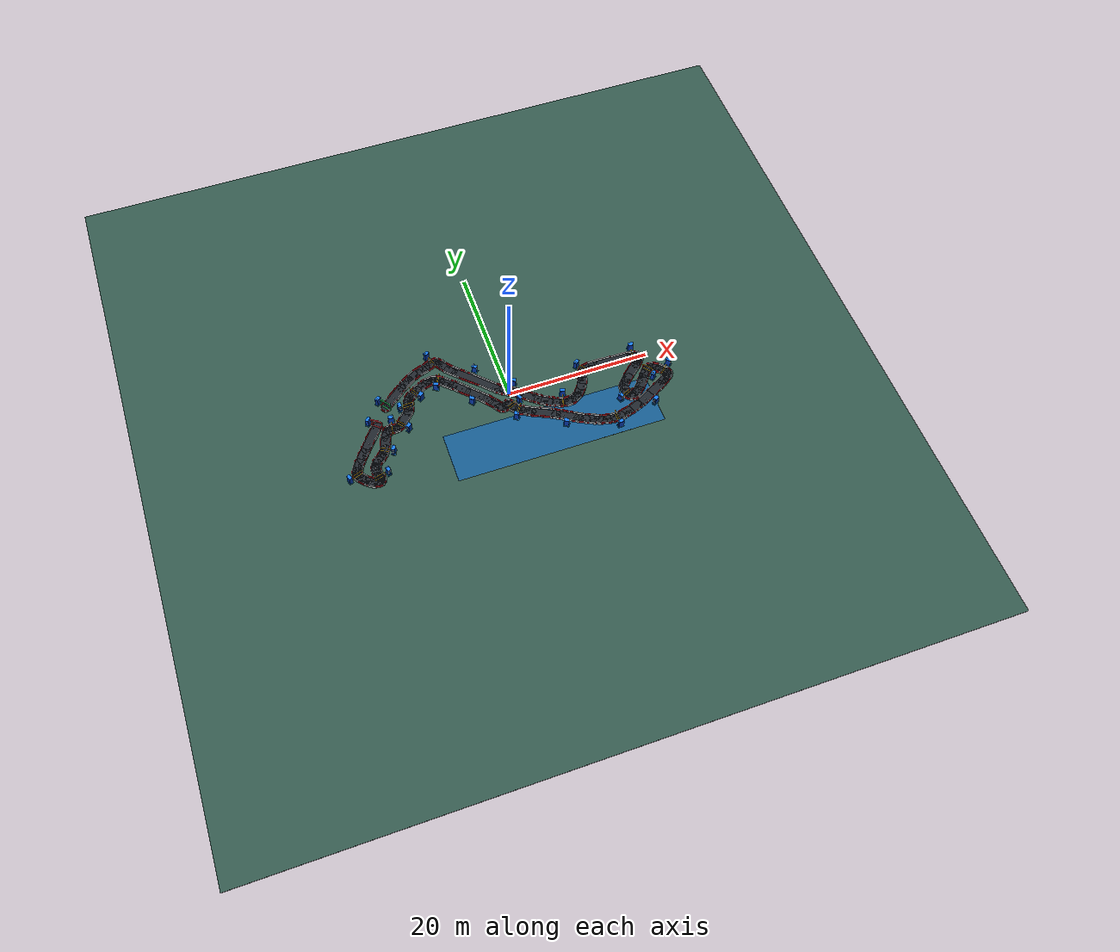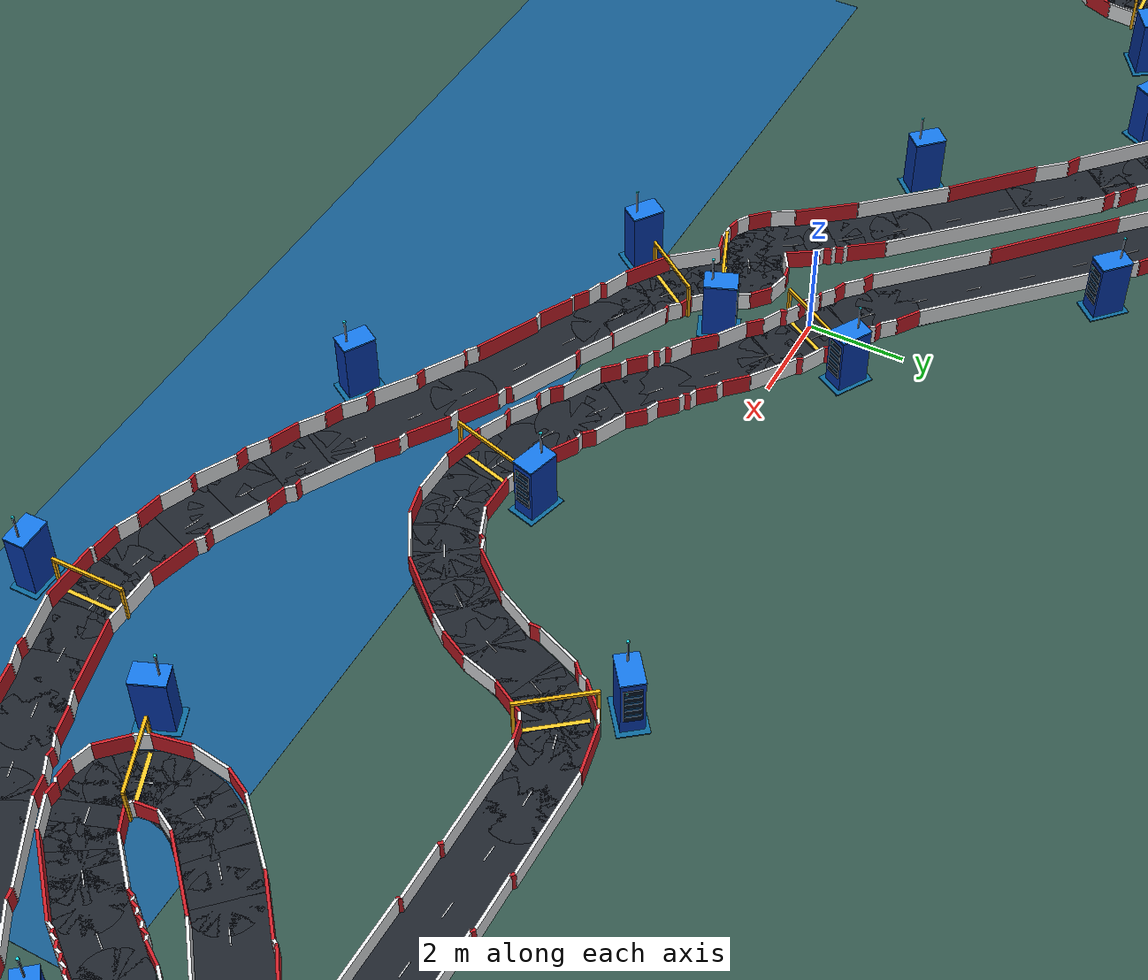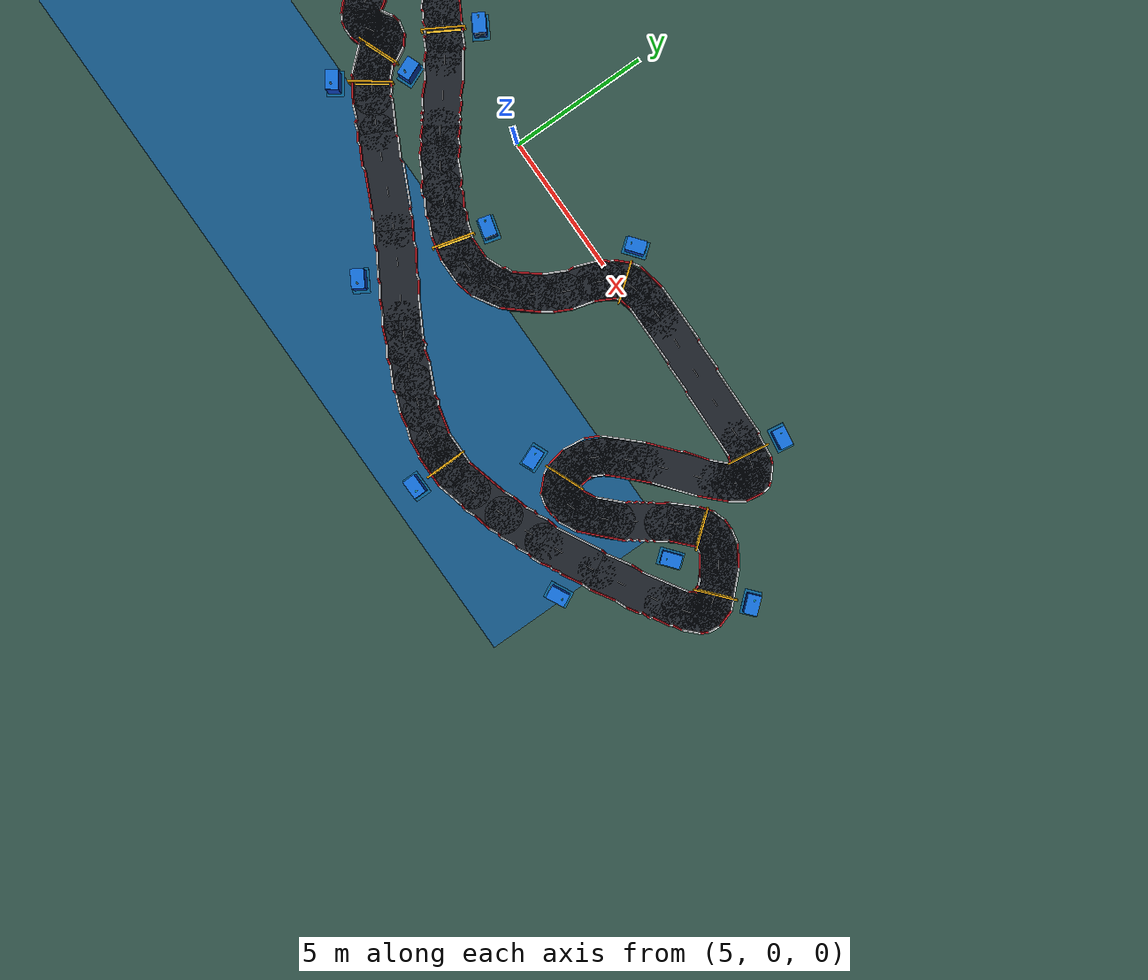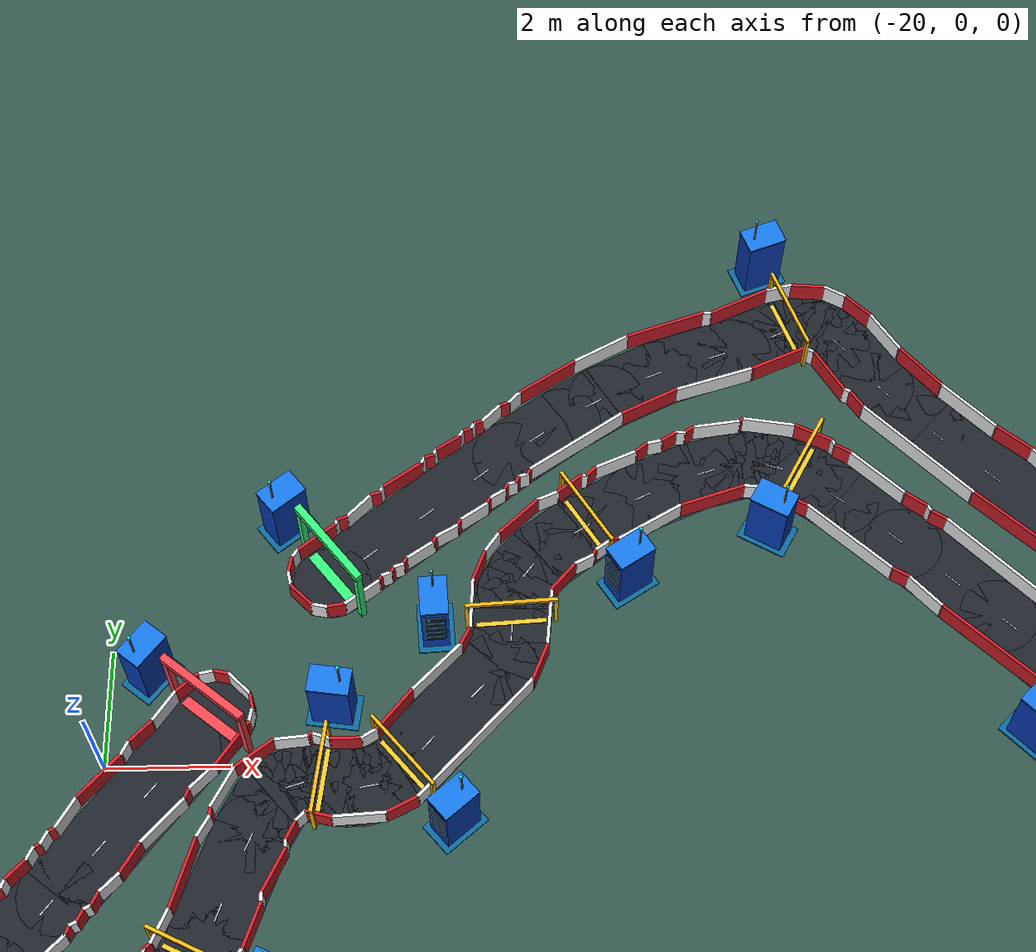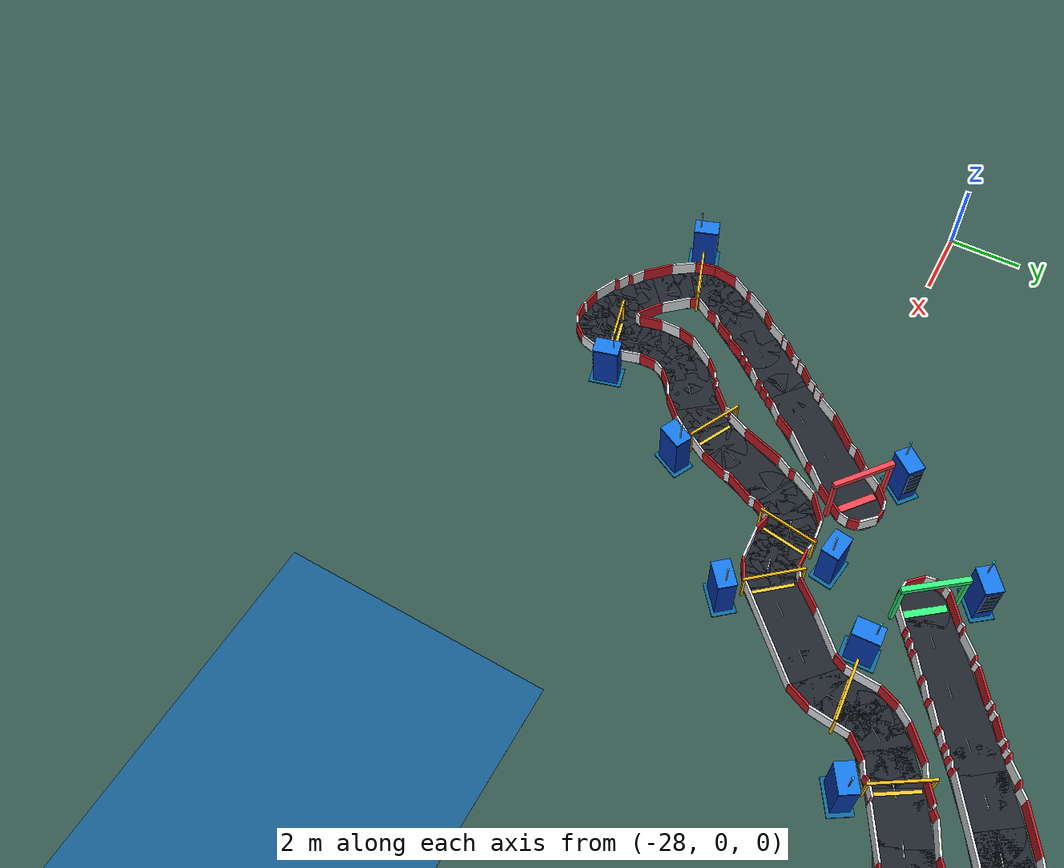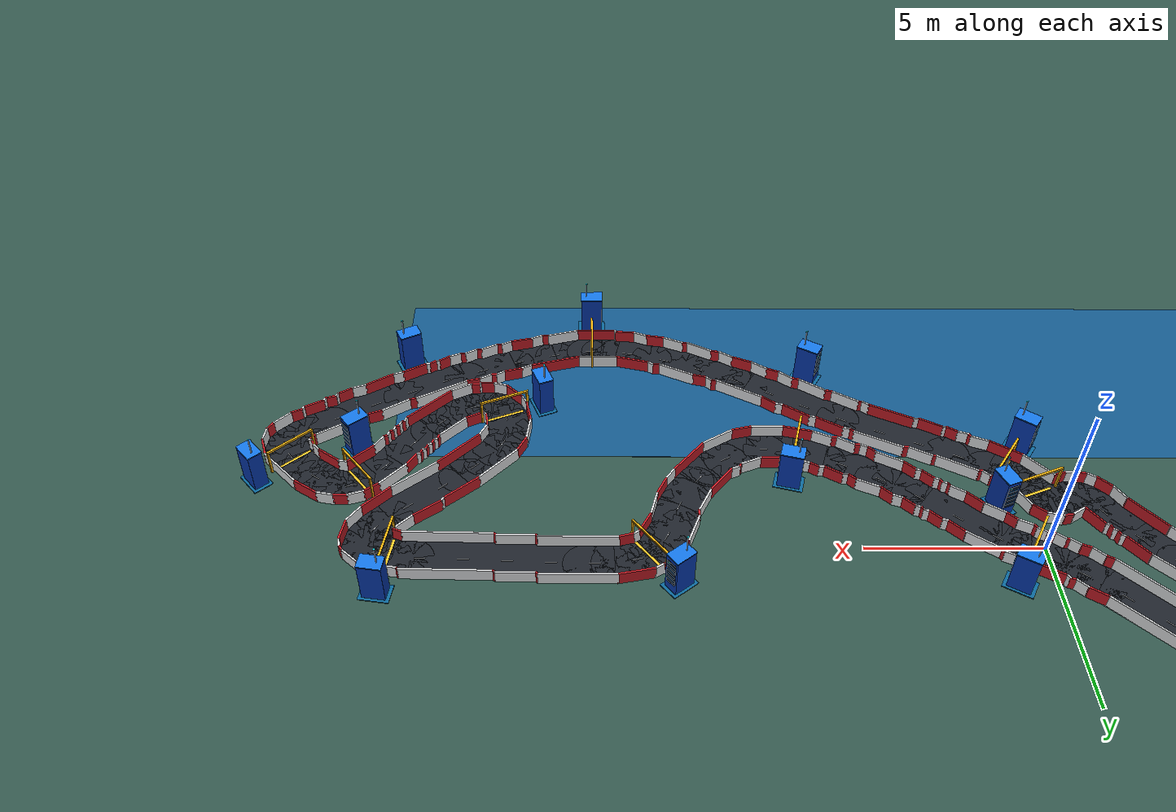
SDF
<?xml version='1.0' encoding='utf-8'?>
<sdf version="1.9">
  <world name="monaco">
    <plugin filename="gz-sim-physics-system" name="gz::sim::systems::Physics" />
    <plugin filename="gz-sim-user-commands-system" name="gz::sim::systems::UserCommands" />
    <plugin filename="gz-sim-scene-broadcaster-system" name="gz::sim::systems::SceneBroadcaster" />
    <plugin filename="gz-sim-sensors-system" name="gz::sim::systems::Sensors">
      <render_engine>ogre2</render_engine>
    </plugin>
    <plugin filename="gz-sim-imu-system" name="gz::sim::systems::Imu" />
    <physics name="default" type="ode">
      <max_step_size>0.003</max_step_size>
      <real_time_factor>1</real_time_factor>
    </physics>
    <scene>
      <ambient>0.7 0.7 0.7 1</ambient>
      <background>0.65 0.78 0.88 1</background>
      <shadows>false</shadows>
    </scene>
    <light name="sun" type="directional">
      <pose>0 0 20 0 0 0</pose>
      <diffuse>0.9 0.9 0.9 1</diffuse>
      <direction>-0.5 0.3 -1</direction>
    </light>
    <model name="ground">
      <static>true</static>
      <pose>0 0 0 0 0 0</pose>
      <link name="body">
        <visual name="ground">
          <pose>0 0 -0.08 0 0 0</pose>
          <geometry>
            <box>
              <size>100 100 0.15</size>
            </box>
          </geometry>
          <material>
            <ambient>0.20 0.34 0.30 1</ambient>
            <diffuse>0.20 0.34 0.30 1</diffuse>
          </material>
        </visual>
        <collision name="ground_collision">
          <pose>0 0 -0.08 0 0 0</pose>
          <geometry>
            <box>
              <size>100 100 0.15</size>
            </box>
          </geometry>
        </collision>
      </link>
    </model>
    <model name="harbour">
      <static>true</static>
      <pose>4 -7 0 0 0 0</pose>
      <link name="body">
        <visual name="water">
          <pose>0 0 -0.002 0 0 0</pose>
          <geometry>
            <box>
              <size>29 7 0.004</size>
            </box>
          </geometry>
          <material>
            <ambient>0.08 0.35 0.55 1</ambient>
            <diffuse>0.08 0.35 0.55 1</diffuse>
          </material>
        </visual>
      </link>
    </model>
    <model name="asphalt">
      <static>true</static>
      <pose>0 0 0 0 0 0</pose>
      <link name="body">
        <visual name="road_join_0">
          <pose>-16.45 3.22 0.003 0 0 0</pose>
          <geometry>
            <cylinder>
              <radius>0.65</radius>
              <length>0.008</length>
            </cylinder>
          </geometry>
          <material>
            <ambient>0.12 0.14 0.17 1</ambient>
            <diffuse>0.12 0.14 0.17 1</diffuse>
          </material>
        </visual>
        <visual name="road_join_1">
          <pose>-13.441914 5.575117 0.003 0 0 0</pose>
          <geometry>
            <cylinder>
              <radius>0.65</radius>
              <length>0.008</length>
            </cylinder>
          </geometry>
          <material>
            <ambient>0.12 0.14 0.17 1</ambient>
            <diffuse>0.12 0.14 0.17 1</diffuse>
          </material>
        </visual>
        <visual name="road_join_2">
          <pose>-12.510039 6.229909 0.003 0 0 0</pose>
          <geometry>
            <cylinder>
              <radius>0.65</radius>
              <length>0.008</length>
            </cylinder>
          </geometry>
          <material>
            <ambient>0.12 0.14 0.17 1</ambient>
            <diffuse>0.12 0.14 0.17 1</diffuse>
          </material>
        </visual>
        <visual name="road_join_3">
          <pose>-11.753711 6.696758 0.003 0 0 0</pose>
          <geometry>
            <cylinder>
              <radius>0.65</radius>
              <length>0.008</length>
            </cylinder>
          </geometry>
          <material>
            <ambient>0.12 0.14 0.17 1</ambient>
            <diffuse>0.12 0.14 0.17 1</diffuse>
          </material>
        </visual>
        <visual name="road_join_4">
          <pose>-10.785742 7.1616015 0.003 0 0 0</pose>
          <geometry>
            <cylinder>
              <radius>0.65</radius>
              <length>0.008</length>
            </cylinder>
          </geometry>
          <material>
            <ambient>0.12 0.14 0.17 1</ambient>
            <diffuse>0.12 0.14 0.17 1</diffuse>
          </material>
        </visual>
        <visual name="road_join_5">
          <pose>-9.45875 7.590625 0.003 0 0 0</pose>
          <geometry>
            <cylinder>
              <radius>0.65</radius>
              <length>0.008</length>
            </cylinder>
          </geometry>
          <material>
            <ambient>0.12 0.14 0.17 1</ambient>
            <diffuse>0.12 0.14 0.17 1</diffuse>
          </material>
        </visual>
        <visual name="road_join_6">
          <pose>-8.4514065 7.9947658 0.003 0 0 0</pose>
          <geometry>
            <cylinder>
              <radius>0.65</radius>
              <length>0.008</length>
            </cylinder>
          </geometry>
          <material>
            <ambient>0.12 0.14 0.17 1</ambient>
            <diffuse>0.12 0.14 0.17 1</diffuse>
          </material>
        </visual>
        <visual name="road_join_7">
          <pose>-8.134219 8.022109 0.003 0 0 0</pose>
          <geometry>
            <cylinder>
              <radius>0.65</radius>
              <length>0.008</length>
            </cylinder>
          </geometry>
          <material>
            <ambient>0.12 0.14 0.17 1</ambient>
            <diffuse>0.12 0.14 0.17 1</diffuse>
          </material>
        </visual>
        <visual name="road_join_8">
          <pose>-7.9078126 7.945 0.003 0 0 0</pose>
          <geometry>
            <cylinder>
              <radius>0.65</radius>
              <length>0.008</length>
            </cylinder>
          </geometry>
          <material>
            <ambient>0.12 0.14 0.17 1</ambient>
            <diffuse>0.12 0.14 0.17 1</diffuse>
          </material>
        </visual>
        <visual name="road_join_9">
          <pose>-7.69125 7.784219 0.003 0 0 0</pose>
          <geometry>
            <cylinder>
              <radius>0.65</radius>
              <length>0.008</length>
            </cylinder>
          </geometry>
          <material>
            <ambient>0.12 0.14 0.17 1</ambient>
            <diffuse>0.12 0.14 0.17 1</diffuse>
          </material>
        </visual>
        <visual name="road_join_10">
          <pose>-7.0021877 6.8435936 0.003 0 0 0</pose>
          <geometry>
            <cylinder>
              <radius>0.65</radius>
              <length>0.008</length>
            </cylinder>
          </geometry>
          <material>
            <ambient>0.12 0.14 0.17 1</ambient>
            <diffuse>0.12 0.14 0.17 1</diffuse>
          </material>
        </visual>
        <visual name="road_join_11">
          <pose>-6.2146873 5.9658594 0.003 0 0 0</pose>
          <geometry>
            <cylinder>
              <radius>0.65</radius>
              <length>0.008</length>
            </cylinder>
          </geometry>
          <material>
            <ambient>0.12 0.14 0.17 1</ambient>
            <diffuse>0.12 0.14 0.17 1</diffuse>
          </material>
        </visual>
        <visual name="road_join_12">
          <pose>-1.1763282 1.1809765 0.003 0 0 0</pose>
          <geometry>
            <cylinder>
              <radius>0.65</radius>
              <length>0.008</length>
            </cylinder>
          </geometry>
          <material>
            <ambient>0.12 0.14 0.17 1</ambient>
            <diffuse>0.12 0.14 0.17 1</diffuse>
          </material>
        </visual>
        <visual name="road_join_13">
          <pose>-0.37078124 0.57804686 0.003 0 0 0</pose>
          <geometry>
            <cylinder>
              <radius>0.65</radius>
              <length>0.008</length>
            </cylinder>
          </geometry>
          <material>
            <ambient>0.12 0.14 0.17 1</ambient>
            <diffuse>0.12 0.14 0.17 1</diffuse>
          </material>
        </visual>
        <visual name="road_join_14">
          <pose>0.450625 0.12359375 0.003 0 0 0</pose>
          <geometry>
            <cylinder>
              <radius>0.65</radius>
              <length>0.008</length>
            </cylinder>
          </geometry>
          <material>
            <ambient>0.12 0.14 0.17 1</ambient>
            <diffuse>0.12 0.14 0.17 1</diffuse>
          </material>
        </visual>
        <visual name="road_join_15">
          <pose>1.1615624 -0.3521875 0.003 0 0 0</pose>
          <geometry>
            <cylinder>
              <radius>0.65</radius>
              <length>0.008</length>
            </cylinder>
          </geometry>
          <material>
            <ambient>0.12 0.14 0.17 1</ambient>
            <diffuse>0.12 0.14 0.17 1</diffuse>
          </material>
        </visual>
        <visual name="road_join_16">
          <pose>2.9747267 -1.7992188 0.003 0 0 0</pose>
          <geometry>
            <cylinder>
              <radius>0.65</radius>
              <length>0.008</length>
            </cylinder>
          </geometry>
          <material>
            <ambient>0.12 0.14 0.17 1</ambient>
            <diffuse>0.12 0.14 0.17 1</diffuse>
          </material>
        </visual>
        <visual name="road_join_17">
          <pose>3.7474608 -2.3657813 0.003 0 0 0</pose>
          <geometry>
            <cylinder>
              <radius>0.65</radius>
              <length>0.008</length>
            </cylinder>
          </geometry>
          <material>
            <ambient>0.12 0.14 0.17 1</ambient>
            <diffuse>0.12 0.14 0.17 1</diffuse>
          </material>
        </visual>
        <visual name="road_join_18">
          <pose>4.694922 -2.9509375 0.003 0 0 0</pose>
          <geometry>
            <cylinder>
              <radius>0.65</radius>
              <length>0.008</length>
            </cylinder>
          </geometry>
          <material>
            <ambient>0.12 0.14 0.17 1</ambient>
            <diffuse>0.12 0.14 0.17 1</diffuse>
          </material>
        </visual>
        <visual name="road_join_19">
          <pose>5.621875 -3.399375 0.003 0 0 0</pose>
          <geometry>
            <cylinder>
              <radius>0.65</radius>
              <length>0.008</length>
            </cylinder>
          </geometry>
          <material>
            <ambient>0.12 0.14 0.17 1</ambient>
            <diffuse>0.12 0.14 0.17 1</diffuse>
          </material>
        </visual>
        <visual name="road_join_20">
          <pose>6.6267576 -3.722578 0.003 0 0 0</pose>
          <geometry>
            <cylinder>
              <radius>0.65</radius>
              <length>0.008</length>
            </cylinder>
          </geometry>
          <material>
            <ambient>0.12 0.14 0.17 1</ambient>
            <diffuse>0.12 0.14 0.17 1</diffuse>
          </material>
        </visual>
        <visual name="road_join_21">
          <pose>7.336328 -3.7964063 0.003 0 0 0</pose>
          <geometry>
            <cylinder>
              <radius>0.65</radius>
              <length>0.008</length>
            </cylinder>
          </geometry>
          <material>
            <ambient>0.12 0.14 0.17 1</ambient>
            <diffuse>0.12 0.14 0.17 1</diffuse>
          </material>
        </visual>
        <visual name="road_join_22">
          <pose>7.9296875 -3.6925 0.003 0 0 0</pose>
          <geometry>
            <cylinder>
              <radius>0.65</radius>
              <length>0.008</length>
            </cylinder>
          </geometry>
          <material>
            <ambient>0.12 0.14 0.17 1</ambient>
            <diffuse>0.12 0.14 0.17 1</diffuse>
          </material>
        </visual>
        <visual name="road_join_23">
          <pose>8.545742 -3.390625 0.003 0 0 0</pose>
          <geometry>
            <cylinder>
              <radius>0.65</radius>
              <length>0.008</length>
            </cylinder>
          </geometry>
          <material>
            <ambient>0.12 0.14 0.17 1</ambient>
            <diffuse>0.12 0.14 0.17 1</diffuse>
          </material>
        </visual>
        <visual name="road_join_24">
          <pose>9.006484 -3.01875 0.003 0 0 0</pose>
          <geometry>
            <cylinder>
              <radius>0.65</radius>
              <length>0.008</length>
            </cylinder>
          </geometry>
          <material>
            <ambient>0.12 0.14 0.17 1</ambient>
            <diffuse>0.12 0.14 0.17 1</diffuse>
          </material>
        </visual>
        <visual name="road_join_25">
          <pose>9.4948435 -2.4327734 0.003 0 0 0</pose>
          <geometry>
            <cylinder>
              <radius>0.65</radius>
              <length>0.008</length>
            </cylinder>
          </geometry>
          <material>
            <ambient>0.12 0.14 0.17 1</ambient>
            <diffuse>0.12 0.14 0.17 1</diffuse>
          </material>
        </visual>
        <visual name="road_join_26">
          <pose>9.980469 -1.6048046 0.003 0 0 0</pose>
          <geometry>
            <cylinder>
              <radius>0.65</radius>
              <length>0.008</length>
            </cylinder>
          </geometry>
          <material>
            <ambient>0.12 0.14 0.17 1</ambient>
            <diffuse>0.12 0.14 0.17 1</diffuse>
          </material>
        </visual>
        <visual name="road_join_27">
          <pose>10.325 -0.6125 0.003 0 0 0</pose>
          <geometry>
            <cylinder>
              <radius>0.65</radius>
              <length>0.008</length>
            </cylinder>
          </geometry>
          <material>
            <ambient>0.12 0.14 0.17 1</ambient>
            <diffuse>0.12 0.14 0.17 1</diffuse>
          </material>
        </visual>
        <visual name="road_join_28">
          <pose>10.521875 -0.2078125 0.003 0 0 0</pose>
          <geometry>
            <cylinder>
              <radius>0.65</radius>
              <length>0.008</length>
            </cylinder>
          </geometry>
          <material>
            <ambient>0.12 0.14 0.17 1</ambient>
            <diffuse>0.12 0.14 0.17 1</diffuse>
          </material>
        </visual>
        <visual name="road_join_29">
          <pose>10.889375 0.2209375 0.003 0 0 0</pose>
          <geometry>
            <cylinder>
              <radius>0.65</radius>
              <length>0.008</length>
            </cylinder>
          </geometry>
          <material>
            <ambient>0.12 0.14 0.17 1</ambient>
            <diffuse>0.12 0.14 0.17 1</diffuse>
          </material>
        </visual>
        <visual name="road_join_30">
          <pose>11.209844 0.39046875 0.003 0 0 0</pose>
          <geometry>
            <cylinder>
              <radius>0.65</radius>
              <length>0.008</length>
            </cylinder>
          </geometry>
          <material>
            <ambient>0.12 0.14 0.17 1</ambient>
            <diffuse>0.12 0.14 0.17 1</diffuse>
          </material>
        </visual>
        <visual name="road_join_31">
          <pose>11.893437 0.51625 0.003 0 0 0</pose>
          <geometry>
            <cylinder>
              <radius>0.65</radius>
              <length>0.008</length>
            </cylinder>
          </geometry>
          <material>
            <ambient>0.12 0.14 0.17 1</ambient>
            <diffuse>0.12 0.14 0.17 1</diffuse>
          </material>
        </visual>
        <visual name="road_join_32">
          <pose>12.6667185 0.54796875 0.003 0 0 0</pose>
          <geometry>
            <cylinder>
              <radius>0.65</radius>
              <length>0.008</length>
            </cylinder>
          </geometry>
          <material>
            <ambient>0.12 0.14 0.17 1</ambient>
            <diffuse>0.12 0.14 0.17 1</diffuse>
          </material>
        </visual>
        <visual name="road_join_33">
          <pose>17.468555 0.37515625 0.003 0 0 0</pose>
          <geometry>
            <cylinder>
              <radius>0.65</radius>
              <length>0.008</length>
            </cylinder>
          </geometry>
          <material>
            <ambient>0.12 0.14 0.17 1</ambient>
            <diffuse>0.12 0.14 0.17 1</diffuse>
          </material>
        </visual>
        <visual name="road_join_34">
          <pose>18.091446 0.31171876 0.003 0 0 0</pose>
          <geometry>
            <cylinder>
              <radius>0.65</radius>
              <length>0.008</length>
            </cylinder>
          </geometry>
          <material>
            <ambient>0.12 0.14 0.17 1</ambient>
            <diffuse>0.12 0.14 0.17 1</diffuse>
          </material>
        </visual>
        <visual name="road_join_35">
          <pose>18.605507 0.15859374 0.003 0 0 0</pose>
          <geometry>
            <cylinder>
              <radius>0.65</radius>
              <length>0.008</length>
            </cylinder>
          </geometry>
          <material>
            <ambient>0.12 0.14 0.17 1</ambient>
            <diffuse>0.12 0.14 0.17 1</diffuse>
          </material>
        </visual>
        <visual name="road_join_36">
          <pose>18.805117 -0.02296875 0.003 0 0 0</pose>
          <geometry>
            <cylinder>
              <radius>0.65</radius>
              <length>0.008</length>
            </cylinder>
          </geometry>
          <material>
            <ambient>0.12 0.14 0.17 1</ambient>
            <diffuse>0.12 0.14 0.17 1</diffuse>
          </material>
        </visual>
        <visual name="road_join_37">
          <pose>18.834375 -0.1334375 0.003 0 0 0</pose>
          <geometry>
            <cylinder>
              <radius>0.65</radius>
              <length>0.008</length>
            </cylinder>
          </geometry>
          <material>
            <ambient>0.12 0.14 0.17 1</ambient>
            <diffuse>0.12 0.14 0.17 1</diffuse>
          </material>
        </visual>
        <visual name="road_join_38">
          <pose>18.795 -0.33359376 0.003 0 0 0</pose>
          <geometry>
            <cylinder>
              <radius>0.65</radius>
              <length>0.008</length>
            </cylinder>
          </geometry>
          <material>
            <ambient>0.12 0.14 0.17 1</ambient>
            <diffuse>0.12 0.14 0.17 1</diffuse>
          </material>
        </visual>
        <visual name="road_join_39">
          <pose>18.589375 -0.669375 0.003 0 0 0</pose>
          <geometry>
            <cylinder>
              <radius>0.65</radius>
              <length>0.008</length>
            </cylinder>
          </geometry>
          <material>
            <ambient>0.12 0.14 0.17 1</ambient>
            <diffuse>0.12 0.14 0.17 1</diffuse>
          </material>
        </visual>
        <visual name="road_join_40">
          <pose>18.20875 -1.0839063 0.003 0 0 0</pose>
          <geometry>
            <cylinder>
              <radius>0.65</radius>
              <length>0.008</length>
            </cylinder>
          </geometry>
          <material>
            <ambient>0.12 0.14 0.17 1</ambient>
            <diffuse>0.12 0.14 0.17 1</diffuse>
          </material>
        </visual>
        <visual name="road_join_41">
          <pose>16.334063 -2.7092187 0.003 0 0 0</pose>
          <geometry>
            <cylinder>
              <radius>0.65</radius>
              <length>0.008</length>
            </cylinder>
          </geometry>
          <material>
            <ambient>0.12 0.14 0.17 1</ambient>
            <diffuse>0.12 0.14 0.17 1</diffuse>
          </material>
        </visual>
        <visual name="road_join_42">
          <pose>15.676172 -3.353164 0.003 0 0 0</pose>
          <geometry>
            <cylinder>
              <radius>0.65</radius>
              <length>0.008</length>
            </cylinder>
          </geometry>
          <material>
            <ambient>0.12 0.14 0.17 1</ambient>
            <diffuse>0.12 0.14 0.17 1</diffuse>
          </material>
        </visual>
        <visual name="road_join_43">
          <pose>15.344219 -3.7422657 0.003 0 0 0</pose>
          <geometry>
            <cylinder>
              <radius>0.65</radius>
              <length>0.008</length>
            </cylinder>
          </geometry>
          <material>
            <ambient>0.12 0.14 0.17 1</ambient>
            <diffuse>0.12 0.14 0.17 1</diffuse>
          </material>
        </visual>
        <visual name="road_join_44">
          <pose>15.132031 -4.1371093 0.003 0 0 0</pose>
          <geometry>
            <cylinder>
              <radius>0.65</radius>
              <length>0.008</length>
            </cylinder>
          </geometry>
          <material>
            <ambient>0.12 0.14 0.17 1</ambient>
            <diffuse>0.12 0.14 0.17 1</diffuse>
          </material>
        </visual>
        <visual name="road_join_45">
          <pose>15.0390625 -4.6429687 0.003 0 0 0</pose>
          <geometry>
            <cylinder>
              <radius>0.65</radius>
              <length>0.008</length>
            </cylinder>
          </geometry>
          <material>
            <ambient>0.12 0.14 0.17 1</ambient>
            <diffuse>0.12 0.14 0.17 1</diffuse>
          </material>
        </visual>
        <visual name="road_join_46">
          <pose>15.1025 -5.0575 0.003 0 0 0</pose>
          <geometry>
            <cylinder>
              <radius>0.65</radius>
              <length>0.008</length>
            </cylinder>
          </geometry>
          <material>
            <ambient>0.12 0.14 0.17 1</ambient>
            <diffuse>0.12 0.14 0.17 1</diffuse>
          </material>
        </visual>
        <visual name="road_join_47">
          <pose>15.318516 -5.486797 0.003 0 0 0</pose>
          <geometry>
            <cylinder>
              <radius>0.65</radius>
              <length>0.008</length>
            </cylinder>
          </geometry>
          <material>
            <ambient>0.12 0.14 0.17 1</ambient>
            <diffuse>0.12 0.14 0.17 1</diffuse>
          </material>
        </visual>
        <visual name="road_join_48">
          <pose>15.565156 -5.6579685 0.003 0 0 0</pose>
          <geometry>
            <cylinder>
              <radius>0.65</radius>
              <length>0.008</length>
            </cylinder>
          </geometry>
          <material>
            <ambient>0.12 0.14 0.17 1</ambient>
            <diffuse>0.12 0.14 0.17 1</diffuse>
          </material>
        </visual>
        <visual name="road_join_49">
          <pose>15.877422 -5.676016 0.003 0 0 0</pose>
          <geometry>
            <cylinder>
              <radius>0.65</radius>
              <length>0.008</length>
            </cylinder>
          </geometry>
          <material>
            <ambient>0.12 0.14 0.17 1</ambient>
            <diffuse>0.12 0.14 0.17 1</diffuse>
          </material>
        </visual>
        <visual name="road_join_50">
          <pose>16.255312 -5.5409374 0.003 0 0 0</pose>
          <geometry>
            <cylinder>
              <radius>0.65</radius>
              <length>0.008</length>
            </cylinder>
          </geometry>
          <material>
            <ambient>0.12 0.14 0.17 1</ambient>
            <diffuse>0.12 0.14 0.17 1</diffuse>
          </material>
        </visual>
        <visual name="road_join_51">
          <pose>16.657812 -5.2910156 0.003 0 0 0</pose>
          <geometry>
            <cylinder>
              <radius>0.65</radius>
              <length>0.008</length>
            </cylinder>
          </geometry>
          <material>
            <ambient>0.12 0.14 0.17 1</ambient>
            <diffuse>0.12 0.14 0.17 1</diffuse>
          </material>
        </visual>
        <visual name="road_join_52">
          <pose>16.959688 -5.043281 0.003 0 0 0</pose>
          <geometry>
            <cylinder>
              <radius>0.65</radius>
              <length>0.008</length>
            </cylinder>
          </geometry>
          <material>
            <ambient>0.12 0.14 0.17 1</ambient>
            <diffuse>0.12 0.14 0.17 1</diffuse>
          </material>
        </visual>
        <visual name="road_join_53">
          <pose>17.362188 -4.632578 0.003 0 0 0</pose>
          <geometry>
            <cylinder>
              <radius>0.65</radius>
              <length>0.008</length>
            </cylinder>
          </geometry>
          <material>
            <ambient>0.12 0.14 0.17 1</ambient>
            <diffuse>0.12 0.14 0.17 1</diffuse>
          </material>
        </visual>
        <visual name="road_join_54">
          <pose>18.343828 -3.3638282 0.003 0 0 0</pose>
          <geometry>
            <cylinder>
              <radius>0.65</radius>
              <length>0.008</length>
            </cylinder>
          </geometry>
          <material>
            <ambient>0.12 0.14 0.17 1</ambient>
            <diffuse>0.12 0.14 0.17 1</diffuse>
          </material>
        </visual>
        <visual name="road_join_55">
          <pose>18.863907 -2.7748437 0.003 0 0 0</pose>
          <geometry>
            <cylinder>
              <radius>0.65</radius>
              <length>0.008</length>
            </cylinder>
          </geometry>
          <material>
            <ambient>0.12 0.14 0.17 1</ambient>
            <diffuse>0.12 0.14 0.17 1</diffuse>
          </material>
        </visual>
        <visual name="road_join_56">
          <pose>19.252188 -2.419375 0.003 0 0 0</pose>
          <geometry>
            <cylinder>
              <radius>0.65</radius>
              <length>0.008</length>
            </cylinder>
          </geometry>
          <material>
            <ambient>0.12 0.14 0.17 1</ambient>
            <diffuse>0.12 0.14 0.17 1</diffuse>
          </material>
        </visual>
        <visual name="road_join_57">
          <pose>19.5825 -2.2810156 0.003 0 0 0</pose>
          <geometry>
            <cylinder>
              <radius>0.65</radius>
              <length>0.008</length>
            </cylinder>
          </geometry>
          <material>
            <ambient>0.12 0.14 0.17 1</ambient>
            <diffuse>0.12 0.14 0.17 1</diffuse>
          </material>
        </visual>
        <visual name="road_join_58">
          <pose>19.965313 -2.3132813 0.003 0 0 0</pose>
          <geometry>
            <cylinder>
              <radius>0.65</radius>
              <length>0.008</length>
            </cylinder>
          </geometry>
          <material>
            <ambient>0.12 0.14 0.17 1</ambient>
            <diffuse>0.12 0.14 0.17 1</diffuse>
          </material>
        </visual>
        <visual name="road_join_59">
          <pose>20.286875 -2.449453 0.003 0 0 0</pose>
          <geometry>
            <cylinder>
              <radius>0.65</radius>
              <length>0.008</length>
            </cylinder>
          </geometry>
          <material>
            <ambient>0.12 0.14 0.17 1</ambient>
            <diffuse>0.12 0.14 0.17 1</diffuse>
          </material>
        </visual>
        <visual name="road_join_60">
          <pose>20.637968 -2.6816015 0.003 0 0 0</pose>
          <geometry>
            <cylinder>
              <radius>0.65</radius>
              <length>0.008</length>
            </cylinder>
          </geometry>
          <material>
            <ambient>0.12 0.14 0.17 1</ambient>
            <diffuse>0.12 0.14 0.17 1</diffuse>
          </material>
        </visual>
        <visual name="road_join_61">
          <pose>21.113476 -3.0969532 0.003 0 0 0</pose>
          <geometry>
            <cylinder>
              <radius>0.65</radius>
              <length>0.008</length>
            </cylinder>
          </geometry>
          <material>
            <ambient>0.12 0.14 0.17 1</ambient>
            <diffuse>0.12 0.14 0.17 1</diffuse>
          </material>
        </visual>
        <visual name="road_join_62">
          <pose>21.448711 -3.4655468 0.003 0 0 0</pose>
          <geometry>
            <cylinder>
              <radius>0.65</radius>
              <length>0.008</length>
            </cylinder>
          </geometry>
          <material>
            <ambient>0.12 0.14 0.17 1</ambient>
            <diffuse>0.12 0.14 0.17 1</diffuse>
          </material>
        </visual>
        <visual name="road_join_63">
          <pose>21.630821 -3.7728906 0.003 0 0 0</pose>
          <geometry>
            <cylinder>
              <radius>0.65</radius>
              <length>0.008</length>
            </cylinder>
          </geometry>
          <material>
            <ambient>0.12 0.14 0.17 1</ambient>
            <diffuse>0.12 0.14 0.17 1</diffuse>
          </material>
        </visual>
        <visual name="road_join_64">
          <pose>21.659805 -4.0189843 0.003 0 0 0</pose>
          <geometry>
            <cylinder>
              <radius>0.65</radius>
              <length>0.008</length>
            </cylinder>
          </geometry>
          <material>
            <ambient>0.12 0.14 0.17 1</ambient>
            <diffuse>0.12 0.14 0.17 1</diffuse>
          </material>
        </visual>
        <visual name="road_join_65">
          <pose>21.575586 -4.1734767 0.003 0 0 0</pose>
          <geometry>
            <cylinder>
              <radius>0.65</radius>
              <length>0.008</length>
            </cylinder>
          </geometry>
          <material>
            <ambient>0.12 0.14 0.17 1</ambient>
            <diffuse>0.12 0.14 0.17 1</diffuse>
          </material>
        </visual>
        <visual name="road_join_66">
          <pose>21.201797 -4.496953 0.003 0 0 0</pose>
          <geometry>
            <cylinder>
              <radius>0.65</radius>
              <length>0.008</length>
            </cylinder>
          </geometry>
          <material>
            <ambient>0.12 0.14 0.17 1</ambient>
            <diffuse>0.12 0.14 0.17 1</diffuse>
          </material>
        </visual>
        <visual name="road_join_67">
          <pose>20.527227 -4.946211 0.003 0 0 0</pose>
          <geometry>
            <cylinder>
              <radius>0.65</radius>
              <length>0.008</length>
            </cylinder>
          </geometry>
          <material>
            <ambient>0.12 0.14 0.17 1</ambient>
            <diffuse>0.12 0.14 0.17 1</diffuse>
          </material>
        </visual>
        <visual name="road_join_68">
          <pose>18.380468 -6.1610937 0.003 0 0 0</pose>
          <geometry>
            <cylinder>
              <radius>0.65</radius>
              <length>0.008</length>
            </cylinder>
          </geometry>
          <material>
            <ambient>0.12 0.14 0.17 1</ambient>
            <diffuse>0.12 0.14 0.17 1</diffuse>
          </material>
        </visual>
        <visual name="road_join_69">
          <pose>16.540781 -7.0557814 0.003 0 0 0</pose>
          <geometry>
            <cylinder>
              <radius>0.65</radius>
              <length>0.008</length>
            </cylinder>
          </geometry>
          <material>
            <ambient>0.12 0.14 0.17 1</ambient>
            <diffuse>0.12 0.14 0.17 1</diffuse>
          </material>
        </visual>
        <visual name="road_join_70">
          <pose>15.004609 -7.648594 0.003 0 0 0</pose>
          <geometry>
            <cylinder>
              <radius>0.65</radius>
              <length>0.008</length>
            </cylinder>
          </geometry>
          <material>
            <ambient>0.12 0.14 0.17 1</ambient>
            <diffuse>0.12 0.14 0.17 1</diffuse>
          </material>
        </visual>
        <visual name="road_join_71">
          <pose>13.6800785 -8.044531 0.003 0 0 0</pose>
          <geometry>
            <cylinder>
              <radius>0.65</radius>
              <length>0.008</length>
            </cylinder>
          </geometry>
          <material>
            <ambient>0.12 0.14 0.17 1</ambient>
            <diffuse>0.12 0.14 0.17 1</diffuse>
          </material>
        </visual>
        <visual name="road_join_72">
          <pose>12.657696 -8.237578 0.003 0 0 0</pose>
          <geometry>
            <cylinder>
              <radius>0.65</radius>
              <length>0.008</length>
            </cylinder>
          </geometry>
          <material>
            <ambient>0.12 0.14 0.17 1</ambient>
            <diffuse>0.12 0.14 0.17 1</diffuse>
          </material>
        </visual>
        <visual name="road_join_73">
          <pose>12.188477 -8.244141 0.003 0 0 0</pose>
          <geometry>
            <cylinder>
              <radius>0.65</radius>
              <length>0.008</length>
            </cylinder>
          </geometry>
          <material>
            <ambient>0.12 0.14 0.17 1</ambient>
            <diffuse>0.12 0.14 0.17 1</diffuse>
          </material>
        </visual>
        <visual name="road_join_74">
          <pose>11.6823435 -8.196563 0.003 0 0 0</pose>
          <geometry>
            <cylinder>
              <radius>0.65</radius>
              <length>0.008</length>
            </cylinder>
          </geometry>
          <material>
            <ambient>0.12 0.14 0.17 1</ambient>
            <diffuse>0.12 0.14 0.17 1</diffuse>
          </material>
        </visual>
        <visual name="road_join_75">
          <pose>10.559336 -7.9389844 0.003 0 0 0</pose>
          <geometry>
            <cylinder>
              <radius>0.65</radius>
              <length>0.008</length>
            </cylinder>
          </geometry>
          <material>
            <ambient>0.12 0.14 0.17 1</ambient>
            <diffuse>0.12 0.14 0.17 1</diffuse>
          </material>
        </visual>
        <visual name="road_join_76">
          <pose>9.52875 -7.5703907 0.003 0 0 0</pose>
          <geometry>
            <cylinder>
              <radius>0.65</radius>
              <length>0.008</length>
            </cylinder>
          </geometry>
          <material>
            <ambient>0.12 0.14 0.17 1</ambient>
            <diffuse>0.12 0.14 0.17 1</diffuse>
          </material>
        </visual>
        <visual name="road_join_77">
          <pose>8.467813 -7.097344 0.003 0 0 0</pose>
          <geometry>
            <cylinder>
              <radius>0.65</radius>
              <length>0.008</length>
            </cylinder>
          </geometry>
          <material>
            <ambient>0.12 0.14 0.17 1</ambient>
            <diffuse>0.12 0.14 0.17 1</diffuse>
          </material>
        </visual>
        <visual name="road_join_78">
          <pose>7.599375 -6.645078 0.003 0 0 0</pose>
          <geometry>
            <cylinder>
              <radius>0.65</radius>
              <length>0.008</length>
            </cylinder>
          </geometry>
          <material>
            <ambient>0.12 0.14 0.17 1</ambient>
            <diffuse>0.12 0.14 0.17 1</diffuse>
          </material>
        </visual>
        <visual name="road_join_79">
          <pose>4.948125 -5.130781 0.003 0 0 0</pose>
          <geometry>
            <cylinder>
              <radius>0.65</radius>
              <length>0.008</length>
            </cylinder>
          </geometry>
          <material>
            <ambient>0.12 0.14 0.17 1</ambient>
            <diffuse>0.12 0.14 0.17 1</diffuse>
          </material>
        </visual>
        <visual name="road_join_80">
          <pose>1.9085938 -3.679375 0.003 0 0 0</pose>
          <geometry>
            <cylinder>
              <radius>0.65</radius>
              <length>0.008</length>
            </cylinder>
          </geometry>
          <material>
            <ambient>0.12 0.14 0.17 1</ambient>
            <diffuse>0.12 0.14 0.17 1</diffuse>
          </material>
        </visual>
        <visual name="road_join_81">
          <pose>0.8225 -3.110625 0.003 0 0 0</pose>
          <geometry>
            <cylinder>
              <radius>0.65</radius>
              <length>0.008</length>
            </cylinder>
          </geometry>
          <material>
            <ambient>0.12 0.14 0.17 1</ambient>
            <diffuse>0.12 0.14 0.17 1</diffuse>
          </material>
        </visual>
        <visual name="road_join_82">
          <pose>0.34671876 -2.7934375 0.003 0 0 0</pose>
          <geometry>
            <cylinder>
              <radius>0.65</radius>
              <length>0.008</length>
            </cylinder>
          </geometry>
          <material>
            <ambient>0.12 0.14 0.17 1</ambient>
            <diffuse>0.12 0.14 0.17 1</diffuse>
          </material>
        </visual>
        <visual name="road_join_83">
          <pose>0.0546875 -2.52 0.003 0 0 0</pose>
          <geometry>
            <cylinder>
              <radius>0.65</radius>
              <length>0.008</length>
            </cylinder>
          </geometry>
          <material>
            <ambient>0.12 0.14 0.17 1</ambient>
            <diffuse>0.12 0.14 0.17 1</diffuse>
          </material>
        </visual>
        <visual name="road_join_84">
          <pose>-0.15859374 -2.2290626 0.003 0 0 0</pose>
          <geometry>
            <cylinder>
              <radius>0.65</radius>
              <length>0.008</length>
            </cylinder>
          </geometry>
          <material>
            <ambient>0.12 0.14 0.17 1</ambient>
            <diffuse>0.12 0.14 0.17 1</diffuse>
          </material>
        </visual>
        <visual name="road_join_85">
          <pose>-0.385 -1.7352344 0.003 0 0 0</pose>
          <geometry>
            <cylinder>
              <radius>0.65</radius>
              <length>0.008</length>
            </cylinder>
          </geometry>
          <material>
            <ambient>0.12 0.14 0.17 1</ambient>
            <diffuse>0.12 0.14 0.17 1</diffuse>
          </material>
        </visual>
        <visual name="road_join_86">
          <pose>-0.4965625 -1.6261328 0.003 0 0 0</pose>
          <geometry>
            <cylinder>
              <radius>0.65</radius>
              <length>0.008</length>
            </cylinder>
          </geometry>
          <material>
            <ambient>0.12 0.14 0.17 1</ambient>
            <diffuse>0.12 0.14 0.17 1</diffuse>
          </material>
        </visual>
        <visual name="road_join_87">
          <pose>-0.581875 -1.5957812 0.003 0 0 0</pose>
          <geometry>
            <cylinder>
              <radius>0.65</radius>
              <length>0.008</length>
            </cylinder>
          </geometry>
          <material>
            <ambient>0.12 0.14 0.17 1</ambient>
            <diffuse>0.12 0.14 0.17 1</diffuse>
          </material>
        </visual>
        <visual name="road_join_88">
          <pose>-0.72625 -1.6138282 0.003 0 0 0</pose>
          <geometry>
            <cylinder>
              <radius>0.65</radius>
              <length>0.008</length>
            </cylinder>
          </geometry>
          <material>
            <ambient>0.12 0.14 0.17 1</ambient>
            <diffuse>0.12 0.14 0.17 1</diffuse>
          </material>
        </visual>
        <visual name="road_join_89">
          <pose>-1.0721484 -1.8601953 0.003 0 0 0</pose>
          <geometry>
            <cylinder>
              <radius>0.65</radius>
              <length>0.008</length>
            </cylinder>
          </geometry>
          <material>
            <ambient>0.12 0.14 0.17 1</ambient>
            <diffuse>0.12 0.14 0.17 1</diffuse>
          </material>
        </visual>
        <visual name="road_join_90">
          <pose>-1.2583594 -1.9397656 0.003 0 0 0</pose>
          <geometry>
            <cylinder>
              <radius>0.65</radius>
              <length>0.008</length>
            </cylinder>
          </geometry>
          <material>
            <ambient>0.12 0.14 0.17 1</ambient>
            <diffuse>0.12 0.14 0.17 1</diffuse>
          </material>
        </visual>
        <visual name="road_join_91">
          <pose>-1.4470313 -1.9282813 0.003 0 0 0</pose>
          <geometry>
            <cylinder>
              <radius>0.65</radius>
              <length>0.008</length>
            </cylinder>
          </geometry>
          <material>
            <ambient>0.12 0.14 0.17 1</ambient>
            <diffuse>0.12 0.14 0.17 1</diffuse>
          </material>
        </visual>
        <visual name="road_join_92">
          <pose>-1.5741796 -1.8700391 0.003 0 0 0</pose>
          <geometry>
            <cylinder>
              <radius>0.65</radius>
              <length>0.008</length>
            </cylinder>
          </geometry>
          <material>
            <ambient>0.12 0.14 0.17 1</ambient>
            <diffuse>0.12 0.14 0.17 1</diffuse>
          </material>
        </visual>
        <visual name="road_join_93">
          <pose>-1.8317578 -1.6321484 0.003 0 0 0</pose>
          <geometry>
            <cylinder>
              <radius>0.65</radius>
              <length>0.008</length>
            </cylinder>
          </geometry>
          <material>
            <ambient>0.12 0.14 0.17 1</ambient>
            <diffuse>0.12 0.14 0.17 1</diffuse>
          </material>
        </visual>
        <visual name="road_join_94">
          <pose>-2.5766015 -0.60839844 0.003 0 0 0</pose>
          <geometry>
            <cylinder>
              <radius>0.65</radius>
              <length>0.008</length>
            </cylinder>
          </geometry>
          <material>
            <ambient>0.12 0.14 0.17 1</ambient>
            <diffuse>0.12 0.14 0.17 1</diffuse>
          </material>
        </visual>
        <visual name="road_join_95">
          <pose>-3.5527735 0.49027345 0.003 0 0 0</pose>
          <geometry>
            <cylinder>
              <radius>0.65</radius>
              <length>0.008</length>
            </cylinder>
          </geometry>
          <material>
            <ambient>0.12 0.14 0.17 1</ambient>
            <diffuse>0.12 0.14 0.17 1</diffuse>
          </material>
        </visual>
        <visual name="road_join_96">
          <pose>-5.4140625 2.3767188 0.003 0 0 0</pose>
          <geometry>
            <cylinder>
              <radius>0.65</radius>
              <length>0.008</length>
            </cylinder>
          </geometry>
          <material>
            <ambient>0.12 0.14 0.17 1</ambient>
            <diffuse>0.12 0.14 0.17 1</diffuse>
          </material>
        </visual>
        <visual name="road_join_97">
          <pose>-6.8589063 3.7433593 0.003 0 0 0</pose>
          <geometry>
            <cylinder>
              <radius>0.65</radius>
              <length>0.008</length>
            </cylinder>
          </geometry>
          <material>
            <ambient>0.12 0.14 0.17 1</ambient>
            <diffuse>0.12 0.14 0.17 1</diffuse>
          </material>
        </visual>
        <visual name="road_join_98">
          <pose>-7.8432813 4.589922 0.003 0 0 0</pose>
          <geometry>
            <cylinder>
              <radius>0.65</radius>
              <length>0.008</length>
            </cylinder>
          </geometry>
          <material>
            <ambient>0.12 0.14 0.17 1</ambient>
            <diffuse>0.12 0.14 0.17 1</diffuse>
          </material>
        </visual>
        <visual name="road_join_99">
          <pose>-8.432265 5.03207 0.003 0 0 0</pose>
          <geometry>
            <cylinder>
              <radius>0.65</radius>
              <length>0.008</length>
            </cylinder>
          </geometry>
          <material>
            <ambient>0.12 0.14 0.17 1</ambient>
            <diffuse>0.12 0.14 0.17 1</diffuse>
          </material>
        </visual>
        <visual name="road_join_100">
          <pose>-8.927188 5.246719 0.003 0 0 0</pose>
          <geometry>
            <cylinder>
              <radius>0.65</radius>
              <length>0.008</length>
            </cylinder>
          </geometry>
          <material>
            <ambient>0.12 0.14 0.17 1</ambient>
            <diffuse>0.12 0.14 0.17 1</diffuse>
          </material>
        </visual>
        <visual name="road_join_101">
          <pose>-9.230703 5.3000393 0.003 0 0 0</pose>
          <geometry>
            <cylinder>
              <radius>0.65</radius>
              <length>0.008</length>
            </cylinder>
          </geometry>
          <material>
            <ambient>0.12 0.14 0.17 1</ambient>
            <diffuse>0.12 0.14 0.17 1</diffuse>
          </material>
        </visual>
        <visual name="road_join_102">
          <pose>-9.539141 5.2967577 0.003 0 0 0</pose>
          <geometry>
            <cylinder>
              <radius>0.65</radius>
              <length>0.008</length>
            </cylinder>
          </geometry>
          <material>
            <ambient>0.12 0.14 0.17 1</ambient>
            <diffuse>0.12 0.14 0.17 1</diffuse>
          </material>
        </visual>
        <visual name="road_join_103">
          <pose>-10.286172 5.1045313 0.003 0 0 0</pose>
          <geometry>
            <cylinder>
              <radius>0.65</radius>
              <length>0.008</length>
            </cylinder>
          </geometry>
          <material>
            <ambient>0.12 0.14 0.17 1</ambient>
            <diffuse>0.12 0.14 0.17 1</diffuse>
          </material>
        </visual>
        <visual name="road_join_104">
          <pose>-11.219141 4.708594 0.003 0 0 0</pose>
          <geometry>
            <cylinder>
              <radius>0.65</radius>
              <length>0.008</length>
            </cylinder>
          </geometry>
          <material>
            <ambient>0.12 0.14 0.17 1</ambient>
            <diffuse>0.12 0.14 0.17 1</diffuse>
          </material>
        </visual>
        <visual name="road_join_105">
          <pose>-12.283086 4.1073046 0.003 0 0 0</pose>
          <geometry>
            <cylinder>
              <radius>0.65</radius>
              <length>0.008</length>
            </cylinder>
          </geometry>
          <material>
            <ambient>0.12 0.14 0.17 1</ambient>
            <diffuse>0.12 0.14 0.17 1</diffuse>
          </material>
        </visual>
        <visual name="road_join_106">
          <pose>-12.944805 3.6096485 0.003 0 0 0</pose>
          <geometry>
            <cylinder>
              <radius>0.65</radius>
              <length>0.008</length>
            </cylinder>
          </geometry>
          <material>
            <ambient>0.12 0.14 0.17 1</ambient>
            <diffuse>0.12 0.14 0.17 1</diffuse>
          </material>
        </visual>
        <visual name="road_join_107">
          <pose>-13.210586 3.3195312 0.003 0 0 0</pose>
          <geometry>
            <cylinder>
              <radius>0.65</radius>
              <length>0.008</length>
            </cylinder>
          </geometry>
          <material>
            <ambient>0.12 0.14 0.17 1</ambient>
            <diffuse>0.12 0.14 0.17 1</diffuse>
          </material>
        </visual>
        <visual name="road_join_108">
          <pose>-13.384219 3.0078125 0.003 0 0 0</pose>
          <geometry>
            <cylinder>
              <radius>0.65</radius>
              <length>0.008</length>
            </cylinder>
          </geometry>
          <material>
            <ambient>0.12 0.14 0.17 1</ambient>
            <diffuse>0.12 0.14 0.17 1</diffuse>
          </material>
        </visual>
        <visual name="road_join_109">
          <pose>-13.468985 2.66875 0.003 0 0 0</pose>
          <geometry>
            <cylinder>
              <radius>0.65</radius>
              <length>0.008</length>
            </cylinder>
          </geometry>
          <material>
            <ambient>0.12 0.14 0.17 1</ambient>
            <diffuse>0.12 0.14 0.17 1</diffuse>
          </material>
        </visual>
        <visual name="road_join_110">
          <pose>-13.496328 2.0885155 0.003 0 0 0</pose>
          <geometry>
            <cylinder>
              <radius>0.65</radius>
              <length>0.008</length>
            </cylinder>
          </geometry>
          <material>
            <ambient>0.12 0.14 0.17 1</ambient>
            <diffuse>0.12 0.14 0.17 1</diffuse>
          </material>
        </visual>
        <visual name="road_join_111">
          <pose>-13.695391 1.6138282 0.003 0 0 0</pose>
          <geometry>
            <cylinder>
              <radius>0.65</radius>
              <length>0.008</length>
            </cylinder>
          </geometry>
          <material>
            <ambient>0.12 0.14 0.17 1</ambient>
            <diffuse>0.12 0.14 0.17 1</diffuse>
          </material>
        </visual>
        <visual name="road_join_112">
          <pose>-15.283516 -0.12359375 0.003 0 0 0</pose>
          <geometry>
            <cylinder>
              <radius>0.65</radius>
              <length>0.008</length>
            </cylinder>
          </geometry>
          <material>
            <ambient>0.12 0.14 0.17 1</ambient>
            <diffuse>0.12 0.14 0.17 1</diffuse>
          </material>
        </visual>
        <visual name="road_join_113">
          <pose>-15.527148 -0.27945313 0.003 0 0 0</pose>
          <geometry>
            <cylinder>
              <radius>0.65</radius>
              <length>0.008</length>
            </cylinder>
          </geometry>
          <material>
            <ambient>0.12 0.14 0.17 1</ambient>
            <diffuse>0.12 0.14 0.17 1</diffuse>
          </material>
        </visual>
        <visual name="road_join_114">
          <pose>-15.871133 -0.38773438 0.003 0 0 0</pose>
          <geometry>
            <cylinder>
              <radius>0.65</radius>
              <length>0.008</length>
            </cylinder>
          </geometry>
          <material>
            <ambient>0.12 0.14 0.17 1</ambient>
            <diffuse>0.12 0.14 0.17 1</diffuse>
          </material>
        </visual>
        <visual name="road_join_115">
          <pose>-16.143476 -0.39429688 0.003 0 0 0</pose>
          <geometry>
            <cylinder>
              <radius>0.65</radius>
              <length>0.008</length>
            </cylinder>
          </geometry>
          <material>
            <ambient>0.12 0.14 0.17 1</ambient>
            <diffuse>0.12 0.14 0.17 1</diffuse>
          </material>
        </visual>
        <visual name="road_join_116">
          <pose>-16.695547 -0.29914063 0.003 0 0 0</pose>
          <geometry>
            <cylinder>
              <radius>0.65</radius>
              <length>0.008</length>
            </cylinder>
          </geometry>
          <material>
            <ambient>0.12 0.14 0.17 1</ambient>
            <diffuse>0.12 0.14 0.17 1</diffuse>
          </material>
        </visual>
        <visual name="road_join_117">
          <pose>-16.930977 -0.32292968 0.003 0 0 0</pose>
          <geometry>
            <cylinder>
              <radius>0.65</radius>
              <length>0.008</length>
            </cylinder>
          </geometry>
          <material>
            <ambient>0.12 0.14 0.17 1</ambient>
            <diffuse>0.12 0.14 0.17 1</diffuse>
          </material>
        </visual>
        <visual name="road_join_118">
          <pose>-17.134415 -0.4082422 0.003 0 0 0</pose>
          <geometry>
            <cylinder>
              <radius>0.65</radius>
              <length>0.008</length>
            </cylinder>
          </geometry>
          <material>
            <ambient>0.12 0.14 0.17 1</ambient>
            <diffuse>0.12 0.14 0.17 1</diffuse>
          </material>
        </visual>
        <visual name="road_join_119">
          <pose>-17.305859 -0.55507815 0.003 0 0 0</pose>
          <geometry>
            <cylinder>
              <radius>0.65</radius>
              <length>0.008</length>
            </cylinder>
          </geometry>
          <material>
            <ambient>0.12 0.14 0.17 1</ambient>
            <diffuse>0.12 0.14 0.17 1</diffuse>
          </material>
        </visual>
        <visual name="road_join_120">
          <pose>-17.606094 -1.1172656 0.003 0 0 0</pose>
          <geometry>
            <cylinder>
              <radius>0.65</radius>
              <length>0.008</length>
            </cylinder>
          </geometry>
          <material>
            <ambient>0.12 0.14 0.17 1</ambient>
            <diffuse>0.12 0.14 0.17 1</diffuse>
          </material>
        </visual>
        <visual name="road_join_121">
          <pose>-18.240196 -2.7953515 0.003 0 0 0</pose>
          <geometry>
            <cylinder>
              <radius>0.65</radius>
              <length>0.008</length>
            </cylinder>
          </geometry>
          <material>
            <ambient>0.12 0.14 0.17 1</ambient>
            <diffuse>0.12 0.14 0.17 1</diffuse>
          </material>
        </visual>
        <visual name="road_join_122">
          <pose>-18.540977 -3.4023829 0.003 0 0 0</pose>
          <geometry>
            <cylinder>
              <radius>0.65</radius>
              <length>0.008</length>
            </cylinder>
          </geometry>
          <material>
            <ambient>0.12 0.14 0.17 1</ambient>
            <diffuse>0.12 0.14 0.17 1</diffuse>
          </material>
        </visual>
        <visual name="road_join_123">
          <pose>-19.001171 -3.9774218 0.003 0 0 0</pose>
          <geometry>
            <cylinder>
              <radius>0.65</radius>
              <length>0.008</length>
            </cylinder>
          </geometry>
          <material>
            <ambient>0.12 0.14 0.17 1</ambient>
            <diffuse>0.12 0.14 0.17 1</diffuse>
          </material>
        </visual>
        <visual name="road_join_124">
          <pose>-19.836523 -4.6673045 0.003 0 0 0</pose>
          <geometry>
            <cylinder>
              <radius>0.65</radius>
              <length>0.008</length>
            </cylinder>
          </geometry>
          <material>
            <ambient>0.12 0.14 0.17 1</ambient>
            <diffuse>0.12 0.14 0.17 1</diffuse>
          </material>
        </visual>
        <visual name="road_join_125">
          <pose>-20.117891 -5.0766406 0.003 0 0 0</pose>
          <geometry>
            <cylinder>
              <radius>0.65</radius>
              <length>0.008</length>
            </cylinder>
          </geometry>
          <material>
            <ambient>0.12 0.14 0.17 1</ambient>
            <diffuse>0.12 0.14 0.17 1</diffuse>
          </material>
        </visual>
        <visual name="road_join_126">
          <pose>-20.21168 -5.4271874 0.003 0 0 0</pose>
          <geometry>
            <cylinder>
              <radius>0.65</radius>
              <length>0.008</length>
            </cylinder>
          </geometry>
          <material>
            <ambient>0.12 0.14 0.17 1</ambient>
            <diffuse>0.12 0.14 0.17 1</diffuse>
          </material>
        </visual>
        <visual name="road_join_127">
          <pose>-20.217148 -5.8209376 0.003 0 0 0</pose>
          <geometry>
            <cylinder>
              <radius>0.65</radius>
              <length>0.008</length>
            </cylinder>
          </geometry>
          <material>
            <ambient>0.12 0.14 0.17 1</ambient>
            <diffuse>0.12 0.14 0.17 1</diffuse>
          </material>
        </visual>
        <visual name="road_join_128">
          <pose>-20.147423 -6.269375 0.003 0 0 0</pose>
          <geometry>
            <cylinder>
              <radius>0.65</radius>
              <length>0.008</length>
            </cylinder>
          </geometry>
          <material>
            <ambient>0.12 0.14 0.17 1</ambient>
            <diffuse>0.12 0.14 0.17 1</diffuse>
          </material>
        </visual>
        <visual name="road_join_129">
          <pose>-19.95547 -6.9603515 0.003 0 0 0</pose>
          <geometry>
            <cylinder>
              <radius>0.65</radius>
              <length>0.008</length>
            </cylinder>
          </geometry>
          <material>
            <ambient>0.12 0.14 0.17 1</ambient>
            <diffuse>0.12 0.14 0.17 1</diffuse>
          </material>
        </visual>
        <visual name="road_join_130">
          <pose>-19.942345 -7.186758 0.003 0 0 0</pose>
          <geometry>
            <cylinder>
              <radius>0.65</radius>
              <length>0.008</length>
            </cylinder>
          </geometry>
          <material>
            <ambient>0.12 0.14 0.17 1</ambient>
            <diffuse>0.12 0.14 0.17 1</diffuse>
          </material>
        </visual>
        <visual name="road_join_131">
          <pose>-19.971874 -7.3007812 0.003 0 0 0</pose>
          <geometry>
            <cylinder>
              <radius>0.65</radius>
              <length>0.008</length>
            </cylinder>
          </geometry>
          <material>
            <ambient>0.12 0.14 0.17 1</ambient>
            <diffuse>0.12 0.14 0.17 1</diffuse>
          </material>
        </visual>
        <visual name="road_join_132">
          <pose>-20.073593 -7.4164453 0.003 0 0 0</pose>
          <geometry>
            <cylinder>
              <radius>0.65</radius>
              <length>0.008</length>
            </cylinder>
          </geometry>
          <material>
            <ambient>0.12 0.14 0.17 1</ambient>
            <diffuse>0.12 0.14 0.17 1</diffuse>
          </material>
        </visual>
        <visual name="road_join_133">
          <pose>-20.179688 -7.4566407 0.003 0 0 0</pose>
          <geometry>
            <cylinder>
              <radius>0.65</radius>
              <length>0.008</length>
            </cylinder>
          </geometry>
          <material>
            <ambient>0.12 0.14 0.17 1</ambient>
            <diffuse>0.12 0.14 0.17 1</diffuse>
          </material>
        </visual>
        <visual name="road_join_134">
          <pose>-20.39625 -7.4615626 0.003 0 0 0</pose>
          <geometry>
            <cylinder>
              <radius>0.65</radius>
              <length>0.008</length>
            </cylinder>
          </geometry>
          <material>
            <ambient>0.12 0.14 0.17 1</ambient>
            <diffuse>0.12 0.14 0.17 1</diffuse>
          </material>
        </visual>
        <visual name="road_join_135">
          <pose>-20.74953 -7.3795314 0.003 0 0 0</pose>
          <geometry>
            <cylinder>
              <radius>0.65</radius>
              <length>0.008</length>
            </cylinder>
          </geometry>
          <material>
            <ambient>0.12 0.14 0.17 1</ambient>
            <diffuse>0.12 0.14 0.17 1</diffuse>
          </material>
        </visual>
        <visual name="road_join_136">
          <pose>-21.203438 -7.16625 0.003 0 0 0</pose>
          <geometry>
            <cylinder>
              <radius>0.65</radius>
              <length>0.008</length>
            </cylinder>
          </geometry>
          <material>
            <ambient>0.12 0.14 0.17 1</ambient>
            <diffuse>0.12 0.14 0.17 1</diffuse>
          </material>
        </visual>
        <visual name="road_join_137">
          <pose>-21.576406 -6.907031 0.003 0 0 0</pose>
          <geometry>
            <cylinder>
              <radius>0.65</radius>
              <length>0.008</length>
            </cylinder>
          </geometry>
          <material>
            <ambient>0.12 0.14 0.17 1</ambient>
            <diffuse>0.12 0.14 0.17 1</diffuse>
          </material>
        </visual>
        <visual name="road_join_138">
          <pose>-21.958124 -6.5690627 0.003 0 0 0</pose>
          <geometry>
            <cylinder>
              <radius>0.65</radius>
              <length>0.008</length>
            </cylinder>
          </geometry>
          <material>
            <ambient>0.12 0.14 0.17 1</ambient>
            <diffuse>0.12 0.14 0.17 1</diffuse>
          </material>
        </visual>
        <visual name="road_join_139">
          <pose>-22.353243 -6.1466017 0.003 0 0 0</pose>
          <geometry>
            <cylinder>
              <radius>0.65</radius>
              <length>0.008</length>
            </cylinder>
          </geometry>
          <material>
            <ambient>0.12 0.14 0.17 1</ambient>
            <diffuse>0.12 0.14 0.17 1</diffuse>
          </material>
        </visual>
        <visual name="road_join_140">
          <pose>-22.604805 -5.785664 0.003 0 0 0</pose>
          <geometry>
            <cylinder>
              <radius>0.65</radius>
              <length>0.008</length>
            </cylinder>
          </geometry>
          <material>
            <ambient>0.12 0.14 0.17 1</ambient>
            <diffuse>0.12 0.14 0.17 1</diffuse>
          </material>
        </visual>
        <visual name="road_join_141">
          <pose>-22.712812 -5.48625 0.003 0 0 0</pose>
          <geometry>
            <cylinder>
              <radius>0.65</radius>
              <length>0.008</length>
            </cylinder>
          </geometry>
          <material>
            <ambient>0.12 0.14 0.17 1</ambient>
            <diffuse>0.12 0.14 0.17 1</diffuse>
          </material>
        </visual>
        <visual name="road_join_142">
          <pose>-22.69586 -5.248359 0.003 0 0 0</pose>
          <geometry>
            <cylinder>
              <radius>0.65</radius>
              <length>0.008</length>
            </cylinder>
          </geometry>
          <material>
            <ambient>0.12 0.14 0.17 1</ambient>
            <diffuse>0.12 0.14 0.17 1</diffuse>
          </material>
        </visual>
        <visual name="road_join_143">
          <pose>-22.58703 -4.936094 0.003 0 0 0</pose>
          <geometry>
            <cylinder>
              <radius>0.65</radius>
              <length>0.008</length>
            </cylinder>
          </geometry>
          <material>
            <ambient>0.12 0.14 0.17 1</ambient>
            <diffuse>0.12 0.14 0.17 1</diffuse>
          </material>
        </visual>
        <visual name="road_join_144">
          <pose>-22.386328 -4.5494533 0.003 0 0 0</pose>
          <geometry>
            <cylinder>
              <radius>0.65</radius>
              <length>0.008</length>
            </cylinder>
          </geometry>
          <material>
            <ambient>0.12 0.14 0.17 1</ambient>
            <diffuse>0.12 0.14 0.17 1</diffuse>
          </material>
        </visual>
        <visual name="road_join_145">
          <pose>-21.556446 -3.3271875 0.003 0 0 0</pose>
          <geometry>
            <cylinder>
              <radius>0.65</radius>
              <length>0.008</length>
            </cylinder>
          </geometry>
          <material>
            <ambient>0.12 0.14 0.17 1</ambient>
            <diffuse>0.12 0.14 0.17 1</diffuse>
          </material>
        </visual>
        <visual name="road_join_146">
          <pose>-20.595312 -2.0584376 0.003 0 0 0</pose>
          <geometry>
            <cylinder>
              <radius>0.65</radius>
              <length>0.008</length>
            </cylinder>
          </geometry>
          <material>
            <ambient>0.12 0.14 0.17 1</ambient>
            <diffuse>0.12 0.14 0.17 1</diffuse>
          </material>
        </visual>
        <visual name="road_join_147">
          <pose>-18.27 0.84 0.003 0 0 0</pose>
          <geometry>
            <cylinder>
              <radius>0.65</radius>
              <length>0.008</length>
            </cylinder>
          </geometry>
          <material>
            <ambient>0.12 0.14 0.17 1</ambient>
            <diffuse>0.12 0.14 0.17 1</diffuse>
          </material>
        </visual>
        <visual name="road_0">
          <pose>-14.945957 4.3975587 0.003 0 0 0.6642444459069085</pose>
          <geometry>
            <box>
              <size>3.845361852645874 1.3 0.008</size>
            </box>
          </geometry>
          <material>
            <ambient>0.12 0.14 0.17 1</ambient>
            <diffuse>0.12 0.14 0.17 1</diffuse>
          </material>
        </visual>
        <visual name="road_1">
          <pose>-12.975977 5.902513 0.003 0 0 0.6125097262615244</pose>
          <geometry>
            <box>
              <size>1.1639213800430297 1.3 0.008</size>
            </box>
          </geometry>
          <material>
            <ambient>0.12 0.14 0.17 1</ambient>
            <diffuse>0.12 0.14 0.17 1</diffuse>
          </material>
        </visual>
        <visual name="road_2">
          <pose>-12.131875 6.463333 0.003 0 0 0.5530116785720955</pose>
          <geometry>
            <box>
              <size>0.9138086080551148 1.3 0.008</size>
            </box>
          </geometry>
          <material>
            <ambient>0.12 0.14 0.17 1</ambient>
            <diffuse>0.12 0.14 0.17 1</diffuse>
          </material>
        </visual>
        <visual name="road_3">
          <pose>-11.269726 6.9291797 0.003 0 0 0.4477035529903964</pose>
          <geometry>
            <box>
              <size>1.098798656463623 1.3 0.008</size>
            </box>
          </geometry>
          <material>
            <ambient>0.12 0.14 0.17 1</ambient>
            <diffuse>0.12 0.14 0.17 1</diffuse>
          </material>
        </visual>
        <visual name="road_4">
          <pose>-10.122246 7.376113 0.003 0 0 0.3126981388420272</pose>
          <geometry>
            <box>
              <size>1.4196213722229003 1.3 0.008</size>
            </box>
          </geometry>
          <material>
            <ambient>0.12 0.14 0.17 1</ambient>
            <diffuse>0.12 0.14 0.17 1</diffuse>
          </material>
        </visual>
        <visual name="road_5">
          <pose>-8.955078 7.792695 0.003 0 0 0.38153600266170984</pose>
          <geometry>
            <box>
              <size>1.110389494895935 1.3 0.008</size>
            </box>
          </geometry>
          <material>
            <ambient>0.12 0.14 0.17 1</ambient>
            <diffuse>0.12 0.14 0.17 1</diffuse>
          </material>
        </visual>
        <visual name="road_6">
          <pose>-8.292812 8.008437 0.003 0 0 0.08599285041051614</pose>
          <geometry>
            <box>
              <size>0.34336369633674624 1.3 0.008</size>
            </box>
          </geometry>
          <material>
            <ambient>0.12 0.14 0.17 1</ambient>
            <diffuse>0.12 0.14 0.17 1</diffuse>
          </material>
        </visual>
        <visual name="road_7">
          <pose>-8.021016 7.983555 0.003 0 0 -0.3282555794783446</pose>
          <geometry>
            <box>
              <size>0.2641771674156189 1.3 0.008</size>
            </box>
          </geometry>
          <material>
            <ambient>0.12 0.14 0.17 1</ambient>
            <diffuse>0.12 0.14 0.17 1</diffuse>
          </material>
        </visual>
        <visual name="road_8">
          <pose>-7.799531 7.8646097 0.003 0 0 -0.6386348166061747</pose>
          <geometry>
            <box>
              <size>0.2947222232818604 1.3 0.008</size>
            </box>
          </geometry>
          <material>
            <ambient>0.12 0.14 0.17 1</ambient>
            <diffuse>0.12 0.14 0.17 1</diffuse>
          </material>
        </visual>
        <visual name="road_9">
          <pose>-7.346719 7.313906 0.003 0 0 -0.938552138771993</pose>
          <geometry>
            <box>
              <size>1.191011333465576 1.3 0.008</size>
            </box>
          </geometry>
          <material>
            <ambient>0.12 0.14 0.17 1</ambient>
            <diffuse>0.12 0.14 0.17 1</diffuse>
          </material>
        </visual>
        <visual name="road_10">
          <pose>-6.6084375 6.4047265 0.003 0 0 -0.8395320642089116</pose>
          <geometry>
            <box>
              <size>1.2042260408401488 1.3 0.008</size>
            </box>
          </geometry>
          <material>
            <ambient>0.12 0.14 0.17 1</ambient>
            <diffuse>0.12 0.14 0.17 1</diffuse>
          </material>
        </visual>
        <visual name="road_11">
          <pose>-3.6955078 3.573418 0.003 0 0 -0.7596001729758086</pose>
          <geometry>
            <box>
              <size>6.9733928680419925 1.3 0.008</size>
            </box>
          </geometry>
          <material>
            <ambient>0.12 0.14 0.17 1</ambient>
            <diffuse>0.12 0.14 0.17 1</diffuse>
          </material>
        </visual>
        <visual name="road_12">
          <pose>-0.7735547 0.8795117 0.003 0 0 -0.6425227282757981</pose>
          <geometry>
            <box>
              <size>1.0311957836151122 1.3 0.008</size>
            </box>
          </geometry>
          <material>
            <ambient>0.12 0.14 0.17 1</ambient>
            <diffuse>0.12 0.14 0.17 1</diffuse>
          </material>
        </visual>
        <visual name="road_13">
          <pose>0.03992188 0.3508203 0.003 0 0 -0.5053444071594138</pose>
          <geometry>
            <box>
              <size>0.963741683959961 1.3 0.008</size>
            </box>
          </geometry>
          <material>
            <ambient>0.12 0.14 0.17 1</ambient>
            <diffuse>0.12 0.14 0.17 1</diffuse>
          </material>
        </visual>
        <visual name="road_14">
          <pose>0.8060937 -0.11429688 0.003 0 0 -0.5897757016681489</pose>
          <geometry>
            <box>
              <size>0.8804530143737793 1.3 0.008</size>
            </box>
          </geometry>
          <material>
            <ambient>0.12 0.14 0.17 1</ambient>
            <diffuse>0.12 0.14 0.17 1</diffuse>
          </material>
        </visual>
        <visual name="road_15">
          <pose>2.0681446 -1.0757031 0.003 0 0 -0.6735627616499862</pose>
          <geometry>
            <box>
              <size>2.344798231124878 1.3 0.008</size>
            </box>
          </geometry>
          <material>
            <ambient>0.12 0.14 0.17 1</ambient>
            <diffuse>0.12 0.14 0.17 1</diffuse>
          </material>
        </visual>
        <visual name="road_16">
          <pose>3.3610938 -2.0825 0.003 0 0 -0.6326569426151358</pose>
          <geometry>
            <box>
              <size>0.9831812024116516 1.3 0.008</size>
            </box>
          </geometry>
          <material>
            <ambient>0.12 0.14 0.17 1</ambient>
            <diffuse>0.12 0.14 0.17 1</diffuse>
          </material>
        </visual>
        <visual name="road_17">
          <pose>4.2211914 -2.6583595 0.003 0 0 -0.5532634769232344</pose>
          <geometry>
            <box>
              <size>1.1385934591293334 1.3 0.008</size>
            </box>
          </geometry>
          <material>
            <ambient>0.12 0.14 0.17 1</ambient>
            <diffuse>0.12 0.14 0.17 1</diffuse>
          </material>
        </visual>
        <visual name="road_18">
          <pose>5.1583986 -3.175156 0.003 0 0 -0.4505842984463002</pose>
          <geometry>
            <box>
              <size>1.0547269821166991 1.3 0.008</size>
            </box>
          </geometry>
          <material>
            <ambient>0.12 0.14 0.17 1</ambient>
            <diffuse>0.12 0.14 0.17 1</diffuse>
          </material>
        </visual>
        <visual name="road_19">
          <pose>6.124316 -3.5609765 0.003 0 0 -0.31118320630216106</pose>
          <geometry>
            <box>
              <size>1.0805802583694457 1.3 0.008</size>
            </box>
          </geometry>
          <material>
            <ambient>0.12 0.14 0.17 1</ambient>
            <diffuse>0.12 0.14 0.17 1</diffuse>
          </material>
        </visual>
        <visual name="road_20">
          <pose>6.9815426 -3.7594922 0.003 0 0 -0.10367332687178772</pose>
          <geometry>
            <box>
              <size>0.7384008407592774 1.3 0.008</size>
            </box>
          </geometry>
          <material>
            <ambient>0.12 0.14 0.17 1</ambient>
            <diffuse>0.12 0.14 0.17 1</diffuse>
          </material>
        </visual>
        <visual name="road_21">
          <pose>7.633008 -3.7444532 0.003 0 0 0.17335726500339338</pose>
          <geometry>
            <box>
              <size>0.6273885607719422 1.3 0.008</size>
            </box>
          </geometry>
          <material>
            <ambient>0.12 0.14 0.17 1</ambient>
            <diffuse>0.12 0.14 0.17 1</diffuse>
          </material>
        </visual>
        <visual name="road_22">
          <pose>8.237715 -3.5415626 0.003 0 0 0.4556266383248846</pose>
          <geometry>
            <box>
              <size>0.7110406398773194 1.3 0.008</size>
            </box>
          </geometry>
          <material>
            <ambient>0.12 0.14 0.17 1</ambient>
            <diffuse>0.12 0.14 0.17 1</diffuse>
          </material>
        </visual>
        <visual name="road_23">
          <pose>8.7761135 -3.2046876 0.003 0 0 0.6790686234052735</pose>
          <geometry>
            <box>
              <size>0.6170931100845337 1.3 0.008</size>
            </box>
          </geometry>
          <material>
            <ambient>0.12 0.14 0.17 1</ambient>
            <diffuse>0.12 0.14 0.17 1</diffuse>
          </material>
        </visual>
        <visual name="road_24">
          <pose>9.250664 -2.7257617 0.003 0 0 0.8760121089578755</pose>
          <geometry>
            <box>
              <size>0.7877997994422913 1.3 0.008</size>
            </box>
          </geometry>
          <material>
            <ambient>0.12 0.14 0.17 1</ambient>
            <diffuse>0.12 0.14 0.17 1</diffuse>
          </material>
        </visual>
        <visual name="road_25">
          <pose>9.737656 -2.018789 0.003 0 0 1.0403430163765086</pose>
          <geometry>
            <box>
              <size>0.9848771333694458 1.3 0.008</size>
            </box>
          </geometry>
          <material>
            <ambient>0.12 0.14 0.17 1</ambient>
            <diffuse>0.12 0.14 0.17 1</diffuse>
          </material>
        </visual>
        <visual name="road_26">
          <pose>10.152735 -1.1086524 0.003 0 0 1.2366155111667465</pose>
          <geometry>
            <box>
              <size>1.0754143238067626 1.3 0.008</size>
            </box>
          </geometry>
          <material>
            <ambient>0.12 0.14 0.17 1</ambient>
            <diffuse>0.12 0.14 0.17 1</diffuse>
          </material>
        </visual>
        <visual name="road_27">
          <pose>10.423437 -0.41015625 0.003 0 0 1.1180167348010401</pose>
          <geometry>
            <box>
              <size>0.4750355422496796 1.3 0.008</size>
            </box>
          </geometry>
          <material>
            <ambient>0.12 0.14 0.17 1</ambient>
            <diffuse>0.12 0.14 0.17 1</diffuse>
          </material>
        </visual>
        <visual name="road_28">
          <pose>10.705626 0.006562501 0.003 0 0 0.8621709362155627</pose>
          <geometry>
            <box>
              <size>0.5896966695785523 1.3 0.008</size>
            </box>
          </geometry>
          <material>
            <ambient>0.12 0.14 0.17 1</ambient>
            <diffuse>0.12 0.14 0.17 1</diffuse>
          </material>
        </visual>
        <visual name="road_29">
          <pose>11.049609 0.30570313 0.003 0 0 0.4865853369308989</pose>
          <geometry>
            <box>
              <size>0.3875481426715851 1.3 0.008</size>
            </box>
          </geometry>
          <material>
            <ambient>0.12 0.14 0.17 1</ambient>
            <diffuse>0.12 0.14 0.17 1</diffuse>
          </material>
        </visual>
        <visual name="road_30">
          <pose>11.5516405 0.45335937 0.003 0 0 0.1819647112605084</pose>
          <geometry>
            <box>
              <size>0.7200693130493164 1.3 0.008</size>
            </box>
          </geometry>
          <material>
            <ambient>0.12 0.14 0.17 1</ambient>
            <diffuse>0.12 0.14 0.17 1</diffuse>
          </material>
        </visual>
        <visual name="road_31">
          <pose>12.280078 0.5321094 0.003 0 0 0.04099538961454804</pose>
          <geometry>
            <box>
              <size>0.7989313244819641 1.3 0.008</size>
            </box>
          </geometry>
          <material>
            <ambient>0.12 0.14 0.17 1</ambient>
            <diffuse>0.12 0.14 0.17 1</diffuse>
          </material>
        </visual>
        <visual name="road_32">
          <pose>15.0676365 0.4615625 0.003 0 0 -0.0359733039830439</pose>
          <geometry>
            <box>
              <size>4.829945468902588 1.3 0.008</size>
            </box>
          </geometry>
          <material>
            <ambient>0.12 0.14 0.17 1</ambient>
            <diffuse>0.12 0.14 0.17 1</diffuse>
          </material>
        </visual>
        <visual name="road_33">
          <pose>17.78 0.3434375 0.003 0 0 -0.10149379661006443</pose>
          <geometry>
            <box>
              <size>0.6511125206947327 1.3 0.008</size>
            </box>
          </geometry>
          <material>
            <ambient>0.12 0.14 0.17 1</ambient>
            <diffuse>0.12 0.14 0.17 1</diffuse>
          </material>
        </visual>
        <visual name="road_34">
          <pose>18.348476 0.23515625 0.003 0 0 -0.289504516023516</pose>
          <geometry>
            <box>
              <size>0.561382257938385 1.3 0.008</size>
            </box>
          </geometry>
          <material>
            <ambient>0.12 0.14 0.17 1</ambient>
            <diffuse>0.12 0.14 0.17 1</diffuse>
          </material>
        </visual>
        <visual name="road_35">
          <pose>18.70531 0.067812495 0.003 0 0 -0.7380867692494961</pose>
          <geometry>
            <box>
              <size>0.2948314189910889 1.3 0.008</size>
            </box>
          </geometry>
          <material>
            <ambient>0.12 0.14 0.17 1</ambient>
            <diffuse>0.12 0.14 0.17 1</diffuse>
          </material>
        </visual>
        <visual name="road_36">
          <pose>18.819746 -0.07820313 0.003 0 0 -1.3118816160700497</pose>
          <geometry>
            <box>
              <size>0.13927780240774154 1.3 0.008</size>
            </box>
          </geometry>
          <material>
            <ambient>0.12 0.14 0.17 1</ambient>
            <diffuse>0.12 0.14 0.17 1</diffuse>
          </material>
        </visual>
        <visual name="road_37">
          <pose>18.814688 -0.23351562 0.003 0 0 -1.7650387846537103</pose>
          <geometry>
            <box>
              <size>0.22899250090122222 1.3 0.008</size>
            </box>
          </geometry>
          <material>
            <ambient>0.12 0.14 0.17 1</ambient>
            <diffuse>0.12 0.14 0.17 1</diffuse>
          </material>
        </visual>
        <visual name="road_38">
          <pose>18.692188 -0.5014844 0.003 0 0 -2.120268670796211</pose>
          <geometry>
            <box>
              <size>0.41873964071273806 1.3 0.008</size>
            </box>
          </geometry>
          <material>
            <ambient>0.12 0.14 0.17 1</ambient>
            <diffuse>0.12 0.14 0.17 1</diffuse>
          </material>
        </visual>
        <visual name="road_39">
          <pose>18.399063 -0.8766407 0.003 0 0 -2.313578967429213</pose>
          <geometry>
            <box>
              <size>0.587771201133728 1.3 0.008</size>
            </box>
          </geometry>
          <material>
            <ambient>0.12 0.14 0.17 1</ambient>
            <diffuse>0.12 0.14 0.17 1</diffuse>
          </material>
        </visual>
        <visual name="road_40">
          <pose>17.271406 -1.8965626 0.003 0 0 -2.4273242231516687</pose>
          <geometry>
            <box>
              <size>2.506147527694702 1.3 0.008</size>
            </box>
          </geometry>
          <material>
            <ambient>0.12 0.14 0.17 1</ambient>
            <diffuse>0.12 0.14 0.17 1</diffuse>
          </material>
        </visual>
        <visual name="road_41">
          <pose>16.005117 -3.0311913 0.003 0 0 -2.366905957930582</pose>
          <geometry>
            <box>
              <size>0.9455895066261292 1.3 0.008</size>
            </box>
          </geometry>
          <material>
            <ambient>0.12 0.14 0.17 1</ambient>
            <diffuse>0.12 0.14 0.17 1</diffuse>
          </material>
        </visual>
        <visual name="road_42">
          <pose>15.510196 -3.5477147 0.003 0 0 -2.277102746763375</pose>
          <geometry>
            <box>
              <size>0.536461615562439 1.3 0.008</size>
            </box>
          </geometry>
          <material>
            <ambient>0.12 0.14 0.17 1</ambient>
            <diffuse>0.12 0.14 0.17 1</diffuse>
          </material>
        </visual>
        <visual name="road_43">
          <pose>15.238125 -3.9396875 0.003 0 0 -2.063912092231161</pose>
          <geometry>
            <box>
              <size>0.47324668765068056 1.3 0.008</size>
            </box>
          </geometry>
          <material>
            <ambient>0.12 0.14 0.17 1</ambient>
            <diffuse>0.12 0.14 0.17 1</diffuse>
          </material>
        </visual>
        <visual name="road_44">
          <pose>15.0855465 -4.390039 0.003 0 0 -1.7525522337234853</pose>
          <geometry>
            <box>
              <size>0.5393315196037293 1.3 0.008</size>
            </box>
          </geometry>
          <material>
            <ambient>0.12 0.14 0.17 1</ambient>
            <diffuse>0.12 0.14 0.17 1</diffuse>
          </material>
        </visual>
        <visual name="road_45">
          <pose>15.070782 -4.850234 0.003 0 0 -1.4189402599349967</pose>
          <geometry>
            <box>
              <size>0.44435718059539797 1.3 0.008</size>
            </box>
          </geometry>
          <material>
            <ambient>0.12 0.14 0.17 1</ambient>
            <diffuse>0.12 0.14 0.17 1</diffuse>
          </material>
        </visual>
        <visual name="road_46">
          <pose>15.210508 -5.272148 0.003 0 0 -1.104603928690278</pose>
          <geometry>
            <box>
              <size>0.505581670999527 1.3 0.008</size>
            </box>
          </geometry>
          <material>
            <ambient>0.12 0.14 0.17 1</ambient>
            <diffuse>0.12 0.14 0.17 1</diffuse>
          </material>
        </visual>
        <visual name="road_47">
          <pose>15.441835 -5.572383 0.003 0 0 -0.6066969596065471</pose>
          <geometry>
            <box>
              <size>0.3252184629440308 1.3 0.008</size>
            </box>
          </geometry>
          <material>
            <ambient>0.12 0.14 0.17 1</ambient>
            <diffuse>0.12 0.14 0.17 1</diffuse>
          </material>
        </visual>
        <visual name="road_48">
          <pose>15.721289 -5.666992 0.003 0 0 -0.057730456395030376</pose>
          <geometry>
            <box>
              <size>0.33778744339942934 1.3 0.008</size>
            </box>
          </geometry>
          <material>
            <ambient>0.12 0.14 0.17 1</ambient>
            <diffuse>0.12 0.14 0.17 1</diffuse>
          </material>
        </visual>
        <visual name="road_49">
          <pose>16.066368 -5.6084766 0.003 0 0 0.34330049067770274</pose>
          <geometry>
            <box>
              <size>0.42630630135536196 1.3 0.008</size>
            </box>
          </geometry>
          <material>
            <ambient>0.12 0.14 0.17 1</ambient>
            <diffuse>0.12 0.14 0.17 1</diffuse>
          </material>
        </visual>
        <visual name="road_50">
          <pose>16.456562 -5.4159765 0.003 0 0 0.5556625188614306</pose>
          <geometry>
            <box>
              <size>0.49877976775169375 1.3 0.008</size>
            </box>
          </geometry>
          <material>
            <ambient>0.12 0.14 0.17 1</ambient>
            <diffuse>0.12 0.14 0.17 1</diffuse>
          </material>
        </visual>
        <visual name="road_51">
          <pose>16.80875 -5.1671486 0.003 0 0 0.6872060926320639</pose>
          <geometry>
            <box>
              <size>0.41551449298858645 1.3 0.008</size>
            </box>
          </geometry>
          <material>
            <ambient>0.12 0.14 0.17 1</ambient>
            <diffuse>0.12 0.14 0.17 1</diffuse>
          </material>
        </visual>
        <visual name="road_52">
          <pose>17.160938 -4.8379297 0.003 0 0 0.7954851257460678</pose>
          <geometry>
            <box>
              <size>0.6000508308410645 1.3 0.008</size>
            </box>
          </geometry>
          <material>
            <ambient>0.12 0.14 0.17 1</ambient>
            <diffuse>0.12 0.14 0.17 1</diffuse>
          </material>
        </visual>
        <visual name="road_53">
          <pose>17.853008 -3.998203 0.003 0 0 0.9122949055123782</pose>
          <geometry>
            <box>
              <size>1.6291642427444457 1.3 0.008</size>
            </box>
          </geometry>
          <material>
            <ambient>0.12 0.14 0.17 1</ambient>
            <diffuse>0.12 0.14 0.17 1</diffuse>
          </material>
        </visual>
        <visual name="road_54">
          <pose>18.603867 -3.069336 0.003 0 0 0.8474481683540339</pose>
          <geometry>
            <box>
              <size>0.8107382297515869 1.3 0.008</size>
            </box>
          </geometry>
          <material>
            <ambient>0.12 0.14 0.17 1</ambient>
            <diffuse>0.12 0.14 0.17 1</diffuse>
          </material>
        </visual>
        <visual name="road_55">
          <pose>19.058048 -2.5971093 0.003 0 0 0.7413095953197523</pose>
          <geometry>
            <box>
              <size>0.5514219641685486 1.3 0.008</size>
            </box>
          </geometry>
          <material>
            <ambient>0.12 0.14 0.17 1</ambient>
            <diffuse>0.12 0.14 0.17 1</diffuse>
          </material>
        </visual>
        <visual name="road_56">
          <pose>19.417343 -2.3501954 0.003 0 0 0.3966701770714195</pose>
          <geometry>
            <box>
              <size>0.38311981558799746 1.3 0.008</size>
            </box>
          </geometry>
          <material>
            <ambient>0.12 0.14 0.17 1</ambient>
            <diffuse>0.12 0.14 0.17 1</diffuse>
          </material>
        </visual>
        <visual name="road_57">
          <pose>19.773907 -2.2971485 0.003 0 0 -0.08408706881972451</pose>
          <geometry>
            <box>
              <size>0.4091698467731476 1.3 0.008</size>
            </box>
          </geometry>
          <material>
            <ambient>0.12 0.14 0.17 1</ambient>
            <diffuse>0.12 0.14 0.17 1</diffuse>
          </material>
        </visual>
        <visual name="road_58">
          <pose>20.126095 -2.3813672 0.003 0 0 -0.4005741069705315</pose>
          <geometry>
            <box>
              <size>0.3742059111595154 1.3 0.008</size>
            </box>
          </geometry>
          <material>
            <ambient>0.12 0.14 0.17 1</ambient>
            <diffuse>0.12 0.14 0.17 1</diffuse>
          </material>
        </visual>
        <visual name="road_59">
          <pose>20.462421 -2.5655274 0.003 0 0 -0.5842193809713472</pose>
          <geometry>
            <box>
              <size>0.4459030568599701 1.3 0.008</size>
            </box>
          </geometry>
          <material>
            <ambient>0.12 0.14 0.17 1</ambient>
            <diffuse>0.12 0.14 0.17 1</diffuse>
          </material>
        </visual>
        <visual name="road_60">
          <pose>20.875721 -2.8892775 0.003 0 0 -0.7179745875590309</pose>
          <geometry>
            <box>
              <size>0.6563672661781311 1.3 0.008</size>
            </box>
          </geometry>
          <material>
            <ambient>0.12 0.14 0.17 1</ambient>
            <diffuse>0.12 0.14 0.17 1</diffuse>
          </material>
        </visual>
        <visual name="road_61">
          <pose>21.281094 -3.28125 0.003 0 0 -0.8327578766043794</pose>
          <geometry>
            <box>
              <size>0.523241126537323 1.3 0.008</size>
            </box>
          </geometry>
          <material>
            <ambient>0.12 0.14 0.17 1</ambient>
            <diffuse>0.12 0.14 0.17 1</diffuse>
          </material>
        </visual>
        <visual name="road_62">
          <pose>21.539766 -3.6192188 0.003 0 0 -1.0358888855289743</pose>
          <geometry>
            <box>
              <size>0.38224523663520815 1.3 0.008</size>
            </box>
          </geometry>
          <material>
            <ambient>0.12 0.14 0.17 1</ambient>
            <diffuse>0.12 0.14 0.17 1</diffuse>
          </material>
        </visual>
        <visual name="road_63">
          <pose>21.645313 -3.8959374 0.003 0 0 -1.4535598729023484</pose>
          <geometry>
            <box>
              <size>0.27279468774795534 1.3 0.008</size>
            </box>
          </geometry>
          <material>
            <ambient>0.12 0.14 0.17 1</ambient>
            <diffuse>0.12 0.14 0.17 1</diffuse>
          </material>
        </visual>
        <visual name="road_64">
          <pose>21.617695 -4.0962305 0.003 0 0 -2.06989562512184</pose>
          <geometry>
            <box>
              <size>0.2009566217660904 1.3 0.008</size>
            </box>
          </geometry>
          <material>
            <ambient>0.12 0.14 0.17 1</ambient>
            <diffuse>0.12 0.14 0.17 1</diffuse>
          </material>
        </visual>
        <visual name="road_65">
          <pose>21.38869 -4.3352146 0.003 0 0 -2.428226588059608</pose>
          <geometry>
            <box>
              <size>0.5193227767944336 1.3 0.008</size>
            </box>
          </geometry>
          <material>
            <ambient>0.12 0.14 0.17 1</ambient>
            <diffuse>0.12 0.14 0.17 1</diffuse>
          </material>
        </visual>
        <visual name="road_66">
          <pose>20.864513 -4.721582 0.003 0 0 -2.5540577124400548</pose>
          <geometry>
            <box>
              <size>0.8354797601699829 1.3 0.008</size>
            </box>
          </geometry>
          <material>
            <ambient>0.12 0.14 0.17 1</ambient>
            <diffuse>0.12 0.14 0.17 1</diffuse>
          </material>
        </visual>
        <visual name="road_67">
          <pose>19.453848 -5.5536523 0.003 0 0 -2.626612896570033</pose>
          <geometry>
            <box>
              <size>2.4916810035705566 1.3 0.008</size>
            </box>
          </geometry>
          <material>
            <ambient>0.12 0.14 0.17 1</ambient>
            <diffuse>0.12 0.14 0.17 1</diffuse>
          </material>
        </visual>
        <visual name="road_68">
          <pose>17.460625 -6.6084375 0.003 0 0 -2.688944023073164</pose>
          <geometry>
            <box>
              <size>2.070706510543823 1.3 0.008</size>
            </box>
          </geometry>
          <material>
            <ambient>0.12 0.14 0.17 1</ambient>
            <diffuse>0.12 0.14 0.17 1</diffuse>
          </material>
        </visual>
        <visual name="road_69">
          <pose>15.772696 -7.3521876 0.003 0 0 -2.7732980782557286</pose>
          <geometry>
            <box>
              <size>1.6715876102447509 1.3 0.008</size>
            </box>
          </geometry>
          <material>
            <ambient>0.12 0.14 0.17 1</ambient>
            <diffuse>0.12 0.14 0.17 1</diffuse>
          </material>
        </visual>
        <visual name="road_70">
          <pose>14.342344 -7.8465624 0.003 0 0 -2.8511212415877503</pose>
          <geometry>
            <box>
              <size>1.4074424743652343 1.3 0.008</size>
            </box>
          </geometry>
          <material>
            <ambient>0.12 0.14 0.17 1</ambient>
            <diffuse>0.12 0.14 0.17 1</diffuse>
          </material>
        </visual>
        <visual name="road_71">
          <pose>13.168887 -8.141054 0.003 0 0 -2.9549686915634457</pose>
          <geometry>
            <box>
              <size>1.0654489040374755 1.3 0.008</size>
            </box>
          </geometry>
          <material>
            <ambient>0.12 0.14 0.17 1</ambient>
            <diffuse>0.12 0.14 0.17 1</diffuse>
          </material>
        </visual>
        <visual name="road_72">
          <pose>12.423086 -8.24086 0.003 0 0 -3.1276081340473194</pose>
          <geometry>
            <box>
              <size>0.49426510334014895 1.3 0.008</size>
            </box>
          </geometry>
          <material>
            <ambient>0.12 0.14 0.17 1</ambient>
            <diffuse>0.12 0.14 0.17 1</diffuse>
          </material>
        </visual>
        <visual name="road_73">
          <pose>11.93541 -8.220352 0.003 0 0 3.047865415342029</pose>
          <geometry>
            <box>
              <size>0.5333643794059754 1.3 0.008</size>
            </box>
          </geometry>
          <material>
            <ambient>0.12 0.14 0.17 1</ambient>
            <diffuse>0.12 0.14 0.17 1</diffuse>
          </material>
        </visual>
        <visual name="road_74">
          <pose>11.12084 -8.067774 0.003 0 0 2.916127703596713</pose>
          <geometry>
            <box>
              <size>1.177168869972229 1.3 0.008</size>
            </box>
          </geometry>
          <material>
            <ambient>0.12 0.14 0.17 1</ambient>
            <diffuse>0.12 0.14 0.17 1</diffuse>
          </material>
        </visual>
        <visual name="road_75">
          <pose>10.044043 -7.7546873 0.003 0 0 2.7981148271363865</pose>
          <geometry>
            <box>
              <size>1.11951687335968 1.3 0.008</size>
            </box>
          </geometry>
          <material>
            <ambient>0.12 0.14 0.17 1</ambient>
            <diffuse>0.12 0.14 0.17 1</diffuse>
          </material>
        </visual>
        <visual name="road_76">
          <pose>8.9982815 -7.333867 0.003 0 0 2.722173504613627</pose>
          <geometry>
            <box>
              <size>1.1866206169128417 1.3 0.008</size>
            </box>
          </geometry>
          <material>
            <ambient>0.12 0.14 0.17 1</ambient>
            <diffuse>0.12 0.14 0.17 1</diffuse>
          </material>
        </visual>
        <visual name="road_77">
          <pose>8.033594 -6.871211 0.003 0 0 2.6614589263856927</pose>
          <geometry>
            <box>
              <size>1.0041467785835265 1.3 0.008</size>
            </box>
          </geometry>
          <material>
            <ambient>0.12 0.14 0.17 1</ambient>
            <diffuse>0.12 0.14 0.17 1</diffuse>
          </material>
        </visual>
        <visual name="road_78">
          <pose>6.27375 -5.88793 0.003 0 0 2.622646429460124</pose>
          <geometry>
            <box>
              <size>3.0782314777374267 1.3 0.008</size>
            </box>
          </geometry>
          <material>
            <ambient>0.12 0.14 0.17 1</ambient>
            <diffuse>0.12 0.14 0.17 1</diffuse>
          </material>
        </visual>
        <visual name="road_79">
          <pose>3.4283593 -4.405078 0.003 0 0 2.6960984606216685</pose>
          <geometry>
            <box>
              <size>3.3932830333709716 1.3 0.008</size>
            </box>
          </geometry>
          <material>
            <ambient>0.12 0.14 0.17 1</ambient>
            <diffuse>0.12 0.14 0.17 1</diffuse>
          </material>
        </visual>
        <visual name="road_80">
          <pose>1.365547 -3.395 0.003 0 0 2.6591923366567767</pose>
          <geometry>
            <box>
              <size>1.2510000705718993 1.3 0.008</size>
            </box>
          </geometry>
          <material>
            <ambient>0.12 0.14 0.17 1</ambient>
            <diffuse>0.12 0.14 0.17 1</diffuse>
          </material>
        </visual>
        <visual name="road_81">
          <pose>0.5846094 -2.9520311 0.003 0 0 2.55358996331171</pose>
          <geometry>
            <box>
              <size>0.5968179345130921 1.3 0.008</size>
            </box>
          </geometry>
          <material>
            <ambient>0.12 0.14 0.17 1</ambient>
            <diffuse>0.12 0.14 0.17 1</diffuse>
          </material>
        </visual>
        <visual name="road_82">
          <pose>0.20070313 -2.6567187 0.003 0 0 2.38906467276688</pose>
          <geometry>
            <box>
              <size>0.4250629186630249 1.3 0.008</size>
            </box>
          </geometry>
          <material>
            <ambient>0.12 0.14 0.17 1</ambient>
            <diffuse>0.12 0.14 0.17 1</diffuse>
          </material>
        </visual>
        <visual name="road_83">
          <pose>-0.051953122 -2.3745313 0.003 0 0 2.203382274329148</pose>
          <geometry>
            <box>
              <size>0.38574018478393557 1.3 0.008</size>
            </box>
          </geometry>
          <material>
            <ambient>0.12 0.14 0.17 1</ambient>
            <diffuse>0.12 0.14 0.17 1</diffuse>
          </material>
        </visual>
        <visual name="road_84">
          <pose>-0.27179688 -1.9821484 0.003 0 0 2.0006729499680027</pose>
          <geometry>
            <box>
              <size>0.5682550311088562 1.3 0.008</size>
            </box>
          </geometry>
          <material>
            <ambient>0.12 0.14 0.17 1</ambient>
            <diffuse>0.12 0.14 0.17 1</diffuse>
          </material>
        </visual>
        <visual name="road_85">
          <pose>-0.44078124 -1.6806836 0.003 0 0 2.3673466661063043</pose>
          <geometry>
            <box>
              <size>0.18104275465011596 1.3 0.008</size>
            </box>
          </geometry>
          <material>
            <ambient>0.12 0.14 0.17 1</ambient>
            <diffuse>0.12 0.14 0.17 1</diffuse>
          </material>
        </visual>
        <visual name="road_86">
          <pose>-0.5392188 -1.610957 0.003 0 0 2.799786745161042</pose>
          <geometry>
            <box>
              <size>0.11555080264806747 1.3 0.008</size>
            </box>
          </geometry>
          <material>
            <ambient>0.12 0.14 0.17 1</ambient>
            <diffuse>0.12 0.14 0.17 1</diffuse>
          </material>
        </visual>
        <visual name="road_87">
          <pose>-0.6540625 -1.6048048 0.003 0 0 -3.017236947677473</pose>
          <geometry>
            <box>
              <size>0.17049854397773742 1.3 0.008</size>
            </box>
          </geometry>
          <material>
            <ambient>0.12 0.14 0.17 1</ambient>
            <diffuse>0.12 0.14 0.17 1</diffuse>
          </material>
        </visual>
        <visual name="road_88">
          <pose>-0.89919925 -1.7370117 0.003 0 0 -2.522690662235997</pose>
          <geometry>
            <box>
              <size>0.44966750741004946 1.3 0.008</size>
            </box>
          </geometry>
          <material>
            <ambient>0.12 0.14 0.17 1</ambient>
            <diffuse>0.12 0.14 0.17 1</diffuse>
          </material>
        </visual>
        <visual name="road_89">
          <pose>-1.1652539 -1.8999804 0.003 0 0 -2.737764885085709</pose>
          <geometry>
            <box>
              <size>0.22749930024147033 1.3 0.008</size>
            </box>
          </geometry>
          <material>
            <ambient>0.12 0.14 0.17 1</ambient>
            <diffuse>0.12 0.14 0.17 1</diffuse>
          </material>
        </visual>
        <visual name="road_90">
          <pose>-1.3526953 -1.9340234 0.003 0 0 3.0807986615295953</pose>
          <geometry>
            <box>
              <size>0.214021036028862 1.3 0.008</size>
            </box>
          </geometry>
          <material>
            <ambient>0.12 0.14 0.17 1</ambient>
            <diffuse>0.12 0.14 0.17 1</diffuse>
          </material>
        </visual>
        <visual name="road_91">
          <pose>-1.5106055 -1.8991601 0.003 0 0 2.7120523123531224</pose>
          <geometry>
            <box>
              <size>0.16485301554203033 1.3 0.008</size>
            </box>
          </geometry>
          <material>
            <ambient>0.12 0.14 0.17 1</ambient>
            <diffuse>0.12 0.14 0.17 1</diffuse>
          </material>
        </visual>
        <visual name="road_92">
          <pose>-1.7029687 -1.7510937 0.003 0 0 2.395908515667679</pose>
          <geometry>
            <box>
              <size>0.37562584280967715 1.3 0.008</size>
            </box>
          </geometry>
          <material>
            <ambient>0.12 0.14 0.17 1</ambient>
            <diffuse>0.12 0.14 0.17 1</diffuse>
          </material>
        </visual>
        <visual name="road_93">
          <pose>-2.2041798 -1.1202734 0.003 0 0 2.1997831680894246</pose>
          <geometry>
            <box>
              <size>1.2910396099090575 1.3 0.008</size>
            </box>
          </geometry>
          <material>
            <ambient>0.12 0.14 0.17 1</ambient>
            <diffuse>0.12 0.14 0.17 1</diffuse>
          </material>
        </visual>
        <visual name="road_94">
          <pose>-3.0646875 -0.059062496 0.003 0 0 2.297222388992841</pose>
          <geometry>
            <box>
              <size>1.4946910381317138 1.3 0.008</size>
            </box>
          </geometry>
          <material>
            <ambient>0.12 0.14 0.17 1</ambient>
            <diffuse>0.12 0.14 0.17 1</diffuse>
          </material>
        </visual>
        <visual name="road_95">
          <pose>-4.483418 1.4334961 0.003 0 0 2.349482199602137</pose>
          <geometry>
            <box>
              <size>2.6751078605651855 1.3 0.008</size>
            </box>
          </geometry>
          <material>
            <ambient>0.12 0.14 0.17 1</ambient>
            <diffuse>0.12 0.14 0.17 1</diffuse>
          </material>
        </visual>
        <visual name="road_96">
          <pose>-6.136484 3.060039 0.003 0 0 2.384002947377402</pose>
          <geometry>
            <box>
              <size>2.0137884855270385 1.3 0.008</size>
            </box>
          </geometry>
          <material>
            <ambient>0.12 0.14 0.17 1</ambient>
            <diffuse>0.12 0.14 0.17 1</diffuse>
          </material>
        </visual>
        <visual name="road_97">
          <pose>-7.351094 4.1666408 0.003 0 0 2.431321573703962</pose>
          <geometry>
            <box>
              <size>1.3233306646347045 1.3 0.008</size>
            </box>
          </geometry>
          <material>
            <ambient>0.12 0.14 0.17 1</ambient>
            <diffuse>0.12 0.14 0.17 1</diffuse>
          </material>
        </visual>
        <visual name="road_98">
          <pose>-8.1377735 4.810996 0.003 0 0 2.4976459644241804</pose>
          <geometry>
            <box>
              <size>0.7614761829376221 1.3 0.008</size>
            </box>
          </geometry>
          <material>
            <ambient>0.12 0.14 0.17 1</ambient>
            <diffuse>0.12 0.14 0.17 1</diffuse>
          </material>
        </visual>
        <visual name="road_99">
          <pose>-8.679727 5.1393948 0.003 0 0 2.7323748473288303</pose>
          <geometry>
            <box>
              <size>0.5644650101661682 1.3 0.008</size>
            </box>
          </geometry>
          <material>
            <ambient>0.12 0.14 0.17 1</ambient>
            <diffuse>0.12 0.14 0.17 1</diffuse>
          </material>
        </visual>
        <visual name="road_100">
          <pose>-9.078945 5.2733793 0.003 0 0 2.9676910525564058</pose>
          <geometry>
            <box>
              <size>0.3331634044647217 1.3 0.008</size>
            </box>
          </geometry>
          <material>
            <ambient>0.12 0.14 0.17 1</ambient>
            <diffuse>0.12 0.14 0.17 1</diffuse>
          </material>
        </visual>
        <visual name="road_101">
          <pose>-9.384922 5.2983985 0.003 0 0 -3.1309536387742143</pose>
          <geometry>
            <box>
              <size>0.3334547817707062 1.3 0.008</size>
            </box>
          </geometry>
          <material>
            <ambient>0.12 0.14 0.17 1</ambient>
            <diffuse>0.12 0.14 0.17 1</diffuse>
          </material>
        </visual>
        <visual name="road_102">
          <pose>-9.912657 5.2006445 0.003 0 0 -2.889736107770347</pose>
          <geometry>
            <box>
              <size>0.7963667154312134 1.3 0.008</size>
            </box>
          </geometry>
          <material>
            <ambient>0.12 0.14 0.17 1</ambient>
            <diffuse>0.12 0.14 0.17 1</diffuse>
          </material>
        </visual>
        <visual name="road_103">
          <pose>-10.752657 4.906563 0.003 0 0 -2.7402436186253722</pose>
          <geometry>
            <box>
              <size>1.038507604598999 1.3 0.008</size>
            </box>
          </geometry>
          <material>
            <ambient>0.12 0.14 0.17 1</ambient>
            <diffuse>0.12 0.14 0.17 1</diffuse>
          </material>
        </visual>
        <visual name="road_104">
          <pose>-11.751114 4.4079494 0.003 0 0 -2.6271918044256517</pose>
          <geometry>
            <box>
              <size>1.2470995426177978 1.3 0.008</size>
            </box>
          </geometry>
          <material>
            <ambient>0.12 0.14 0.17 1</ambient>
            <diffuse>0.12 0.14 0.17 1</diffuse>
          </material>
        </visual>
        <visual name="road_105">
          <pose>-12.613945 3.8584766 0.003 0 0 -2.4967710950696413</pose>
          <geometry>
            <box>
              <size>0.8529698491096497 1.3 0.008</size>
            </box>
          </geometry>
          <material>
            <ambient>0.12 0.14 0.17 1</ambient>
            <diffuse>0.12 0.14 0.17 1</diffuse>
          </material>
        </visual>
        <visual name="road_106">
          <pose>-13.077696 3.4645898 0.003 0 0 -2.312443123749255</pose>
          <geometry>
            <box>
              <size>0.41845553517341616 1.3 0.008</size>
            </box>
          </geometry>
          <material>
            <ambient>0.12 0.14 0.17 1</ambient>
            <diffuse>0.12 0.14 0.17 1</diffuse>
          </material>
        </visual>
        <visual name="road_107">
          <pose>-13.297402 3.163672 0.003 0 0 -2.0790132504968866</pose>
          <geometry>
            <box>
              <size>0.38181530833244326 1.3 0.008</size>
            </box>
          </geometry>
          <material>
            <ambient>0.12 0.14 0.17 1</ambient>
            <diffuse>0.12 0.14 0.17 1</diffuse>
          </material>
        </visual>
        <visual name="road_108">
          <pose>-13.426601 2.8382812 0.003 0 0 -1.8157744935663331</pose>
          <geometry>
            <box>
              <size>0.374497526884079 1.3 0.008</size>
            </box>
          </geometry>
          <material>
            <ambient>0.12 0.14 0.17 1</ambient>
            <diffuse>0.12 0.14 0.17 1</diffuse>
          </material>
        </visual>
        <visual name="road_109">
          <pose>-13.4826565 2.3786328 0.003 0 0 -1.6178868289684023</pose>
          <geometry>
            <box>
              <size>0.6058784365653992 1.3 0.008</size>
            </box>
          </geometry>
          <material>
            <ambient>0.12 0.14 0.17 1</ambient>
            <diffuse>0.12 0.14 0.17 1</diffuse>
          </material>
        </visual>
        <visual name="road_110">
          <pose>-13.59586 1.8511719 0.003 0 0 -1.967875620451568</pose>
          <geometry>
            <box>
              <size>0.5397367119789124 1.3 0.008</size>
            </box>
          </geometry>
          <material>
            <ambient>0.12 0.14 0.17 1</ambient>
            <diffuse>0.12 0.14 0.17 1</diffuse>
          </material>
        </visual>
        <visual name="road_111">
          <pose>-14.489453 0.7451172 0.003 0 0 -2.311330721539836</pose>
          <geometry>
            <box>
              <size>2.3788856506347655 1.3 0.008</size>
            </box>
          </geometry>
          <material>
            <ambient>0.12 0.14 0.17 1</ambient>
            <diffuse>0.12 0.14 0.17 1</diffuse>
          </material>
        </visual>
        <visual name="road_112">
          <pose>-15.405333 -0.20152344 0.003 0 0 -2.5724696343531313</pose>
          <geometry>
            <box>
              <size>0.31422110795974734 1.3 0.008</size>
            </box>
          </geometry>
          <material>
            <ambient>0.12 0.14 0.17 1</ambient>
            <diffuse>0.12 0.14 0.17 1</diffuse>
          </material>
        </visual>
        <visual name="road_113">
          <pose>-15.699141 -0.33359376 0.003 0 0 -2.8366272714035645</pose>
          <geometry>
            <box>
              <size>0.3856247901916504 1.3 0.008</size>
            </box>
          </geometry>
          <material>
            <ambient>0.12 0.14 0.17 1</ambient>
            <diffuse>0.12 0.14 0.17 1</diffuse>
          </material>
        </visual>
        <visual name="road_114">
          <pose>-16.007305 -0.39101565 0.003 0 0 -3.117500915670634</pose>
          <geometry>
            <box>
              <size>0.2974227011203766 1.3 0.008</size>
            </box>
          </geometry>
          <material>
            <ambient>0.12 0.14 0.17 1</ambient>
            <diffuse>0.12 0.14 0.17 1</diffuse>
          </material>
        </visual>
        <visual name="road_115">
          <pose>-16.419512 -0.34671876 0.003 0 0 2.970907289121181</pose>
          <geometry>
            <box>
              <size>0.5852113008499146 1.3 0.008</size>
            </box>
          </geometry>
          <material>
            <ambient>0.12 0.14 0.17 1</ambient>
            <diffuse>0.12 0.14 0.17 1</diffuse>
          </material>
        </visual>
        <visual name="road_116">
          <pose>-16.813263 -0.31103516 0.003 0 0 -3.040889254429797</pose>
          <geometry>
            <box>
              <size>0.26162860691547396 1.3 0.008</size>
            </box>
          </geometry>
          <material>
            <ambient>0.12 0.14 0.17 1</ambient>
            <diffuse>0.12 0.14 0.17 1</diffuse>
          </material>
        </visual>
        <visual name="road_117">
          <pose>-17.032696 -0.36558592 0.003 0 0 -2.7445136785702458</pose>
          <geometry>
            <box>
              <size>0.24560182690620422 1.3 0.008</size>
            </box>
          </geometry>
          <material>
            <ambient>0.12 0.14 0.17 1</ambient>
            <diffuse>0.12 0.14 0.17 1</diffuse>
          </material>
        </visual>
        <visual name="road_118">
          <pose>-17.220137 -0.4816602 0.003 0 0 -2.4333565381795075</pose>
          <geometry>
            <box>
              <size>0.25072952508926394 1.3 0.008</size>
            </box>
          </geometry>
          <material>
            <ambient>0.12 0.14 0.17 1</ambient>
            <diffuse>0.12 0.14 0.17 1</diffuse>
          </material>
        </visual>
        <visual name="road_119">
          <pose>-17.455976 -0.83617187 0.003 0 0 -2.0613108220703302</pose>
          <geometry>
            <box>
              <size>0.6623352408409119 1.3 0.008</size>
            </box>
          </geometry>
          <material>
            <ambient>0.12 0.14 0.17 1</ambient>
            <diffuse>0.12 0.14 0.17 1</diffuse>
          </material>
        </visual>
        <visual name="road_120">
          <pose>-17.923145 -1.9563086 0.003 0 0 -1.9320826301394238</pose>
          <geometry>
            <box>
              <size>1.8188945293426513 1.3 0.008</size>
            </box>
          </geometry>
          <material>
            <ambient>0.12 0.14 0.17 1</ambient>
            <diffuse>0.12 0.14 0.17 1</diffuse>
          </material>
        </visual>
        <visual name="road_121">
          <pose>-18.390587 -3.0988672 0.003 0 0 -2.0308337806757835</pose>
          <geometry>
            <box>
              <size>0.7024632334709168 1.3 0.008</size>
            </box>
          </geometry>
          <material>
            <ambient>0.12 0.14 0.17 1</ambient>
            <diffuse>0.12 0.14 0.17 1</diffuse>
          </material>
        </visual>
        <visual name="road_122">
          <pose>-18.771074 -3.6899023 0.003 0 0 -2.245709562452688</pose>
          <geometry>
            <box>
              <size>0.7615106344223023 1.3 0.008</size>
            </box>
          </geometry>
          <material>
            <ambient>0.12 0.14 0.17 1</ambient>
            <diffuse>0.12 0.14 0.17 1</diffuse>
          </material>
        </visual>
        <visual name="road_123">
          <pose>-19.418846 -4.322363 0.003 0 0 -2.4512818229698787</pose>
          <geometry>
            <box>
              <size>1.1083979845046996 1.3 0.008</size>
            </box>
          </geometry>
          <material>
            <ambient>0.12 0.14 0.17 1</ambient>
            <diffuse>0.12 0.14 0.17 1</diffuse>
          </material>
        </visual>
        <visual name="road_124">
          <pose>-19.977207 -4.8719726 0.003 0 0 -2.1730002153002275</pose>
          <geometry>
            <box>
              <size>0.5217133402824402 1.3 0.008</size>
            </box>
          </geometry>
          <material>
            <ambient>0.12 0.14 0.17 1</ambient>
            <diffuse>0.12 0.14 0.17 1</diffuse>
          </material>
        </visual>
        <visual name="road_125">
          <pose>-20.164785 -5.251914 0.003 0 0 -1.832221470883635</pose>
          <geometry>
            <box>
              <size>0.38787641525268557 1.3 0.008</size>
            </box>
          </geometry>
          <material>
            <ambient>0.12 0.14 0.17 1</ambient>
            <diffuse>0.12 0.14 0.17 1</diffuse>
          </material>
        </visual>
        <visual name="road_126">
          <pose>-20.214413 -5.6240625 0.003 0 0 -1.5846833473746045</pose>
          <geometry>
            <box>
              <size>0.4187881588935852 1.3 0.008</size>
            </box>
          </geometry>
          <material>
            <ambient>0.12 0.14 0.17 1</ambient>
            <diffuse>0.12 0.14 0.17 1</diffuse>
          </material>
        </visual>
        <visual name="road_127">
          <pose>-20.182285 -6.0451565 0.003 0 0 -1.4165469270389277</pose>
          <geometry>
            <box>
              <size>0.47882541418075564 1.3 0.008</size>
            </box>
          </geometry>
          <material>
            <ambient>0.12 0.14 0.17 1</ambient>
            <diffuse>0.12 0.14 0.17 1</diffuse>
          </material>
        </visual>
        <visual name="road_128">
          <pose>-20.051445 -6.6148634 0.003 0 0 -1.2998283704550215</pose>
          <geometry>
            <box>
              <size>0.7421435952186585 1.3 0.008</size>
            </box>
          </geometry>
          <material>
            <ambient>0.12 0.14 0.17 1</ambient>
            <diffuse>0.12 0.14 0.17 1</diffuse>
          </material>
        </visual>
        <visual name="road_129">
          <pose>-19.948906 -7.073555 0.003 0 0 -1.5128925552350954</pose>
          <geometry>
            <box>
              <size>0.2517866581678391 1.3 0.008</size>
            </box>
          </geometry>
          <material>
            <ambient>0.12 0.14 0.17 1</ambient>
            <diffuse>0.12 0.14 0.17 1</diffuse>
          </material>
        </visual>
        <visual name="road_130">
          <pose>-19.95711 -7.2437696 0.003 0 0 -1.8242074271446327</pose>
          <geometry>
            <box>
              <size>0.14278491735458373 1.3 0.008</size>
            </box>
          </geometry>
          <material>
            <ambient>0.12 0.14 0.17 1</ambient>
            <diffuse>0.12 0.14 0.17 1</diffuse>
          </material>
        </visual>
        <visual name="road_131">
          <pose>-20.022734 -7.358613 0.003 0 0 -2.292132320425084</pose>
          <geometry>
            <box>
              <size>0.17902887761592864 1.3 0.008</size>
            </box>
          </geometry>
          <material>
            <ambient>0.12 0.14 0.17 1</ambient>
            <diffuse>0.12 0.14 0.17 1</diffuse>
          </material>
        </visual>
        <visual name="road_132">
          <pose>-20.12664 -7.436543 0.003 0 0 -2.7794375951815717</pose>
          <geometry>
            <box>
              <size>0.1384534627199173 1.3 0.008</size>
            </box>
          </geometry>
          <material>
            <ambient>0.12 0.14 0.17 1</ambient>
            <diffuse>0.12 0.14 0.17 1</diffuse>
          </material>
        </visual>
        <visual name="road_133">
          <pose>-20.287968 -7.4591017 0.003 0 0 -3.118869092683511</pose>
          <geometry>
            <box>
              <size>0.24161819517612457 1.3 0.008</size>
            </box>
          </geometry>
          <material>
            <ambient>0.12 0.14 0.17 1</ambient>
            <diffuse>0.12 0.14 0.17 1</diffuse>
          </material>
        </visual>
        <visual name="road_134">
          <pose>-20.572891 -7.420547 0.003 0 0 2.9134374249300783</pose>
          <geometry>
            <box>
              <size>0.38767974972724917 1.3 0.008</size>
            </box>
          </geometry>
          <material>
            <ambient>0.12 0.14 0.17 1</ambient>
            <diffuse>0.12 0.14 0.17 1</diffuse>
          </material>
        </visual>
        <visual name="road_135">
          <pose>-20.976484 -7.272891 0.003 0 0 2.702331272815739</pose>
          <geometry>
            <box>
              <size>0.5265181303024292 1.3 0.008</size>
            </box>
          </geometry>
          <material>
            <ambient>0.12 0.14 0.17 1</ambient>
            <diffuse>0.12 0.14 0.17 1</diffuse>
          </material>
        </visual>
        <visual name="road_136">
          <pose>-21.389923 -7.0366406 0.003 0 0 2.5342195408224857</pose>
          <geometry>
            <box>
              <size>0.4792028307914734 1.3 0.008</size>
            </box>
          </geometry>
          <material>
            <ambient>0.12 0.14 0.17 1</ambient>
            <diffuse>0.12 0.14 0.17 1</diffuse>
          </material>
        </visual>
        <visual name="road_137">
          <pose>-21.767265 -6.7380466 0.003 0 0 2.4169092461505266</pose>
          <geometry>
            <box>
              <size>0.5348342895507813 1.3 0.008</size>
            </box>
          </geometry>
          <material>
            <ambient>0.12 0.14 0.17 1</ambient>
            <diffuse>0.12 0.14 0.17 1</diffuse>
          </material>
        </visual>
        <visual name="road_138">
          <pose>-22.155684 -6.357832 0.003 0 0 2.322763949721954</pose>
          <geometry>
            <box>
              <size>0.6034393548965454 1.3 0.008</size>
            </box>
          </geometry>
          <material>
            <ambient>0.12 0.14 0.17 1</ambient>
            <diffuse>0.12 0.14 0.17 1</diffuse>
          </material>
        </visual>
        <visual name="road_139">
          <pose>-22.479023 -5.966133 0.003 0 0 2.1794847988360444</pose>
          <geometry>
            <box>
              <size>0.46495392322540285 1.3 0.008</size>
            </box>
          </geometry>
          <material>
            <ambient>0.12 0.14 0.17 1</ambient>
            <diffuse>0.12 0.14 0.17 1</diffuse>
          </material>
        </visual>
        <visual name="road_140">
          <pose>-22.65881 -5.635957 0.003 0 0 1.916997299666341</pose>
          <geometry>
            <box>
              <size>0.34329929351806643 1.3 0.008</size>
            </box>
          </geometry>
          <material>
            <ambient>0.12 0.14 0.17 1</ambient>
            <diffuse>0.12 0.14 0.17 1</diffuse>
          </material>
        </visual>
        <visual name="road_141">
          <pose>-22.704336 -5.367305 0.003 0 0 1.4996548151474747</pose>
          <geometry>
            <box>
              <size>0.2634939938783646 1.3 0.008</size>
            </box>
          </geometry>
          <material>
            <ambient>0.12 0.14 0.17 1</ambient>
            <diffuse>0.12 0.14 0.17 1</diffuse>
          </material>
        </visual>
        <visual name="road_142">
          <pose>-22.641445 -5.0922265 0.003 0 0 1.2354441348208014</pose>
          <geometry>
            <box>
              <size>0.35568645000457766 1.3 0.008</size>
            </box>
          </geometry>
          <material>
            <ambient>0.12 0.14 0.17 1</ambient>
            <diffuse>0.12 0.14 0.17 1</diffuse>
          </material>
        </visual>
        <visual name="road_143">
          <pose>-22.48668 -4.7427735 0.003 0 0 1.091990708519605</pose>
          <geometry>
            <box>
              <size>0.4606288313865662 1.3 0.008</size>
            </box>
          </geometry>
          <material>
            <ambient>0.12 0.14 0.17 1</ambient>
            <diffuse>0.12 0.14 0.17 1</diffuse>
          </material>
        </visual>
        <visual name="road_144">
          <pose>-21.971386 -3.9383204 0.003 0 0 0.9743243770542706</pose>
          <geometry>
            <box>
              <size>1.502375030517578 1.3 0.008</size>
            </box>
          </geometry>
          <material>
            <ambient>0.12 0.14 0.17 1</ambient>
            <diffuse>0.12 0.14 0.17 1</diffuse>
          </material>
        </visual>
        <visual name="road_145">
          <pose>-21.075878 -2.6928124 0.003 0 0 0.9224844938291864</pose>
          <geometry>
            <box>
              <size>1.6166987657546996 1.3 0.008</size>
            </box>
          </geometry>
          <material>
            <ambient>0.12 0.14 0.17 1</ambient>
            <diffuse>0.12 0.14 0.17 1</diffuse>
          </material>
        </visual>
        <visual name="road_146">
          <pose>-19.432655 -0.60921884 0.003 0 0 0.894676504883661</pose>
          <geometry>
            <box>
              <size>3.7409135341644286 1.3 0.008</size>
            </box>
          </geometry>
          <material>
            <ambient>0.12 0.14 0.17 1</ambient>
            <diffuse>0.12 0.14 0.17 1</diffuse>
          </material>
        </visual>
      </link>
    </model>
    <model name="continuous_track_barriers">
      <static>true</static>
      <pose>0 0 0 0 0 0</pose>
      <link name="body">
        <visual name="wall_0">
          <pose>-23.325 -5.775 0.2 0 0 -1.3045442776439735</pose>
          <geometry>
            <box>
              <size>0.6000877125495685 0.055 0.4</size>
            </box>
          </geometry>
          <material>
            <ambient>0.80 0.12 0.16 1</ambient>
            <diffuse>0.80 0.12 0.16 1</diffuse>
          </material>
        </visual>
        <collision name="wall_0_collision">
          <pose>-23.325 -5.775 0.2 0 0 -1.3045442776439735</pose>
          <geometry>
            <box>
              <size>0.6000877125495685 0.055 0.4</size>
            </box>
          </geometry>
        </collision>
        <visual name="wall_1">
          <pose>-23.05 -6.324999999999999 0.2 0 0 -0.9420000403794652</pose>
          <geometry>
            <box>
              <size>0.7100735254367713 0.055 0.4</size>
            </box>
          </geometry>
          <material>
            <ambient>0.92 0.93 0.94 1</ambient>
            <diffuse>0.92 0.93 0.94 1</diffuse>
          </material>
        </visual>
        <collision name="wall_1_collision">
          <pose>-23.05 -6.324999999999999 0.2 0 0 -0.9420000403794652</pose>
          <geometry>
            <box>
              <size>0.7100735254367713 0.055 0.4</size>
            </box>
          </geometry>
        </collision>
        <visual name="wall_2">
          <pose>-22.55 -6.9 0.2 0 0 -0.7853981633974476</pose>
          <geometry>
            <box>
              <size>0.8785281374238585 0.055 0.4</size>
            </box>
          </geometry>
          <material>
            <ambient>0.80 0.12 0.16 1</ambient>
            <diffuse>0.80 0.12 0.16 1</diffuse>
          </material>
        </visual>
        <collision name="wall_2_collision">
          <pose>-22.55 -6.9 0.2 0 0 -0.7853981633974476</pose>
          <geometry>
            <box>
              <size>0.8785281374238585 0.055 0.4</size>
            </box>
          </geometry>
        </collision>
        <visual name="wall_3">
          <pose>-22.1 -7.300000000000001 0.2 0 0 -0.5880026035475668</pose>
          <geometry>
            <box>
              <size>0.39055512754639965 0.055 0.4</size>
            </box>
          </geometry>
          <material>
            <ambient>0.92 0.93 0.94 1</ambient>
            <diffuse>0.92 0.93 0.94 1</diffuse>
          </material>
        </visual>
        <collision name="wall_3_collision">
          <pose>-22.1 -7.300000000000001 0.2 0 0 -0.5880026035475668</pose>
          <geometry>
            <box>
              <size>0.39055512754639965 0.055 0.4</size>
            </box>
          </geometry>
        </collision>
        <visual name="wall_4">
          <pose>-21.924999999999997 -7.45 0.2 0 0 -1.1071487177940833</pose>
          <geometry>
            <box>
              <size>0.1418033988749895 0.055 0.4</size>
            </box>
          </geometry>
          <material>
            <ambient>0.80 0.12 0.16 1</ambient>
            <diffuse>0.80 0.12 0.16 1</diffuse>
          </material>
        </visual>
        <collision name="wall_4_collision">
          <pose>-21.924999999999997 -7.45 0.2 0 0 -1.1071487177940833</pose>
          <geometry>
            <box>
              <size>0.1418033988749895 0.055 0.4</size>
            </box>
          </geometry>
        </collision>
        <visual name="wall_5">
          <pose>-21.75 -7.575 0.2 0 0 -0.46364760900081087</pose>
          <geometry>
            <box>
              <size>0.3654101966249661 0.055 0.4</size>
            </box>
          </geometry>
          <material>
            <ambient>0.92 0.93 0.94 1</ambient>
            <diffuse>0.92 0.93 0.94 1</diffuse>
          </material>
        </visual>
        <collision name="wall_5_collision">
          <pose>-21.75 -7.575 0.2 0 0 -0.46364760900081087</pose>
          <geometry>
            <box>
              <size>0.3654101966249661 0.055 0.4</size>
            </box>
          </geometry>
        </collision>
        <visual name="wall_6">
          <pose>-21.575000000000003 -7.7 0.2 0 0 -1.1071487177940833</pose>
          <geometry>
            <box>
              <size>0.1418033988749895 0.055 0.4</size>
            </box>
          </geometry>
          <material>
            <ambient>0.80 0.12 0.16 1</ambient>
            <diffuse>0.80 0.12 0.16 1</diffuse>
          </material>
        </visual>
        <collision name="wall_6_collision">
          <pose>-21.575000000000003 -7.7 0.2 0 0 -1.1071487177940833</pose>
          <geometry>
            <box>
              <size>0.1418033988749895 0.055 0.4</size>
            </box>
          </geometry>
        </collision>
        <visual name="wall_7">
          <pose>-21.25 -7.875 0.2 0 0 -0.39479111969976066</pose>
          <geometry>
            <box>
              <size>0.6800000000000014 0.055 0.4</size>
            </box>
          </geometry>
          <material>
            <ambient>0.92 0.93 0.94 1</ambient>
            <diffuse>0.92 0.93 0.94 1</diffuse>
          </material>
        </visual>
        <collision name="wall_7_collision">
          <pose>-21.25 -7.875 0.2 0 0 -0.39479111969976066</pose>
          <geometry>
            <box>
              <size>0.6800000000000014 0.055 0.4</size>
            </box>
          </geometry>
        </collision>
        <visual name="wall_8">
          <pose>-20.7 -8.025 0.2 0 0 -0.09966865249116344</pose>
          <geometry>
            <box>
              <size>0.5324937810560446 0.055 0.4</size>
            </box>
          </geometry>
          <material>
            <ambient>0.80 0.12 0.16 1</ambient>
            <diffuse>0.80 0.12 0.16 1</diffuse>
          </material>
        </visual>
        <collision name="wall_8_collision">
          <pose>-20.7 -8.025 0.2 0 0 -0.09966865249116344</pose>
          <geometry>
            <box>
              <size>0.5324937810560446 0.055 0.4</size>
            </box>
          </geometry>
        </collision>
        <visual name="wall_9">
          <pose>-20.424999999999997 -8.075 0.2 0 0 -0.7853981633974305</pose>
          <geometry>
            <box>
              <size>0.1007106781186545 0.055 0.4</size>
            </box>
          </geometry>
          <material>
            <ambient>0.92 0.93 0.94 1</ambient>
            <diffuse>0.92 0.93 0.94 1</diffuse>
          </material>
        </visual>
        <collision name="wall_9_collision">
          <pose>-20.424999999999997 -8.075 0.2 0 0 -0.7853981633974305</pose>
          <geometry>
            <box>
              <size>0.1007106781186545 0.055 0.4</size>
            </box>
          </geometry>
        </collision>
        <visual name="wall_10">
          <pose>-20.174999999999997 -8.075 0.2 0 0 0.11065722117389348</pose>
          <geometry>
            <box>
              <size>0.48276925690687 0.055 0.4</size>
            </box>
          </geometry>
          <material>
            <ambient>0.80 0.12 0.16 1</ambient>
            <diffuse>0.80 0.12 0.16 1</diffuse>
          </material>
        </visual>
        <collision name="wall_10_collision">
          <pose>-20.174999999999997 -8.075 0.2 0 0 0.11065722117389348</pose>
          <geometry>
            <box>
              <size>0.48276925690687 0.055 0.4</size>
            </box>
          </geometry>
        </collision>
        <visual name="wall_11">
          <pose>-19.825 -7.9750000000000005 0.2 0 0 0.5404195002705852</pose>
          <geometry>
            <box>
              <size>0.32154759474226524 0.055 0.4</size>
            </box>
          </geometry>
          <material>
            <ambient>0.92 0.93 0.94 1</ambient>
            <diffuse>0.92 0.93 0.94 1</diffuse>
          </material>
        </visual>
        <collision name="wall_11_collision">
          <pose>-19.825 -7.9750000000000005 0.2 0 0 0.5404195002705852</pose>
          <geometry>
            <box>
              <size>0.32154759474226524 0.055 0.4</size>
            </box>
          </geometry>
        </collision>
        <visual name="wall_12">
          <pose>-19.549999999999997 -7.725 0.2 0 0 0.862170054667226</pose>
          <geometry>
            <box>
              <size>0.4909772228646452 0.055 0.4</size>
            </box>
          </geometry>
          <material>
            <ambient>0.80 0.12 0.16 1</ambient>
            <diffuse>0.80 0.12 0.16 1</diffuse>
          </material>
        </visual>
        <collision name="wall_12_collision">
          <pose>-19.549999999999997 -7.725 0.2 0 0 0.862170054667226</pose>
          <geometry>
            <box>
              <size>0.4909772228646452 0.055 0.4</size>
            </box>
          </geometry>
        </collision>
        <visual name="wall_13">
          <pose>-19.35 -7.35 0.2 0 0 1.3258176636680377</pose>
          <geometry>
            <box>
              <size>0.4423105625617658 0.055 0.4</size>
            </box>
          </geometry>
          <material>
            <ambient>0.92 0.93 0.94 1</ambient>
            <diffuse>0.92 0.93 0.94 1</diffuse>
          </material>
        </visual>
        <collision name="wall_13_collision">
          <pose>-19.35 -7.35 0.2 0 0 1.3258176636680377</pose>
          <geometry>
            <box>
              <size>0.4423105625617658 0.055 0.4</size>
            </box>
          </geometry>
        </collision>
        <visual name="wall_14">
          <pose>-19.325000000000003 -6.949999999999999 0.2 0 0 1.69515132134166</pose>
          <geometry>
            <box>
              <size>0.43311288741492704 0.055 0.4</size>
            </box>
          </geometry>
          <material>
            <ambient>0.80 0.12 0.16 1</ambient>
            <diffuse>0.80 0.12 0.16 1</diffuse>
          </material>
        </visual>
        <collision name="wall_14_collision">
          <pose>-19.325000000000003 -6.949999999999999 0.2 0 0 1.69515132134166</pose>
          <geometry>
            <box>
              <size>0.43311288741492704 0.055 0.4</size>
            </box>
          </geometry>
        </collision>
        <visual name="wall_15">
          <pose>-19.475 -6.324999999999999 0.2 0 0 1.8568477685122147</pose>
          <geometry>
            <box>
              <size>0.9160022573334681 0.055 0.4</size>
            </box>
          </geometry>
          <material>
            <ambient>0.92 0.93 0.94 1</ambient>
            <diffuse>0.92 0.93 0.94 1</diffuse>
          </material>
        </visual>
        <collision name="wall_15_collision">
          <pose>-19.475 -6.324999999999999 0.2 0 0 1.8568477685122147</pose>
          <geometry>
            <box>
              <size>0.9160022573334681 0.055 0.4</size>
            </box>
          </geometry>
        </collision>
        <visual name="wall_16">
          <pose>-19.6 -5.674999999999999 0.2 0 0 1.5707963267948966</pose>
          <geometry>
            <box>
              <size>0.4800000000000002 0.055 0.4</size>
            </box>
          </geometry>
          <material>
            <ambient>0.80 0.12 0.16 1</ambient>
            <diffuse>0.80 0.12 0.16 1</diffuse>
          </material>
        </visual>
        <collision name="wall_16_collision">
          <pose>-19.6 -5.674999999999999 0.2 0 0 1.5707963267948966</pose>
          <geometry>
            <box>
              <size>0.4800000000000002 0.055 0.4</size>
            </box>
          </geometry>
        </collision>
        <visual name="wall_17">
          <pose>-19.525 -5.299999999999999 0.2 0 0 1.1071487177940846</pose>
          <geometry>
            <box>
              <size>0.3654101966249693 0.055 0.4</size>
            </box>
          </geometry>
          <material>
            <ambient>0.92 0.93 0.94 1</ambient>
            <diffuse>0.92 0.93 0.94 1</diffuse>
          </material>
        </visual>
        <collision name="wall_17_collision">
          <pose>-19.525 -5.299999999999999 0.2 0 0 1.1071487177940846</pose>
          <geometry>
            <box>
              <size>0.3654101966249693 0.055 0.4</size>
            </box>
          </geometry>
        </collision>
        <visual name="wall_18">
          <pose>-19.299999999999997 -5.0 0.2 0 0 0.7853981633974468</pose>
          <geometry>
            <box>
              <size>0.4542640687119289 0.055 0.4</size>
            </box>
          </geometry>
          <material>
            <ambient>0.80 0.12 0.16 1</ambient>
            <diffuse>0.80 0.12 0.16 1</diffuse>
          </material>
        </visual>
        <collision name="wall_18_collision">
          <pose>-19.299999999999997 -5.0 0.2 0 0 0.7853981633974468</pose>
          <geometry>
            <box>
              <size>0.4542640687119289 0.055 0.4</size>
            </box>
          </geometry>
        </collision>
        <visual name="wall_19">
          <pose>-18.975 -4.75 0.2 0 0 0.5191461142465259</pose>
          <geometry>
            <box>
              <size>0.4331128874149257 0.055 0.4</size>
            </box>
          </geometry>
          <material>
            <ambient>0.92 0.93 0.94 1</ambient>
            <diffuse>0.92 0.93 0.94 1</diffuse>
          </material>
        </visual>
        <collision name="wall_19_collision">
          <pose>-18.975 -4.75 0.2 0 0 0.5191461142465259</pose>
          <geometry>
            <box>
              <size>0.4331128874149257 0.055 0.4</size>
            </box>
          </geometry>
        </collision>
        <visual name="wall_20">
          <pose>-18.55 -4.3999999999999995 0.2 0 0 0.7853981633974483</pose>
          <geometry>
            <box>
              <size>0.7371067811865476 0.055 0.4</size>
            </box>
          </geometry>
          <material>
            <ambient>0.80 0.12 0.16 1</ambient>
            <diffuse>0.80 0.12 0.16 1</diffuse>
          </material>
        </visual>
        <collision name="wall_20_collision">
          <pose>-18.55 -4.3999999999999995 0.2 0 0 0.7853981633974483</pose>
          <geometry>
            <box>
              <size>0.7371067811865476 0.055 0.4</size>
            </box>
          </geometry>
        </collision>
        <visual name="wall_21">
          <pose>-18.125 -3.8999999999999995 0.2 0 0 0.9600703624056861</pose>
          <geometry>
            <box>
              <size>0.640327780786686 0.055 0.4</size>
            </box>
          </geometry>
          <material>
            <ambient>0.92 0.93 0.94 1</ambient>
            <diffuse>0.92 0.93 0.94 1</diffuse>
          </material>
        </visual>
        <collision name="wall_21_collision">
          <pose>-18.125 -3.8999999999999995 0.2 0 0 0.9600703624056861</pose>
          <geometry>
            <box>
              <size>0.640327780786686 0.055 0.4</size>
            </box>
          </geometry>
        </collision>
        <visual name="wall_22">
          <pose>-17.95 -3.5999999999999996 0.2 0 0 1.5707963267948966</pose>
          <geometry>
            <box>
              <size>0.12999999999999964 0.055 0.4</size>
            </box>
          </geometry>
          <material>
            <ambient>0.80 0.12 0.16 1</ambient>
            <diffuse>0.80 0.12 0.16 1</diffuse>
          </material>
        </visual>
        <collision name="wall_22_collision">
          <pose>-17.95 -3.5999999999999996 0.2 0 0 1.5707963267948966</pose>
          <geometry>
            <box>
              <size>0.12999999999999964 0.055 0.4</size>
            </box>
          </geometry>
        </collision>
        <visual name="wall_23">
          <pose>-17.799999999999997 -3.2999999999999994 0.2 0 0 1.0303768265243123</pose>
          <geometry>
            <box>
              <size>0.6130951894845312 0.055 0.4</size>
            </box>
          </geometry>
          <material>
            <ambient>0.92 0.93 0.94 1</ambient>
            <diffuse>0.92 0.93 0.94 1</diffuse>
          </material>
        </visual>
        <collision name="wall_23_collision">
          <pose>-17.799999999999997 -3.2999999999999994 0.2 0 0 1.0303768265243123</pose>
          <geometry>
            <box>
              <size>0.6130951894845312 0.055 0.4</size>
            </box>
          </geometry>
        </collision>
        <visual name="wall_24">
          <pose>-17.525 -2.6999999999999993 0.2 0 0 1.227772386374193</pose>
          <geometry>
            <box>
              <size>0.7733034373659247 0.055 0.4</size>
            </box>
          </geometry>
          <material>
            <ambient>0.80 0.12 0.16 1</ambient>
            <diffuse>0.80 0.12 0.16 1</diffuse>
          </material>
        </visual>
        <collision name="wall_24_collision">
          <pose>-17.525 -2.6999999999999993 0.2 0 0 1.227772386374193</pose>
          <geometry>
            <box>
              <size>0.7733034373659247 0.055 0.4</size>
            </box>
          </geometry>
        </collision>
        <visual name="wall_25">
          <pose>-17.4 -2.2749999999999995 0.2 0 0 1.5707963267948966</pose>
          <geometry>
            <box>
              <size>0.18000000000000035 0.055 0.4</size>
            </box>
          </geometry>
          <material>
            <ambient>0.92 0.93 0.94 1</ambient>
            <diffuse>0.92 0.93 0.94 1</diffuse>
          </material>
        </visual>
        <collision name="wall_25_collision">
          <pose>-17.4 -2.2749999999999995 0.2 0 0 1.5707963267948966</pose>
          <geometry>
            <box>
              <size>0.18000000000000035 0.055 0.4</size>
            </box>
          </geometry>
        </collision>
        <visual name="wall_26">
          <pose>-17.224999999999998 -1.8499999999999996 0.2 0 0 1.1071487177940884</pose>
          <geometry>
            <box>
              <size>0.8126237921249264 0.055 0.4</size>
            </box>
          </geometry>
          <material>
            <ambient>0.80 0.12 0.16 1</ambient>
            <diffuse>0.80 0.12 0.16 1</diffuse>
          </material>
        </visual>
        <collision name="wall_26_collision">
          <pose>-17.224999999999998 -1.8499999999999996 0.2 0 0 1.1071487177940884</pose>
          <geometry>
            <box>
              <size>0.8126237921249264 0.055 0.4</size>
            </box>
          </geometry>
        </collision>
        <visual name="wall_27">
          <pose>-17.049999999999997 -1.4249999999999998 0.2 0 0 1.5707963267948966</pose>
          <geometry>
            <box>
              <size>0.18000000000000035 0.055 0.4</size>
            </box>
          </geometry>
          <material>
            <ambient>0.92 0.93 0.94 1</ambient>
            <diffuse>0.92 0.93 0.94 1</diffuse>
          </material>
        </visual>
        <collision name="wall_27_collision">
          <pose>-17.049999999999997 -1.4249999999999998 0.2 0 0 1.5707963267948966</pose>
          <geometry>
            <box>
              <size>0.18000000000000035 0.055 0.4</size>
            </box>
          </geometry>
        </collision>
        <visual name="wall_28">
          <pose>-16.974999999999998 -1.1999999999999993 0.2 0 0 1.1071487177940953</pose>
          <geometry>
            <box>
              <size>0.36541019662496843 0.055 0.4</size>
            </box>
          </geometry>
          <material>
            <ambient>0.80 0.12 0.16 1</ambient>
            <diffuse>0.80 0.12 0.16 1</diffuse>
          </material>
        </visual>
        <collision name="wall_28_collision">
          <pose>-16.974999999999998 -1.1999999999999993 0.2 0 0 1.1071487177940953</pose>
          <geometry>
            <box>
              <size>0.36541019662496843 0.055 0.4</size>
            </box>
          </geometry>
        </collision>
        <visual name="wall_29">
          <pose>-16.825 -0.9749999999999988 0.2 0 0 0.7853981633974543</pose>
          <geometry>
            <box>
              <size>0.2421320343559635 0.055 0.4</size>
            </box>
          </geometry>
          <material>
            <ambient>0.92 0.93 0.94 1</ambient>
            <diffuse>0.92 0.93 0.94 1</diffuse>
          </material>
        </visual>
        <collision name="wall_29_collision">
          <pose>-16.825 -0.9749999999999988 0.2 0 0 0.7853981633974543</pose>
          <geometry>
            <box>
              <size>0.2421320343559635 0.055 0.4</size>
            </box>
          </geometry>
        </collision>
        <visual name="wall_30">
          <pose>-16.55 -0.9499999999999993 0.2 0 0 -0.24497866312686833</pose>
          <geometry>
            <box>
              <size>0.44231056256176504 0.055 0.4</size>
            </box>
          </geometry>
          <material>
            <ambient>0.80 0.12 0.16 1</ambient>
            <diffuse>0.80 0.12 0.16 1</diffuse>
          </material>
        </visual>
        <collision name="wall_30_collision">
          <pose>-16.55 -0.9499999999999993 0.2 0 0 -0.24497866312686833</pose>
          <geometry>
            <box>
              <size>0.44231056256176504 0.055 0.4</size>
            </box>
          </geometry>
        </collision>
        <visual name="wall_31">
          <pose>-15.925 -0.9749999999999996 0.2 0 0 0.05875582271572343</pose>
          <geometry>
            <box>
              <size>0.8814693182963215 0.055 0.4</size>
            </box>
          </geometry>
          <material>
            <ambient>0.92 0.93 0.94 1</ambient>
            <diffuse>0.92 0.93 0.94 1</diffuse>
          </material>
        </visual>
        <collision name="wall_31_collision">
          <pose>-15.925 -0.9749999999999996 0.2 0 0 0.05875582271572343</pose>
          <geometry>
            <box>
              <size>0.8814693182963215 0.055 0.4</size>
            </box>
          </geometry>
        </collision>
        <visual name="wall_32">
          <pose>-15.25 -0.8249999999999993 0.2 0 0 0.4636476090008061</pose>
          <geometry>
            <box>
              <size>0.5890169943749475 0.055 0.4</size>
            </box>
          </geometry>
          <material>
            <ambient>0.80 0.12 0.16 1</ambient>
            <diffuse>0.80 0.12 0.16 1</diffuse>
          </material>
        </visual>
        <collision name="wall_32_collision">
          <pose>-15.25 -0.8249999999999993 0.2 0 0 0.4636476090008061</pose>
          <geometry>
            <box>
              <size>0.5890169943749475 0.055 0.4</size>
            </box>
          </geometry>
        </collision>
        <visual name="wall_33">
          <pose>-14.075 0.27500000000000036 0.2 0 0 0.8117078806503699</pose>
          <geometry>
            <box>
              <size>2.7179360111431228 0.055 0.4</size>
            </box>
          </geometry>
          <material>
            <ambient>0.92 0.93 0.94 1</ambient>
            <diffuse>0.92 0.93 0.94 1</diffuse>
          </material>
        </visual>
        <collision name="wall_33_collision">
          <pose>-14.075 0.27500000000000036 0.2 0 0 0.8117078806503699</pose>
          <geometry>
            <box>
              <size>2.7179360111431228 0.055 0.4</size>
            </box>
          </geometry>
        </collision>
        <visual name="wall_34">
          <pose>-13.024999999999999 1.5500000000000007 0.2 0 0 1.176005207095136</pose>
          <geometry>
            <box>
              <size>0.6800000000000014 0.055 0.4</size>
            </box>
          </geometry>
          <material>
            <ambient>0.80 0.12 0.16 1</ambient>
            <diffuse>0.80 0.12 0.16 1</diffuse>
          </material>
        </visual>
        <collision name="wall_34_collision">
          <pose>-13.024999999999999 1.5500000000000007 0.2 0 0 1.176005207095136</pose>
          <geometry>
            <box>
              <size>0.6800000000000014 0.055 0.4</size>
            </box>
          </geometry>
        </collision>
        <visual name="wall_35">
          <pose>-12.849999999999998 2.3500000000000014 0.2 0 0 1.471127674303735</pose>
          <geometry>
            <box>
              <size>1.034987562112089 0.055 0.4</size>
            </box>
          </geometry>
          <material>
            <ambient>0.92 0.93 0.94 1</ambient>
            <diffuse>0.92 0.93 0.94 1</diffuse>
          </material>
        </visual>
        <collision name="wall_35_collision">
          <pose>-12.849999999999998 2.3500000000000014 0.2 0 0 1.471127674303735</pose>
          <geometry>
            <box>
              <size>1.034987562112089 0.055 0.4</size>
            </box>
          </geometry>
        </collision>
        <visual name="wall_36">
          <pose>-12.599999999999998 3.075000000000001 0.2 0 0 0.8441539861131698</pose>
          <geometry>
            <box>
              <size>0.6320797289396145 0.055 0.4</size>
            </box>
          </geometry>
          <material>
            <ambient>0.80 0.12 0.16 1</ambient>
            <diffuse>0.80 0.12 0.16 1</diffuse>
          </material>
        </visual>
        <collision name="wall_36_collision">
          <pose>-12.599999999999998 3.075000000000001 0.2 0 0 0.8441539861131698</pose>
          <geometry>
            <box>
              <size>0.6320797289396145 0.055 0.4</size>
            </box>
          </geometry>
        </collision>
        <visual name="wall_37">
          <pose>-12.25 3.375000000000001 0.2 0 0 0.4636476090008085</pose>
          <geometry>
            <box>
              <size>0.36541019662496765 0.055 0.4</size>
            </box>
          </geometry>
          <material>
            <ambient>0.92 0.93 0.94 1</ambient>
            <diffuse>0.92 0.93 0.94 1</diffuse>
          </material>
        </visual>
        <collision name="wall_37_collision">
          <pose>-12.25 3.375000000000001 0.2 0 0 0.4636476090008085</pose>
          <geometry>
            <box>
              <size>0.36541019662496765 0.055 0.4</size>
            </box>
          </geometry>
        </collision>
        <visual name="wall_38">
          <pose>-12.075 3.500000000000001 0.2 0 0 1.1071487177940833</pose>
          <geometry>
            <box>
              <size>0.1418033988749895 0.055 0.4</size>
            </box>
          </geometry>
          <material>
            <ambient>0.80 0.12 0.16 1</ambient>
            <diffuse>0.80 0.12 0.16 1</diffuse>
          </material>
        </visual>
        <collision name="wall_38_collision">
          <pose>-12.075 3.500000000000001 0.2 0 0 1.1071487177940833</pose>
          <geometry>
            <box>
              <size>0.1418033988749895 0.055 0.4</size>
            </box>
          </geometry>
        </collision>
        <visual name="wall_39">
          <pose>-11.899999999999999 3.6500000000000004 0.2 0 0 0.5880026035475675</pose>
          <geometry>
            <box>
              <size>0.39055512754639765 0.055 0.4</size>
            </box>
          </geometry>
          <material>
            <ambient>0.92 0.93 0.94 1</ambient>
            <diffuse>0.92 0.93 0.94 1</diffuse>
          </material>
        </visual>
        <collision name="wall_39_collision">
          <pose>-11.899999999999999 3.6500000000000004 0.2 0 0 0.5880026035475675</pose>
          <geometry>
            <box>
              <size>0.39055512754639765 0.055 0.4</size>
            </box>
          </geometry>
        </collision>
        <visual name="wall_40">
          <pose>-11.7 3.75 0.2 0 0 0.0</pose>
          <geometry>
            <box>
              <size>0.13000000000000142 0.055 0.4</size>
            </box>
          </geometry>
          <material>
            <ambient>0.80 0.12 0.16 1</ambient>
            <diffuse>0.80 0.12 0.16 1</diffuse>
          </material>
        </visual>
        <collision name="wall_40_collision">
          <pose>-11.7 3.75 0.2 0 0 0.0</pose>
          <geometry>
            <box>
              <size>0.13000000000000142 0.055 0.4</size>
            </box>
          </geometry>
        </collision>
        <visual name="wall_41">
          <pose>-11.125 4.050000000000001 0.2 0 0 0.5191461142465245</pose>
          <geometry>
            <box>
              <size>1.2393386622447822 0.055 0.4</size>
            </box>
          </geometry>
          <material>
            <ambient>0.92 0.93 0.94 1</ambient>
            <diffuse>0.92 0.93 0.94 1</diffuse>
          </material>
        </visual>
        <collision name="wall_41_collision">
          <pose>-11.125 4.050000000000001 0.2 0 0 0.5191461142465245</pose>
          <geometry>
            <box>
              <size>1.2393386622447822 0.055 0.4</size>
            </box>
          </geometry>
        </collision>
        <visual name="wall_42">
          <pose>-10.05 4.525000000000001 0.2 0 0 0.3080527810237762</pose>
          <geometry>
            <box>
              <size>1.1843396380615192 0.055 0.4</size>
            </box>
          </geometry>
          <material>
            <ambient>0.80 0.12 0.16 1</ambient>
            <diffuse>0.80 0.12 0.16 1</diffuse>
          </material>
        </visual>
        <collision name="wall_42_collision">
          <pose>-10.05 4.525000000000001 0.2 0 0 0.3080527810237762</pose>
          <geometry>
            <box>
              <size>1.1843396380615192 0.055 0.4</size>
            </box>
          </geometry>
        </collision>
        <visual name="wall_43">
          <pose>-9.299999999999999 4.675000000000001 0.2 0 0 -0.12435499454676253</pose>
          <geometry>
            <box>
              <size>0.4331128874149297 0.055 0.4</size>
            </box>
          </geometry>
          <material>
            <ambient>0.92 0.93 0.94 1</ambient>
            <diffuse>0.92 0.93 0.94 1</diffuse>
          </material>
        </visual>
        <collision name="wall_43_collision">
          <pose>-9.299999999999999 4.675000000000001 0.2 0 0 -0.12435499454676253</pose>
          <geometry>
            <box>
              <size>0.4331128874149297 0.055 0.4</size>
            </box>
          </geometry>
        </collision>
        <visual name="wall_44">
          <pose>-8.774999999999999 4.4750000000000005 0.2 0 0 -0.4939413689195817</pose>
          <geometry>
            <box>
              <size>0.7682411530116686 0.055 0.4</size>
            </box>
          </geometry>
          <material>
            <ambient>0.80 0.12 0.16 1</ambient>
            <diffuse>0.80 0.12 0.16 1</diffuse>
          </material>
        </visual>
        <collision name="wall_44_collision">
          <pose>-8.774999999999999 4.4750000000000005 0.2 0 0 -0.4939413689195817</pose>
          <geometry>
            <box>
              <size>0.7682411530116686 0.055 0.4</size>
            </box>
          </geometry>
        </collision>
        <visual name="wall_45">
          <pose>-7.799999999999999 3.700000000000001 0.2 0 0 -0.7454194762741577</pose>
          <geometry>
            <box>
              <size>1.7991806012954135 0.055 0.4</size>
            </box>
          </geometry>
          <material>
            <ambient>0.92 0.93 0.94 1</ambient>
            <diffuse>0.92 0.93 0.94 1</diffuse>
          </material>
        </visual>
        <collision name="wall_45_collision">
          <pose>-7.799999999999999 3.700000000000001 0.2 0 0 -0.7454194762741577</pose>
          <geometry>
            <box>
              <size>1.7991806012954135 0.055 0.4</size>
            </box>
          </geometry>
        </collision>
        <visual name="wall_46">
          <pose>-7.024999999999999 3.0250000000000012 0.2 0 0 -0.5404195002705852</pose>
          <geometry>
            <box>
              <size>0.32154759474226524 0.055 0.4</size>
            </box>
          </geometry>
          <material>
            <ambient>0.80 0.12 0.16 1</ambient>
            <diffuse>0.80 0.12 0.16 1</diffuse>
          </material>
        </visual>
        <collision name="wall_46_collision">
          <pose>-7.024999999999999 3.0250000000000012 0.2 0 0 -0.5404195002705852</pose>
          <geometry>
            <box>
              <size>0.32154759474226524 0.055 0.4</size>
            </box>
          </geometry>
        </collision>
        <visual name="wall_47">
          <pose>-6.649999999999999 2.6750000000000007 0.2 0 0 -0.8329812666744324</pose>
          <geometry>
            <box>
              <size>0.7733034373659258 0.055 0.4</size>
            </box>
          </geometry>
          <material>
            <ambient>0.92 0.93 0.94 1</ambient>
            <diffuse>0.92 0.93 0.94 1</diffuse>
          </material>
        </visual>
        <collision name="wall_47_collision">
          <pose>-6.649999999999999 2.6750000000000007 0.2 0 0 -0.8329812666744324</pose>
          <geometry>
            <box>
              <size>0.7733034373659258 0.055 0.4</size>
            </box>
          </geometry>
        </collision>
        <visual name="wall_48">
          <pose>-5.649999999999999 1.7000000000000002 0.2 0 0 -0.7509290623979404</pose>
          <geometry>
            <box>
              <size>2.081828452868319 0.055 0.4</size>
            </box>
          </geometry>
          <material>
            <ambient>0.80 0.12 0.16 1</ambient>
            <diffuse>0.80 0.12 0.16 1</diffuse>
          </material>
        </visual>
        <collision name="wall_48_collision">
          <pose>-5.649999999999999 1.7000000000000002 0.2 0 0 -0.7509290623979404</pose>
          <geometry>
            <box>
              <size>2.081828452868319 0.055 0.4</size>
            </box>
          </geometry>
        </collision>
        <visual name="wall_49">
          <pose>-4.199999999999999 0.25 0.2 0 0 -0.8198672643969568</pose>
          <geometry>
            <box>
              <size>2.0818284528683177 0.055 0.4</size>
            </box>
          </geometry>
          <material>
            <ambient>0.92 0.93 0.94 1</ambient>
            <diffuse>0.92 0.93 0.94 1</diffuse>
          </material>
        </visual>
        <collision name="wall_49_collision">
          <pose>-4.199999999999999 0.25 0.2 0 0 -0.8198672643969568</pose>
          <geometry>
            <box>
              <size>2.0818284528683177 0.055 0.4</size>
            </box>
          </geometry>
        </collision>
        <visual name="wall_50">
          <pose>-3.0749999999999993 -1.0249999999999995 0.2 0 0 -0.8902751021276809</pose>
          <geometry>
            <box>
              <size>1.3809256086106296 0.055 0.4</size>
            </box>
          </geometry>
          <material>
            <ambient>0.80 0.12 0.16 1</ambient>
            <diffuse>0.80 0.12 0.16 1</diffuse>
          </material>
        </visual>
        <collision name="wall_50_collision">
          <pose>-3.0749999999999993 -1.0249999999999995 0.2 0 0 -0.8902751021276809</pose>
          <geometry>
            <box>
              <size>1.3809256086106296 0.055 0.4</size>
            </box>
          </geometry>
        </collision>
        <visual name="wall_51">
          <pose>-2.5249999999999986 -1.7749999999999995 0.2 0 0 -1.0636978224025606</pose>
          <geometry>
            <box>
              <size>0.544781507049351 0.055 0.4</size>
            </box>
          </geometry>
          <material>
            <ambient>0.92 0.93 0.94 1</ambient>
            <diffuse>0.92 0.93 0.94 1</diffuse>
          </material>
        </visual>
        <collision name="wall_51_collision">
          <pose>-2.5249999999999986 -1.7749999999999995 0.2 0 0 -1.0636978224025606</pose>
          <geometry>
            <box>
              <size>0.544781507049351 0.055 0.4</size>
            </box>
          </geometry>
        </collision>
        <visual name="wall_52">
          <pose>-2.224999999999998 -2.175 0.2 0 0 -0.7853981633974457</pose>
          <geometry>
            <box>
              <size>0.524974746830584 0.055 0.4</size>
            </box>
          </geometry>
          <material>
            <ambient>0.80 0.12 0.16 1</ambient>
            <diffuse>0.80 0.12 0.16 1</diffuse>
          </material>
        </visual>
        <collision name="wall_52_collision">
          <pose>-2.224999999999998 -2.175 0.2 0 0 -0.7853981633974457</pose>
          <geometry>
            <box>
              <size>0.524974746830584 0.055 0.4</size>
            </box>
          </geometry>
        </collision>
        <visual name="wall_53">
          <pose>-1.9249999999999972 -2.425 0.2 0 0 -0.5404195002705852</pose>
          <geometry>
            <box>
              <size>0.32154759474226524 0.055 0.4</size>
            </box>
          </geometry>
          <material>
            <ambient>0.92 0.93 0.94 1</ambient>
            <diffuse>0.92 0.93 0.94 1</diffuse>
          </material>
        </visual>
        <collision name="wall_53_collision">
          <pose>-1.9249999999999972 -2.425 0.2 0 0 -0.5404195002705852</pose>
          <geometry>
            <box>
              <size>0.32154759474226524 0.055 0.4</size>
            </box>
          </geometry>
        </collision>
        <visual name="wall_54">
          <pose>-1.6749999999999972 -2.5249999999999995 0.2 0 0 -0.19739555984987667</pose>
          <geometry>
            <box>
              <size>0.284950975679639 0.055 0.4</size>
            </box>
          </geometry>
          <material>
            <ambient>0.80 0.12 0.16 1</ambient>
            <diffuse>0.80 0.12 0.16 1</diffuse>
          </material>
        </visual>
        <collision name="wall_54_collision">
          <pose>-1.6749999999999972 -2.5249999999999995 0.2 0 0 -0.19739555984987667</pose>
          <geometry>
            <box>
              <size>0.284950975679639 0.055 0.4</size>
            </box>
          </geometry>
        </collision>
        <visual name="wall_55">
          <pose>-1.3749999999999982 -2.549999999999999 0.2 0 0 0.0</pose>
          <geometry>
            <box>
              <size>0.3799999999999979 0.055 0.4</size>
            </box>
          </geometry>
          <material>
            <ambient>0.92 0.93 0.94 1</ambient>
            <diffuse>0.92 0.93 0.94 1</diffuse>
          </material>
        </visual>
        <collision name="wall_55_collision">
          <pose>-1.3749999999999982 -2.549999999999999 0.2 0 0 0.0</pose>
          <geometry>
            <box>
              <size>0.3799999999999979 0.055 0.4</size>
            </box>
          </geometry>
        </collision>
        <visual name="wall_56">
          <pose>-1.0249999999999986 -2.499999999999999 0.2 0 0 0.27829965900510933</pose>
          <geometry>
            <box>
              <size>0.3940054944640272 0.055 0.4</size>
            </box>
          </geometry>
          <material>
            <ambient>0.80 0.12 0.16 1</ambient>
            <diffuse>0.80 0.12 0.16 1</diffuse>
          </material>
        </visual>
        <collision name="wall_56_collision">
          <pose>-1.0249999999999986 -2.499999999999999 0.2 0 0 0.27829965900510933</pose>
          <geometry>
            <box>
              <size>0.3940054944640272 0.055 0.4</size>
            </box>
          </geometry>
        </collision>
        <visual name="wall_57">
          <pose>-0.4999999999999982 -2.8499999999999996 0.2 0 0 -0.851966327173273</pose>
          <geometry>
            <box>
              <size>1.093014581273465 0.055 0.4</size>
            </box>
          </geometry>
          <material>
            <ambient>0.92 0.93 0.94 1</ambient>
            <diffuse>0.92 0.93 0.94 1</diffuse>
          </material>
        </visual>
        <collision name="wall_57_collision">
          <pose>-0.4999999999999982 -2.8499999999999996 0.2 0 0 -0.851966327173273</pose>
          <geometry>
            <box>
              <size>1.093014581273465 0.055 0.4</size>
            </box>
          </geometry>
        </collision>
        <visual name="wall_58">
          <pose>0.27500000000000213 -3.525 0.2 0 0 -0.5743048301747008</pose>
          <geometry>
            <box>
              <size>1.0424228365658303 0.055 0.4</size>
            </box>
          </geometry>
          <material>
            <ambient>0.80 0.12 0.16 1</ambient>
            <diffuse>0.80 0.12 0.16 1</diffuse>
          </material>
        </visual>
        <collision name="wall_58_collision">
          <pose>0.27500000000000213 -3.525 0.2 0 0 -0.5743048301747008</pose>
          <geometry>
            <box>
              <size>1.0424228365658303 0.055 0.4</size>
            </box>
          </geometry>
        </collision>
        <visual name="wall_59">
          <pose>0.9500000000000028 -3.9 0.2 0 0 -0.3805063771123652</pose>
          <geometry>
            <box>
              <size>0.5685164807134505 0.055 0.4</size>
            </box>
          </geometry>
          <material>
            <ambient>0.92 0.93 0.94 1</ambient>
            <diffuse>0.92 0.93 0.94 1</diffuse>
          </material>
        </visual>
        <collision name="wall_59_collision">
          <pose>0.9500000000000028 -3.9 0.2 0 0 -0.3805063771123652</pose>
          <geometry>
            <box>
              <size>0.5685164807134505 0.055 0.4</size>
            </box>
          </geometry>
        </collision>
        <visual name="wall_60">
          <pose>1.2250000000000014 -4.05 0.2 0 0 -1.1071487177941117</pose>
          <geometry>
            <box>
              <size>0.14180339887498788 0.055 0.4</size>
            </box>
          </geometry>
          <material>
            <ambient>0.80 0.12 0.16 1</ambient>
            <diffuse>0.80 0.12 0.16 1</diffuse>
          </material>
        </visual>
        <collision name="wall_60_collision">
          <pose>1.2250000000000014 -4.05 0.2 0 0 -1.1071487177941117</pose>
          <geometry>
            <box>
              <size>0.14180339887498788 0.055 0.4</size>
            </box>
          </geometry>
        </collision>
        <visual name="wall_61">
          <pose>1.4000000000000004 -4.1499999999999995 0.2 0 0 -0.3217505543966404</pose>
          <geometry>
            <box>
              <size>0.34622776601683847 0.055 0.4</size>
            </box>
          </geometry>
          <material>
            <ambient>0.92 0.93 0.94 1</ambient>
            <diffuse>0.92 0.93 0.94 1</diffuse>
          </material>
        </visual>
        <collision name="wall_61_collision">
          <pose>1.4000000000000004 -4.1499999999999995 0.2 0 0 -0.3217505543966404</pose>
          <geometry>
            <box>
              <size>0.34622776601683847 0.055 0.4</size>
            </box>
          </geometry>
        </collision>
        <visual name="wall_62">
          <pose>1.700000000000001 -4.299999999999999 0.2 0 0 -0.5880026035475668</pose>
          <geometry>
            <box>
              <size>0.39055512754639965 0.055 0.4</size>
            </box>
          </geometry>
          <material>
            <ambient>0.80 0.12 0.16 1</ambient>
            <diffuse>0.80 0.12 0.16 1</diffuse>
          </material>
        </visual>
        <collision name="wall_62_collision">
          <pose>1.700000000000001 -4.299999999999999 0.2 0 0 -0.5880026035475668</pose>
          <geometry>
            <box>
              <size>0.39055512754639965 0.055 0.4</size>
            </box>
          </geometry>
        </collision>
        <visual name="wall_63">
          <pose>1.9000000000000021 -4.3999999999999995 0.2 0 0 0.0</pose>
          <geometry>
            <box>
              <size>0.13000000000000142 0.055 0.4</size>
            </box>
          </geometry>
          <material>
            <ambient>0.92 0.93 0.94 1</ambient>
            <diffuse>0.92 0.93 0.94 1</diffuse>
          </material>
        </visual>
        <collision name="wall_63_collision">
          <pose>1.9000000000000021 -4.3999999999999995 0.2 0 0 0.0</pose>
          <geometry>
            <box>
              <size>0.13000000000000142 0.055 0.4</size>
            </box>
          </geometry>
        </collision>
        <visual name="wall_64">
          <pose>2.275000000000002 -4.574999999999999 0.2 0 0 -0.4939413689195828</pose>
          <geometry>
            <box>
              <size>0.7682411530116691 0.055 0.4</size>
            </box>
          </geometry>
          <material>
            <ambient>0.80 0.12 0.16 1</ambient>
            <diffuse>0.80 0.12 0.16 1</diffuse>
          </material>
        </visual>
        <collision name="wall_64_collision">
          <pose>2.275000000000002 -4.574999999999999 0.2 0 0 -0.4939413689195828</pose>
          <geometry>
            <box>
              <size>0.7682411530116691 0.055 0.4</size>
            </box>
          </geometry>
        </collision>
        <visual name="wall_65">
          <pose>2.6750000000000007 -4.75 0.2 0 0 0.0</pose>
          <geometry>
            <box>
              <size>0.17999999999999858 0.055 0.4</size>
            </box>
          </geometry>
          <material>
            <ambient>0.92 0.93 0.94 1</ambient>
            <diffuse>0.92 0.93 0.94 1</diffuse>
          </material>
        </visual>
        <collision name="wall_65_collision">
          <pose>2.6750000000000007 -4.75 0.2 0 0 0.0</pose>
          <geometry>
            <box>
              <size>0.17999999999999858 0.055 0.4</size>
            </box>
          </geometry>
        </collision>
        <visual name="wall_66">
          <pose>3.375 -5.05 0.2 0 0 -0.4475199751571696</pose>
          <geometry>
            <box>
              <size>1.4165424623862046 0.055 0.4</size>
            </box>
          </geometry>
          <material>
            <ambient>0.80 0.12 0.16 1</ambient>
            <diffuse>0.80 0.12 0.16 1</diffuse>
          </material>
        </visual>
        <collision name="wall_66_collision">
          <pose>3.375 -5.05 0.2 0 0 -0.4475199751571696</pose>
          <geometry>
            <box>
              <size>1.4165424623862046 0.055 0.4</size>
            </box>
          </geometry>
        </collision>
        <visual name="wall_67">
          <pose>4.100000000000001 -5.425 0.2 0 0 -0.6435011087932787</pose>
          <geometry>
            <box>
              <size>0.28000000000000247 0.055 0.4</size>
            </box>
          </geometry>
          <material>
            <ambient>0.92 0.93 0.94 1</ambient>
            <diffuse>0.92 0.93 0.94 1</diffuse>
          </material>
        </visual>
        <collision name="wall_67_collision">
          <pose>4.100000000000001 -5.425 0.2 0 0 -0.6435011087932787</pose>
          <geometry>
            <box>
              <size>0.28000000000000247 0.055 0.4</size>
            </box>
          </geometry>
        </collision>
        <visual name="wall_68">
          <pose>4.250000000000002 -5.5 0.2 0 0 0.0</pose>
          <geometry>
            <box>
              <size>0.12999999999999787 0.055 0.4</size>
            </box>
          </geometry>
          <material>
            <ambient>0.80 0.12 0.16 1</ambient>
            <diffuse>0.80 0.12 0.16 1</diffuse>
          </material>
        </visual>
        <collision name="wall_68_collision">
          <pose>4.250000000000002 -5.5 0.2 0 0 0.0</pose>
          <geometry>
            <box>
              <size>0.12999999999999787 0.055 0.4</size>
            </box>
          </geometry>
        </collision>
        <visual name="wall_69">
          <pose>4.675000000000001 -5.725 0.2 0 0 -0.5404195002705835</pose>
          <geometry>
            <box>
              <size>0.9046427842267947 0.055 0.4</size>
            </box>
          </geometry>
          <material>
            <ambient>0.92 0.93 0.94 1</ambient>
            <diffuse>0.92 0.93 0.94 1</diffuse>
          </material>
        </visual>
        <collision name="wall_69_collision">
          <pose>4.675000000000001 -5.725 0.2 0 0 -0.5404195002705835</pose>
          <geometry>
            <box>
              <size>0.9046427842267947 0.055 0.4</size>
            </box>
          </geometry>
        </collision>
        <visual name="wall_70">
          <pose>5.15 -5.975 0.2 0 0 -0.24497866312686833</pose>
          <geometry>
            <box>
              <size>0.2361552812808825 0.055 0.4</size>
            </box>
          </geometry>
          <material>
            <ambient>0.80 0.12 0.16 1</ambient>
            <diffuse>0.80 0.12 0.16 1</diffuse>
          </material>
        </visual>
        <collision name="wall_70_collision">
          <pose>5.15 -5.975 0.2 0 0 -0.24497866312686833</pose>
          <geometry>
            <box>
              <size>0.2361552812808825 0.055 0.4</size>
            </box>
          </geometry>
        </collision>
        <visual name="wall_71">
          <pose>5.625 -6.25 0.2 0 0 -0.5880026035475675</pose>
          <geometry>
            <box>
              <size>0.9313878188659973 0.055 0.4</size>
            </box>
          </geometry>
          <material>
            <ambient>0.92 0.93 0.94 1</ambient>
            <diffuse>0.92 0.93 0.94 1</diffuse>
          </material>
        </visual>
        <collision name="wall_71_collision">
          <pose>5.625 -6.25 0.2 0 0 -0.5880026035475675</pose>
          <geometry>
            <box>
              <size>0.9313878188659973 0.055 0.4</size>
            </box>
          </geometry>
        </collision>
        <visual name="wall_72">
          <pose>6.100000000000001 -6.525 0.2 0 0 -0.24497866312685998</pose>
          <geometry>
            <box>
              <size>0.23615528128088575 0.055 0.4</size>
            </box>
          </geometry>
          <material>
            <ambient>0.80 0.12 0.16 1</ambient>
            <diffuse>0.80 0.12 0.16 1</diffuse>
          </material>
        </visual>
        <collision name="wall_72_collision">
          <pose>6.100000000000001 -6.525 0.2 0 0 -0.24497866312685998</pose>
          <geometry>
            <box>
              <size>0.23615528128088575 0.055 0.4</size>
            </box>
          </geometry>
        </collision>
        <visual name="wall_73">
          <pose>6.400000000000002 -6.699999999999999 0.2 0 0 -0.6435011087932858</pose>
          <geometry>
            <box>
              <size>0.5299999999999988 0.055 0.4</size>
            </box>
          </geometry>
          <material>
            <ambient>0.92 0.93 0.94 1</ambient>
            <diffuse>0.92 0.93 0.94 1</diffuse>
          </material>
        </visual>
        <collision name="wall_73_collision">
          <pose>6.400000000000002 -6.699999999999999 0.2 0 0 -0.6435011087932858</pose>
          <geometry>
            <box>
              <size>0.5299999999999988 0.055 0.4</size>
            </box>
          </geometry>
        </collision>
        <visual name="wall_74">
          <pose>6.775000000000002 -6.925 0.2 0 0 -0.4048917862850828</pose>
          <geometry>
            <box>
              <size>0.41078865529319686 0.055 0.4</size>
            </box>
          </geometry>
          <material>
            <ambient>0.80 0.12 0.16 1</ambient>
            <diffuse>0.80 0.12 0.16 1</diffuse>
          </material>
        </visual>
        <collision name="wall_74_collision">
          <pose>6.775000000000002 -6.925 0.2 0 0 -0.4048917862850828</pose>
          <geometry>
            <box>
              <size>0.41078865529319686 0.055 0.4</size>
            </box>
          </geometry>
        </collision>
        <visual name="wall_75">
          <pose>7.175000000000001 -7.15 0.2 0 0 -0.5880026035475716</pose>
          <geometry>
            <box>
              <size>0.5708326913195948 0.055 0.4</size>
            </box>
          </geometry>
          <material>
            <ambient>0.92 0.93 0.94 1</ambient>
            <diffuse>0.92 0.93 0.94 1</diffuse>
          </material>
        </visual>
        <collision name="wall_75_collision">
          <pose>7.175000000000001 -7.15 0.2 0 0 -0.5880026035475716</pose>
          <geometry>
            <box>
              <size>0.5708326913195948 0.055 0.4</size>
            </box>
          </geometry>
        </collision>
        <visual name="wall_76">
          <pose>7.699999999999999 -7.425 0.2 0 0 -0.39479111969976066</pose>
          <geometry>
            <box>
              <size>0.6800000000000014 0.055 0.4</size>
            </box>
          </geometry>
          <material>
            <ambient>0.80 0.12 0.16 1</ambient>
            <diffuse>0.80 0.12 0.16 1</diffuse>
          </material>
        </visual>
        <collision name="wall_76_collision">
          <pose>7.699999999999999 -7.425 0.2 0 0 -0.39479111969976066</pose>
          <geometry>
            <box>
              <size>0.6800000000000014 0.055 0.4</size>
            </box>
          </geometry>
        </collision>
        <visual name="wall_77">
          <pose>8.2 -7.675 0.2 0 0 -0.558599315343564</pose>
          <geometry>
            <box>
              <size>0.501699056602829 0.055 0.4</size>
            </box>
          </geometry>
          <material>
            <ambient>0.92 0.93 0.94 1</ambient>
            <diffuse>0.92 0.93 0.94 1</diffuse>
          </material>
        </visual>
        <collision name="wall_77_collision">
          <pose>8.2 -7.675 0.2 0 0 -0.558599315343564</pose>
          <geometry>
            <box>
              <size>0.501699056602829 0.055 0.4</size>
            </box>
          </geometry>
        </collision>
        <visual name="wall_78">
          <pose>8.524999999999999 -7.824999999999999 0.2 0 0 -0.19739555984988008</pose>
          <geometry>
            <box>
              <size>0.28495097567963923 0.055 0.4</size>
            </box>
          </geometry>
          <material>
            <ambient>0.80 0.12 0.16 1</ambient>
            <diffuse>0.80 0.12 0.16 1</diffuse>
          </material>
        </visual>
        <collision name="wall_78_collision">
          <pose>8.524999999999999 -7.824999999999999 0.2 0 0 -0.19739555984988008</pose>
          <geometry>
            <box>
              <size>0.28495097567963923 0.055 0.4</size>
            </box>
          </geometry>
        </collision>
        <visual name="wall_79">
          <pose>9.024999999999999 -8.05 0.2 0 0 -0.4899573262537287</pose>
          <geometry>
            <box>
              <size>0.8800000000000002 0.055 0.4</size>
            </box>
          </geometry>
          <material>
            <ambient>0.92 0.93 0.94 1</ambient>
            <diffuse>0.92 0.93 0.94 1</diffuse>
          </material>
        </visual>
        <collision name="wall_79_collision">
          <pose>9.024999999999999 -8.05 0.2 0 0 -0.4899573262537287</pose>
          <geometry>
            <box>
              <size>0.8800000000000002 0.055 0.4</size>
            </box>
          </geometry>
        </collision>
        <visual name="wall_80">
          <pose>9.475000000000001 -8.25 0.2 0 0 0.0</pose>
          <geometry>
            <box>
              <size>0.18000000000000568 0.055 0.4</size>
            </box>
          </geometry>
          <material>
            <ambient>0.80 0.12 0.16 1</ambient>
            <diffuse>0.80 0.12 0.16 1</diffuse>
          </material>
        </visual>
        <collision name="wall_80_collision">
          <pose>9.475000000000001 -8.25 0.2 0 0 0.0</pose>
          <geometry>
            <box>
              <size>0.18000000000000568 0.055 0.4</size>
            </box>
          </geometry>
        </collision>
        <visual name="wall_81">
          <pose>9.850000000000001 -8.375 0.2 0 0 -0.3947911196997649</pose>
          <geometry>
            <box>
              <size>0.6799999999999947 0.055 0.4</size>
            </box>
          </geometry>
          <material>
            <ambient>0.92 0.93 0.94 1</ambient>
            <diffuse>0.92 0.93 0.94 1</diffuse>
          </material>
        </visual>
        <collision name="wall_81_collision">
          <pose>9.850000000000001 -8.375 0.2 0 0 -0.3947911196997649</pose>
          <geometry>
            <box>
              <size>0.6799999999999947 0.055 0.4</size>
            </box>
          </geometry>
        </collision>
        <visual name="wall_82">
          <pose>10.425 -8.55 0.2 0 0 -0.17985349979247628</pose>
          <geometry>
            <box>
              <size>0.5890169943749516 0.055 0.4</size>
            </box>
          </geometry>
          <material>
            <ambient>0.80 0.12 0.16 1</ambient>
            <diffuse>0.80 0.12 0.16 1</diffuse>
          </material>
        </visual>
        <collision name="wall_82_collision">
          <pose>10.425 -8.55 0.2 0 0 -0.17985349979247628</pose>
          <geometry>
            <box>
              <size>0.5890169943749516 0.055 0.4</size>
            </box>
          </geometry>
        </collision>
        <visual name="wall_83">
          <pose>10.900000000000002 -8.675 0.2 0 0 -0.3587706702705742</pose>
          <geometry>
            <box>
              <size>0.4572001872658753 0.055 0.4</size>
            </box>
          </geometry>
          <material>
            <ambient>0.92 0.93 0.94 1</ambient>
            <diffuse>0.92 0.93 0.94 1</diffuse>
          </material>
        </visual>
        <collision name="wall_83_collision">
          <pose>10.900000000000002 -8.675 0.2 0 0 -0.3587706702705742</pose>
          <geometry>
            <box>
              <size>0.4572001872658753 0.055 0.4</size>
            </box>
          </geometry>
        </collision>
        <visual name="wall_84">
          <pose>11.400000000000002 -8.775 0.2 0 0 -0.0831412318884422</pose>
          <geometry>
            <box>
              <size>0.6320797289396163 0.055 0.4</size>
            </box>
          </geometry>
          <material>
            <ambient>0.80 0.12 0.16 1</ambient>
            <diffuse>0.80 0.12 0.16 1</diffuse>
          </material>
        </visual>
        <collision name="wall_84_collision">
          <pose>11.400000000000002 -8.775 0.2 0 0 -0.0831412318884422</pose>
          <geometry>
            <box>
              <size>0.6320797289396163 0.055 0.4</size>
            </box>
          </geometry>
        </collision>
        <visual name="wall_85">
          <pose>11.725000000000001 -8.825 0.2 0 0 -0.785398163397466</pose>
          <geometry>
            <box>
              <size>0.10071067811865199 0.055 0.4</size>
            </box>
          </geometry>
          <material>
            <ambient>0.92 0.93 0.94 1</ambient>
            <diffuse>0.92 0.93 0.94 1</diffuse>
          </material>
        </visual>
        <collision name="wall_85_collision">
          <pose>11.725000000000001 -8.825 0.2 0 0 -0.785398163397466</pose>
          <geometry>
            <box>
              <size>0.10071067811865199 0.055 0.4</size>
            </box>
          </geometry>
        </collision>
        <visual name="wall_86">
          <pose>12.350000000000001 -8.85 0.2 0 0 0.0</pose>
          <geometry>
            <box>
              <size>1.2300000000000029 0.055 0.4</size>
            </box>
          </geometry>
          <material>
            <ambient>0.80 0.12 0.16 1</ambient>
            <diffuse>0.80 0.12 0.16 1</diffuse>
          </material>
        </visual>
        <collision name="wall_86_collision">
          <pose>12.350000000000001 -8.85 0.2 0 0 0.0</pose>
          <geometry>
            <box>
              <size>1.2300000000000029 0.055 0.4</size>
            </box>
          </geometry>
        </collision>
        <visual name="wall_87">
          <pose>13.425000000000004 -8.725 0.2 0 0 0.2573237149710879</pose>
          <geometry>
            <box>
              <size>1.0123441352194278 0.055 0.4</size>
            </box>
          </geometry>
          <material>
            <ambient>0.92 0.93 0.94 1</ambient>
            <diffuse>0.92 0.93 0.94 1</diffuse>
          </material>
        </visual>
        <collision name="wall_87_collision">
          <pose>13.425000000000004 -8.725 0.2 0 0 0.2573237149710879</pose>
          <geometry>
            <box>
              <size>1.0123441352194278 0.055 0.4</size>
            </box>
          </geometry>
        </collision>
        <visual name="wall_88">
          <pose>14.000000000000004 -8.6 0.2 0 0 0.0</pose>
          <geometry>
            <box>
              <size>0.22999999999999574 0.055 0.4</size>
            </box>
          </geometry>
          <material>
            <ambient>0.80 0.12 0.16 1</ambient>
            <diffuse>0.80 0.12 0.16 1</diffuse>
          </material>
        </visual>
        <collision name="wall_88_collision">
          <pose>14.000000000000004 -8.6 0.2 0 0 0.0</pose>
          <geometry>
            <box>
              <size>0.22999999999999574 0.055 0.4</size>
            </box>
          </geometry>
        </collision>
        <visual name="wall_89">
          <pose>14.275000000000002 -8.524999999999999 0.2 0 0 0.4048917862850828</pose>
          <geometry>
            <box>
              <size>0.41078865529319686 0.055 0.4</size>
            </box>
          </geometry>
          <material>
            <ambient>0.92 0.93 0.94 1</ambient>
            <diffuse>0.92 0.93 0.94 1</diffuse>
          </material>
        </visual>
        <collision name="wall_89_collision">
          <pose>14.275000000000002 -8.524999999999999 0.2 0 0 0.4048917862850828</pose>
          <geometry>
            <box>
              <size>0.41078865529319686 0.055 0.4</size>
            </box>
          </geometry>
        </collision>
        <visual name="wall_90">
          <pose>14.775000000000002 -8.375 0.2 0 0 0.22679884805388428</pose>
          <geometry>
            <box>
              <size>0.697083203206315 0.055 0.4</size>
            </box>
          </geometry>
          <material>
            <ambient>0.80 0.12 0.16 1</ambient>
            <diffuse>0.80 0.12 0.16 1</diffuse>
          </material>
        </visual>
        <collision name="wall_90_collision">
          <pose>14.775000000000002 -8.375 0.2 0 0 0.22679884805388428</pose>
          <geometry>
            <box>
              <size>0.697083203206315 0.055 0.4</size>
            </box>
          </geometry>
        </collision>
        <visual name="wall_91">
          <pose>15.250000000000004 -8.225000000000001 0.2 0 0 0.4636476090008014</pose>
          <geometry>
            <box>
              <size>0.3654101966249724 0.055 0.4</size>
            </box>
          </geometry>
          <material>
            <ambient>0.92 0.93 0.94 1</ambient>
            <diffuse>0.92 0.93 0.94 1</diffuse>
          </material>
        </visual>
        <collision name="wall_91_collision">
          <pose>15.250000000000004 -8.225000000000001 0.2 0 0 0.4636476090008014</pose>
          <geometry>
            <box>
              <size>0.3654101966249724 0.055 0.4</size>
            </box>
          </geometry>
        </collision>
        <visual name="wall_92">
          <pose>15.475000000000005 -8.15 0.2 0 0 0.0</pose>
          <geometry>
            <box>
              <size>0.17999999999999858 0.055 0.4</size>
            </box>
          </geometry>
          <material>
            <ambient>0.80 0.12 0.16 1</ambient>
            <diffuse>0.80 0.12 0.16 1</diffuse>
          </material>
        </visual>
        <collision name="wall_92_collision">
          <pose>15.475000000000005 -8.15 0.2 0 0 0.0</pose>
          <geometry>
            <box>
              <size>0.17999999999999858 0.055 0.4</size>
            </box>
          </geometry>
        </collision>
        <visual name="wall_93">
          <pose>15.800000000000004 -8.025 0.2 0 0 0.4636476090008061</pose>
          <geometry>
            <box>
              <size>0.5890169943749475 0.055 0.4</size>
            </box>
          </geometry>
          <material>
            <ambient>0.92 0.93 0.94 1</ambient>
            <diffuse>0.92 0.93 0.94 1</diffuse>
          </material>
        </visual>
        <collision name="wall_93_collision">
          <pose>15.800000000000004 -8.025 0.2 0 0 0.4636476090008061</pose>
          <geometry>
            <box>
              <size>0.5890169943749475 0.055 0.4</size>
            </box>
          </geometry>
        </collision>
        <visual name="wall_94">
          <pose>16.125000000000004 -7.9 0.2 0 0 0.0</pose>
          <geometry>
            <box>
              <size>0.17999999999999858 0.055 0.4</size>
            </box>
          </geometry>
          <material>
            <ambient>0.80 0.12 0.16 1</ambient>
            <diffuse>0.80 0.12 0.16 1</diffuse>
          </material>
        </visual>
        <collision name="wall_94_collision">
          <pose>16.125000000000004 -7.9 0.2 0 0 0.0</pose>
          <geometry>
            <box>
              <size>0.17999999999999858 0.055 0.4</size>
            </box>
          </geometry>
        </collision>
        <visual name="wall_95">
          <pose>16.375000000000004 -7.8 0.2 0 0 0.5191461142465235</pose>
          <geometry>
            <box>
              <size>0.43311288741492926 0.055 0.4</size>
            </box>
          </geometry>
          <material>
            <ambient>0.92 0.93 0.94 1</ambient>
            <diffuse>0.92 0.93 0.94 1</diffuse>
          </material>
        </visual>
        <collision name="wall_95_collision">
          <pose>16.375000000000004 -7.8 0.2 0 0 0.5191461142465235</pose>
          <geometry>
            <box>
              <size>0.43311288741492926 0.055 0.4</size>
            </box>
          </geometry>
        </collision>
        <visual name="wall_96">
          <pose>16.625000000000004 -7.699999999999999 0.2 0 0 0.0</pose>
          <geometry>
            <box>
              <size>0.17999999999999858 0.055 0.4</size>
            </box>
          </geometry>
          <material>
            <ambient>0.80 0.12 0.16 1</ambient>
            <diffuse>0.80 0.12 0.16 1</diffuse>
          </material>
        </visual>
        <collision name="wall_96_collision">
          <pose>16.625000000000004 -7.699999999999999 0.2 0 0 0.0</pose>
          <geometry>
            <box>
              <size>0.17999999999999858 0.055 0.4</size>
            </box>
          </geometry>
        </collision>
        <visual name="wall_97">
          <pose>16.875000000000004 -7.625 0.2 0 0 0.40489178628508066</pose>
          <geometry>
            <box>
              <size>0.4107886552931965 0.055 0.4</size>
            </box>
          </geometry>
          <material>
            <ambient>0.92 0.93 0.94 1</ambient>
            <diffuse>0.92 0.93 0.94 1</diffuse>
          </material>
        </visual>
        <collision name="wall_97_collision">
          <pose>16.875000000000004 -7.625 0.2 0 0 0.40489178628508066</pose>
          <geometry>
            <box>
              <size>0.4107886552931965 0.055 0.4</size>
            </box>
          </geometry>
        </collision>
        <visual name="wall_98">
          <pose>17.200000000000003 -7.449999999999999 0.2 0 0 0.5880026035475724</pose>
          <geometry>
            <box>
              <size>0.39055512754639665 0.055 0.4</size>
            </box>
          </geometry>
          <material>
            <ambient>0.80 0.12 0.16 1</ambient>
            <diffuse>0.80 0.12 0.16 1</diffuse>
          </material>
        </visual>
        <collision name="wall_98_collision">
          <pose>17.200000000000003 -7.449999999999999 0.2 0 0 0.5880026035475724</pose>
          <geometry>
            <box>
              <size>0.39055512754639665 0.055 0.4</size>
            </box>
          </geometry>
        </collision>
        <visual name="wall_99">
          <pose>17.400000000000002 -7.35 0.2 0 0 0.0</pose>
          <geometry>
            <box>
              <size>0.13000000000000142 0.055 0.4</size>
            </box>
          </geometry>
          <material>
            <ambient>0.92 0.93 0.94 1</ambient>
            <diffuse>0.92 0.93 0.94 1</diffuse>
          </material>
        </visual>
        <collision name="wall_99_collision">
          <pose>17.400000000000002 -7.35 0.2 0 0 0.0</pose>
          <geometry>
            <box>
              <size>0.13000000000000142 0.055 0.4</size>
            </box>
          </geometry>
        </collision>
        <visual name="wall_100">
          <pose>17.550000000000004 -7.275 0.2 0 0 0.6435011087932758</pose>
          <geometry>
            <box>
              <size>0.2800000000000019 0.055 0.4</size>
            </box>
          </geometry>
          <material>
            <ambient>0.80 0.12 0.16 1</ambient>
            <diffuse>0.80 0.12 0.16 1</diffuse>
          </material>
        </visual>
        <collision name="wall_100_collision">
          <pose>17.550000000000004 -7.275 0.2 0 0 0.6435011087932758</pose>
          <geometry>
            <box>
              <size>0.2800000000000019 0.055 0.4</size>
            </box>
          </geometry>
        </collision>
        <visual name="wall_101">
          <pose>17.700000000000003 -7.2 0.2 0 0 0.0</pose>
          <geometry>
            <box>
              <size>0.12999999999999431 0.055 0.4</size>
            </box>
          </geometry>
          <material>
            <ambient>0.92 0.93 0.94 1</ambient>
            <diffuse>0.92 0.93 0.94 1</diffuse>
          </material>
        </visual>
        <collision name="wall_101_collision">
          <pose>17.700000000000003 -7.2 0.2 0 0 0.0</pose>
          <geometry>
            <box>
              <size>0.12999999999999431 0.055 0.4</size>
            </box>
          </geometry>
        </collision>
        <visual name="wall_102">
          <pose>18.1 -7.0 0.2 0 0 0.5191461142465216</pose>
          <geometry>
            <box>
              <size>0.8362257748298576 0.055 0.4</size>
            </box>
          </geometry>
          <material>
            <ambient>0.80 0.12 0.16 1</ambient>
            <diffuse>0.80 0.12 0.16 1</diffuse>
          </material>
        </visual>
        <collision name="wall_102_collision">
          <pose>18.1 -7.0 0.2 0 0 0.5191461142465216</pose>
          <geometry>
            <box>
              <size>0.8362257748298576 0.055 0.4</size>
            </box>
          </geometry>
        </collision>
        <visual name="wall_103">
          <pose>18.6 -6.75 0.2 0 0 0.32175055439664396</pose>
          <geometry>
            <box>
              <size>0.34622776601683514 0.055 0.4</size>
            </box>
          </geometry>
          <material>
            <ambient>0.92 0.93 0.94 1</ambient>
            <diffuse>0.92 0.93 0.94 1</diffuse>
          </material>
        </visual>
        <collision name="wall_103_collision">
          <pose>18.6 -6.75 0.2 0 0 0.32175055439664396</pose>
          <geometry>
            <box>
              <size>0.34622776601683514 0.055 0.4</size>
            </box>
          </geometry>
        </collision>
        <visual name="wall_104">
          <pose>19.150000000000002 -6.449999999999999 0.2 0 0 0.5585993153435609</pose>
          <geometry>
            <box>
              <size>0.9733981132056645 0.055 0.4</size>
            </box>
          </geometry>
          <material>
            <ambient>0.80 0.12 0.16 1</ambient>
            <diffuse>0.80 0.12 0.16 1</diffuse>
          </material>
        </visual>
        <collision name="wall_104_collision">
          <pose>19.150000000000002 -6.449999999999999 0.2 0 0 0.5585993153435609</pose>
          <geometry>
            <box>
              <size>0.9733981132056645 0.055 0.4</size>
            </box>
          </geometry>
        </collision>
        <visual name="wall_105">
          <pose>19.750000000000004 -6.125 0.2 0 0 0.35877067027057225</pose>
          <geometry>
            <box>
              <size>0.4572001872658751 0.055 0.4</size>
            </box>
          </geometry>
          <material>
            <ambient>0.92 0.93 0.94 1</ambient>
            <diffuse>0.92 0.93 0.94 1</diffuse>
          </material>
        </visual>
        <collision name="wall_105_collision">
          <pose>19.750000000000004 -6.125 0.2 0 0 0.35877067027057225</pose>
          <geometry>
            <box>
              <size>0.4572001872658751 0.055 0.4</size>
            </box>
          </geometry>
        </collision>
        <visual name="wall_106">
          <pose>20.150000000000002 -5.925 0.2 0 0 0.558599315343564</pose>
          <geometry>
            <box>
              <size>0.501699056602829 0.055 0.4</size>
            </box>
          </geometry>
          <material>
            <ambient>0.80 0.12 0.16 1</ambient>
            <diffuse>0.80 0.12 0.16 1</diffuse>
          </material>
        </visual>
        <collision name="wall_106_collision">
          <pose>20.150000000000002 -5.925 0.2 0 0 0.558599315343564</pose>
          <geometry>
            <box>
              <size>0.501699056602829 0.055 0.4</size>
            </box>
          </geometry>
        </collision>
        <visual name="wall_107">
          <pose>20.375000000000004 -5.75 0.2 0 0 1.1071487177940584</pose>
          <geometry>
            <box>
              <size>0.14180339887499185 0.055 0.4</size>
            </box>
          </geometry>
          <material>
            <ambient>0.92 0.93 0.94 1</ambient>
            <diffuse>0.92 0.93 0.94 1</diffuse>
          </material>
        </visual>
        <collision name="wall_107_collision">
          <pose>20.375000000000004 -5.75 0.2 0 0 1.1071487177940584</pose>
          <geometry>
            <box>
              <size>0.14180339887499185 0.055 0.4</size>
            </box>
          </geometry>
        </collision>
        <visual name="wall_108">
          <pose>20.550000000000004 -5.6499999999999995 0.2 0 0 0.32175055439664396</pose>
          <geometry>
            <box>
              <size>0.34622776601683514 0.055 0.4</size>
            </box>
          </geometry>
          <material>
            <ambient>0.80 0.12 0.16 1</ambient>
            <diffuse>0.80 0.12 0.16 1</diffuse>
          </material>
        </visual>
        <collision name="wall_108_collision">
          <pose>20.550000000000004 -5.6499999999999995 0.2 0 0 0.32175055439664396</pose>
          <geometry>
            <box>
              <size>0.34622776601683514 0.055 0.4</size>
            </box>
          </geometry>
        </collision>
        <visual name="wall_109">
          <pose>20.725 -5.55 0.2 0 0 1.1071487177941117</pose>
          <geometry>
            <box>
              <size>0.14180339887498788 0.055 0.4</size>
            </box>
          </geometry>
          <material>
            <ambient>0.92 0.93 0.94 1</ambient>
            <diffuse>0.92 0.93 0.94 1</diffuse>
          </material>
        </visual>
        <collision name="wall_109_collision">
          <pose>20.725 -5.55 0.2 0 0 1.1071487177941117</pose>
          <geometry>
            <box>
              <size>0.14180339887498788 0.055 0.4</size>
            </box>
          </geometry>
        </collision>
        <visual name="wall_110">
          <pose>21.025000000000002 -5.35 0.2 0 0 0.49934672168012784</pose>
          <geometry>
            <box>
              <size>0.6564982043070875 0.055 0.4</size>
            </box>
          </geometry>
          <material>
            <ambient>0.80 0.12 0.16 1</ambient>
            <diffuse>0.80 0.12 0.16 1</diffuse>
          </material>
        </visual>
        <collision name="wall_110_collision">
          <pose>21.025000000000002 -5.35 0.2 0 0 0.49934672168012784</pose>
          <geometry>
            <box>
              <size>0.6564982043070875 0.055 0.4</size>
            </box>
          </geometry>
        </collision>
        <visual name="wall_111">
          <pose>21.325000000000003 -5.1499999999999995 0.2 0 0 1.1071487177941117</pose>
          <geometry>
            <box>
              <size>0.14180339887498788 0.055 0.4</size>
            </box>
          </geometry>
          <material>
            <ambient>0.92 0.93 0.94 1</ambient>
            <diffuse>0.92 0.93 0.94 1</diffuse>
          </material>
        </visual>
        <collision name="wall_111_collision">
          <pose>21.325000000000003 -5.1499999999999995 0.2 0 0 1.1071487177941117</pose>
          <geometry>
            <box>
              <size>0.14180339887498788 0.055 0.4</size>
            </box>
          </geometry>
        </collision>
        <visual name="wall_112">
          <pose>21.500000000000004 -5.0249999999999995 0.2 0 0 0.4636476090008014</pose>
          <geometry>
            <box>
              <size>0.3654101966249724 0.055 0.4</size>
            </box>
          </geometry>
          <material>
            <ambient>0.80 0.12 0.16 1</ambient>
            <diffuse>0.80 0.12 0.16 1</diffuse>
          </material>
        </visual>
        <collision name="wall_112_collision">
          <pose>21.500000000000004 -5.0249999999999995 0.2 0 0 0.4636476090008014</pose>
          <geometry>
            <box>
              <size>0.3654101966249724 0.055 0.4</size>
            </box>
          </geometry>
        </collision>
        <visual name="wall_113">
          <pose>21.875000000000004 -4.725 0.2 0 0 0.7853981633974523</pose>
          <geometry>
            <box>
              <size>0.6663961030678892 0.055 0.4</size>
            </box>
          </geometry>
          <material>
            <ambient>0.92 0.93 0.94 1</ambient>
            <diffuse>0.92 0.93 0.94 1</diffuse>
          </material>
        </visual>
        <collision name="wall_113_collision">
          <pose>21.875000000000004 -4.725 0.2 0 0 0.7853981633974523</pose>
          <geometry>
            <box>
              <size>0.6663961030678892 0.055 0.4</size>
            </box>
          </geometry>
        </collision>
        <visual name="wall_114">
          <pose>22.175 -4.375 0.2 0 0 1.0303768265243167</pose>
          <geometry>
            <box>
              <size>0.32154759474226424 0.055 0.4</size>
            </box>
          </geometry>
          <material>
            <ambient>0.80 0.12 0.16 1</ambient>
            <diffuse>0.80 0.12 0.16 1</diffuse>
          </material>
        </visual>
        <collision name="wall_114_collision">
          <pose>22.175 -4.375 0.2 0 0 1.0303768265243167</pose>
          <geometry>
            <box>
              <size>0.32154759474226424 0.055 0.4</size>
            </box>
          </geometry>
        </collision>
        <visual name="wall_115">
          <pose>22.275000000000002 -4.025 0.2 0 0 1.4601391056209916</pose>
          <geometry>
            <box>
              <size>0.48276925690687145 0.055 0.4</size>
            </box>
          </geometry>
          <material>
            <ambient>0.92 0.93 0.94 1</ambient>
            <diffuse>0.92 0.93 0.94 1</diffuse>
          </material>
        </visual>
        <collision name="wall_115_collision">
          <pose>22.275000000000002 -4.025 0.2 0 0 1.4601391056209916</pose>
          <geometry>
            <box>
              <size>0.48276925690687145 0.055 0.4</size>
            </box>
          </geometry>
        </collision>
        <visual name="wall_116">
          <pose>22.200000000000003 -3.4999999999999996 0.2 0 0 1.892546881191543</pose>
          <geometry>
            <box>
              <size>0.6624555320336774 0.055 0.4</size>
            </box>
          </geometry>
          <material>
            <ambient>0.80 0.12 0.16 1</ambient>
            <diffuse>0.80 0.12 0.16 1</diffuse>
          </material>
        </visual>
        <collision name="wall_116_collision">
          <pose>22.200000000000003 -3.4999999999999996 0.2 0 0 1.892546881191543</pose>
          <geometry>
            <box>
              <size>0.6624555320336774 0.055 0.4</size>
            </box>
          </geometry>
        </collision>
        <visual name="wall_117">
          <pose>21.575000000000003 -2.675 0.2 0 0 2.356194490192344</pose>
          <geometry>
            <box>
              <size>1.5149242404917471 0.055 0.4</size>
            </box>
          </geometry>
          <material>
            <ambient>0.92 0.93 0.94 1</ambient>
            <diffuse>0.92 0.93 0.94 1</diffuse>
          </material>
        </visual>
        <collision name="wall_117_collision">
          <pose>21.575000000000003 -2.675 0.2 0 0 2.356194490192344</pose>
          <geometry>
            <box>
              <size>1.5149242404917471 0.055 0.4</size>
            </box>
          </geometry>
        </collision>
        <visual name="wall_118">
          <pose>20.700000000000003 -1.9249999999999998 0.2 0 0 2.570255173756167</pose>
          <geometry>
            <box>
              <size>0.862165848854665 0.055 0.4</size>
            </box>
          </geometry>
          <material>
            <ambient>0.80 0.12 0.16 1</ambient>
            <diffuse>0.80 0.12 0.16 1</diffuse>
          </material>
        </visual>
        <collision name="wall_118_collision">
          <pose>20.700000000000003 -1.9249999999999998 0.2 0 0 2.570255173756167</pose>
          <geometry>
            <box>
              <size>0.862165848854665 0.055 0.4</size>
            </box>
          </geometry>
        </collision>
        <visual name="wall_119">
          <pose>20.1 -1.6499999999999995 0.2 0 0 2.944197093739913</pose>
          <geometry>
            <box>
              <size>0.5399019513592784 0.055 0.4</size>
            </box>
          </geometry>
          <material>
            <ambient>0.92 0.93 0.94 1</ambient>
            <diffuse>0.92 0.93 0.94 1</diffuse>
          </material>
        </visual>
        <collision name="wall_119_collision">
          <pose>20.1 -1.6499999999999995 0.2 0 0 2.944197093739913</pose>
          <geometry>
            <box>
              <size>0.5399019513592784 0.055 0.4</size>
            </box>
          </geometry>
        </collision>
        <visual name="wall_120">
          <pose>19.650000000000002 -1.5999999999999996 0.2 0 0 3.141592653589793</pose>
          <geometry>
            <box>
              <size>0.4299999999999986 0.055 0.4</size>
            </box>
          </geometry>
          <material>
            <ambient>0.80 0.12 0.16 1</ambient>
            <diffuse>0.80 0.12 0.16 1</diffuse>
          </material>
        </visual>
        <collision name="wall_120_collision">
          <pose>19.650000000000002 -1.5999999999999996 0.2 0 0 3.141592653589793</pose>
          <geometry>
            <box>
              <size>0.4299999999999986 0.055 0.4</size>
            </box>
          </geometry>
        </collision>
        <visual name="wall_121">
          <pose>19.225 -1.6749999999999998 0.2 0 0 -2.8198420991931523</pose>
          <geometry>
            <box>
              <size>0.5043416490252597 0.055 0.4</size>
            </box>
          </geometry>
          <material>
            <ambient>0.92 0.93 0.94 1</ambient>
            <diffuse>0.92 0.93 0.94 1</diffuse>
          </material>
        </visual>
        <collision name="wall_121_collision">
          <pose>19.225 -1.6749999999999998 0.2 0 0 -2.8198420991931523</pose>
          <geometry>
            <box>
              <size>0.5043416490252597 0.055 0.4</size>
            </box>
          </geometry>
        </collision>
        <visual name="wall_122">
          <pose>18.8 -1.8999999999999995 0.2 0 0 -2.498091544796509</pose>
          <geometry>
            <box>
              <size>0.5299999999999983 0.055 0.4</size>
            </box>
          </geometry>
          <material>
            <ambient>0.80 0.12 0.16 1</ambient>
            <diffuse>0.80 0.12 0.16 1</diffuse>
          </material>
        </visual>
        <collision name="wall_122_collision">
          <pose>18.8 -1.8999999999999995 0.2 0 0 -2.498091544796509</pose>
          <geometry>
            <box>
              <size>0.5299999999999983 0.055 0.4</size>
            </box>
          </geometry>
        </collision>
        <visual name="wall_123">
          <pose>18.250000000000004 -2.424999999999999 0.2 0 0 -2.3217253891928338</pose>
          <geometry>
            <box>
              <size>1.0559142264341566 0.055 0.4</size>
            </box>
          </geometry>
          <material>
            <ambient>0.92 0.93 0.94 1</ambient>
            <diffuse>0.92 0.93 0.94 1</diffuse>
          </material>
        </visual>
        <collision name="wall_123_collision">
          <pose>18.250000000000004 -2.424999999999999 0.2 0 0 -2.3217253891928338</pose>
          <geometry>
            <box>
              <size>1.0559142264341566 0.055 0.4</size>
            </box>
          </geometry>
        </collision>
        <visual name="wall_124">
          <pose>17.775000000000006 -2.999999999999999 0.2 0 0 -2.1293956421384586</pose>
          <geometry>
            <box>
              <size>0.5016990566028305 0.055 0.4</size>
            </box>
          </geometry>
          <material>
            <ambient>0.80 0.12 0.16 1</ambient>
            <diffuse>0.80 0.12 0.16 1</diffuse>
          </material>
        </visual>
        <collision name="wall_124_collision">
          <pose>17.775000000000006 -2.999999999999999 0.2 0 0 -2.1293956421384586</pose>
          <geometry>
            <box>
              <size>0.5016990566028305 0.055 0.4</size>
            </box>
          </geometry>
        </collision>
        <visual name="wall_125">
          <pose>17.600000000000005 -3.2249999999999996 0.2 0 0 -2.677945044588987</pose>
          <geometry>
            <box>
              <size>0.14180339887499108 0.055 0.4</size>
            </box>
          </geometry>
          <material>
            <ambient>0.92 0.93 0.94 1</ambient>
            <diffuse>0.92 0.93 0.94 1</diffuse>
          </material>
        </visual>
        <collision name="wall_125_collision">
          <pose>17.600000000000005 -3.2249999999999996 0.2 0 0 -2.677945044588987</pose>
          <geometry>
            <box>
              <size>0.14180339887499108 0.055 0.4</size>
            </box>
          </geometry>
        </collision>
        <visual name="wall_126">
          <pose>17.525000000000002 -3.3249999999999997 0.2 0 0 -1.8925468811915656</pose>
          <geometry>
            <box>
              <size>0.1881138830084198 0.055 0.4</size>
            </box>
          </geometry>
          <material>
            <ambient>0.80 0.12 0.16 1</ambient>
            <diffuse>0.80 0.12 0.16 1</diffuse>
          </material>
        </visual>
        <collision name="wall_126_collision">
          <pose>17.525000000000002 -3.3249999999999997 0.2 0 0 -1.8925468811915656</pose>
          <geometry>
            <box>
              <size>0.1881138830084198 0.055 0.4</size>
            </box>
          </geometry>
        </collision>
        <visual name="wall_127">
          <pose>17.450000000000003 -3.4249999999999994 0.2 0 0 -2.6779450445889657</pose>
          <geometry>
            <box>
              <size>0.14180339887498433 0.055 0.4</size>
            </box>
          </geometry>
          <material>
            <ambient>0.92 0.93 0.94 1</ambient>
            <diffuse>0.92 0.93 0.94 1</diffuse>
          </material>
        </visual>
        <collision name="wall_127_collision">
          <pose>17.450000000000003 -3.4249999999999994 0.2 0 0 -2.6779450445889657</pose>
          <geometry>
            <box>
              <size>0.14180339887498433 0.055 0.4</size>
            </box>
          </geometry>
        </collision>
        <visual name="wall_128">
          <pose>17.375000000000004 -3.5249999999999995 0.2 0 0 -1.8925468811915638</pose>
          <geometry>
            <box>
              <size>0.18811388300842063 0.055 0.4</size>
            </box>
          </geometry>
          <material>
            <ambient>0.80 0.12 0.16 1</ambient>
            <diffuse>0.80 0.12 0.16 1</diffuse>
          </material>
        </visual>
        <collision name="wall_128_collision">
          <pose>17.375000000000004 -3.5249999999999995 0.2 0 0 -1.8925468811915638</pose>
          <geometry>
            <box>
              <size>0.18811388300842063 0.055 0.4</size>
            </box>
          </geometry>
        </collision>
        <visual name="wall_129">
          <pose>17.3 -3.6249999999999996 0.2 0 0 -2.677945044588994</pose>
          <geometry>
            <box>
              <size>0.1418033988749907 0.055 0.4</size>
            </box>
          </geometry>
          <material>
            <ambient>0.92 0.93 0.94 1</ambient>
            <diffuse>0.92 0.93 0.94 1</diffuse>
          </material>
        </visual>
        <collision name="wall_129_collision">
          <pose>17.3 -3.6249999999999996 0.2 0 0 -2.677945044588994</pose>
          <geometry>
            <box>
              <size>0.1418033988749907 0.055 0.4</size>
            </box>
          </geometry>
        </collision>
        <visual name="wall_130">
          <pose>17.225 -3.7249999999999996 0.2 0 0 -1.8925468811915211</pose>
          <geometry>
            <box>
              <size>0.1881138830084184 0.055 0.4</size>
            </box>
          </geometry>
          <material>
            <ambient>0.80 0.12 0.16 1</ambient>
            <diffuse>0.80 0.12 0.16 1</diffuse>
          </material>
        </visual>
        <collision name="wall_130_collision">
          <pose>17.225 -3.7249999999999996 0.2 0 0 -1.8925468811915211</pose>
          <geometry>
            <box>
              <size>0.1881138830084184 0.055 0.4</size>
            </box>
          </geometry>
        </collision>
        <visual name="wall_131">
          <pose>17.150000000000002 -3.8249999999999997 0.2 0 0 -2.677945044588994</pose>
          <geometry>
            <box>
              <size>0.1418033988749907 0.055 0.4</size>
            </box>
          </geometry>
          <material>
            <ambient>0.92 0.93 0.94 1</ambient>
            <diffuse>0.92 0.93 0.94 1</diffuse>
          </material>
        </visual>
        <collision name="wall_131_collision">
          <pose>17.150000000000002 -3.8249999999999997 0.2 0 0 -2.677945044588994</pose>
          <geometry>
            <box>
              <size>0.1418033988749907 0.055 0.4</size>
            </box>
          </geometry>
        </collision>
        <visual name="wall_132">
          <pose>17.075000000000003 -3.925 0.2 0 0 -1.8925468811915211</pose>
          <geometry>
            <box>
              <size>0.1881138830084184 0.055 0.4</size>
            </box>
          </geometry>
          <material>
            <ambient>0.80 0.12 0.16 1</ambient>
            <diffuse>0.80 0.12 0.16 1</diffuse>
          </material>
        </visual>
        <collision name="wall_132_collision">
          <pose>17.075000000000003 -3.925 0.2 0 0 -1.8925468811915211</pose>
          <geometry>
            <box>
              <size>0.1881138830084184 0.055 0.4</size>
            </box>
          </geometry>
        </collision>
        <visual name="wall_133">
          <pose>16.675000000000004 -4.375 0.2 0 0 -2.356194490192345</pose>
          <geometry>
            <box>
              <size>1.0906601717798212 0.055 0.4</size>
            </box>
          </geometry>
          <material>
            <ambient>0.92 0.93 0.94 1</ambient>
            <diffuse>0.92 0.93 0.94 1</diffuse>
          </material>
        </visual>
        <collision name="wall_133_collision">
          <pose>16.675000000000004 -4.375 0.2 0 0 -2.356194490192345</pose>
          <geometry>
            <box>
              <size>1.0906601717798212 0.055 0.4</size>
            </box>
          </geometry>
        </collision>
        <visual name="wall_134">
          <pose>16.050000000000004 -4.875 0.2 0 0 -2.677945044588987</pose>
          <geometry>
            <box>
              <size>0.5890169943749475 0.055 0.4</size>
            </box>
          </geometry>
          <material>
            <ambient>0.80 0.12 0.16 1</ambient>
            <diffuse>0.80 0.12 0.16 1</diffuse>
          </material>
        </visual>
        <collision name="wall_134_collision">
          <pose>16.050000000000004 -4.875 0.2 0 0 -2.677945044588987</pose>
          <geometry>
            <box>
              <size>0.5890169943749475 0.055 0.4</size>
            </box>
          </geometry>
        </collision>
        <visual name="wall_135">
          <pose>15.750000000000004 -4.949999999999999 0.2 0 0 2.3561944901923493</pose>
          <geometry>
            <box>
              <size>0.1714213562373109 0.055 0.4</size>
            </box>
          </geometry>
          <material>
            <ambient>0.92 0.93 0.94 1</ambient>
            <diffuse>0.92 0.93 0.94 1</diffuse>
          </material>
        </visual>
        <collision name="wall_135_collision">
          <pose>15.750000000000004 -4.949999999999999 0.2 0 0 2.3561944901923493</pose>
          <geometry>
            <box>
              <size>0.1714213562373109 0.055 0.4</size>
            </box>
          </geometry>
        </collision>
        <visual name="wall_136">
          <pose>15.675000000000004 -4.674999999999999 0.2 0 0 1.681453547968786</pose>
          <geometry>
            <box>
              <size>0.48276925690687067 0.055 0.4</size>
            </box>
          </geometry>
          <material>
            <ambient>0.80 0.12 0.16 1</ambient>
            <diffuse>0.80 0.12 0.16 1</diffuse>
          </material>
        </visual>
        <collision name="wall_136_collision">
          <pose>15.675000000000004 -4.674999999999999 0.2 0 0 1.681453547968786</pose>
          <geometry>
            <box>
              <size>0.48276925690687067 0.055 0.4</size>
            </box>
          </geometry>
        </collision>
        <visual name="wall_137">
          <pose>15.750000000000004 -4.25 0.2 0 0 1.1071487177940984</pose>
          <geometry>
            <box>
              <size>0.47721359549995557 0.055 0.4</size>
            </box>
          </geometry>
          <material>
            <ambient>0.92 0.93 0.94 1</ambient>
            <diffuse>0.92 0.93 0.94 1</diffuse>
          </material>
        </visual>
        <collision name="wall_137_collision">
          <pose>15.750000000000004 -4.25 0.2 0 0 1.1071487177940984</pose>
          <geometry>
            <box>
              <size>0.47721359549995557 0.055 0.4</size>
            </box>
          </geometry>
        </collision>
        <visual name="wall_138">
          <pose>16.425 -3.475 0.2 0 0 0.7853981633974487</pose>
          <geometry>
            <box>
              <size>1.656345596729058 0.055 0.4</size>
            </box>
          </geometry>
          <material>
            <ambient>0.80 0.12 0.16 1</ambient>
            <diffuse>0.80 0.12 0.16 1</diffuse>
          </material>
        </visual>
        <collision name="wall_138_collision">
          <pose>16.425 -3.475 0.2 0 0 0.7853981633974487</pose>
          <geometry>
            <box>
              <size>1.656345596729058 0.055 0.4</size>
            </box>
          </geometry>
        </collision>
        <visual name="wall_139">
          <pose>17.625 -2.4000000000000004 0.2 0 0 0.6747409422235526</pose>
          <geometry>
            <box>
              <size>1.6307810593582122 0.055 0.4</size>
            </box>
          </geometry>
          <material>
            <ambient>0.92 0.93 0.94 1</ambient>
            <diffuse>0.92 0.93 0.94 1</diffuse>
          </material>
        </visual>
        <collision name="wall_139_collision">
          <pose>17.625 -2.4000000000000004 0.2 0 0 0.6747409422235526</pose>
          <geometry>
            <box>
              <size>1.6307810593582122 0.055 0.4</size>
            </box>
          </geometry>
        </collision>
        <visual name="wall_140">
          <pose>18.625 -1.5249999999999995 0.2 0 0 0.7853981633974495</pose>
          <geometry>
            <box>
              <size>1.0906601717798226 0.055 0.4</size>
            </box>
          </geometry>
          <material>
            <ambient>0.80 0.12 0.16 1</ambient>
            <diffuse>0.80 0.12 0.16 1</diffuse>
          </material>
        </visual>
        <collision name="wall_140_collision">
          <pose>18.625 -1.5249999999999995 0.2 0 0 0.7853981633974495</pose>
          <geometry>
            <box>
              <size>1.0906601717798226 0.055 0.4</size>
            </box>
          </geometry>
        </collision>
        <visual name="wall_141">
          <pose>19.175 -0.8999999999999986 0.2 0 0 0.9600703624056861</pose>
          <geometry>
            <box>
              <size>0.640327780786686 0.055 0.4</size>
            </box>
          </geometry>
          <material>
            <ambient>0.92 0.93 0.94 1</ambient>
            <diffuse>0.92 0.93 0.94 1</diffuse>
          </material>
        </visual>
        <collision name="wall_141_collision">
          <pose>19.175 -0.8999999999999986 0.2 0 0 0.9600703624056861</pose>
          <geometry>
            <box>
              <size>0.640327780786686 0.055 0.4</size>
            </box>
          </geometry>
        </collision>
        <visual name="wall_142">
          <pose>19.400000000000002 -0.3249999999999993 0.2 0 0 1.418146998399629</pose>
          <geometry>
            <box>
              <size>0.6876473218982941 0.055 0.4</size>
            </box>
          </geometry>
          <material>
            <ambient>0.80 0.12 0.16 1</ambient>
            <diffuse>0.80 0.12 0.16 1</diffuse>
          </material>
        </visual>
        <collision name="wall_142_collision">
          <pose>19.400000000000002 -0.3249999999999993 0.2 0 0 1.418146998399629</pose>
          <geometry>
            <box>
              <size>0.6876473218982941 0.055 0.4</size>
            </box>
          </geometry>
        </collision>
        <visual name="wall_143">
          <pose>19.425000000000004 0.125 0.2 0 0 1.7681918866447663</pose>
          <geometry>
            <box>
              <size>0.2849509756796387 0.055 0.4</size>
            </box>
          </geometry>
          <material>
            <ambient>0.92 0.93 0.94 1</ambient>
            <diffuse>0.92 0.93 0.94 1</diffuse>
          </material>
        </visual>
        <collision name="wall_143_collision">
          <pose>19.425000000000004 0.125 0.2 0 0 1.7681918866447663</pose>
          <geometry>
            <box>
              <size>0.2849509756796387 0.055 0.4</size>
            </box>
          </geometry>
        </collision>
        <visual name="wall_144">
          <pose>19.350000000000005 0.3250000000000002 0.2 0 0 2.1587989303424697</pose>
          <geometry>
            <box>
              <size>0.21027756377320053 0.055 0.4</size>
            </box>
          </geometry>
          <material>
            <ambient>0.80 0.12 0.16 1</ambient>
            <diffuse>0.80 0.12 0.16 1</diffuse>
          </material>
        </visual>
        <collision name="wall_144_collision">
          <pose>19.350000000000005 0.3250000000000002 0.2 0 0 2.1587989303424697</pose>
          <geometry>
            <box>
              <size>0.21027756377320053 0.055 0.4</size>
            </box>
          </geometry>
        </collision>
        <visual name="wall_145">
          <pose>19.075000000000003 0.6000000000000005 0.2 0 0 2.4149503129080703</pose>
          <geometry>
            <box>
              <size>0.6320797289396172 0.055 0.4</size>
            </box>
          </geometry>
          <material>
            <ambient>0.92 0.93 0.94 1</ambient>
            <diffuse>0.92 0.93 0.94 1</diffuse>
          </material>
        </visual>
        <collision name="wall_145_collision">
          <pose>19.075000000000003 0.6000000000000005 0.2 0 0 2.4149503129080703</pose>
          <geometry>
            <box>
              <size>0.6320797289396172 0.055 0.4</size>
            </box>
          </geometry>
        </collision>
        <visual name="wall_146">
          <pose>18.725 0.8500000000000005 0.2 0 0 2.7610862764774295</pose>
          <geometry>
            <box>
              <size>0.2992582403567251 0.055 0.4</size>
            </box>
          </geometry>
          <material>
            <ambient>0.80 0.12 0.16 1</ambient>
            <diffuse>0.80 0.12 0.16 1</diffuse>
          </material>
        </visual>
        <collision name="wall_146_collision">
          <pose>18.725 0.8500000000000005 0.2 0 0 2.7610862764774295</pose>
          <geometry>
            <box>
              <size>0.2992582403567251 0.055 0.4</size>
            </box>
          </geometry>
        </collision>
        <visual name="wall_147">
          <pose>18.175 0.9500000000000002 0.2 0 0 3.0244839090229294</pose>
          <geometry>
            <box>
              <size>0.8858621384311859 0.055 0.4</size>
            </box>
          </geometry>
          <material>
            <ambient>0.92 0.93 0.94 1</ambient>
            <diffuse>0.92 0.93 0.94 1</diffuse>
          </material>
        </visual>
        <collision name="wall_147_collision">
          <pose>18.175 0.9500000000000002 0.2 0 0 3.0244839090229294</pose>
          <geometry>
            <box>
              <size>0.8858621384311859 0.055 0.4</size>
            </box>
          </geometry>
        </collision>
        <visual name="wall_148">
          <pose>17.725 1.0250000000000004 0.2 0 0 2.3561944901923093</pose>
          <geometry>
            <box>
              <size>0.10071067811865325 0.055 0.4</size>
            </box>
          </geometry>
          <material>
            <ambient>0.80 0.12 0.16 1</ambient>
            <diffuse>0.80 0.12 0.16 1</diffuse>
          </material>
        </visual>
        <collision name="wall_148_collision">
          <pose>17.725 1.0250000000000004 0.2 0 0 2.3561944901923093</pose>
          <geometry>
            <box>
              <size>0.10071067811865325 0.055 0.4</size>
            </box>
          </geometry>
        </collision>
        <visual name="wall_149">
          <pose>16.425000000000004 1.075000000000001 0.2 0 0 3.121987322732588</pose>
          <geometry>
            <box>
              <size>2.580490148971367 0.055 0.4</size>
            </box>
          </geometry>
          <material>
            <ambient>0.92 0.93 0.94 1</ambient>
            <diffuse>0.92 0.93 0.94 1</diffuse>
          </material>
        </visual>
        <collision name="wall_149_collision">
          <pose>16.425000000000004 1.075000000000001 0.2 0 0 3.121987322732588</pose>
          <geometry>
            <box>
              <size>2.580490148971367 0.055 0.4</size>
            </box>
          </geometry>
        </collision>
        <visual name="wall_150">
          <pose>15.125000000000004 1.1250000000000009 0.2 0 0 2.356194490192398</pose>
          <geometry>
            <box>
              <size>0.10071067811865701 0.055 0.4</size>
            </box>
          </geometry>
          <material>
            <ambient>0.80 0.12 0.16 1</ambient>
            <diffuse>0.80 0.12 0.16 1</diffuse>
          </material>
        </visual>
        <collision name="wall_150_collision">
          <pose>15.125000000000004 1.1250000000000009 0.2 0 0 2.356194490192398</pose>
          <geometry>
            <box>
              <size>0.10071067811865701 0.055 0.4</size>
            </box>
          </geometry>
        </collision>
        <visual name="wall_151">
          <pose>14.55 1.1500000000000004 0.2 0 0 3.141592653589793</pose>
          <geometry>
            <box>
              <size>1.1300000000000014 0.055 0.4</size>
            </box>
          </geometry>
          <material>
            <ambient>0.92 0.93 0.94 1</ambient>
            <diffuse>0.92 0.93 0.94 1</diffuse>
          </material>
        </visual>
        <collision name="wall_151_collision">
          <pose>14.55 1.1500000000000004 0.2 0 0 3.141592653589793</pose>
          <geometry>
            <box>
              <size>1.1300000000000014 0.055 0.4</size>
            </box>
          </geometry>
        </collision>
        <visual name="wall_152">
          <pose>13.975000000000001 1.1750000000000007 0.2 0 0 2.3561944901923093</pose>
          <geometry>
            <box>
              <size>0.10071067811865325 0.055 0.4</size>
            </box>
          </geometry>
          <material>
            <ambient>0.80 0.12 0.16 1</ambient>
            <diffuse>0.80 0.12 0.16 1</diffuse>
          </material>
        </visual>
        <collision name="wall_152_collision">
          <pose>13.975000000000001 1.1750000000000007 0.2 0 0 2.3561944901923093</pose>
          <geometry>
            <box>
              <size>0.10071067811865325 0.055 0.4</size>
            </box>
          </geometry>
        </collision>
        <visual name="wall_153">
          <pose>12.875000000000004 1.200000000000001 0.2 0 0 3.141592653589793</pose>
          <geometry>
            <box>
              <size>2.1799999999999984 0.055 0.4</size>
            </box>
          </geometry>
          <material>
            <ambient>0.92 0.93 0.94 1</ambient>
            <diffuse>0.92 0.93 0.94 1</diffuse>
          </material>
        </visual>
        <collision name="wall_153_collision">
          <pose>12.875000000000004 1.200000000000001 0.2 0 0 3.141592653589793</pose>
          <geometry>
            <box>
              <size>2.1799999999999984 0.055 0.4</size>
            </box>
          </geometry>
        </collision>
        <visual name="wall_154">
          <pose>11.300000000000004 1.1000000000000005 0.2 0 0 -2.9441970937399113</pose>
          <geometry>
            <box>
              <size>1.0498039027185573 0.055 0.4</size>
            </box>
          </geometry>
          <material>
            <ambient>0.80 0.12 0.16 1</ambient>
            <diffuse>0.80 0.12 0.16 1</diffuse>
          </material>
        </visual>
        <collision name="wall_154_collision">
          <pose>11.300000000000004 1.1000000000000005 0.2 0 0 -2.9441970937399113</pose>
          <geometry>
            <box>
              <size>1.0498039027185573 0.055 0.4</size>
            </box>
          </geometry>
        </collision>
        <visual name="wall_155">
          <pose>10.675000000000004 0.9250000000000007 0.2 0 0 -2.601173153319213</pose>
          <geometry>
            <box>
              <size>0.32154759474226424 0.055 0.4</size>
            </box>
          </geometry>
          <material>
            <ambient>0.92 0.93 0.94 1</ambient>
            <diffuse>0.92 0.93 0.94 1</diffuse>
          </material>
        </visual>
        <collision name="wall_155_collision">
          <pose>10.675000000000004 0.9250000000000007 0.2 0 0 -2.601173153319213</pose>
          <geometry>
            <box>
              <size>0.32154759474226424 0.055 0.4</size>
            </box>
          </geometry>
        </collision>
        <visual name="wall_156">
          <pose>10.325000000000003 0.6250000000000009 0.2 0 0 -2.356194490192347</pose>
          <geometry>
            <box>
              <size>0.6663961030678955 0.055 0.4</size>
            </box>
          </geometry>
          <material>
            <ambient>0.80 0.12 0.16 1</ambient>
            <diffuse>0.80 0.12 0.16 1</diffuse>
          </material>
        </visual>
        <collision name="wall_156_collision">
          <pose>10.325000000000003 0.6250000000000009 0.2 0 0 -2.356194490192347</pose>
          <geometry>
            <box>
              <size>0.6663961030678955 0.055 0.4</size>
            </box>
          </geometry>
        </collision>
        <visual name="wall_157">
          <pose>10.075000000000003 0.3250000000000002 0.2 0 0 -1.8925468811915211</pose>
          <geometry>
            <box>
              <size>0.1881138830084184 0.055 0.4</size>
            </box>
          </geometry>
          <material>
            <ambient>0.92 0.93 0.94 1</ambient>
            <diffuse>0.92 0.93 0.94 1</diffuse>
          </material>
        </visual>
        <collision name="wall_157_collision">
          <pose>10.075000000000003 0.3250000000000002 0.2 0 0 -1.8925468811915211</pose>
          <geometry>
            <box>
              <size>0.1881138830084184 0.055 0.4</size>
            </box>
          </geometry>
        </collision>
        <visual name="wall_158">
          <pose>9.950000000000003 0.15000000000000036 0.2 0 0 -2.3561944901923537</pose>
          <geometry>
            <box>
              <size>0.3128427124746205 0.055 0.4</size>
            </box>
          </geometry>
          <material>
            <ambient>0.80 0.12 0.16 1</ambient>
            <diffuse>0.80 0.12 0.16 1</diffuse>
          </material>
        </visual>
        <collision name="wall_158_collision">
          <pose>9.950000000000003 0.15000000000000036 0.2 0 0 -2.3561944901923537</pose>
          <geometry>
            <box>
              <size>0.3128427124746205 0.055 0.4</size>
            </box>
          </geometry>
        </collision>
        <visual name="wall_159">
          <pose>9.675 -0.39999999999999947 0.2 0 0 -1.9416876156075602</pose>
          <geometry>
            <box>
              <size>0.9956603957913992 0.055 0.4</size>
            </box>
          </geometry>
          <material>
            <ambient>0.92 0.93 0.94 1</ambient>
            <diffuse>0.92 0.93 0.94 1</diffuse>
          </material>
        </visual>
        <collision name="wall_159_collision">
          <pose>9.675 -0.39999999999999947 0.2 0 0 -1.9416876156075602</pose>
          <geometry>
            <box>
              <size>0.9956603957913992 0.055 0.4</size>
            </box>
          </geometry>
        </collision>
        <visual name="wall_160">
          <pose>9.5 -0.9499999999999993 0.2 0 0 -1.5707963267948966</pose>
          <geometry>
            <box>
              <size>0.2299999999999993 0.055 0.4</size>
            </box>
          </geometry>
          <material>
            <ambient>0.80 0.12 0.16 1</ambient>
            <diffuse>0.80 0.12 0.16 1</diffuse>
          </material>
        </visual>
        <collision name="wall_160_collision">
          <pose>9.5 -0.9499999999999993 0.2 0 0 -1.5707963267948966</pose>
          <geometry>
            <box>
              <size>0.2299999999999993 0.055 0.4</size>
            </box>
          </geometry>
        </collision>
        <visual name="wall_161">
          <pose>9.3 -1.4499999999999993 0.2 0 0 -2.034443935795701</pose>
          <geometry>
            <box>
              <size>0.9244271909999159 0.055 0.4</size>
            </box>
          </geometry>
          <material>
            <ambient>0.92 0.93 0.94 1</ambient>
            <diffuse>0.92 0.93 0.94 1</diffuse>
          </material>
        </visual>
        <collision name="wall_161_collision">
          <pose>9.3 -1.4499999999999993 0.2 0 0 -2.034443935795701</pose>
          <geometry>
            <box>
              <size>0.9244271909999159 0.055 0.4</size>
            </box>
          </geometry>
        </collision>
        <visual name="wall_162">
          <pose>8.775000000000002 -2.25 0.2 0 0 -2.2531128816696433</pose>
          <geometry>
            <box>
              <size>1.060776406404415 0.055 0.4</size>
            </box>
          </geometry>
          <material>
            <ambient>0.80 0.12 0.16 1</ambient>
            <diffuse>0.80 0.12 0.16 1</diffuse>
          </material>
        </visual>
        <collision name="wall_162_collision">
          <pose>8.775000000000002 -2.25 0.2 0 0 -2.2531128816696433</pose>
          <geometry>
            <box>
              <size>1.060776406404415 0.055 0.4</size>
            </box>
          </geometry>
        </collision>
        <visual name="wall_163">
          <pose>8.325000000000003 -2.7 0.2 0 0 -2.7610862764774295</pose>
          <geometry>
            <box>
              <size>0.2992582403567251 0.055 0.4</size>
            </box>
          </geometry>
          <material>
            <ambient>0.92 0.93 0.94 1</ambient>
            <diffuse>0.92 0.93 0.94 1</diffuse>
          </material>
        </visual>
        <collision name="wall_163_collision">
          <pose>8.325000000000003 -2.7 0.2 0 0 -2.7610862764774295</pose>
          <geometry>
            <box>
              <size>0.2992582403567251 0.055 0.4</size>
            </box>
          </geometry>
        </collision>
        <visual name="wall_164">
          <pose>8.175 -2.8 0.2 0 0 -2.0344439357957382</pose>
          <geometry>
            <box>
              <size>0.14180339887499105 0.055 0.4</size>
            </box>
          </geometry>
          <material>
            <ambient>0.80 0.12 0.16 1</ambient>
            <diffuse>0.80 0.12 0.16 1</diffuse>
          </material>
        </visual>
        <collision name="wall_164_collision">
          <pose>8.175 -2.8 0.2 0 0 -2.0344439357957382</pose>
          <geometry>
            <box>
              <size>0.14180339887499105 0.055 0.4</size>
            </box>
          </geometry>
        </collision>
        <visual name="wall_165">
          <pose>7.850000000000001 -2.9749999999999996 0.2 0 0 -2.7468015338900282</pose>
          <geometry>
            <box>
              <size>0.6799999999999947 0.055 0.4</size>
            </box>
          </geometry>
          <material>
            <ambient>0.92 0.93 0.94 1</ambient>
            <diffuse>0.92 0.93 0.94 1</diffuse>
          </material>
        </visual>
        <collision name="wall_165_collision">
          <pose>7.850000000000001 -2.9749999999999996 0.2 0 0 -2.7468015338900282</pose>
          <geometry>
            <box>
              <size>0.6799999999999947 0.055 0.4</size>
            </box>
          </geometry>
        </collision>
        <visual name="wall_166">
          <pose>7.150000000000002 -3.0999999999999996 0.2 0 0 3.141592653589793</pose>
          <geometry>
            <box>
              <size>0.8300000000000043 0.055 0.4</size>
            </box>
          </geometry>
          <material>
            <ambient>0.80 0.12 0.16 1</ambient>
            <diffuse>0.80 0.12 0.16 1</diffuse>
          </material>
        </visual>
        <collision name="wall_166_collision">
          <pose>7.150000000000002 -3.0999999999999996 0.2 0 0 3.141592653589793</pose>
          <geometry>
            <box>
              <size>0.8300000000000043 0.055 0.4</size>
            </box>
          </geometry>
        </collision>
        <visual name="wall_167">
          <pose>6.450000000000001 -3.0 0.2 0 0 2.819842099193151</pose>
          <geometry>
            <box>
              <size>0.6624555320336736 0.055 0.4</size>
            </box>
          </geometry>
          <material>
            <ambient>0.92 0.93 0.94 1</ambient>
            <diffuse>0.92 0.93 0.94 1</diffuse>
          </material>
        </visual>
        <collision name="wall_167_collision">
          <pose>6.450000000000001 -3.0 0.2 0 0 2.819842099193151</pose>
          <geometry>
            <box>
              <size>0.6624555320336736 0.055 0.4</size>
            </box>
          </geometry>
        </collision>
        <visual name="wall_168">
          <pose>6.025000000000002 -2.825 0.2 0 0 2.601173153319208</pose>
          <geometry>
            <box>
              <size>0.32154759474226524 0.055 0.4</size>
            </box>
          </geometry>
          <material>
            <ambient>0.80 0.12 0.16 1</ambient>
            <diffuse>0.80 0.12 0.16 1</diffuse>
          </material>
        </visual>
        <collision name="wall_168_collision">
          <pose>6.025000000000002 -2.825 0.2 0 0 2.601173153319208</pose>
          <geometry>
            <box>
              <size>0.32154759474226524 0.055 0.4</size>
            </box>
          </geometry>
        </collision>
        <visual name="wall_169">
          <pose>5.825000000000001 -2.75 0.2 0 0 3.141592653589793</pose>
          <geometry>
            <box>
              <size>0.18000000000000213 0.055 0.4</size>
            </box>
          </geometry>
          <material>
            <ambient>0.92 0.93 0.94 1</ambient>
            <diffuse>0.92 0.93 0.94 1</diffuse>
          </material>
        </visual>
        <collision name="wall_169_collision">
          <pose>5.825000000000001 -2.75 0.2 0 0 3.141592653589793</pose>
          <geometry>
            <box>
              <size>0.18000000000000213 0.055 0.4</size>
            </box>
          </geometry>
        </collision>
        <visual name="wall_170">
          <pose>5.5 -2.5999999999999996 0.2 0 0 2.601173153319208</pose>
          <geometry>
            <box>
              <size>0.6130951894845305 0.055 0.4</size>
            </box>
          </geometry>
          <material>
            <ambient>0.80 0.12 0.16 1</ambient>
            <diffuse>0.80 0.12 0.16 1</diffuse>
          </material>
        </visual>
        <collision name="wall_170_collision">
          <pose>5.5 -2.5999999999999996 0.2 0 0 2.601173153319208</pose>
          <geometry>
            <box>
              <size>0.6130951894845305 0.055 0.4</size>
            </box>
          </geometry>
        </collision>
        <visual name="wall_171">
          <pose>5.175000000000001 -2.4499999999999993 0.2 0 0 3.141592653589793</pose>
          <geometry>
            <box>
              <size>0.17999999999999858 0.055 0.4</size>
            </box>
          </geometry>
          <material>
            <ambient>0.92 0.93 0.94 1</ambient>
            <diffuse>0.92 0.93 0.94 1</diffuse>
          </material>
        </visual>
        <collision name="wall_171_collision">
          <pose>5.175000000000001 -2.4499999999999993 0.2 0 0 3.141592653589793</pose>
          <geometry>
            <box>
              <size>0.17999999999999858 0.055 0.4</size>
            </box>
          </geometry>
        </collision>
        <visual name="wall_172">
          <pose>5.000000000000002 -2.3499999999999996 0.2 0 0 2.356194490192345</pose>
          <geometry>
            <box>
              <size>0.31284271247461803 0.055 0.4</size>
            </box>
          </geometry>
          <material>
            <ambient>0.80 0.12 0.16 1</ambient>
            <diffuse>0.80 0.12 0.16 1</diffuse>
          </material>
        </visual>
        <collision name="wall_172_collision">
          <pose>5.000000000000002 -2.3499999999999996 0.2 0 0 2.356194490192345</pose>
          <geometry>
            <box>
              <size>0.31284271247461803 0.055 0.4</size>
            </box>
          </geometry>
        </collision>
        <visual name="wall_173">
          <pose>4.575000000000001 -2.0999999999999996 0.2 0 0 2.7091848780192556</pose>
          <geometry>
            <box>
              <size>0.7458910531638199 0.055 0.4</size>
            </box>
          </geometry>
          <material>
            <ambient>0.92 0.93 0.94 1</ambient>
            <diffuse>0.92 0.93 0.94 1</diffuse>
          </material>
        </visual>
        <collision name="wall_173_collision">
          <pose>4.575000000000001 -2.0999999999999996 0.2 0 0 2.7091848780192556</pose>
          <geometry>
            <box>
              <size>0.7458910531638199 0.055 0.4</size>
            </box>
          </geometry>
        </collision>
        <visual name="wall_174">
          <pose>4.100000000000001 -1.799999999999999 0.2 0 0 2.356194490192339</pose>
          <geometry>
            <box>
              <size>0.45426406871192704 0.055 0.4</size>
            </box>
          </geometry>
          <material>
            <ambient>0.80 0.12 0.16 1</ambient>
            <diffuse>0.80 0.12 0.16 1</diffuse>
          </material>
        </visual>
        <collision name="wall_174_collision">
          <pose>4.100000000000001 -1.799999999999999 0.2 0 0 2.356194490192339</pose>
          <geometry>
            <box>
              <size>0.45426406871192704 0.055 0.4</size>
            </box>
          </geometry>
        </collision>
        <visual name="wall_175">
          <pose>3.825000000000003 -1.5999999999999988 0.2 0 0 2.7610862764774295</pose>
          <geometry>
            <box>
              <size>0.2992582403567251 0.055 0.4</size>
            </box>
          </geometry>
          <material>
            <ambient>0.92 0.93 0.94 1</ambient>
            <diffuse>0.92 0.93 0.94 1</diffuse>
          </material>
        </visual>
        <collision name="wall_175_collision">
          <pose>3.825000000000003 -1.5999999999999988 0.2 0 0 2.7610862764774295</pose>
          <geometry>
            <box>
              <size>0.2992582403567251 0.055 0.4</size>
            </box>
          </geometry>
        </collision>
        <visual name="wall_176">
          <pose>3.5500000000000025 -1.3999999999999995 0.2 0 0 2.356194490192348</pose>
          <geometry>
            <box>
              <size>0.45426406871192826 0.055 0.4</size>
            </box>
          </geometry>
          <material>
            <ambient>0.80 0.12 0.16 1</ambient>
            <diffuse>0.80 0.12 0.16 1</diffuse>
          </material>
        </visual>
        <collision name="wall_176_collision">
          <pose>3.5500000000000025 -1.3999999999999995 0.2 0 0 2.356194490192348</pose>
          <geometry>
            <box>
              <size>0.45426406871192826 0.055 0.4</size>
            </box>
          </geometry>
        </collision>
        <visual name="wall_177">
          <pose>3.325000000000001 -1.2249999999999996 0.2 0 0 2.819842099193151</pose>
          <geometry>
            <box>
              <size>0.18811388300842122 0.055 0.4</size>
            </box>
          </geometry>
          <material>
            <ambient>0.92 0.93 0.94 1</ambient>
            <diffuse>0.92 0.93 0.94 1</diffuse>
          </material>
        </visual>
        <collision name="wall_177_collision">
          <pose>3.325000000000001 -1.2249999999999996 0.2 0 0 2.819842099193151</pose>
          <geometry>
            <box>
              <size>0.18811388300842122 0.055 0.4</size>
            </box>
          </geometry>
        </collision>
        <visual name="wall_178">
          <pose>3.2250000000000014 -1.1499999999999995 0.2 0 0 2.0344439357956814</pose>
          <geometry>
            <box>
              <size>0.14180339887498788 0.055 0.4</size>
            </box>
          </geometry>
          <material>
            <ambient>0.80 0.12 0.16 1</ambient>
            <diffuse>0.80 0.12 0.16 1</diffuse>
          </material>
        </visual>
        <collision name="wall_178_collision">
          <pose>3.2250000000000014 -1.1499999999999995 0.2 0 0 2.0344439357956814</pose>
          <geometry>
            <box>
              <size>0.14180339887498788 0.055 0.4</size>
            </box>
          </geometry>
        </collision>
        <visual name="wall_179">
          <pose>3.1250000000000018 -1.0749999999999993 0.2 0 0 2.819842099193151</pose>
          <geometry>
            <box>
              <size>0.18811388300842122 0.055 0.4</size>
            </box>
          </geometry>
          <material>
            <ambient>0.92 0.93 0.94 1</ambient>
            <diffuse>0.92 0.93 0.94 1</diffuse>
          </material>
        </visual>
        <collision name="wall_179_collision">
          <pose>3.1250000000000018 -1.0749999999999993 0.2 0 0 2.819842099193151</pose>
          <geometry>
            <box>
              <size>0.18811388300842122 0.055 0.4</size>
            </box>
          </geometry>
        </collision>
        <visual name="wall_180">
          <pose>2.9000000000000004 -0.8999999999999995 0.2 0 0 2.356194490192348</pose>
          <geometry>
            <box>
              <size>0.45426406871192826 0.055 0.4</size>
            </box>
          </geometry>
          <material>
            <ambient>0.80 0.12 0.16 1</ambient>
            <diffuse>0.80 0.12 0.16 1</diffuse>
          </material>
        </visual>
        <collision name="wall_180_collision">
          <pose>2.9000000000000004 -0.8999999999999995 0.2 0 0 2.356194490192348</pose>
          <geometry>
            <box>
              <size>0.45426406871192826 0.055 0.4</size>
            </box>
          </geometry>
        </collision>
        <visual name="wall_181">
          <pose>2.6750000000000007 -0.7249999999999996 0.2 0 0 2.819842099193144</pose>
          <geometry>
            <box>
              <size>0.18811388300841783 0.055 0.4</size>
            </box>
          </geometry>
          <material>
            <ambient>0.92 0.93 0.94 1</ambient>
            <diffuse>0.92 0.93 0.94 1</diffuse>
          </material>
        </visual>
        <collision name="wall_181_collision">
          <pose>2.6750000000000007 -0.7249999999999996 0.2 0 0 2.819842099193144</pose>
          <geometry>
            <box>
              <size>0.18811388300841783 0.055 0.4</size>
            </box>
          </geometry>
        </collision>
        <visual name="wall_182">
          <pose>2.400000000000002 -0.4999999999999991 0.2 0 0 2.3561944901923426</pose>
          <geometry>
            <box>
              <size>0.5956854249492373 0.055 0.4</size>
            </box>
          </geometry>
          <material>
            <ambient>0.80 0.12 0.16 1</ambient>
            <diffuse>0.80 0.12 0.16 1</diffuse>
          </material>
        </visual>
        <collision name="wall_182_collision">
          <pose>2.400000000000002 -0.4999999999999991 0.2 0 0 2.3561944901923426</pose>
          <geometry>
            <box>
              <size>0.5956854249492373 0.055 0.4</size>
            </box>
          </geometry>
        </collision>
        <visual name="wall_183">
          <pose>1.7750000000000021 8.881784197001252e-16 0.2 0 0 2.526929701667629</pose>
          <geometry>
            <box>
              <size>1.0704326023342416 0.055 0.4</size>
            </box>
          </geometry>
          <material>
            <ambient>0.92 0.93 0.94 1</ambient>
            <diffuse>0.92 0.93 0.94 1</diffuse>
          </material>
        </visual>
        <collision name="wall_183_collision">
          <pose>1.7750000000000021 8.881784197001252e-16 0.2 0 0 2.526929701667629</pose>
          <geometry>
            <box>
              <size>1.0704326023342416 0.055 0.4</size>
            </box>
          </geometry>
        </collision>
        <visual name="wall_184">
          <pose>1.325000000000001 0.35000000000000053 0.2 0 0 2.03444393579571</pose>
          <geometry>
            <box>
              <size>0.1418033988749895 0.055 0.4</size>
            </box>
          </geometry>
          <material>
            <ambient>0.80 0.12 0.16 1</ambient>
            <diffuse>0.80 0.12 0.16 1</diffuse>
          </material>
        </visual>
        <collision name="wall_184_collision">
          <pose>1.325000000000001 0.35000000000000053 0.2 0 0 2.03444393579571</pose>
          <geometry>
            <box>
              <size>0.1418033988749895 0.055 0.4</size>
            </box>
          </geometry>
        </collision>
        <visual name="wall_185">
          <pose>1.0500000000000007 0.5250000000000004 0.2 0 0 2.677945044588987</pose>
          <geometry>
            <box>
              <size>0.5890169943749475 0.055 0.4</size>
            </box>
          </geometry>
          <material>
            <ambient>0.92 0.93 0.94 1</ambient>
            <diffuse>0.92 0.93 0.94 1</diffuse>
          </material>
        </visual>
        <collision name="wall_185_collision">
          <pose>1.0500000000000007 0.5250000000000004 0.2 0 0 2.677945044588987</pose>
          <geometry>
            <box>
              <size>0.5890169943749475 0.055 0.4</size>
            </box>
          </geometry>
        </collision>
        <visual name="wall_186">
          <pose>0.7750000000000004 0.7000000000000002 0.2 0 0 2.03444393579571</pose>
          <geometry>
            <box>
              <size>0.1418033988749895 0.055 0.4</size>
            </box>
          </geometry>
          <material>
            <ambient>0.80 0.12 0.16 1</ambient>
            <diffuse>0.80 0.12 0.16 1</diffuse>
          </material>
        </visual>
        <collision name="wall_186_collision">
          <pose>0.7750000000000004 0.7000000000000002 0.2 0 0 2.03444393579571</pose>
          <geometry>
            <box>
              <size>0.1418033988749895 0.055 0.4</size>
            </box>
          </geometry>
        </collision>
        <visual name="wall_187">
          <pose>0.6500000000000004 0.7750000000000004 0.2 0 0 2.896613990462925</pose>
          <geometry>
            <box>
              <size>0.2361552812808825 0.055 0.4</size>
            </box>
          </geometry>
          <material>
            <ambient>0.92 0.93 0.94 1</ambient>
            <diffuse>0.92 0.93 0.94 1</diffuse>
          </material>
        </visual>
        <collision name="wall_187_collision">
          <pose>0.6500000000000004 0.7750000000000004 0.2 0 0 2.896613990462925</pose>
          <geometry>
            <box>
              <size>0.2361552812808825 0.055 0.4</size>
            </box>
          </geometry>
        </collision>
        <visual name="wall_188">
          <pose>0.20000000000000107 1.0000000000000009 0.2 0 0 2.6224465393432697</pose>
          <geometry>
            <box>
              <size>0.8362257748298545 0.055 0.4</size>
            </box>
          </geometry>
          <material>
            <ambient>0.80 0.12 0.16 1</ambient>
            <diffuse>0.80 0.12 0.16 1</diffuse>
          </material>
        </visual>
        <collision name="wall_188_collision">
          <pose>0.20000000000000107 1.0000000000000009 0.2 0 0 2.6224465393432697</pose>
          <geometry>
            <box>
              <size>0.8362257748298545 0.055 0.4</size>
            </box>
          </geometry>
        </collision>
        <visual name="wall_189">
          <pose>-0.17499999999999893 1.2500000000000009 0.2 0 0 2.03444393579571</pose>
          <geometry>
            <box>
              <size>0.1418033988749895 0.055 0.4</size>
            </box>
          </geometry>
          <material>
            <ambient>0.92 0.93 0.94 1</ambient>
            <diffuse>0.92 0.93 0.94 1</diffuse>
          </material>
        </visual>
        <collision name="wall_189_collision">
          <pose>-0.17499999999999893 1.2500000000000009 0.2 0 0 2.03444393579571</pose>
          <geometry>
            <box>
              <size>0.1418033988749895 0.055 0.4</size>
            </box>
          </geometry>
        </collision>
        <visual name="wall_190">
          <pose>-0.2749999999999986 1.325000000000001 0.2 0 0 2.819842099193144</pose>
          <geometry>
            <box>
              <size>0.18811388300841783 0.055 0.4</size>
            </box>
          </geometry>
          <material>
            <ambient>0.80 0.12 0.16 1</ambient>
            <diffuse>0.80 0.12 0.16 1</diffuse>
          </material>
        </visual>
        <collision name="wall_190_collision">
          <pose>-0.2749999999999986 1.325000000000001 0.2 0 0 2.819842099193144</pose>
          <geometry>
            <box>
              <size>0.18811388300841783 0.055 0.4</size>
            </box>
          </geometry>
        </collision>
        <visual name="wall_191">
          <pose>-0.47499999999999787 1.4750000000000014 0.2 0 0 2.356194490192345</pose>
          <geometry>
            <box>
              <size>0.38355339059327376 0.055 0.4</size>
            </box>
          </geometry>
          <material>
            <ambient>0.92 0.93 0.94 1</ambient>
            <diffuse>0.92 0.93 0.94 1</diffuse>
          </material>
        </visual>
        <collision name="wall_191_collision">
          <pose>-0.47499999999999787 1.4750000000000014 0.2 0 0 2.356194490192345</pose>
          <geometry>
            <box>
              <size>0.38355339059327376 0.055 0.4</size>
            </box>
          </geometry>
        </collision>
        <visual name="wall_192">
          <pose>-0.8249999999999975 1.7500000000000009 0.2 0 0 2.5535900500422266</pose>
          <geometry>
            <box>
              <size>0.5708326913195972 0.055 0.4</size>
            </box>
          </geometry>
          <material>
            <ambient>0.80 0.12 0.16 1</ambient>
            <diffuse>0.80 0.12 0.16 1</diffuse>
          </material>
        </visual>
        <collision name="wall_192_collision">
          <pose>-0.8249999999999975 1.7500000000000009 0.2 0 0 2.5535900500422266</pose>
          <geometry>
            <box>
              <size>0.5708326913195972 0.055 0.4</size>
            </box>
          </geometry>
        </collision>
        <visual name="wall_193">
          <pose>-2.4999999999999982 3.325 0.2 0 0 2.364889923204124</pose>
          <geometry>
            <box>
              <size>4.096017707782397 0.055 0.4</size>
            </box>
          </geometry>
          <material>
            <ambient>0.92 0.93 0.94 1</ambient>
            <diffuse>0.92 0.93 0.94 1</diffuse>
          </material>
        </visual>
        <collision name="wall_193_collision">
          <pose>-2.4999999999999982 3.325 0.2 0 0 2.364889923204124</pose>
          <geometry>
            <box>
              <size>4.096017707782397 0.055 0.4</size>
            </box>
          </geometry>
        </collision>
        <visual name="wall_194">
          <pose>-4.124999999999998 4.875 0.2 0 0 2.521343167606969</pose>
          <geometry>
            <box>
              <size>0.46011626335212963 0.055 0.4</size>
            </box>
          </geometry>
          <material>
            <ambient>0.80 0.12 0.16 1</ambient>
            <diffuse>0.80 0.12 0.16 1</diffuse>
          </material>
        </visual>
        <collision name="wall_194_collision">
          <pose>-4.124999999999998 4.875 0.2 0 0 2.521343167606969</pose>
          <geometry>
            <box>
              <size>0.46011626335212963 0.055 0.4</size>
            </box>
          </geometry>
        </collision>
        <visual name="wall_195">
          <pose>-4.424999999999997 5.15 0.2 0 0 2.2655346029915986</pose>
          <geometry>
            <box>
              <size>0.42051248379533324 0.055 0.4</size>
            </box>
          </geometry>
          <material>
            <ambient>0.92 0.93 0.94 1</ambient>
            <diffuse>0.92 0.93 0.94 1</diffuse>
          </material>
        </visual>
        <collision name="wall_195_collision">
          <pose>-4.424999999999997 5.15 0.2 0 0 2.2655346029915986</pose>
          <geometry>
            <box>
              <size>0.42051248379533324 0.055 0.4</size>
            </box>
          </geometry>
        </collision>
        <visual name="wall_196">
          <pose>-4.8249999999999975 5.525 0.2 0 0 2.4558631426835085</pose>
          <geometry>
            <box>
              <size>0.7406335201775949 0.055 0.4</size>
            </box>
          </geometry>
          <material>
            <ambient>0.80 0.12 0.16 1</ambient>
            <diffuse>0.80 0.12 0.16 1</diffuse>
          </material>
        </visual>
        <collision name="wall_196_collision">
          <pose>-4.8249999999999975 5.525 0.2 0 0 2.4558631426835085</pose>
          <geometry>
            <box>
              <size>0.7406335201775949 0.055 0.4</size>
            </box>
          </geometry>
        </collision>
        <visual name="wall_197">
          <pose>-5.524999999999999 6.175000000000001 0.2 0 0 2.356194490192345</pose>
          <geometry>
            <box>
              <size>1.2320815280171329 0.055 0.4</size>
            </box>
          </geometry>
          <material>
            <ambient>0.92 0.93 0.94 1</ambient>
            <diffuse>0.92 0.93 0.94 1</diffuse>
          </material>
        </visual>
        <collision name="wall_197_collision">
          <pose>-5.524999999999999 6.175000000000001 0.2 0 0 2.356194490192345</pose>
          <geometry>
            <box>
              <size>1.2320815280171329 0.055 0.4</size>
            </box>
          </geometry>
        </collision>
        <visual name="wall_198">
          <pose>-6.274999999999999 6.975000000000001 0.2 0 0 2.2848870254070537</pose>
          <geometry>
            <box>
              <size>1.0224716620639593 0.055 0.4</size>
            </box>
          </geometry>
          <material>
            <ambient>0.80 0.12 0.16 1</ambient>
            <diffuse>0.80 0.12 0.16 1</diffuse>
          </material>
        </visual>
        <collision name="wall_198_collision">
          <pose>-6.274999999999999 6.975000000000001 0.2 0 0 2.2848870254070537</pose>
          <geometry>
            <box>
              <size>1.0224716620639593 0.055 0.4</size>
            </box>
          </geometry>
        </collision>
        <visual name="wall_199">
          <pose>-6.824999999999999 7.700000000000001 0.2 0 0 2.142133806628527</pose>
          <geometry>
            <box>
              <size>0.8621658488546629 0.055 0.4</size>
            </box>
          </geometry>
          <material>
            <ambient>0.92 0.93 0.94 1</ambient>
            <diffuse>0.92 0.93 0.94 1</diffuse>
          </material>
        </visual>
        <collision name="wall_199_collision">
          <pose>-6.824999999999999 7.700000000000001 0.2 0 0 2.142133806628527</pose>
          <geometry>
            <box>
              <size>0.8621658488546629 0.055 0.4</size>
            </box>
          </geometry>
        </collision>
        <visual name="wall_200">
          <pose>-7.25 8.250000000000002 0.2 0 0 2.3561944901923404</pose>
          <geometry>
            <box>
              <size>0.5956854249492386 0.055 0.4</size>
            </box>
          </geometry>
          <material>
            <ambient>0.80 0.12 0.16 1</ambient>
            <diffuse>0.80 0.12 0.16 1</diffuse>
          </material>
        </visual>
        <collision name="wall_200_collision">
          <pose>-7.25 8.250000000000002 0.2 0 0 2.3561944901923404</pose>
          <geometry>
            <box>
              <size>0.5956854249492386 0.055 0.4</size>
            </box>
          </geometry>
        </collision>
        <visual name="wall_201">
          <pose>-7.625 8.550000000000002 0.2 0 0 2.6224465393432737</pose>
          <geometry>
            <box>
              <size>0.43311288741492837 0.055 0.4</size>
            </box>
          </geometry>
          <material>
            <ambient>0.92 0.93 0.94 1</ambient>
            <diffuse>0.92 0.93 0.94 1</diffuse>
          </material>
        </visual>
        <collision name="wall_201_collision">
          <pose>-7.625 8.550000000000002 0.2 0 0 2.6224465393432737</pose>
          <geometry>
            <box>
              <size>0.43311288741492837 0.055 0.4</size>
            </box>
          </geometry>
        </collision>
        <visual name="wall_202">
          <pose>-8.1 8.675000000000002 0.2 0 0 3.0584514217013505</pose>
          <geometry>
            <box>
              <size>0.6320797289396127 0.055 0.4</size>
            </box>
          </geometry>
          <material>
            <ambient>0.80 0.12 0.16 1</ambient>
            <diffuse>0.80 0.12 0.16 1</diffuse>
          </material>
        </visual>
        <collision name="wall_202_collision">
          <pose>-8.1 8.675000000000002 0.2 0 0 3.0584514217013505</pose>
          <geometry>
            <box>
              <size>0.6320797289396127 0.055 0.4</size>
            </box>
          </geometry>
        </collision>
        <visual name="wall_203">
          <pose>-8.624999999999998 8.650000000000002 0.2 0 0 -2.922923707715848</pose>
          <geometry>
            <box>
              <size>0.49097722286464396 0.055 0.4</size>
            </box>
          </geometry>
          <material>
            <ambient>0.92 0.93 0.94 1</ambient>
            <diffuse>0.92 0.93 0.94 1</diffuse>
          </material>
        </visual>
        <collision name="wall_203_collision">
          <pose>-8.624999999999998 8.650000000000002 0.2 0 0 -2.922923707715848</pose>
          <geometry>
            <box>
              <size>0.49097722286464396 0.055 0.4</size>
            </box>
          </geometry>
        </collision>
        <visual name="wall_204">
          <pose>-9.349999999999998 8.375000000000002 0.2 0 0 -2.718738727456854</pose>
          <geometry>
            <box>
              <size>1.1265856099730667 0.055 0.4</size>
            </box>
          </geometry>
          <material>
            <ambient>0.80 0.12 0.16 1</ambient>
            <diffuse>0.80 0.12 0.16 1</diffuse>
          </material>
        </visual>
        <collision name="wall_204_collision">
          <pose>-9.349999999999998 8.375000000000002 0.2 0 0 -2.718738727456854</pose>
          <geometry>
            <box>
              <size>1.1265856099730667 0.055 0.4</size>
            </box>
          </geometry>
        </collision>
        <visual name="wall_205">
          <pose>-9.925 8.150000000000002 0.2 0 0 3.141592653589793</pose>
          <geometry>
            <box>
              <size>0.18000000000000035 0.055 0.4</size>
            </box>
          </geometry>
          <material>
            <ambient>0.92 0.93 0.94 1</ambient>
            <diffuse>0.92 0.93 0.94 1</diffuse>
          </material>
        </visual>
        <collision name="wall_205_collision">
          <pose>-9.925 8.150000000000002 0.2 0 0 3.141592653589793</pose>
          <geometry>
            <box>
              <size>0.18000000000000035 0.055 0.4</size>
            </box>
          </geometry>
        </collision>
        <visual name="wall_206">
          <pose>-10.675 7.925000000000001 0.2 0 0 -2.819842099193149</pose>
          <geometry>
            <box>
              <size>1.4530249470757712 0.055 0.4</size>
            </box>
          </geometry>
          <material>
            <ambient>0.80 0.12 0.16 1</ambient>
            <diffuse>0.80 0.12 0.16 1</diffuse>
          </material>
        </visual>
        <collision name="wall_206_collision">
          <pose>-10.675 7.925000000000001 0.2 0 0 -2.819842099193149</pose>
          <geometry>
            <box>
              <size>1.4530249470757712 0.055 0.4</size>
            </box>
          </geometry>
        </collision>
        <visual name="wall_207">
          <pose>-11.825 7.449999999999999 0.2 0 0 -2.6571147245527698</pose>
          <geometry>
            <box>
              <size>1.1035455276791937 0.055 0.4</size>
            </box>
          </geometry>
          <material>
            <ambient>0.92 0.93 0.94 1</ambient>
            <diffuse>0.92 0.93 0.94 1</diffuse>
          </material>
        </visual>
        <collision name="wall_207_collision">
          <pose>-11.825 7.449999999999999 0.2 0 0 -2.6571147245527698</pose>
          <geometry>
            <box>
              <size>1.1035455276791937 0.055 0.4</size>
            </box>
          </geometry>
        </collision>
        <visual name="wall_208">
          <pose>-12.774999999999999 6.9 0.2 0 0 -2.5782763920978273</pose>
          <geometry>
            <box>
              <size>1.1536102527122114 0.055 0.4</size>
            </box>
          </geometry>
          <material>
            <ambient>0.80 0.12 0.16 1</ambient>
            <diffuse>0.80 0.12 0.16 1</diffuse>
          </material>
        </visual>
        <collision name="wall_208_collision">
          <pose>-12.774999999999999 6.9 0.2 0 0 -2.5782763920978273</pose>
          <geometry>
            <box>
              <size>1.1536102527122114 0.055 0.4</size>
            </box>
          </geometry>
        </collision>
        <visual name="wall_209">
          <pose>-13.35 6.500000000000002 0.2 0 0 -2.356194490192345</pose>
          <geometry>
            <box>
              <size>0.31284271247461803 0.055 0.4</size>
            </box>
          </geometry>
          <material>
            <ambient>0.92 0.93 0.94 1</ambient>
            <diffuse>0.92 0.93 0.94 1</diffuse>
          </material>
        </visual>
        <collision name="wall_209_collision">
          <pose>-13.35 6.500000000000002 0.2 0 0 -2.356194490192345</pose>
          <geometry>
            <box>
              <size>0.31284271247461803 0.055 0.4</size>
            </box>
          </geometry>
        </collision>
        <visual name="wall_210">
          <pose>-13.524999999999999 6.375000000000002 0.2 0 0 -2.8198420991931474</pose>
          <geometry>
            <box>
              <size>0.18811388300841952 0.055 0.4</size>
            </box>
          </geometry>
          <material>
            <ambient>0.80 0.12 0.16 1</ambient>
            <diffuse>0.80 0.12 0.16 1</diffuse>
          </material>
        </visual>
        <collision name="wall_210_collision">
          <pose>-13.524999999999999 6.375000000000002 0.2 0 0 -2.8198420991931474</pose>
          <geometry>
            <box>
              <size>0.18811388300841952 0.055 0.4</size>
            </box>
          </geometry>
        </collision>
        <visual name="wall_211">
          <pose>-13.75 6.200000000000001 0.2 0 0 -2.356194490192342</pose>
          <geometry>
            <box>
              <size>0.45426406871192826 0.055 0.4</size>
            </box>
          </geometry>
          <material>
            <ambient>0.92 0.93 0.94 1</ambient>
            <diffuse>0.92 0.93 0.94 1</diffuse>
          </material>
        </visual>
        <collision name="wall_211_collision">
          <pose>-13.75 6.200000000000001 0.2 0 0 -2.356194490192342</pose>
          <geometry>
            <box>
              <size>0.45426406871192826 0.055 0.4</size>
            </box>
          </geometry>
        </collision>
        <visual name="wall_212">
          <pose>-13.974999999999998 6.025 0.2 0 0 -2.8198420991931474</pose>
          <geometry>
            <box>
              <size>0.18811388300841952 0.055 0.4</size>
            </box>
          </geometry>
          <material>
            <ambient>0.80 0.12 0.16 1</ambient>
            <diffuse>0.80 0.12 0.16 1</diffuse>
          </material>
        </visual>
        <collision name="wall_212_collision">
          <pose>-13.974999999999998 6.025 0.2 0 0 -2.8198420991931474</pose>
          <geometry>
            <box>
              <size>0.18811388300841952 0.055 0.4</size>
            </box>
          </geometry>
        </collision>
        <visual name="wall_213">
          <pose>-14.075 5.950000000000001 0.2 0 0 -2.034443935795717</pose>
          <geometry>
            <box>
              <size>0.14180339887498788 0.055 0.4</size>
            </box>
          </geometry>
          <material>
            <ambient>0.92 0.93 0.94 1</ambient>
            <diffuse>0.92 0.93 0.94 1</diffuse>
          </material>
        </visual>
        <collision name="wall_213_collision">
          <pose>-14.075 5.950000000000001 0.2 0 0 -2.034443935795717</pose>
          <geometry>
            <box>
              <size>0.14180339887498788 0.055 0.4</size>
            </box>
          </geometry>
        </collision>
        <visual name="wall_214">
          <pose>-14.175 5.875000000000002 0.2 0 0 -2.8198420991931474</pose>
          <geometry>
            <box>
              <size>0.18811388300841952 0.055 0.4</size>
            </box>
          </geometry>
          <material>
            <ambient>0.80 0.12 0.16 1</ambient>
            <diffuse>0.80 0.12 0.16 1</diffuse>
          </material>
        </visual>
        <collision name="wall_214_collision">
          <pose>-14.175 5.875000000000002 0.2 0 0 -2.8198420991931474</pose>
          <geometry>
            <box>
              <size>0.18811388300841952 0.055 0.4</size>
            </box>
          </geometry>
        </collision>
        <visual name="wall_215">
          <pose>-14.274999999999999 5.800000000000001 0.2 0 0 -2.0344439357956885</pose>
          <geometry>
            <box>
              <size>0.14180339887499027 0.055 0.4</size>
            </box>
          </geometry>
          <material>
            <ambient>0.92 0.93 0.94 1</ambient>
            <diffuse>0.92 0.93 0.94 1</diffuse>
          </material>
        </visual>
        <collision name="wall_215_collision">
          <pose>-14.274999999999999 5.800000000000001 0.2 0 0 -2.0344439357956885</pose>
          <geometry>
            <box>
              <size>0.14180339887499027 0.055 0.4</size>
            </box>
          </geometry>
        </collision>
        <visual name="wall_216">
          <pose>-14.5 5.625 0.2 0 0 -2.582993338246231</pose>
          <geometry>
            <box>
              <size>0.5016990566028305 0.055 0.4</size>
            </box>
          </geometry>
          <material>
            <ambient>0.80 0.12 0.16 1</ambient>
            <diffuse>0.80 0.12 0.16 1</diffuse>
          </material>
        </visual>
        <collision name="wall_216_collision">
          <pose>-14.5 5.625 0.2 0 0 -2.582993338246231</pose>
          <geometry>
            <box>
              <size>0.5016990566028305 0.055 0.4</size>
            </box>
          </geometry>
        </collision>
        <visual name="wall_217">
          <pose>-14.725 5.450000000000001 0.2 0 0 -2.034443935795717</pose>
          <geometry>
            <box>
              <size>0.14180339887498788 0.055 0.4</size>
            </box>
          </geometry>
          <material>
            <ambient>0.92 0.93 0.94 1</ambient>
            <diffuse>0.92 0.93 0.94 1</diffuse>
          </material>
        </visual>
        <collision name="wall_217_collision">
          <pose>-14.725 5.450000000000001 0.2 0 0 -2.034443935795717</pose>
          <geometry>
            <box>
              <size>0.14180339887498788 0.055 0.4</size>
            </box>
          </geometry>
        </collision>
        <visual name="wall_218">
          <pose>-14.825 5.375000000000002 0.2 0 0 -2.819842099193144</pose>
          <geometry>
            <box>
              <size>0.18811388300841783 0.055 0.4</size>
            </box>
          </geometry>
          <material>
            <ambient>0.80 0.12 0.16 1</ambient>
            <diffuse>0.80 0.12 0.16 1</diffuse>
          </material>
        </visual>
        <collision name="wall_218_collision">
          <pose>-14.825 5.375000000000002 0.2 0 0 -2.819842099193144</pose>
          <geometry>
            <box>
              <size>0.18811388300841783 0.055 0.4</size>
            </box>
          </geometry>
        </collision>
        <visual name="wall_219">
          <pose>-14.924999999999999 5.300000000000001 0.2 0 0 -2.0344439357957027</pose>
          <geometry>
            <box>
              <size>0.14180339887499108 0.055 0.4</size>
            </box>
          </geometry>
          <material>
            <ambient>0.92 0.93 0.94 1</ambient>
            <diffuse>0.92 0.93 0.94 1</diffuse>
          </material>
        </visual>
        <collision name="wall_219_collision">
          <pose>-14.924999999999999 5.300000000000001 0.2 0 0 -2.0344439357957027</pose>
          <geometry>
            <box>
              <size>0.14180339887499108 0.055 0.4</size>
            </box>
          </geometry>
        </collision>
        <visual name="wall_220">
          <pose>-15.274999999999999 5.025 0.2 0 0 -2.5360479899848243</pose>
          <geometry>
            <box>
              <size>0.8205694150420947 0.055 0.4</size>
            </box>
          </geometry>
          <material>
            <ambient>0.80 0.12 0.16 1</ambient>
            <diffuse>0.80 0.12 0.16 1</diffuse>
          </material>
        </visual>
        <collision name="wall_220_collision">
          <pose>-15.274999999999999 5.025 0.2 0 0 -2.5360479899848243</pose>
          <geometry>
            <box>
              <size>0.8205694150420947 0.055 0.4</size>
            </box>
          </geometry>
        </collision>
        <visual name="wall_221">
          <pose>-15.625 4.750000000000001 0.2 0 0 -2.0344439357956956</pose>
          <geometry>
            <box>
              <size>0.1418033988749887 0.055 0.4</size>
            </box>
          </geometry>
          <material>
            <ambient>0.92 0.93 0.94 1</ambient>
            <diffuse>0.92 0.93 0.94 1</diffuse>
          </material>
        </visual>
        <collision name="wall_221_collision">
          <pose>-15.625 4.750000000000001 0.2 0 0 -2.0344439357956956</pose>
          <geometry>
            <box>
              <size>0.1418033988749887 0.055 0.4</size>
            </box>
          </geometry>
        </collision>
        <visual name="wall_222">
          <pose>-15.724999999999998 4.675000000000001 0.2 0 0 -2.8198420991931474</pose>
          <geometry>
            <box>
              <size>0.18811388300841952 0.055 0.4</size>
            </box>
          </geometry>
          <material>
            <ambient>0.80 0.12 0.16 1</ambient>
            <diffuse>0.80 0.12 0.16 1</diffuse>
          </material>
        </visual>
        <collision name="wall_222_collision">
          <pose>-15.724999999999998 4.675000000000001 0.2 0 0 -2.8198420991931474</pose>
          <geometry>
            <box>
              <size>0.18811388300841952 0.055 0.4</size>
            </box>
          </geometry>
        </collision>
        <visual name="wall_223">
          <pose>-16.0 4.45 0.2 0 0 -2.356194490192345</pose>
          <geometry>
            <box>
              <size>0.5956854249492386 0.055 0.4</size>
            </box>
          </geometry>
          <material>
            <ambient>0.92 0.93 0.94 1</ambient>
            <diffuse>0.92 0.93 0.94 1</diffuse>
          </material>
        </visual>
        <collision name="wall_223_collision">
          <pose>-16.0 4.45 0.2 0 0 -2.356194490192345</pose>
          <geometry>
            <box>
              <size>0.5956854249492386 0.055 0.4</size>
            </box>
          </geometry>
        </collision>
        <visual name="wall_224">
          <pose>-16.275 4.2250000000000005 0.2 0 0 -2.8198420991931616</pose>
          <geometry>
            <box>
              <size>0.18811388300842066 0.055 0.4</size>
            </box>
          </geometry>
          <material>
            <ambient>0.80 0.12 0.16 1</ambient>
            <diffuse>0.80 0.12 0.16 1</diffuse>
          </material>
        </visual>
        <collision name="wall_224_collision">
          <pose>-16.275 4.2250000000000005 0.2 0 0 -2.8198420991931616</pose>
          <geometry>
            <box>
              <size>0.18811388300842066 0.055 0.4</size>
            </box>
          </geometry>
        </collision>
        <visual name="wall_225">
          <pose>-16.375 4.150000000000001 0.2 0 0 -2.0344439357956814</pose>
          <geometry>
            <box>
              <size>0.14180339887498788 0.055 0.4</size>
            </box>
          </geometry>
          <material>
            <ambient>0.92 0.93 0.94 1</ambient>
            <diffuse>0.92 0.93 0.94 1</diffuse>
          </material>
        </visual>
        <collision name="wall_225_collision">
          <pose>-16.375 4.150000000000001 0.2 0 0 -2.0344439357956814</pose>
          <geometry>
            <box>
              <size>0.14180339887498788 0.055 0.4</size>
            </box>
          </geometry>
        </collision>
        <visual name="wall_226">
          <pose>-16.7 3.875000000000001 0.2 0 0 -2.498091544796509</pose>
          <geometry>
            <box>
              <size>0.7800000000000018 0.055 0.4</size>
            </box>
          </geometry>
          <material>
            <ambient>0.80 0.12 0.16 1</ambient>
            <diffuse>0.80 0.12 0.16 1</diffuse>
          </material>
        </visual>
        <collision name="wall_226_collision">
          <pose>-16.7 3.875000000000001 0.2 0 0 -2.498091544796509</pose>
          <geometry>
            <box>
              <size>0.7800000000000018 0.055 0.4</size>
            </box>
          </geometry>
        </collision>
        <visual name="wall_227">
          <pose>-17.05 3.575 0.2 0 0 -2.1587989303424697</pose>
          <geometry>
            <box>
              <size>0.21027756377320053 0.055 0.4</size>
            </box>
          </geometry>
          <material>
            <ambient>0.92 0.93 0.94 1</ambient>
            <diffuse>0.92 0.93 0.94 1</diffuse>
          </material>
        </visual>
        <collision name="wall_227_collision">
          <pose>-17.05 3.575 0.2 0 0 -2.1587989303424697</pose>
          <geometry>
            <box>
              <size>0.21027756377320053 0.055 0.4</size>
            </box>
          </geometry>
        </collision>
        <visual name="wall_228">
          <pose>-17.125 3.375 0.2 0 0 -1.7681918866447663</pose>
          <geometry>
            <box>
              <size>0.2849509756796387 0.055 0.4</size>
            </box>
          </geometry>
          <material>
            <ambient>0.80 0.12 0.16 1</ambient>
            <diffuse>0.80 0.12 0.16 1</diffuse>
          </material>
        </visual>
        <collision name="wall_228_collision">
          <pose>-17.125 3.375 0.2 0 0 -1.7681918866447663</pose>
          <geometry>
            <box>
              <size>0.2849509756796387 0.055 0.4</size>
            </box>
          </geometry>
        </collision>
        <visual name="wall_229">
          <pose>-17.125 3.125 0.2 0 0 -1.3734007669450268</pose>
          <geometry>
            <box>
              <size>0.2849509756796387 0.055 0.4</size>
            </box>
          </geometry>
          <material>
            <ambient>0.92 0.93 0.94 1</ambient>
            <diffuse>0.92 0.93 0.94 1</diffuse>
          </material>
        </visual>
        <collision name="wall_229_collision">
          <pose>-17.125 3.125 0.2 0 0 -1.3734007669450268</pose>
          <geometry>
            <box>
              <size>0.2849509756796387 0.055 0.4</size>
            </box>
          </geometry>
        </collision>
        <visual name="wall_230">
          <pose>-16.925 2.825 0.2 0 0 -0.7853981633974457</pose>
          <geometry>
            <box>
              <size>0.524974746830584 0.055 0.4</size>
            </box>
          </geometry>
          <material>
            <ambient>0.80 0.12 0.16 1</ambient>
            <diffuse>0.80 0.12 0.16 1</diffuse>
          </material>
        </visual>
        <collision name="wall_230_collision">
          <pose>-16.925 2.825 0.2 0 0 -0.7853981633974457</pose>
          <geometry>
            <box>
              <size>0.524974746830584 0.055 0.4</size>
            </box>
          </geometry>
        </collision>
        <visual name="wall_231">
          <pose>-16.625 2.625000000000001 0.2 0 0 -0.19739555984987667</pose>
          <geometry>
            <box>
              <size>0.284950975679639 0.055 0.4</size>
            </box>
          </geometry>
          <material>
            <ambient>0.92 0.93 0.94 1</ambient>
            <diffuse>0.92 0.93 0.94 1</diffuse>
          </material>
        </visual>
        <collision name="wall_231_collision">
          <pose>-16.625 2.625000000000001 0.2 0 0 -0.19739555984987667</pose>
          <geometry>
            <box>
              <size>0.284950975679639 0.055 0.4</size>
            </box>
          </geometry>
        </collision>
        <visual name="wall_232">
          <pose>-16.35 2.625000000000001 0.2 0 0 0.165148677414623</pose>
          <geometry>
            <box>
              <size>0.3341381265149115 0.055 0.4</size>
            </box>
          </geometry>
          <material>
            <ambient>0.80 0.12 0.16 1</ambient>
            <diffuse>0.80 0.12 0.16 1</diffuse>
          </material>
        </visual>
        <collision name="wall_232_collision">
          <pose>-16.35 2.625000000000001 0.2 0 0 0.165148677414623</pose>
          <geometry>
            <box>
              <size>0.3341381265149115 0.055 0.4</size>
            </box>
          </geometry>
        </collision>
        <visual name="wall_233">
          <pose>-15.924999999999999 2.8500000000000005 0.2 0 0 0.6287962864154327</pose>
          <geometry>
            <box>
              <size>0.7100735254367729 0.055 0.4</size>
            </box>
          </geometry>
          <material>
            <ambient>0.92 0.93 0.94 1</ambient>
            <diffuse>0.92 0.93 0.94 1</diffuse>
          </material>
        </visual>
        <collision name="wall_233_collision">
          <pose>-15.924999999999999 2.8500000000000005 0.2 0 0 0.6287962864154327</pose>
          <geometry>
            <box>
              <size>0.7100735254367729 0.055 0.4</size>
            </box>
          </geometry>
        </collision>
        <visual name="wall_234">
          <pose>-15.625 3.1000000000000005 0.2 0 0 1.1071487177940975</pose>
          <geometry>
            <box>
              <size>0.1418033988749887 0.055 0.4</size>
            </box>
          </geometry>
          <material>
            <ambient>0.80 0.12 0.16 1</ambient>
            <diffuse>0.80 0.12 0.16 1</diffuse>
          </material>
        </visual>
        <collision name="wall_234_collision">
          <pose>-15.625 3.1000000000000005 0.2 0 0 1.1071487177940975</pose>
          <geometry>
            <box>
              <size>0.1418033988749887 0.055 0.4</size>
            </box>
          </geometry>
        </collision>
        <visual name="wall_235">
          <pose>-15.524999999999999 3.1750000000000007 0.2 0 0 0.32175055439664574</pose>
          <geometry>
            <box>
              <size>0.18811388300841952 0.055 0.4</size>
            </box>
          </geometry>
          <material>
            <ambient>0.92 0.93 0.94 1</ambient>
            <diffuse>0.92 0.93 0.94 1</diffuse>
          </material>
        </visual>
        <collision name="wall_235_collision">
          <pose>-15.524999999999999 3.1750000000000007 0.2 0 0 0.32175055439664574</pose>
          <geometry>
            <box>
              <size>0.18811388300841952 0.055 0.4</size>
            </box>
          </geometry>
        </collision>
        <visual name="wall_236">
          <pose>-15.424999999999999 3.250000000000001 0.2 0 0 1.1071487177940833</pose>
          <geometry>
            <box>
              <size>0.1418033988749895 0.055 0.4</size>
            </box>
          </geometry>
          <material>
            <ambient>0.80 0.12 0.16 1</ambient>
            <diffuse>0.80 0.12 0.16 1</diffuse>
          </material>
        </visual>
        <collision name="wall_236_collision">
          <pose>-15.424999999999999 3.250000000000001 0.2 0 0 1.1071487177940833</pose>
          <geometry>
            <box>
              <size>0.1418033988749895 0.055 0.4</size>
            </box>
          </geometry>
        </collision>
        <visual name="wall_237">
          <pose>-15.325 3.325000000000001 0.2 0 0 0.3217505543966493</pose>
          <geometry>
            <box>
              <size>0.18811388300841783 0.055 0.4</size>
            </box>
          </geometry>
          <material>
            <ambient>0.92 0.93 0.94 1</ambient>
            <diffuse>0.92 0.93 0.94 1</diffuse>
          </material>
        </visual>
        <collision name="wall_237_collision">
          <pose>-15.325 3.325000000000001 0.2 0 0 0.3217505543966493</pose>
          <geometry>
            <box>
              <size>0.18811388300841783 0.055 0.4</size>
            </box>
          </geometry>
        </collision>
        <visual name="wall_238">
          <pose>-15.225 3.4000000000000012 0.2 0 0 1.1071487177940833</pose>
          <geometry>
            <box>
              <size>0.1418033988749895 0.055 0.4</size>
            </box>
          </geometry>
          <material>
            <ambient>0.80 0.12 0.16 1</ambient>
            <diffuse>0.80 0.12 0.16 1</diffuse>
          </material>
        </visual>
        <collision name="wall_238_collision">
          <pose>-15.225 3.4000000000000012 0.2 0 0 1.1071487177940833</pose>
          <geometry>
            <box>
              <size>0.1418033988749895 0.055 0.4</size>
            </box>
          </geometry>
        </collision>
        <visual name="wall_239">
          <pose>-14.975 3.6000000000000005 0.2 0 0 0.5880026035475666</pose>
          <geometry>
            <box>
              <size>0.5708326913195972 0.055 0.4</size>
            </box>
          </geometry>
          <material>
            <ambient>0.92 0.93 0.94 1</ambient>
            <diffuse>0.92 0.93 0.94 1</diffuse>
          </material>
        </visual>
        <collision name="wall_239_collision">
          <pose>-14.975 3.6000000000000005 0.2 0 0 0.5880026035475666</pose>
          <geometry>
            <box>
              <size>0.5708326913195972 0.055 0.4</size>
            </box>
          </geometry>
        </collision>
        <visual name="wall_240">
          <pose>-14.725 3.8000000000000007 0.2 0 0 1.1071487177940904</pose>
          <geometry>
            <box>
              <size>0.14180339887499108 0.055 0.4</size>
            </box>
          </geometry>
          <material>
            <ambient>0.80 0.12 0.16 1</ambient>
            <diffuse>0.80 0.12 0.16 1</diffuse>
          </material>
        </visual>
        <collision name="wall_240_collision">
          <pose>-14.725 3.8000000000000007 0.2 0 0 1.1071487177940904</pose>
          <geometry>
            <box>
              <size>0.14180339887499108 0.055 0.4</size>
            </box>
          </geometry>
        </collision>
        <visual name="wall_241">
          <pose>-14.524999999999999 3.950000000000001 0.2 0 0 0.5191461142465219</pose>
          <geometry>
            <box>
              <size>0.4331128874149268 0.055 0.4</size>
            </box>
          </geometry>
          <material>
            <ambient>0.92 0.93 0.94 1</ambient>
            <diffuse>0.92 0.93 0.94 1</diffuse>
          </material>
        </visual>
        <collision name="wall_241_collision">
          <pose>-14.524999999999999 3.950000000000001 0.2 0 0 0.5191461142465219</pose>
          <geometry>
            <box>
              <size>0.4331128874149268 0.055 0.4</size>
            </box>
          </geometry>
        </collision>
        <visual name="wall_242">
          <pose>-14.325 4.1000000000000005 0.2 0 0 1.1071487177940833</pose>
          <geometry>
            <box>
              <size>0.1418033988749895 0.055 0.4</size>
            </box>
          </geometry>
          <material>
            <ambient>0.80 0.12 0.16 1</ambient>
            <diffuse>0.80 0.12 0.16 1</diffuse>
          </material>
        </visual>
        <collision name="wall_242_collision">
          <pose>-14.325 4.1000000000000005 0.2 0 0 1.1071487177940833</pose>
          <geometry>
            <box>
              <size>0.1418033988749895 0.055 0.4</size>
            </box>
          </geometry>
        </collision>
        <visual name="wall_243">
          <pose>-14.075 4.300000000000001 0.2 0 0 0.5880026035475694</pose>
          <geometry>
            <box>
              <size>0.5708326913195982 0.055 0.4</size>
            </box>
          </geometry>
          <material>
            <ambient>0.92 0.93 0.94 1</ambient>
            <diffuse>0.92 0.93 0.94 1</diffuse>
          </material>
        </visual>
        <collision name="wall_243_collision">
          <pose>-14.075 4.300000000000001 0.2 0 0 0.5880026035475694</pose>
          <geometry>
            <box>
              <size>0.5708326913195982 0.055 0.4</size>
            </box>
          </geometry>
        </collision>
        <visual name="wall_244">
          <pose>-13.825 4.500000000000001 0.2 0 0 1.1071487177940833</pose>
          <geometry>
            <box>
              <size>0.1418033988749895 0.055 0.4</size>
            </box>
          </geometry>
          <material>
            <ambient>0.80 0.12 0.16 1</ambient>
            <diffuse>0.80 0.12 0.16 1</diffuse>
          </material>
        </visual>
        <collision name="wall_244_collision">
          <pose>-13.825 4.500000000000001 0.2 0 0 1.1071487177940833</pose>
          <geometry>
            <box>
              <size>0.1418033988749895 0.055 0.4</size>
            </box>
          </geometry>
        </collision>
        <visual name="wall_245">
          <pose>-13.674999999999999 4.625000000000001 0.2 0 0 0.5404195002705852</pose>
          <geometry>
            <box>
              <size>0.32154759474226524 0.055 0.4</size>
            </box>
          </geometry>
          <material>
            <ambient>0.92 0.93 0.94 1</ambient>
            <diffuse>0.92 0.93 0.94 1</diffuse>
          </material>
        </visual>
        <collision name="wall_245_collision">
          <pose>-13.674999999999999 4.625000000000001 0.2 0 0 0.5404195002705852</pose>
          <geometry>
            <box>
              <size>0.32154759474226524 0.055 0.4</size>
            </box>
          </geometry>
        </collision>
        <visual name="wall_246">
          <pose>-13.524999999999999 4.750000000000001 0.2 0 0 1.1071487177940975</pose>
          <geometry>
            <box>
              <size>0.1418033988749887 0.055 0.4</size>
            </box>
          </geometry>
          <material>
            <ambient>0.80 0.12 0.16 1</ambient>
            <diffuse>0.80 0.12 0.16 1</diffuse>
          </material>
        </visual>
        <collision name="wall_246_collision">
          <pose>-13.524999999999999 4.750000000000001 0.2 0 0 1.1071487177940975</pose>
          <geometry>
            <box>
              <size>0.1418033988749887 0.055 0.4</size>
            </box>
          </geometry>
        </collision>
        <visual name="wall_247">
          <pose>-13.425 4.825000000000001 0.2 0 0 0.32175055439664574</pose>
          <geometry>
            <box>
              <size>0.18811388300841952 0.055 0.4</size>
            </box>
          </geometry>
          <material>
            <ambient>0.92 0.93 0.94 1</ambient>
            <diffuse>0.92 0.93 0.94 1</diffuse>
          </material>
        </visual>
        <collision name="wall_247_collision">
          <pose>-13.425 4.825000000000001 0.2 0 0 0.32175055439664574</pose>
          <geometry>
            <box>
              <size>0.18811388300841952 0.055 0.4</size>
            </box>
          </geometry>
        </collision>
        <visual name="wall_248">
          <pose>-13.325 4.9 0.2 0 0 1.1071487177940762</pose>
          <geometry>
            <box>
              <size>0.14180339887498788 0.055 0.4</size>
            </box>
          </geometry>
          <material>
            <ambient>0.80 0.12 0.16 1</ambient>
            <diffuse>0.80 0.12 0.16 1</diffuse>
          </material>
        </visual>
        <collision name="wall_248_collision">
          <pose>-13.325 4.9 0.2 0 0 1.1071487177940762</pose>
          <geometry>
            <box>
              <size>0.14180339887498788 0.055 0.4</size>
            </box>
          </geometry>
        </collision>
        <visual name="wall_249">
          <pose>-13.224999999999998 4.975 0.2 0 0 0.32175055439664574</pose>
          <geometry>
            <box>
              <size>0.18811388300841952 0.055 0.4</size>
            </box>
          </geometry>
          <material>
            <ambient>0.92 0.93 0.94 1</ambient>
            <diffuse>0.92 0.93 0.94 1</diffuse>
          </material>
        </visual>
        <collision name="wall_249_collision">
          <pose>-13.224999999999998 4.975 0.2 0 0 0.32175055439664574</pose>
          <geometry>
            <box>
              <size>0.18811388300841952 0.055 0.4</size>
            </box>
          </geometry>
        </collision>
        <visual name="wall_250">
          <pose>-13.125 5.050000000000001 0.2 0 0 1.1071487177941046</pose>
          <geometry>
            <box>
              <size>0.14180339887499027 0.055 0.4</size>
            </box>
          </geometry>
          <material>
            <ambient>0.80 0.12 0.16 1</ambient>
            <diffuse>0.80 0.12 0.16 1</diffuse>
          </material>
        </visual>
        <collision name="wall_250_collision">
          <pose>-13.125 5.050000000000001 0.2 0 0 1.1071487177941046</pose>
          <geometry>
            <box>
              <size>0.14180339887499027 0.055 0.4</size>
            </box>
          </geometry>
        </collision>
        <visual name="wall_251">
          <pose>-12.3 5.625000000000002 0.2 0 0 0.5807563535676709</pose>
          <geometry>
            <box>
              <size>1.9437659209004639 0.055 0.4</size>
            </box>
          </geometry>
          <material>
            <ambient>0.92 0.93 0.94 1</ambient>
            <diffuse>0.92 0.93 0.94 1</diffuse>
          </material>
        </visual>
        <collision name="wall_251_collision">
          <pose>-12.3 5.625000000000002 0.2 0 0 0.5807563535676709</pose>
          <geometry>
            <box>
              <size>1.9437659209004639 0.055 0.4</size>
            </box>
          </geometry>
        </collision>
        <visual name="wall_252">
          <pose>-11.024999999999999 6.375000000000002 0.2 0 0 0.4423742229767439</pose>
          <geometry>
            <box>
              <size>1.0811898020814326 0.055 0.4</size>
            </box>
          </geometry>
          <material>
            <ambient>0.80 0.12 0.16 1</ambient>
            <diffuse>0.80 0.12 0.16 1</diffuse>
          </material>
        </visual>
        <collision name="wall_252_collision">
          <pose>-11.024999999999999 6.375000000000002 0.2 0 0 0.4423742229767439</pose>
          <geometry>
            <box>
              <size>1.0811898020814326 0.055 0.4</size>
            </box>
          </geometry>
        </collision>
        <visual name="wall_253">
          <pose>-9.875 6.800000000000001 0.2 0 0 0.28805544705062497</pose>
          <geometry>
            <box>
              <size>1.4380127840328716 0.055 0.4</size>
            </box>
          </geometry>
          <material>
            <ambient>0.92 0.93 0.94 1</ambient>
            <diffuse>0.92 0.93 0.94 1</diffuse>
          </material>
        </visual>
        <collision name="wall_253_collision">
          <pose>-9.875 6.800000000000001 0.2 0 0 0.28805544705062497</pose>
          <geometry>
            <box>
              <size>1.4380127840328716 0.055 0.4</size>
            </box>
          </geometry>
        </collision>
        <visual name="wall_254">
          <pose>-8.725 7.200000000000001 0.2 0 0 0.3985224456664224</pose>
          <geometry>
            <box>
              <size>1.0607764064044154 0.055 0.4</size>
            </box>
          </geometry>
          <material>
            <ambient>0.80 0.12 0.16 1</ambient>
            <diffuse>0.80 0.12 0.16 1</diffuse>
          </material>
        </visual>
        <collision name="wall_254_collision">
          <pose>-8.725 7.200000000000001 0.2 0 0 0.3985224456664224</pose>
          <geometry>
            <box>
              <size>1.0607764064044154 0.055 0.4</size>
            </box>
          </geometry>
        </collision>
        <visual name="wall_255">
          <pose>-8.174999999999999 7.350000000000001 0.2 0 0 -0.5880026035475675</pose>
          <geometry>
            <box>
              <size>0.21027756377320203 0.055 0.4</size>
            </box>
          </geometry>
          <material>
            <ambient>0.92 0.93 0.94 1</ambient>
            <diffuse>0.92 0.93 0.94 1</diffuse>
          </material>
        </visual>
        <collision name="wall_255_collision">
          <pose>-8.174999999999999 7.350000000000001 0.2 0 0 -0.5880026035475675</pose>
          <geometry>
            <box>
              <size>0.21027756377320203 0.055 0.4</size>
            </box>
          </geometry>
        </collision>
        <visual name="wall_256">
          <pose>-7.874999999999998 6.925000000000001 0.2 0 0 -1.0303768265243132</pose>
          <geometry>
            <box>
              <size>0.9046427842267947 0.055 0.4</size>
            </box>
          </geometry>
          <material>
            <ambient>0.80 0.12 0.16 1</ambient>
            <diffuse>0.80 0.12 0.16 1</diffuse>
          </material>
        </visual>
        <collision name="wall_256_collision">
          <pose>-7.874999999999998 6.925000000000001 0.2 0 0 -1.0303768265243132</pose>
          <geometry>
            <box>
              <size>0.9046427842267947 0.055 0.4</size>
            </box>
          </geometry>
        </collision>
        <visual name="wall_257">
          <pose>-7.6 6.525 0.2 0 0 -0.4636476090008203</pose>
          <geometry>
            <box>
              <size>0.14180339887498788 0.055 0.4</size>
            </box>
          </geometry>
          <material>
            <ambient>0.92 0.93 0.94 1</ambient>
            <diffuse>0.92 0.93 0.94 1</diffuse>
          </material>
        </visual>
        <collision name="wall_257_collision">
          <pose>-7.6 6.525 0.2 0 0 -0.4636476090008203</pose>
          <geometry>
            <box>
              <size>0.14180339887498788 0.055 0.4</size>
            </box>
          </geometry>
        </collision>
        <visual name="wall_258">
          <pose>-7.449999999999999 6.35 0.2 0 0 -0.9827937232473236</pose>
          <geometry>
            <box>
              <size>0.3905551275464011 0.055 0.4</size>
            </box>
          </geometry>
          <material>
            <ambient>0.80 0.12 0.16 1</ambient>
            <diffuse>0.80 0.12 0.16 1</diffuse>
          </material>
        </visual>
        <collision name="wall_258_collision">
          <pose>-7.449999999999999 6.35 0.2 0 0 -0.9827937232473236</pose>
          <geometry>
            <box>
              <size>0.3905551275464011 0.055 0.4</size>
            </box>
          </geometry>
        </collision>
        <visual name="wall_259">
          <pose>-6.499999999999998 5.35 0.2 0 0 -0.7853981633974483</pose>
          <geometry>
            <box>
              <size>2.43416305603426 0.055 0.4</size>
            </box>
          </geometry>
          <material>
            <ambient>0.92 0.93 0.94 1</ambient>
            <diffuse>0.92 0.93 0.94 1</diffuse>
          </material>
        </visual>
        <collision name="wall_259_collision">
          <pose>-6.499999999999998 5.35 0.2 0 0 -0.7853981633974483</pose>
          <geometry>
            <box>
              <size>2.43416305603426 0.055 0.4</size>
            </box>
          </geometry>
        </collision>
        <visual name="wall_260">
          <pose>-4.549999999999999 3.5 0.2 0 0 -0.737815060120465</pose>
          <geometry>
            <box>
              <size>3.0032137494637 0.055 0.4</size>
            </box>
          </geometry>
          <material>
            <ambient>0.80 0.12 0.16 1</ambient>
            <diffuse>0.80 0.12 0.16 1</diffuse>
          </material>
        </visual>
        <collision name="wall_260_collision">
          <pose>-4.549999999999999 3.5 0.2 0 0 -0.737815060120465</pose>
          <geometry>
            <box>
              <size>3.0032137494637 0.055 0.4</size>
            </box>
          </geometry>
        </collision>
        <visual name="wall_261">
          <pose>-2.5249999999999986 1.5750000000000002 0.2 0 0 -0.7853981633974478</pose>
          <geometry>
            <box>
              <size>2.6462950903902263 0.055 0.4</size>
            </box>
          </geometry>
          <material>
            <ambient>0.92 0.93 0.94 1</ambient>
            <diffuse>0.92 0.93 0.94 1</diffuse>
          </material>
        </visual>
        <collision name="wall_261_collision">
          <pose>-2.5249999999999986 1.5750000000000002 0.2 0 0 -0.7853981633974478</pose>
          <geometry>
            <box>
              <size>2.6462950903902263 0.055 0.4</size>
            </box>
          </geometry>
        </collision>
        <visual name="wall_262">
          <pose>-1.4999999999999982 0.6000000000000005 0.2 0 0 -0.4636476090008061</pose>
          <geometry>
            <box>
              <size>0.2536067977499782 0.055 0.4</size>
            </box>
          </geometry>
          <material>
            <ambient>0.80 0.12 0.16 1</ambient>
            <diffuse>0.80 0.12 0.16 1</diffuse>
          </material>
        </visual>
        <collision name="wall_262_collision">
          <pose>-1.4999999999999982 0.6000000000000005 0.2 0 0 -0.4636476090008061</pose>
          <geometry>
            <box>
              <size>0.2536067977499782 0.055 0.4</size>
            </box>
          </geometry>
        </collision>
        <visual name="wall_263">
          <pose>-1.2499999999999982 0.40000000000000036 0.2 0 0 -0.7853981633974483</pose>
          <geometry>
            <box>
              <size>0.4542640687119295 0.055 0.4</size>
            </box>
          </geometry>
          <material>
            <ambient>0.92 0.93 0.94 1</ambient>
            <diffuse>0.92 0.93 0.94 1</diffuse>
          </material>
        </visual>
        <collision name="wall_263_collision">
          <pose>-1.2499999999999982 0.40000000000000036 0.2 0 0 -0.7853981633974483</pose>
          <geometry>
            <box>
              <size>0.4542640687119295 0.055 0.4</size>
            </box>
          </geometry>
        </collision>
        <visual name="wall_264">
          <pose>-0.9749999999999979 0.20000000000000018 0.2 0 0 -0.3805063771123637</pose>
          <geometry>
            <box>
              <size>0.2992582403567251 0.055 0.4</size>
            </box>
          </geometry>
          <material>
            <ambient>0.80 0.12 0.16 1</ambient>
            <diffuse>0.80 0.12 0.16 1</diffuse>
          </material>
        </visual>
        <collision name="wall_264_collision">
          <pose>-0.9749999999999979 0.20000000000000018 0.2 0 0 -0.3805063771123637</pose>
          <geometry>
            <box>
              <size>0.2992582403567251 0.055 0.4</size>
            </box>
          </geometry>
        </collision>
        <visual name="wall_265">
          <pose>-0.7249999999999979 0.05000000000000071 0.2 0 0 -0.674740942223551</pose>
          <geometry>
            <box>
              <size>0.35015621187164203 0.055 0.4</size>
            </box>
          </geometry>
          <material>
            <ambient>0.92 0.93 0.94 1</ambient>
            <diffuse>0.92 0.93 0.94 1</diffuse>
          </material>
        </visual>
        <collision name="wall_265_collision">
          <pose>-0.7249999999999979 0.05000000000000071 0.2 0 0 -0.674740942223551</pose>
          <geometry>
            <box>
              <size>0.35015621187164203 0.055 0.4</size>
            </box>
          </geometry>
        </collision>
        <visual name="wall_266">
          <pose>-0.5499999999999989 -0.049999999999998934 0.2 0 0 0.0</pose>
          <geometry>
            <box>
              <size>0.12999999999999787 0.055 0.4</size>
            </box>
          </geometry>
          <material>
            <ambient>0.80 0.12 0.16 1</ambient>
            <diffuse>0.80 0.12 0.16 1</diffuse>
          </material>
        </visual>
        <collision name="wall_266_collision">
          <pose>-0.5499999999999989 -0.049999999999998934 0.2 0 0 0.0</pose>
          <geometry>
            <box>
              <size>0.12999999999999787 0.055 0.4</size>
            </box>
          </geometry>
        </collision>
        <visual name="wall_267">
          <pose>-0.375 -0.14999999999999947 0.2 0 0 -0.6747409422235553</pose>
          <geometry>
            <box>
              <size>0.35015621187164314 0.055 0.4</size>
            </box>
          </geometry>
          <material>
            <ambient>0.92 0.93 0.94 1</ambient>
            <diffuse>0.92 0.93 0.94 1</diffuse>
          </material>
        </visual>
        <collision name="wall_267_collision">
          <pose>-0.375 -0.14999999999999947 0.2 0 0 -0.6747409422235553</pose>
          <geometry>
            <box>
              <size>0.35015621187164314 0.055 0.4</size>
            </box>
          </geometry>
        </collision>
        <visual name="wall_268">
          <pose>-0.14999999999999858 -0.27499999999999947 0.2 0 0 -0.2449786631268558</pose>
          <geometry>
            <box>
              <size>0.23615528128088553 0.055 0.4</size>
            </box>
          </geometry>
          <material>
            <ambient>0.80 0.12 0.16 1</ambient>
            <diffuse>0.80 0.12 0.16 1</diffuse>
          </material>
        </visual>
        <collision name="wall_268_collision">
          <pose>-0.14999999999999858 -0.27499999999999947 0.2 0 0 -0.2449786631268558</pose>
          <geometry>
            <box>
              <size>0.23615528128088553 0.055 0.4</size>
            </box>
          </geometry>
        </collision>
        <visual name="wall_269">
          <pose>0.07500000000000284 -0.3749999999999991 0.2 0 0 -0.5404195002705852</pose>
          <geometry>
            <box>
              <size>0.32154759474226524 0.055 0.4</size>
            </box>
          </geometry>
          <material>
            <ambient>0.92 0.93 0.94 1</ambient>
            <diffuse>0.92 0.93 0.94 1</diffuse>
          </material>
        </visual>
        <collision name="wall_269_collision">
          <pose>0.07500000000000284 -0.3749999999999991 0.2 0 0 -0.5404195002705852</pose>
          <geometry>
            <box>
              <size>0.32154759474226524 0.055 0.4</size>
            </box>
          </geometry>
        </collision>
        <visual name="wall_270">
          <pose>0.22500000000000142 -0.4999999999999991 0.2 0 0 -1.1071487177941117</pose>
          <geometry>
            <box>
              <size>0.14180339887498788 0.055 0.4</size>
            </box>
          </geometry>
          <material>
            <ambient>0.80 0.12 0.16 1</ambient>
            <diffuse>0.80 0.12 0.16 1</diffuse>
          </material>
        </visual>
        <collision name="wall_270_collision">
          <pose>0.22500000000000142 -0.4999999999999991 0.2 0 0 -1.1071487177941117</pose>
          <geometry>
            <box>
              <size>0.14180339887498788 0.055 0.4</size>
            </box>
          </geometry>
        </collision>
        <visual name="wall_271">
          <pose>0.45000000000000107 -0.6499999999999995 0.2 0 0 -0.4636476090008061</pose>
          <geometry>
            <box>
              <size>0.47721359549996034 0.055 0.4</size>
            </box>
          </geometry>
          <material>
            <ambient>0.92 0.93 0.94 1</ambient>
            <diffuse>0.92 0.93 0.94 1</diffuse>
          </material>
        </visual>
        <collision name="wall_271_collision">
          <pose>0.45000000000000107 -0.6499999999999995 0.2 0 0 -0.4636476090008061</pose>
          <geometry>
            <box>
              <size>0.47721359549996034 0.055 0.4</size>
            </box>
          </geometry>
        </collision>
        <visual name="wall_272">
          <pose>0.7750000000000021 -0.875 0.2 0 0 -0.7853981633974483</pose>
          <geometry>
            <box>
              <size>0.38355339059327376 0.055 0.4</size>
            </box>
          </geometry>
          <material>
            <ambient>0.80 0.12 0.16 1</ambient>
            <diffuse>0.80 0.12 0.16 1</diffuse>
          </material>
        </visual>
        <collision name="wall_272_collision">
          <pose>0.7750000000000021 -0.875 0.2 0 0 -0.7853981633974483</pose>
          <geometry>
            <box>
              <size>0.38355339059327376 0.055 0.4</size>
            </box>
          </geometry>
        </collision>
        <visual name="wall_273">
          <pose>1.1750000000000025 -1.1749999999999998 0.2 0 0 -0.5667292175235054</pose>
          <geometry>
            <box>
              <size>0.6819202405202652 0.055 0.4</size>
            </box>
          </geometry>
          <material>
            <ambient>0.92 0.93 0.94 1</ambient>
            <diffuse>0.92 0.93 0.94 1</diffuse>
          </material>
        </visual>
        <collision name="wall_273_collision">
          <pose>1.1750000000000025 -1.1749999999999998 0.2 0 0 -0.5667292175235054</pose>
          <geometry>
            <box>
              <size>0.6819202405202652 0.055 0.4</size>
            </box>
          </geometry>
        </collision>
        <visual name="wall_274">
          <pose>1.6500000000000021 -1.5499999999999998 0.2 0 0 -0.7853981633974505</pose>
          <geometry>
            <box>
              <size>0.5956854249492373 0.055 0.4</size>
            </box>
          </geometry>
          <material>
            <ambient>0.80 0.12 0.16 1</ambient>
            <diffuse>0.80 0.12 0.16 1</diffuse>
          </material>
        </visual>
        <collision name="wall_274_collision">
          <pose>1.6500000000000021 -1.5499999999999998 0.2 0 0 -0.7853981633974505</pose>
          <geometry>
            <box>
              <size>0.5956854249492373 0.055 0.4</size>
            </box>
          </geometry>
        </collision>
        <visual name="wall_275">
          <pose>2.0500000000000007 -1.875 0.2 0 0 -0.558599315343564</pose>
          <geometry>
            <box>
              <size>0.501699056602829 0.055 0.4</size>
            </box>
          </geometry>
          <material>
            <ambient>0.92 0.93 0.94 1</ambient>
            <diffuse>0.92 0.93 0.94 1</diffuse>
          </material>
        </visual>
        <collision name="wall_275_collision">
          <pose>2.0500000000000007 -1.875 0.2 0 0 -0.558599315343564</pose>
          <geometry>
            <box>
              <size>0.501699056602829 0.055 0.4</size>
            </box>
          </geometry>
        </collision>
        <visual name="wall_276">
          <pose>2.2750000000000004 -2.05 0.2 0 0 -1.1071487177940833</pose>
          <geometry>
            <box>
              <size>0.1418033988749895 0.055 0.4</size>
            </box>
          </geometry>
          <material>
            <ambient>0.80 0.12 0.16 1</ambient>
            <diffuse>0.80 0.12 0.16 1</diffuse>
          </material>
        </visual>
        <collision name="wall_276_collision">
          <pose>2.2750000000000004 -2.05 0.2 0 0 -1.1071487177940833</pose>
          <geometry>
            <box>
              <size>0.1418033988749895 0.055 0.4</size>
            </box>
          </geometry>
        </collision>
        <visual name="wall_277">
          <pose>2.3750000000000018 -2.125 0.2 0 0 -0.3217505543966422</pose>
          <geometry>
            <box>
              <size>0.18811388300842122 0.055 0.4</size>
            </box>
          </geometry>
          <material>
            <ambient>0.92 0.93 0.94 1</ambient>
            <diffuse>0.92 0.93 0.94 1</diffuse>
          </material>
        </visual>
        <collision name="wall_277_collision">
          <pose>2.3750000000000018 -2.125 0.2 0 0 -0.3217505543966422</pose>
          <geometry>
            <box>
              <size>0.18811388300842122 0.055 0.4</size>
            </box>
          </geometry>
        </collision>
        <visual name="wall_278">
          <pose>2.4750000000000014 -2.2 0.2 0 0 -1.1071487177941117</pose>
          <geometry>
            <box>
              <size>0.14180339887498788 0.055 0.4</size>
            </box>
          </geometry>
          <material>
            <ambient>0.80 0.12 0.16 1</ambient>
            <diffuse>0.80 0.12 0.16 1</diffuse>
          </material>
        </visual>
        <collision name="wall_278_collision">
          <pose>2.4750000000000014 -2.2 0.2 0 0 -1.1071487177941117</pose>
          <geometry>
            <box>
              <size>0.14180339887498788 0.055 0.4</size>
            </box>
          </geometry>
        </collision>
        <visual name="wall_279">
          <pose>2.575000000000001 -2.2749999999999995 0.2 0 0 -0.3217505543966315</pose>
          <geometry>
            <box>
              <size>0.18811388300842066 0.055 0.4</size>
            </box>
          </geometry>
          <material>
            <ambient>0.92 0.93 0.94 1</ambient>
            <diffuse>0.92 0.93 0.94 1</diffuse>
          </material>
        </visual>
        <collision name="wall_279_collision">
          <pose>2.575000000000001 -2.2749999999999995 0.2 0 0 -0.3217505543966315</pose>
          <geometry>
            <box>
              <size>0.18811388300842066 0.055 0.4</size>
            </box>
          </geometry>
        </collision>
        <visual name="wall_280">
          <pose>2.8000000000000025 -2.4499999999999993 0.2 0 0 -0.7853981633974483</pose>
          <geometry>
            <box>
              <size>0.4542640687119295 0.055 0.4</size>
            </box>
          </geometry>
          <material>
            <ambient>0.80 0.12 0.16 1</ambient>
            <diffuse>0.80 0.12 0.16 1</diffuse>
          </material>
        </visual>
        <collision name="wall_280_collision">
          <pose>2.8000000000000025 -2.4499999999999993 0.2 0 0 -0.7853981633974483</pose>
          <geometry>
            <box>
              <size>0.4542640687119295 0.055 0.4</size>
            </box>
          </geometry>
        </collision>
        <visual name="wall_281">
          <pose>3.025000000000002 -2.625 0.2 0 0 -0.3217505543966493</pose>
          <geometry>
            <box>
              <size>0.18811388300841783 0.055 0.4</size>
            </box>
          </geometry>
          <material>
            <ambient>0.92 0.93 0.94 1</ambient>
            <diffuse>0.92 0.93 0.94 1</diffuse>
          </material>
        </visual>
        <collision name="wall_281_collision">
          <pose>3.025000000000002 -2.625 0.2 0 0 -0.3217505543966493</pose>
          <geometry>
            <box>
              <size>0.18811388300841783 0.055 0.4</size>
            </box>
          </geometry>
        </collision>
        <visual name="wall_282">
          <pose>3.2500000000000018 -2.8 0.2 0 0 -0.7853981633974454</pose>
          <geometry>
            <box>
              <size>0.45426406871192826 0.055 0.4</size>
            </box>
          </geometry>
          <material>
            <ambient>0.80 0.12 0.16 1</ambient>
            <diffuse>0.80 0.12 0.16 1</diffuse>
          </material>
        </visual>
        <collision name="wall_282_collision">
          <pose>3.2500000000000018 -2.8 0.2 0 0 -0.7853981633974454</pose>
          <geometry>
            <box>
              <size>0.45426406871192826 0.055 0.4</size>
            </box>
          </geometry>
        </collision>
        <visual name="wall_283">
          <pose>3.775000000000002 -3.1499999999999995 0.2 0 0 -0.4899573262537287</pose>
          <geometry>
            <box>
              <size>0.8800000000000002 0.055 0.4</size>
            </box>
          </geometry>
          <material>
            <ambient>0.92 0.93 0.94 1</ambient>
            <diffuse>0.92 0.93 0.94 1</diffuse>
          </material>
        </visual>
        <collision name="wall_283_collision">
          <pose>3.775000000000002 -3.1499999999999995 0.2 0 0 -0.4899573262537287</pose>
          <geometry>
            <box>
              <size>0.8800000000000002 0.055 0.4</size>
            </box>
          </geometry>
        </collision>
        <visual name="wall_284">
          <pose>4.250000000000002 -3.4499999999999997 0.2 0 0 -0.7853981633974505</pose>
          <geometry>
            <box>
              <size>0.3128427124746186 0.055 0.4</size>
            </box>
          </geometry>
          <material>
            <ambient>0.80 0.12 0.16 1</ambient>
            <diffuse>0.80 0.12 0.16 1</diffuse>
          </material>
        </visual>
        <collision name="wall_284_collision">
          <pose>4.250000000000002 -3.4499999999999997 0.2 0 0 -0.7853981633974505</pose>
          <geometry>
            <box>
              <size>0.3128427124746186 0.055 0.4</size>
            </box>
          </geometry>
        </collision>
        <visual name="wall_285">
          <pose>4.450000000000001 -3.5999999999999996 0.2 0 0 -0.4636476090008061</pose>
          <geometry>
            <box>
              <size>0.2536067977499782 0.055 0.4</size>
            </box>
          </geometry>
          <material>
            <ambient>0.92 0.93 0.94 1</ambient>
            <diffuse>0.92 0.93 0.94 1</diffuse>
          </material>
        </visual>
        <collision name="wall_285_collision">
          <pose>4.450000000000001 -3.5999999999999996 0.2 0 0 -0.4636476090008061</pose>
          <geometry>
            <box>
              <size>0.2536067977499782 0.055 0.4</size>
            </box>
          </geometry>
        </collision>
        <visual name="wall_286">
          <pose>4.625000000000002 -3.6499999999999995 0.2 0 0 0.0</pose>
          <geometry>
            <box>
              <size>0.18000000000000213 0.055 0.4</size>
            </box>
          </geometry>
          <material>
            <ambient>0.80 0.12 0.16 1</ambient>
            <diffuse>0.80 0.12 0.16 1</diffuse>
          </material>
        </visual>
        <collision name="wall_286_collision">
          <pose>4.625000000000002 -3.6499999999999995 0.2 0 0 0.0</pose>
          <geometry>
            <box>
              <size>0.18000000000000213 0.055 0.4</size>
            </box>
          </geometry>
        </collision>
        <visual name="wall_287">
          <pose>4.950000000000003 -3.7999999999999994 0.2 0 0 -0.5404195002705839</pose>
          <geometry>
            <box>
              <size>0.61309518948453 0.055 0.4</size>
            </box>
          </geometry>
          <material>
            <ambient>0.92 0.93 0.94 1</ambient>
            <diffuse>0.92 0.93 0.94 1</diffuse>
          </material>
        </visual>
        <collision name="wall_287_collision">
          <pose>4.950000000000003 -3.7999999999999994 0.2 0 0 -0.5404195002705839</pose>
          <geometry>
            <box>
              <size>0.61309518948453 0.055 0.4</size>
            </box>
          </geometry>
        </collision>
        <visual name="wall_288">
          <pose>5.275000000000002 -3.9499999999999993 0.2 0 0 0.0</pose>
          <geometry>
            <box>
              <size>0.17999999999999858 0.055 0.4</size>
            </box>
          </geometry>
          <material>
            <ambient>0.80 0.12 0.16 1</ambient>
            <diffuse>0.80 0.12 0.16 1</diffuse>
          </material>
        </visual>
        <collision name="wall_288_collision">
          <pose>5.275000000000002 -3.9499999999999993 0.2 0 0 0.0</pose>
          <geometry>
            <box>
              <size>0.17999999999999858 0.055 0.4</size>
            </box>
          </geometry>
        </collision>
        <visual name="wall_289">
          <pose>5.625000000000002 -4.074999999999999 0.2 0 0 -0.4266274931268756</pose>
          <geometry>
            <box>
              <size>0.6341522986797292 0.055 0.4</size>
            </box>
          </geometry>
          <material>
            <ambient>0.92 0.93 0.94 1</ambient>
            <diffuse>0.92 0.93 0.94 1</diffuse>
          </material>
        </visual>
        <collision name="wall_289_collision">
          <pose>5.625000000000002 -4.074999999999999 0.2 0 0 -0.4266274931268756</pose>
          <geometry>
            <box>
              <size>0.6341522986797292 0.055 0.4</size>
            </box>
          </geometry>
        </collision>
        <visual name="wall_290">
          <pose>6.325000000000001 -4.299999999999999 0.2 0 0 -0.23109066719589783</pose>
          <geometry>
            <box>
              <size>0.903212459828647 0.055 0.4</size>
            </box>
          </geometry>
          <material>
            <ambient>0.80 0.12 0.16 1</ambient>
            <diffuse>0.80 0.12 0.16 1</diffuse>
          </material>
        </visual>
        <collision name="wall_290_collision">
          <pose>6.325000000000001 -4.299999999999999 0.2 0 0 -0.23109066719589783</pose>
          <geometry>
            <box>
              <size>0.903212459828647 0.055 0.4</size>
            </box>
          </geometry>
        </collision>
        <visual name="wall_291">
          <pose>7.225000000000001 -4.3999999999999995 0.2 0 0 0.0</pose>
          <geometry>
            <box>
              <size>0.9800000000000029 0.055 0.4</size>
            </box>
          </geometry>
          <material>
            <ambient>0.92 0.93 0.94 1</ambient>
            <diffuse>0.92 0.93 0.94 1</diffuse>
          </material>
        </visual>
        <collision name="wall_291_collision">
          <pose>7.225000000000001 -4.3999999999999995 0.2 0 0 0.0</pose>
          <geometry>
            <box>
              <size>0.9800000000000029 0.055 0.4</size>
            </box>
          </geometry>
        </collision>
        <visual name="wall_292">
          <pose>8.000000000000004 -4.324999999999999 0.2 0 0 0.24497866312686276</pose>
          <geometry>
            <box>
              <size>0.6484658438426504 0.055 0.4</size>
            </box>
          </geometry>
          <material>
            <ambient>0.80 0.12 0.16 1</ambient>
            <diffuse>0.80 0.12 0.16 1</diffuse>
          </material>
        </visual>
        <collision name="wall_292_collision">
          <pose>8.000000000000004 -4.324999999999999 0.2 0 0 0.24497866312686276</pose>
          <geometry>
            <box>
              <size>0.6484658438426504 0.055 0.4</size>
            </box>
          </geometry>
        </collision>
        <visual name="wall_293">
          <pose>8.750000000000004 -3.9749999999999996 0.2 0 0 0.5485494024505293</pose>
          <geometry>
            <box>
              <size>1.0847511554864484 0.055 0.4</size>
            </box>
          </geometry>
          <material>
            <ambient>0.92 0.93 0.94 1</ambient>
            <diffuse>0.92 0.93 0.94 1</diffuse>
          </material>
        </visual>
        <collision name="wall_293_collision">
          <pose>8.750000000000004 -3.9749999999999996 0.2 0 0 0.5485494024505293</pose>
          <geometry>
            <box>
              <size>1.0847511554864484 0.055 0.4</size>
            </box>
          </geometry>
        </collision>
        <visual name="wall_294">
          <pose>9.650000000000002 -3.175 0.2 0 0 0.8621700546672266</pose>
          <geometry>
            <box>
              <size>1.4129316685939315 0.055 0.4</size>
            </box>
          </geometry>
          <material>
            <ambient>0.80 0.12 0.16 1</ambient>
            <diffuse>0.80 0.12 0.16 1</diffuse>
          </material>
        </visual>
        <collision name="wall_294_collision">
          <pose>9.650000000000002 -3.175 0.2 0 0 0.8621700546672266</pose>
          <geometry>
            <box>
              <size>1.4129316685939315 0.055 0.4</size>
            </box>
          </geometry>
        </collision>
        <visual name="wall_295">
          <pose>10.225000000000001 -2.4749999999999996 0.2 0 0 0.9505468408120771</pose>
          <geometry>
            <box>
              <size>0.4601162633521325 0.055 0.4</size>
            </box>
          </geometry>
          <material>
            <ambient>0.92 0.93 0.94 1</ambient>
            <diffuse>0.92 0.93 0.94 1</diffuse>
          </material>
        </visual>
        <collision name="wall_295_collision">
          <pose>10.225000000000001 -2.4749999999999996 0.2 0 0 0.9505468408120771</pose>
          <geometry>
            <box>
              <size>0.4601162633521325 0.055 0.4</size>
            </box>
          </geometry>
        </collision>
        <visual name="wall_296">
          <pose>10.5 -1.9999999999999991 0.2 0 0 1.107148717794094</pose>
          <geometry>
            <box>
              <size>0.7008203932499354 0.055 0.4</size>
            </box>
          </geometry>
          <material>
            <ambient>0.80 0.12 0.16 1</ambient>
            <diffuse>0.80 0.12 0.16 1</diffuse>
          </material>
        </visual>
        <collision name="wall_296_collision">
          <pose>10.5 -1.9999999999999991 0.2 0 0 1.107148717794094</pose>
          <geometry>
            <box>
              <size>0.7008203932499354 0.055 0.4</size>
            </box>
          </geometry>
        </collision>
        <visual name="wall_297">
          <pose>10.75 -1.3249999999999993 0.2 0 0 1.310193935047552</pose>
          <geometry>
            <box>
              <size>0.8062087348130019 0.055 0.4</size>
            </box>
          </geometry>
          <material>
            <ambient>0.92 0.93 0.94 1</ambient>
            <diffuse>0.92 0.93 0.94 1</diffuse>
          </material>
        </visual>
        <collision name="wall_297_collision">
          <pose>10.75 -1.3249999999999993 0.2 0 0 1.310193935047552</pose>
          <geometry>
            <box>
              <size>0.8062087348130019 0.055 0.4</size>
            </box>
          </geometry>
        </collision>
        <visual name="wall_298">
          <pose>11.025000000000002 -0.6249999999999991 0.2 0 0 1.076854957875314</pose>
          <geometry>
            <box>
              <size>0.7682411530116711 0.055 0.4</size>
            </box>
          </geometry>
          <material>
            <ambient>0.80 0.12 0.16 1</ambient>
            <diffuse>0.80 0.12 0.16 1</diffuse>
          </material>
        </visual>
        <collision name="wall_298_collision">
          <pose>11.025000000000002 -0.6249999999999991 0.2 0 0 1.076854957875314</pose>
          <geometry>
            <box>
              <size>0.7682411530116711 0.055 0.4</size>
            </box>
          </geometry>
        </collision>
        <visual name="wall_299">
          <pose>11.275000000000002 -0.2499999999999991 0.2 0 0 0.5880026035475703</pose>
          <geometry>
            <box>
              <size>0.2102775637731981 0.055 0.4</size>
            </box>
          </geometry>
          <material>
            <ambient>0.92 0.93 0.94 1</ambient>
            <diffuse>0.92 0.93 0.94 1</diffuse>
          </material>
        </visual>
        <collision name="wall_299_collision">
          <pose>11.275000000000002 -0.2499999999999991 0.2 0 0 0.5880026035475703</pose>
          <geometry>
            <box>
              <size>0.2102775637731981 0.055 0.4</size>
            </box>
          </geometry>
        </collision>
        <visual name="wall_300">
          <pose>11.55 -0.14999999999999947 0.2 0 0 0.24497866312686414</pose>
          <geometry>
            <box>
              <size>0.4423105625617646 0.055 0.4</size>
            </box>
          </geometry>
          <material>
            <ambient>0.80 0.12 0.16 1</ambient>
            <diffuse>0.80 0.12 0.16 1</diffuse>
          </material>
        </visual>
        <collision name="wall_300_collision">
          <pose>11.55 -0.14999999999999947 0.2 0 0 0.24497866312686414</pose>
          <geometry>
            <box>
              <size>0.4423105625617646 0.055 0.4</size>
            </box>
          </geometry>
        </collision>
        <visual name="wall_301">
          <pose>12.875 -0.09999999999999964 0.2 0 0 0.0</pose>
          <geometry>
            <box>
              <size>2.28 0.055 0.4</size>
            </box>
          </geometry>
          <material>
            <ambient>0.92 0.93 0.94 1</ambient>
            <diffuse>0.92 0.93 0.94 1</diffuse>
          </material>
        </visual>
        <collision name="wall_301_collision">
          <pose>12.875 -0.09999999999999964 0.2 0 0 0.0</pose>
          <geometry>
            <box>
              <size>2.28 0.055 0.4</size>
            </box>
          </geometry>
        </collision>
        <visual name="wall_302">
          <pose>14.025000000000002 -0.12499999999999911 0.2 0 0 -0.785398163397395</pose>
          <geometry>
            <box>
              <size>0.10071067811865701 0.055 0.4</size>
            </box>
          </geometry>
          <material>
            <ambient>0.80 0.12 0.16 1</ambient>
            <diffuse>0.80 0.12 0.16 1</diffuse>
          </material>
        </visual>
        <collision name="wall_302_collision">
          <pose>14.025000000000002 -0.12499999999999911 0.2 0 0 -0.785398163397395</pose>
          <geometry>
            <box>
              <size>0.10071067811865701 0.055 0.4</size>
            </box>
          </geometry>
        </collision>
        <visual name="wall_303">
          <pose>14.600000000000005 -0.14999999999999858 0.2 0 0 0.0</pose>
          <geometry>
            <box>
              <size>1.1300000000000014 0.055 0.4</size>
            </box>
          </geometry>
          <material>
            <ambient>0.92 0.93 0.94 1</ambient>
            <diffuse>0.92 0.93 0.94 1</diffuse>
          </material>
        </visual>
        <collision name="wall_303_collision">
          <pose>14.600000000000005 -0.14999999999999858 0.2 0 0 0.0</pose>
          <geometry>
            <box>
              <size>1.1300000000000014 0.055 0.4</size>
            </box>
          </geometry>
        </collision>
        <visual name="wall_304">
          <pose>15.175000000000004 -0.17499999999999893 0.2 0 0 -0.7853981633974838</pose>
          <geometry>
            <box>
              <size>0.10071067811865325 0.055 0.4</size>
            </box>
          </geometry>
          <material>
            <ambient>0.80 0.12 0.16 1</ambient>
            <diffuse>0.80 0.12 0.16 1</diffuse>
          </material>
        </visual>
        <collision name="wall_304_collision">
          <pose>15.175000000000004 -0.17499999999999893 0.2 0 0 -0.7853981633974838</pose>
          <geometry>
            <box>
              <size>0.10071067811865325 0.055 0.4</size>
            </box>
          </geometry>
        </collision>
        <visual name="wall_305">
          <pose>16.475 -0.22499999999999964 0.2 0 0 -0.019605330857204988</pose>
          <geometry>
            <box>
              <size>2.580490148971367 0.055 0.4</size>
            </box>
          </geometry>
          <material>
            <ambient>0.92 0.93 0.94 1</ambient>
            <diffuse>0.92 0.93 0.94 1</diffuse>
          </material>
        </visual>
        <collision name="wall_305_collision">
          <pose>16.475 -0.22499999999999964 0.2 0 0 -0.019605330857204988</pose>
          <geometry>
            <box>
              <size>2.580490148971367 0.055 0.4</size>
            </box>
          </geometry>
        </collision>
        <visual name="wall_306">
          <pose>17.875 -0.2999999999999998 0.2 0 0 -0.3805063771123637</pose>
          <geometry>
            <box>
              <size>0.2992582403567251 0.055 0.4</size>
            </box>
          </geometry>
          <material>
            <ambient>0.80 0.12 0.16 1</ambient>
            <diffuse>0.80 0.12 0.16 1</diffuse>
          </material>
        </visual>
        <collision name="wall_306_collision">
          <pose>17.875 -0.2999999999999998 0.2 0 0 -0.3805063771123637</pose>
          <geometry>
            <box>
              <size>0.2992582403567251 0.055 0.4</size>
            </box>
          </geometry>
        </collision>
        <visual name="wall_307">
          <pose>17.75 -0.5999999999999996 0.2 0 0 -2.356194490192345</pose>
          <geometry>
            <box>
              <size>0.7371067811865476 0.055 0.4</size>
            </box>
          </geometry>
          <material>
            <ambient>0.92 0.93 0.94 1</ambient>
            <diffuse>0.92 0.93 0.94 1</diffuse>
          </material>
        </visual>
        <collision name="wall_307_collision">
          <pose>17.75 -0.5999999999999996 0.2 0 0 -2.356194490192345</pose>
          <geometry>
            <box>
              <size>0.7371067811865476 0.055 0.4</size>
            </box>
          </geometry>
        </collision>
        <visual name="wall_308">
          <pose>17.125 -1.1249999999999991 0.2 0 0 -2.508843818587611</pose>
          <geometry>
            <box>
              <size>0.9600537618869132 0.055 0.4</size>
            </box>
          </geometry>
          <material>
            <ambient>0.80 0.12 0.16 1</ambient>
            <diffuse>0.80 0.12 0.16 1</diffuse>
          </material>
        </visual>
        <collision name="wall_308_collision">
          <pose>17.125 -1.1249999999999991 0.2 0 0 -2.508843818587611</pose>
          <geometry>
            <box>
              <size>0.9600537618869132 0.055 0.4</size>
            </box>
          </geometry>
        </collision>
        <visual name="wall_309">
          <pose>16.725 -1.4499999999999993 0.2 0 0 -2.0344439357956743</pose>
          <geometry>
            <box>
              <size>0.1418033988749895 0.055 0.4</size>
            </box>
          </geometry>
          <material>
            <ambient>0.92 0.93 0.94 1</ambient>
            <diffuse>0.92 0.93 0.94 1</diffuse>
          </material>
        </visual>
        <collision name="wall_309_collision">
          <pose>16.725 -1.4499999999999993 0.2 0 0 -2.0344439357956743</pose>
          <geometry>
            <box>
              <size>0.1418033988749895 0.055 0.4</size>
            </box>
          </geometry>
        </collision>
        <visual name="wall_310">
          <pose>16.225 -1.8999999999999995 0.2 0 0 -2.441699783870552</pose>
          <geometry>
            <box>
              <size>1.2719742348374237 0.055 0.4</size>
            </box>
          </geometry>
          <material>
            <ambient>0.80 0.12 0.16 1</ambient>
            <diffuse>0.80 0.12 0.16 1</diffuse>
          </material>
        </visual>
        <collision name="wall_310_collision">
          <pose>16.225 -1.8999999999999995 0.2 0 0 -2.441699783870552</pose>
          <geometry>
            <box>
              <size>1.2719742348374237 0.055 0.4</size>
            </box>
          </geometry>
        </collision>
        <visual name="wall_311">
          <pose>15.225000000000001 -2.849999999999999 0.2 0 0 -2.3329428673818806</pose>
          <geometry>
            <box>
              <size>1.5506906325745533 0.055 0.4</size>
            </box>
          </geometry>
          <material>
            <ambient>0.92 0.93 0.94 1</ambient>
            <diffuse>0.92 0.93 0.94 1</diffuse>
          </material>
        </visual>
        <collision name="wall_311_collision">
          <pose>15.225000000000001 -2.849999999999999 0.2 0 0 -2.3329428673818806</pose>
          <geometry>
            <box>
              <size>1.5506906325745533 0.055 0.4</size>
            </box>
          </geometry>
        </collision>
        <visual name="wall_312">
          <pose>14.575000000000003 -3.6499999999999995 0.2 0 0 -2.0344439357957027</pose>
          <geometry>
            <box>
              <size>0.5890169943749475 0.055 0.4</size>
            </box>
          </geometry>
          <material>
            <ambient>0.80 0.12 0.16 1</ambient>
            <diffuse>0.80 0.12 0.16 1</diffuse>
          </material>
        </visual>
        <collision name="wall_312_collision">
          <pose>14.575000000000003 -3.6499999999999995 0.2 0 0 -2.0344439357957027</pose>
          <geometry>
            <box>
              <size>0.5890169943749475 0.055 0.4</size>
            </box>
          </geometry>
        </collision>
        <visual name="wall_313">
          <pose>14.400000000000002 -4.299999999999999 0.2 0 0 -1.6951513213416598</pose>
          <geometry>
            <box>
              <size>0.8362257748298549 0.055 0.4</size>
            </box>
          </geometry>
          <material>
            <ambient>0.92 0.93 0.94 1</ambient>
            <diffuse>0.92 0.93 0.94 1</diffuse>
          </material>
        </visual>
        <collision name="wall_313_collision">
          <pose>14.400000000000002 -4.299999999999999 0.2 0 0 -1.6951513213416598</pose>
          <geometry>
            <box>
              <size>0.8362257748298549 0.055 0.4</size>
            </box>
          </geometry>
        </collision>
        <visual name="wall_314">
          <pose>14.425 -5.074999999999999 0.2 0 0 -1.3734007669450177</pose>
          <geometry>
            <box>
              <size>0.7948529270389174 0.055 0.4</size>
            </box>
          </geometry>
          <material>
            <ambient>0.80 0.12 0.16 1</ambient>
            <diffuse>0.80 0.12 0.16 1</diffuse>
          </material>
        </visual>
        <collision name="wall_314_collision">
          <pose>14.425 -5.074999999999999 0.2 0 0 -1.3734007669450177</pose>
          <geometry>
            <box>
              <size>0.7948529270389174 0.055 0.4</size>
            </box>
          </geometry>
        </collision>
        <visual name="wall_315">
          <pose>14.575000000000003 -5.574999999999999 0.2 0 0 -1.0303768265242959</pose>
          <geometry>
            <box>
              <size>0.3215475947422679 0.055 0.4</size>
            </box>
          </geometry>
          <material>
            <ambient>0.92 0.93 0.94 1</ambient>
            <diffuse>0.92 0.93 0.94 1</diffuse>
          </material>
        </visual>
        <collision name="wall_315_collision">
          <pose>14.575000000000003 -5.574999999999999 0.2 0 0 -1.0303768265242959</pose>
          <geometry>
            <box>
              <size>0.3215475947422679 0.055 0.4</size>
            </box>
          </geometry>
        </collision>
        <visual name="wall_316">
          <pose>14.900000000000006 -5.949999999999999 0.2 0 0 -0.7853981633974483</pose>
          <geometry>
            <box>
              <size>0.7371067811865476 0.055 0.4</size>
            </box>
          </geometry>
          <material>
            <ambient>0.80 0.12 0.16 1</ambient>
            <diffuse>0.80 0.12 0.16 1</diffuse>
          </material>
        </visual>
        <collision name="wall_316_collision">
          <pose>14.900000000000006 -5.949999999999999 0.2 0 0 -0.7853981633974483</pose>
          <geometry>
            <box>
              <size>0.7371067811865476 0.055 0.4</size>
            </box>
          </geometry>
        </collision>
        <visual name="wall_317">
          <pose>15.350000000000005 -6.25 0.2 0 0 -0.24497866312686625</pose>
          <geometry>
            <box>
              <size>0.4423105625617648 0.055 0.4</size>
            </box>
          </geometry>
          <material>
            <ambient>0.92 0.93 0.94 1</ambient>
            <diffuse>0.92 0.93 0.94 1</diffuse>
          </material>
        </visual>
        <collision name="wall_317_collision">
          <pose>15.350000000000005 -6.25 0.2 0 0 -0.24497866312686625</pose>
          <geometry>
            <box>
              <size>0.4423105625617648 0.055 0.4</size>
            </box>
          </geometry>
        </collision>
        <visual name="wall_318">
          <pose>15.750000000000004 -6.3 0.2 0 0 0.0</pose>
          <geometry>
            <box>
              <size>0.4299999999999986 0.055 0.4</size>
            </box>
          </geometry>
          <material>
            <ambient>0.80 0.12 0.16 1</ambient>
            <diffuse>0.80 0.12 0.16 1</diffuse>
          </material>
        </visual>
        <collision name="wall_318_collision">
          <pose>15.750000000000004 -6.3 0.2 0 0 0.0</pose>
          <geometry>
            <box>
              <size>0.4299999999999986 0.055 0.4</size>
            </box>
          </geometry>
        </collision>
        <visual name="wall_319">
          <pose>15.975000000000001 -6.275 0.2 0 0 0.7853981633974749</pose>
          <geometry>
            <box>
              <size>0.10071067811865261 0.055 0.4</size>
            </box>
          </geometry>
          <material>
            <ambient>0.92 0.93 0.94 1</ambient>
            <diffuse>0.92 0.93 0.94 1</diffuse>
          </material>
        </visual>
        <collision name="wall_319_collision">
          <pose>15.975000000000001 -6.275 0.2 0 0 0.7853981633974749</pose>
          <geometry>
            <box>
              <size>0.10071067811865261 0.055 0.4</size>
            </box>
          </geometry>
        </collision>
        <visual name="wall_320">
          <pose>16.125 -6.25 0.2 0 0 0.0</pose>
          <geometry>
            <box>
              <size>0.28 0.055 0.4</size>
            </box>
          </geometry>
          <material>
            <ambient>0.80 0.12 0.16 1</ambient>
            <diffuse>0.80 0.12 0.16 1</diffuse>
          </material>
        </visual>
        <collision name="wall_320_collision">
          <pose>16.125 -6.25 0.2 0 0 0.0</pose>
          <geometry>
            <box>
              <size>0.28 0.055 0.4</size>
            </box>
          </geometry>
        </collision>
        <visual name="wall_321">
          <pose>16.55 -6.1 0.2 0 0 0.4636476090008061</pose>
          <geometry>
            <box>
              <size>0.7008203932499385 0.055 0.4</size>
            </box>
          </geometry>
          <material>
            <ambient>0.92 0.93 0.94 1</ambient>
            <diffuse>0.92 0.93 0.94 1</diffuse>
          </material>
        </visual>
        <collision name="wall_321_collision">
          <pose>16.55 -6.1 0.2 0 0 0.4636476090008061</pose>
          <geometry>
            <box>
              <size>0.7008203932499385 0.055 0.4</size>
            </box>
          </geometry>
        </collision>
        <visual name="wall_322">
          <pose>17.475 -5.35 0.2 0 0 0.7649928327109099</pose>
          <geometry>
            <box>
              <size>1.7627723451163453 0.055 0.4</size>
            </box>
          </geometry>
          <material>
            <ambient>0.80 0.12 0.16 1</ambient>
            <diffuse>0.80 0.12 0.16 1</diffuse>
          </material>
        </visual>
        <collision name="wall_322_collision">
          <pose>17.475 -5.35 0.2 0 0 0.7649928327109099</pose>
          <geometry>
            <box>
              <size>1.7627723451163453 0.055 0.4</size>
            </box>
          </geometry>
        </collision>
        <visual name="wall_323">
          <pose>18.125000000000004 -4.675 0.2 0 0 1.2490457723982296</pose>
          <geometry>
            <box>
              <size>0.18811388300842063 0.055 0.4</size>
            </box>
          </geometry>
          <material>
            <ambient>0.92 0.93 0.94 1</ambient>
            <diffuse>0.92 0.93 0.94 1</diffuse>
          </material>
        </visual>
        <collision name="wall_323_collision">
          <pose>18.125000000000004 -4.675 0.2 0 0 1.2490457723982296</pose>
          <geometry>
            <box>
              <size>0.18811388300842063 0.055 0.4</size>
            </box>
          </geometry>
        </collision>
        <visual name="wall_324">
          <pose>18.200000000000003 -4.574999999999999 0.2 0 0 0.4636476090008274</pose>
          <geometry>
            <box>
              <size>0.14180339887498433 0.055 0.4</size>
            </box>
          </geometry>
          <material>
            <ambient>0.80 0.12 0.16 1</ambient>
            <diffuse>0.80 0.12 0.16 1</diffuse>
          </material>
        </visual>
        <collision name="wall_324_collision">
          <pose>18.200000000000003 -4.574999999999999 0.2 0 0 0.4636476090008274</pose>
          <geometry>
            <box>
              <size>0.14180339887498433 0.055 0.4</size>
            </box>
          </geometry>
        </collision>
        <visual name="wall_325">
          <pose>18.275000000000002 -4.475 0.2 0 0 1.2490457723982296</pose>
          <geometry>
            <box>
              <size>0.18811388300842063 0.055 0.4</size>
            </box>
          </geometry>
          <material>
            <ambient>0.92 0.93 0.94 1</ambient>
            <diffuse>0.92 0.93 0.94 1</diffuse>
          </material>
        </visual>
        <collision name="wall_325_collision">
          <pose>18.275000000000002 -4.475 0.2 0 0 1.2490457723982296</pose>
          <geometry>
            <box>
              <size>0.18811388300842063 0.055 0.4</size>
            </box>
          </geometry>
        </collision>
        <visual name="wall_326">
          <pose>18.350000000000005 -4.375 0.2 0 0 0.463647609000799</pose>
          <geometry>
            <box>
              <size>0.1418033988749907 0.055 0.4</size>
            </box>
          </geometry>
          <material>
            <ambient>0.80 0.12 0.16 1</ambient>
            <diffuse>0.80 0.12 0.16 1</diffuse>
          </material>
        </visual>
        <collision name="wall_326_collision">
          <pose>18.350000000000005 -4.375 0.2 0 0 0.463647609000799</pose>
          <geometry>
            <box>
              <size>0.1418033988749907 0.055 0.4</size>
            </box>
          </geometry>
        </collision>
        <visual name="wall_327">
          <pose>18.425000000000004 -4.2749999999999995 0.2 0 0 1.2490457723982722</pose>
          <geometry>
            <box>
              <size>0.1881138830084184 0.055 0.4</size>
            </box>
          </geometry>
          <material>
            <ambient>0.92 0.93 0.94 1</ambient>
            <diffuse>0.92 0.93 0.94 1</diffuse>
          </material>
        </visual>
        <collision name="wall_327_collision">
          <pose>18.425000000000004 -4.2749999999999995 0.2 0 0 1.2490457723982722</pose>
          <geometry>
            <box>
              <size>0.1881138830084184 0.055 0.4</size>
            </box>
          </geometry>
        </collision>
        <visual name="wall_328">
          <pose>18.500000000000004 -4.174999999999999 0.2 0 0 0.463647609000799</pose>
          <geometry>
            <box>
              <size>0.1418033988749907 0.055 0.4</size>
            </box>
          </geometry>
          <material>
            <ambient>0.80 0.12 0.16 1</ambient>
            <diffuse>0.80 0.12 0.16 1</diffuse>
          </material>
        </visual>
        <collision name="wall_328_collision">
          <pose>18.500000000000004 -4.174999999999999 0.2 0 0 0.463647609000799</pose>
          <geometry>
            <box>
              <size>0.1418033988749907 0.055 0.4</size>
            </box>
          </geometry>
        </collision>
        <visual name="wall_329">
          <pose>18.575000000000003 -4.074999999999999 0.2 0 0 1.2490457723982704</pose>
          <geometry>
            <box>
              <size>0.18811388300841755 0.055 0.4</size>
            </box>
          </geometry>
          <material>
            <ambient>0.92 0.93 0.94 1</ambient>
            <diffuse>0.92 0.93 0.94 1</diffuse>
          </material>
        </visual>
        <collision name="wall_329_collision">
          <pose>18.575000000000003 -4.074999999999999 0.2 0 0 1.2490457723982704</pose>
          <geometry>
            <box>
              <size>0.18811388300841755 0.055 0.4</size>
            </box>
          </geometry>
        </collision>
        <visual name="wall_330">
          <pose>18.650000000000002 -3.9749999999999996 0.2 0 0 0.4636476090008061</pose>
          <geometry>
            <box>
              <size>0.14180339887499108 0.055 0.4</size>
            </box>
          </geometry>
          <material>
            <ambient>0.80 0.12 0.16 1</ambient>
            <diffuse>0.80 0.12 0.16 1</diffuse>
          </material>
        </visual>
        <collision name="wall_330_collision">
          <pose>18.650000000000002 -3.9749999999999996 0.2 0 0 0.4636476090008061</pose>
          <geometry>
            <box>
              <size>0.14180339887499108 0.055 0.4</size>
            </box>
          </geometry>
        </collision>
        <visual name="wall_331">
          <pose>18.825000000000003 -3.7499999999999996 0.2 0 0 1.0121970114513337</pose>
          <geometry>
            <box>
              <size>0.5016990566028298 0.055 0.4</size>
            </box>
          </geometry>
          <material>
            <ambient>0.92 0.93 0.94 1</ambient>
            <diffuse>0.92 0.93 0.94 1</diffuse>
          </material>
        </visual>
        <collision name="wall_331_collision">
          <pose>18.825000000000003 -3.7499999999999996 0.2 0 0 1.0121970114513337</pose>
          <geometry>
            <box>
              <size>0.5016990566028298 0.055 0.4</size>
            </box>
          </geometry>
        </collision>
        <visual name="wall_332">
          <pose>19.300000000000004 -3.225 0.2 0 0 0.7483780475235159</pose>
          <geometry>
            <box>
              <size>0.9852486587271417 0.055 0.4</size>
            </box>
          </geometry>
          <material>
            <ambient>0.80 0.12 0.16 1</ambient>
            <diffuse>0.80 0.12 0.16 1</diffuse>
          </material>
        </visual>
        <collision name="wall_332_collision">
          <pose>19.300000000000004 -3.225 0.2 0 0 0.7483780475235159</pose>
          <geometry>
            <box>
              <size>0.9852486587271417 0.055 0.4</size>
            </box>
          </geometry>
        </collision>
        <visual name="wall_333">
          <pose>19.775000000000006 -2.925 0.2 0 0 -0.19739555984987667</pose>
          <geometry>
            <box>
              <size>0.284950975679639 0.055 0.4</size>
            </box>
          </geometry>
          <material>
            <ambient>0.92 0.93 0.94 1</ambient>
            <diffuse>0.92 0.93 0.94 1</diffuse>
          </material>
        </visual>
        <collision name="wall_333_collision">
          <pose>19.775000000000006 -2.925 0.2 0 0 -0.19739555984987667</pose>
          <geometry>
            <box>
              <size>0.284950975679639 0.055 0.4</size>
            </box>
          </geometry>
        </collision>
        <visual name="wall_334">
          <pose>20.225000000000005 -3.1749999999999994 0.2 0 0 -0.6055446636049713</pose>
          <geometry>
            <box>
              <size>0.8205694150420938 0.055 0.4</size>
            </box>
          </geometry>
          <material>
            <ambient>0.80 0.12 0.16 1</ambient>
            <diffuse>0.80 0.12 0.16 1</diffuse>
          </material>
        </visual>
        <collision name="wall_334_collision">
          <pose>20.225000000000005 -3.1749999999999994 0.2 0 0 -0.6055446636049713</pose>
          <geometry>
            <box>
              <size>0.8205694150420938 0.055 0.4</size>
            </box>
          </geometry>
        </collision>
        <visual name="wall_335">
          <pose>20.650000000000002 -3.4999999999999996 0.2 0 0 -0.7853981633974594</pose>
          <geometry>
            <box>
              <size>0.31284271247461615 0.055 0.4</size>
            </box>
          </geometry>
          <material>
            <ambient>0.92 0.93 0.94 1</ambient>
            <diffuse>0.92 0.93 0.94 1</diffuse>
          </material>
        </visual>
        <collision name="wall_335_collision">
          <pose>20.650000000000002 -3.4999999999999996 0.2 0 0 -0.7853981633974594</pose>
          <geometry>
            <box>
              <size>0.31284271247461615 0.055 0.4</size>
            </box>
          </geometry>
        </collision>
        <visual name="wall_336">
          <pose>20.775000000000002 -3.675 0.2 0 0 -1.2490457723982296</pose>
          <geometry>
            <box>
              <size>0.18811388300842063 0.055 0.4</size>
            </box>
          </geometry>
          <material>
            <ambient>0.80 0.12 0.16 1</ambient>
            <diffuse>0.80 0.12 0.16 1</diffuse>
          </material>
        </visual>
        <collision name="wall_336_collision">
          <pose>20.775000000000002 -3.675 0.2 0 0 -1.2490457723982296</pose>
          <geometry>
            <box>
              <size>0.18811388300842063 0.055 0.4</size>
            </box>
          </geometry>
        </collision>
        <visual name="wall_337">
          <pose>20.850000000000005 -3.775 0.2 0 0 -0.463647609000799</pose>
          <geometry>
            <box>
              <size>0.1418033988749907 0.055 0.4</size>
            </box>
          </geometry>
          <material>
            <ambient>0.92 0.93 0.94 1</ambient>
            <diffuse>0.92 0.93 0.94 1</diffuse>
          </material>
        </visual>
        <collision name="wall_337_collision">
          <pose>20.850000000000005 -3.775 0.2 0 0 -0.463647609000799</pose>
          <geometry>
            <box>
              <size>0.1418033988749907 0.055 0.4</size>
            </box>
          </geometry>
        </collision>
        <visual name="wall_338">
          <pose>20.825000000000003 -3.9 0.2 0 0 -2.2142974355881986</pose>
          <geometry>
            <box>
              <size>0.2800000000000036 0.055 0.4</size>
            </box>
          </geometry>
          <material>
            <ambient>0.80 0.12 0.16 1</ambient>
            <diffuse>0.80 0.12 0.16 1</diffuse>
          </material>
        </visual>
        <collision name="wall_338_collision">
          <pose>20.825000000000003 -3.9 0.2 0 0 -2.2142974355881986</pose>
          <geometry>
            <box>
              <size>0.2800000000000036 0.055 0.4</size>
            </box>
          </geometry>
        </collision>
        <visual name="wall_339">
          <pose>20.025000000000002 -4.449999999999999 0.2 0 0 -2.5860989183242484</pose>
          <geometry>
            <box>
              <size>1.7366048165875974 0.055 0.4</size>
            </box>
          </geometry>
          <material>
            <ambient>0.92 0.93 0.94 1</ambient>
            <diffuse>0.92 0.93 0.94 1</diffuse>
          </material>
        </visual>
        <collision name="wall_339_collision">
          <pose>20.025000000000002 -4.449999999999999 0.2 0 0 -2.5860989183242484</pose>
          <geometry>
            <box>
              <size>1.7366048165875974 0.055 0.4</size>
            </box>
          </geometry>
        </collision>
        <visual name="wall_340">
          <pose>19.100000000000005 -4.975 0.2 0 0 -2.782821983319219</pose>
          <geometry>
            <box>
              <size>0.4572001872658753 0.055 0.4</size>
            </box>
          </geometry>
          <material>
            <ambient>0.80 0.12 0.16 1</ambient>
            <diffuse>0.80 0.12 0.16 1</diffuse>
          </material>
        </visual>
        <collision name="wall_340_collision">
          <pose>19.100000000000005 -4.975 0.2 0 0 -2.782821983319219</pose>
          <geometry>
            <box>
              <size>0.4572001872658753 0.055 0.4</size>
            </box>
          </geometry>
        </collision>
        <visual name="wall_341">
          <pose>18.500000000000004 -5.3 0.2 0 0 -2.5829933382462333</pose>
          <geometry>
            <box>
              <size>0.973398113205664 0.055 0.4</size>
            </box>
          </geometry>
          <material>
            <ambient>0.92 0.93 0.94 1</ambient>
            <diffuse>0.92 0.93 0.94 1</diffuse>
          </material>
        </visual>
        <collision name="wall_341_collision">
          <pose>18.500000000000004 -5.3 0.2 0 0 -2.5829933382462333</pose>
          <geometry>
            <box>
              <size>0.973398113205664 0.055 0.4</size>
            </box>
          </geometry>
        </collision>
        <visual name="wall_342">
          <pose>18.000000000000004 -5.574999999999999 0.2 0 0 -2.896613990462925</pose>
          <geometry>
            <box>
              <size>0.23615528128087884 0.055 0.4</size>
            </box>
          </geometry>
          <material>
            <ambient>0.80 0.12 0.16 1</ambient>
            <diffuse>0.80 0.12 0.16 1</diffuse>
          </material>
        </visual>
        <collision name="wall_342_collision">
          <pose>18.000000000000004 -5.574999999999999 0.2 0 0 -2.896613990462925</pose>
          <geometry>
            <box>
              <size>0.23615528128087884 0.055 0.4</size>
            </box>
          </geometry>
        </collision>
        <visual name="wall_343">
          <pose>17.150000000000006 -6.0 0.2 0 0 -2.651635327336065</pose>
          <geometry>
            <box>
              <size>1.73 0.055 0.4</size>
            </box>
          </geometry>
          <material>
            <ambient>0.92 0.93 0.94 1</ambient>
            <diffuse>0.92 0.93 0.94 1</diffuse>
          </material>
        </visual>
        <collision name="wall_343_collision">
          <pose>17.150000000000006 -6.0 0.2 0 0 -2.651635327336065</pose>
          <geometry>
            <box>
              <size>1.73 0.055 0.4</size>
            </box>
          </geometry>
        </collision>
        <visual name="wall_344">
          <pose>16.200000000000003 -6.449999999999999 0.2 0 0 -2.896613990462931</pose>
          <geometry>
            <box>
              <size>0.4423105625617717 0.055 0.4</size>
            </box>
          </geometry>
          <material>
            <ambient>0.80 0.12 0.16 1</ambient>
            <diffuse>0.80 0.12 0.16 1</diffuse>
          </material>
        </visual>
        <collision name="wall_344_collision">
          <pose>16.200000000000003 -6.449999999999999 0.2 0 0 -2.896613990462931</pose>
          <geometry>
            <box>
              <size>0.4423105625617717 0.055 0.4</size>
            </box>
          </geometry>
        </collision>
        <visual name="wall_345">
          <pose>15.825000000000003 -6.6 0.2 0 0 -2.622446539343263</pose>
          <geometry>
            <box>
              <size>0.4331128874149226 0.055 0.4</size>
            </box>
          </geometry>
          <material>
            <ambient>0.92 0.93 0.94 1</ambient>
            <diffuse>0.92 0.93 0.94 1</diffuse>
          </material>
        </visual>
        <collision name="wall_345_collision">
          <pose>15.825000000000003 -6.6 0.2 0 0 -2.622446539343263</pose>
          <geometry>
            <box>
              <size>0.4331128874149226 0.055 0.4</size>
            </box>
          </geometry>
        </collision>
        <visual name="wall_346">
          <pose>15.575000000000003 -6.7 0.2 0 0 3.141592653589793</pose>
          <geometry>
            <box>
              <size>0.18000000000000568 0.055 0.4</size>
            </box>
          </geometry>
          <material>
            <ambient>0.80 0.12 0.16 1</ambient>
            <diffuse>0.80 0.12 0.16 1</diffuse>
          </material>
        </visual>
        <collision name="wall_346_collision">
          <pose>15.575000000000003 -6.7 0.2 0 0 3.141592653589793</pose>
          <geometry>
            <box>
              <size>0.18000000000000568 0.055 0.4</size>
            </box>
          </geometry>
        </collision>
        <visual name="wall_347">
          <pose>15.375 -6.775 0.2 0 0 -2.601173153319211</pose>
          <geometry>
            <box>
              <size>0.3215475947422648 0.055 0.4</size>
            </box>
          </geometry>
          <material>
            <ambient>0.92 0.93 0.94 1</ambient>
            <diffuse>0.92 0.93 0.94 1</diffuse>
          </material>
        </visual>
        <collision name="wall_347_collision">
          <pose>15.375 -6.775 0.2 0 0 -2.601173153319211</pose>
          <geometry>
            <box>
              <size>0.3215475947422648 0.055 0.4</size>
            </box>
          </geometry>
        </collision>
        <visual name="wall_348">
          <pose>14.975000000000001 -6.925 0.2 0 0 -2.875340604438866</pose>
          <geometry>
            <box>
              <size>0.6000877125495664 0.055 0.4</size>
            </box>
          </geometry>
          <material>
            <ambient>0.80 0.12 0.16 1</ambient>
            <diffuse>0.80 0.12 0.16 1</diffuse>
          </material>
        </visual>
        <collision name="wall_348_collision">
          <pose>14.975000000000001 -6.925 0.2 0 0 -2.875340604438866</pose>
          <geometry>
            <box>
              <size>0.6000877125495664 0.055 0.4</size>
            </box>
          </geometry>
        </collision>
        <visual name="wall_349">
          <pose>14.550000000000004 -7.074999999999999 0.2 0 0 -2.6779450445889847</pose>
          <geometry>
            <box>
              <size>0.36541019662496566 0.055 0.4</size>
            </box>
          </geometry>
          <material>
            <ambient>0.92 0.93 0.94 1</ambient>
            <diffuse>0.92 0.93 0.94 1</diffuse>
          </material>
        </visual>
        <collision name="wall_349_collision">
          <pose>14.550000000000004 -7.074999999999999 0.2 0 0 -2.6779450445889847</pose>
          <geometry>
            <box>
              <size>0.36541019662496566 0.055 0.4</size>
            </box>
          </geometry>
        </collision>
        <visual name="wall_350">
          <pose>13.650000000000006 -7.35 0.2 0 0 -2.880990261842452</pose>
          <geometry>
            <box>
              <size>1.5824174696260025 0.055 0.4</size>
            </box>
          </geometry>
          <material>
            <ambient>0.80 0.12 0.16 1</ambient>
            <diffuse>0.80 0.12 0.16 1</diffuse>
          </material>
        </visual>
        <collision name="wall_350_collision">
          <pose>13.650000000000006 -7.35 0.2 0 0 -2.880990261842452</pose>
          <geometry>
            <box>
              <size>1.5824174696260025 0.055 0.4</size>
            </box>
          </geometry>
        </collision>
        <visual name="wall_351">
          <pose>12.300000000000004 -7.55 0.2 0 0 3.141592653589793</pose>
          <geometry>
            <box>
              <size>1.2300000000000029 0.055 0.4</size>
            </box>
          </geometry>
          <material>
            <ambient>0.92 0.93 0.94 1</ambient>
            <diffuse>0.92 0.93 0.94 1</diffuse>
          </material>
        </visual>
        <collision name="wall_351_collision">
          <pose>12.300000000000004 -7.55 0.2 0 0 3.141592653589793</pose>
          <geometry>
            <box>
              <size>1.2300000000000029 0.055 0.4</size>
            </box>
          </geometry>
        </collision>
        <visual name="wall_352">
          <pose>11.200000000000003 -7.425 0.2 0 0 2.896613990462929</pose>
          <geometry>
            <box>
              <size>1.0607764064044152 0.055 0.4</size>
            </box>
          </geometry>
          <material>
            <ambient>0.80 0.12 0.16 1</ambient>
            <diffuse>0.80 0.12 0.16 1</diffuse>
          </material>
        </visual>
        <collision name="wall_352_collision">
          <pose>11.200000000000003 -7.425 0.2 0 0 2.896613990462929</pose>
          <geometry>
            <box>
              <size>1.0607764064044152 0.055 0.4</size>
            </box>
          </geometry>
        </collision>
        <visual name="wall_353">
          <pose>10.625000000000004 -7.25 0.2 0 0 2.553590050042223</pose>
          <geometry>
            <box>
              <size>0.2102775637731981 0.055 0.4</size>
            </box>
          </geometry>
          <material>
            <ambient>0.92 0.93 0.94 1</ambient>
            <diffuse>0.92 0.93 0.94 1</diffuse>
          </material>
        </visual>
        <collision name="wall_353_collision">
          <pose>10.625000000000004 -7.25 0.2 0 0 2.553590050042223</pose>
          <geometry>
            <box>
              <size>0.2102775637731981 0.055 0.4</size>
            </box>
          </geometry>
        </collision>
        <visual name="wall_354">
          <pose>10.450000000000003 -7.2 0.2 0 0 3.141592653589793</pose>
          <geometry>
            <box>
              <size>0.23000000000000284 0.055 0.4</size>
            </box>
          </geometry>
          <material>
            <ambient>0.80 0.12 0.16 1</ambient>
            <diffuse>0.80 0.12 0.16 1</diffuse>
          </material>
        </visual>
        <collision name="wall_354_collision">
          <pose>10.450000000000003 -7.2 0.2 0 0 3.141592653589793</pose>
          <geometry>
            <box>
              <size>0.23000000000000284 0.055 0.4</size>
            </box>
          </geometry>
        </collision>
        <visual name="wall_355">
          <pose>9.825000000000003 -6.95 0.2 0 0 2.697173443688693</pose>
          <geometry>
            <box>
              <size>1.1929703349612981 0.055 0.4</size>
            </box>
          </geometry>
          <material>
            <ambient>0.92 0.93 0.94 1</ambient>
            <diffuse>0.92 0.93 0.94 1</diffuse>
          </material>
        </visual>
        <collision name="wall_355_collision">
          <pose>9.825000000000003 -6.95 0.2 0 0 2.697173443688693</pose>
          <geometry>
            <box>
              <size>1.1929703349612981 0.055 0.4</size>
            </box>
          </geometry>
        </collision>
        <visual name="wall_356">
          <pose>9.100000000000001 -6.65 0.2 0 0 2.896613990462931</pose>
          <geometry>
            <box>
              <size>0.4423105625617717 0.055 0.4</size>
            </box>
          </geometry>
          <material>
            <ambient>0.80 0.12 0.16 1</ambient>
            <diffuse>0.80 0.12 0.16 1</diffuse>
          </material>
        </visual>
        <collision name="wall_356_collision">
          <pose>9.100000000000001 -6.65 0.2 0 0 2.896613990462931</pose>
          <geometry>
            <box>
              <size>0.4423105625617717 0.055 0.4</size>
            </box>
          </geometry>
        </collision>
        <visual name="wall_357">
          <pose>8.825 -6.5249999999999995 0.2 0 0 2.356194490192339</pose>
          <geometry>
            <box>
              <size>0.2421320343559635 0.055 0.4</size>
            </box>
          </geometry>
          <material>
            <ambient>0.92 0.93 0.94 1</ambient>
            <diffuse>0.92 0.93 0.94 1</diffuse>
          </material>
        </visual>
        <collision name="wall_357_collision">
          <pose>8.825 -6.5249999999999995 0.2 0 0 2.356194490192339</pose>
          <geometry>
            <box>
              <size>0.2421320343559635 0.055 0.4</size>
            </box>
          </geometry>
        </collision>
        <visual name="wall_358">
          <pose>8.675 -6.449999999999999 0.2 0 0 3.141592653589793</pose>
          <geometry>
            <box>
              <size>0.17999999999999858 0.055 0.4</size>
            </box>
          </geometry>
          <material>
            <ambient>0.80 0.12 0.16 1</ambient>
            <diffuse>0.80 0.12 0.16 1</diffuse>
          </material>
        </visual>
        <collision name="wall_358_collision">
          <pose>8.675 -6.449999999999999 0.2 0 0 3.141592653589793</pose>
          <geometry>
            <box>
              <size>0.17999999999999858 0.055 0.4</size>
            </box>
          </geometry>
        </collision>
        <visual name="wall_359">
          <pose>7.925000000000001 -6.074999999999999 0.2 0 0 2.6344941491974567</pose>
          <geometry>
            <box>
              <size>1.5743445211480513 0.055 0.4</size>
            </box>
          </geometry>
          <material>
            <ambient>0.92 0.93 0.94 1</ambient>
            <diffuse>0.92 0.93 0.94 1</diffuse>
          </material>
        </visual>
        <collision name="wall_359_collision">
          <pose>7.925000000000001 -6.074999999999999 0.2 0 0 2.6344941491974567</pose>
          <geometry>
            <box>
              <size>1.5743445211480513 0.055 0.4</size>
            </box>
          </geometry>
        </collision>
        <visual name="wall_360">
          <pose>7.050000000000001 -5.549999999999999 0.2 0 0 2.4980915447965075</pose>
          <geometry>
            <box>
              <size>0.5299999999999988 0.055 0.4</size>
            </box>
          </geometry>
          <material>
            <ambient>0.80 0.12 0.16 1</ambient>
            <diffuse>0.80 0.12 0.16 1</diffuse>
          </material>
        </visual>
        <collision name="wall_360_collision">
          <pose>7.050000000000001 -5.549999999999999 0.2 0 0 2.4980915447965075</pose>
          <geometry>
            <box>
              <size>0.5299999999999988 0.055 0.4</size>
            </box>
          </geometry>
        </collision>
        <visual name="wall_361">
          <pose>6.75 -5.375 0.2 0 0 2.8966139904629333</pose>
          <geometry>
            <box>
              <size>0.23615528128088575 0.055 0.4</size>
            </box>
          </geometry>
          <material>
            <ambient>0.92 0.93 0.94 1</ambient>
            <diffuse>0.92 0.93 0.94 1</diffuse>
          </material>
        </visual>
        <collision name="wall_361_collision">
          <pose>6.75 -5.375 0.2 0 0 2.8966139904629333</pose>
          <geometry>
            <box>
              <size>0.23615528128088575 0.055 0.4</size>
            </box>
          </geometry>
        </collision>
        <visual name="wall_362">
          <pose>6.275 -5.1 0.2 0 0 2.5535900500422235</pose>
          <geometry>
            <box>
              <size>0.9313878188659944 0.055 0.4</size>
            </box>
          </geometry>
          <material>
            <ambient>0.80 0.12 0.16 1</ambient>
            <diffuse>0.80 0.12 0.16 1</diffuse>
          </material>
        </visual>
        <collision name="wall_362_collision">
          <pose>6.275 -5.1 0.2 0 0 2.5535900500422235</pose>
          <geometry>
            <box>
              <size>0.9313878188659944 0.055 0.4</size>
            </box>
          </geometry>
        </collision>
        <visual name="wall_363">
          <pose>5.8000000000000025 -4.824999999999999 0.2 0 0 2.896613990462929</pose>
          <geometry>
            <box>
              <size>0.23615528128088228 0.055 0.4</size>
            </box>
          </geometry>
          <material>
            <ambient>0.92 0.93 0.94 1</ambient>
            <diffuse>0.92 0.93 0.94 1</diffuse>
          </material>
        </visual>
        <collision name="wall_363_collision">
          <pose>5.8000000000000025 -4.824999999999999 0.2 0 0 2.896613990462929</pose>
          <geometry>
            <box>
              <size>0.23615528128088228 0.055 0.4</size>
            </box>
          </geometry>
        </collision>
        <visual name="wall_364">
          <pose>5.325000000000003 -4.574999999999999 0.2 0 0 2.601173153319209</pose>
          <geometry>
            <box>
              <size>0.9046427842267951 0.055 0.4</size>
            </box>
          </geometry>
          <material>
            <ambient>0.80 0.12 0.16 1</ambient>
            <diffuse>0.80 0.12 0.16 1</diffuse>
          </material>
        </visual>
        <collision name="wall_364_collision">
          <pose>5.325000000000003 -4.574999999999999 0.2 0 0 2.601173153319209</pose>
          <geometry>
            <box>
              <size>0.9046427842267951 0.055 0.4</size>
            </box>
          </geometry>
        </collision>
        <visual name="wall_365">
          <pose>4.850000000000001 -4.324999999999999 0.2 0 0 2.8966139904629333</pose>
          <geometry>
            <box>
              <size>0.23615528128088575 0.055 0.4</size>
            </box>
          </geometry>
          <material>
            <ambient>0.92 0.93 0.94 1</ambient>
            <diffuse>0.92 0.93 0.94 1</diffuse>
          </material>
        </visual>
        <collision name="wall_365_collision">
          <pose>4.850000000000001 -4.324999999999999 0.2 0 0 2.8966139904629333</pose>
          <geometry>
            <box>
              <size>0.23615528128088575 0.055 0.4</size>
            </box>
          </geometry>
        </collision>
        <visual name="wall_366">
          <pose>4.700000000000001 -4.25 0.2 0 0 2.3561944901923315</pose>
          <geometry>
            <box>
              <size>0.17142135623730836 0.055 0.4</size>
            </box>
          </geometry>
          <material>
            <ambient>0.80 0.12 0.16 1</ambient>
            <diffuse>0.80 0.12 0.16 1</diffuse>
          </material>
        </visual>
        <collision name="wall_366_collision">
          <pose>4.700000000000001 -4.25 0.2 0 0 2.3561944901923315</pose>
          <geometry>
            <box>
              <size>0.17142135623730836 0.055 0.4</size>
            </box>
          </geometry>
        </collision>
        <visual name="wall_367">
          <pose>3.9750000000000014 -3.8749999999999996 0.2 0 0 2.692869309579073</pose>
          <geometry>
            <box>
              <size>1.5283324063771708 0.055 0.4</size>
            </box>
          </geometry>
          <material>
            <ambient>0.92 0.93 0.94 1</ambient>
            <diffuse>0.92 0.93 0.94 1</diffuse>
          </material>
        </visual>
        <collision name="wall_367_collision">
          <pose>3.9750000000000014 -3.8749999999999996 0.2 0 0 2.692869309579073</pose>
          <geometry>
            <box>
              <size>1.5283324063771708 0.055 0.4</size>
            </box>
          </geometry>
        </collision>
        <visual name="wall_368">
          <pose>3.2250000000000014 -3.55 0.2 0 0 3.141592653589793</pose>
          <geometry>
            <box>
              <size>0.17999999999999858 0.055 0.4</size>
            </box>
          </geometry>
          <material>
            <ambient>0.80 0.12 0.16 1</ambient>
            <diffuse>0.80 0.12 0.16 1</diffuse>
          </material>
        </visual>
        <collision name="wall_368_collision">
          <pose>3.2250000000000014 -3.55 0.2 0 0 3.141592653589793</pose>
          <geometry>
            <box>
              <size>0.17999999999999858 0.055 0.4</size>
            </box>
          </geometry>
        </collision>
        <visual name="wall_369">
          <pose>2.825000000000001 -3.3749999999999996 0.2 0 0 2.647651284670213</pose>
          <geometry>
            <box>
              <size>0.7682411530116722 0.055 0.4</size>
            </box>
          </geometry>
          <material>
            <ambient>0.92 0.93 0.94 1</ambient>
            <diffuse>0.92 0.93 0.94 1</diffuse>
          </material>
        </visual>
        <collision name="wall_369_collision">
          <pose>2.825000000000001 -3.3749999999999996 0.2 0 0 2.647651284670213</pose>
          <geometry>
            <box>
              <size>0.7682411530116722 0.055 0.4</size>
            </box>
          </geometry>
        </collision>
        <visual name="wall_370">
          <pose>2.450000000000001 -3.1999999999999993 0.2 0 0 3.141592653589793</pose>
          <geometry>
            <box>
              <size>0.12999999999999787 0.055 0.4</size>
            </box>
          </geometry>
          <material>
            <ambient>0.80 0.12 0.16 1</ambient>
            <diffuse>0.80 0.12 0.16 1</diffuse>
          </material>
        </visual>
        <collision name="wall_370_collision">
          <pose>2.450000000000001 -3.1999999999999993 0.2 0 0 3.141592653589793</pose>
          <geometry>
            <box>
              <size>0.12999999999999787 0.055 0.4</size>
            </box>
          </geometry>
        </collision>
        <visual name="wall_371">
          <pose>1.8500000000000014 -2.8999999999999995 0.2 0 0 2.642245931909664</pose>
          <geometry>
            <box>
              <size>1.2829964086141679 0.055 0.4</size>
            </box>
          </geometry>
          <material>
            <ambient>0.92 0.93 0.94 1</ambient>
            <diffuse>0.92 0.93 0.94 1</diffuse>
          </material>
        </visual>
        <collision name="wall_371_collision">
          <pose>1.8500000000000014 -2.8999999999999995 0.2 0 0 2.642245931909664</pose>
          <geometry>
            <box>
              <size>1.2829964086141679 0.055 0.4</size>
            </box>
          </geometry>
        </collision>
        <visual name="wall_372">
          <pose>1.2500000000000018 -2.5999999999999996 0.2 0 0 3.141592653589793</pose>
          <geometry>
            <box>
              <size>0.12999999999999787 0.055 0.4</size>
            </box>
          </geometry>
          <material>
            <ambient>0.80 0.12 0.16 1</ambient>
            <diffuse>0.80 0.12 0.16 1</diffuse>
          </material>
        </visual>
        <collision name="wall_372_collision">
          <pose>1.2500000000000018 -2.5999999999999996 0.2 0 0 3.141592653589793</pose>
          <geometry>
            <box>
              <size>0.12999999999999787 0.055 0.4</size>
            </box>
          </geometry>
        </collision>
        <visual name="wall_373">
          <pose>1.1000000000000014 -2.5 0.2 0 0 2.3561944901923537</pose>
          <geometry>
            <box>
              <size>0.3128427124746205 0.055 0.4</size>
            </box>
          </geometry>
          <material>
            <ambient>0.92 0.93 0.94 1</ambient>
            <diffuse>0.92 0.93 0.94 1</diffuse>
          </material>
        </visual>
        <collision name="wall_373_collision">
          <pose>1.1000000000000014 -2.5 0.2 0 0 2.3561944901923537</pose>
          <geometry>
            <box>
              <size>0.3128427124746205 0.055 0.4</size>
            </box>
          </geometry>
        </collision>
        <visual name="wall_374">
          <pose>0.875 -2.3499999999999996 0.2 0 0 2.7610862764774233</pose>
          <geometry>
            <box>
              <size>0.29925824035672577 0.055 0.4</size>
            </box>
          </geometry>
          <material>
            <ambient>0.80 0.12 0.16 1</ambient>
            <diffuse>0.80 0.12 0.16 1</diffuse>
          </material>
        </visual>
        <collision name="wall_374_collision">
          <pose>0.875 -2.3499999999999996 0.2 0 0 2.7610862764774233</pose>
          <geometry>
            <box>
              <size>0.29925824035672577 0.055 0.4</size>
            </box>
          </geometry>
        </collision>
        <visual name="wall_375">
          <pose>0.5750000000000011 -2.124999999999999 0.2 0 0 2.356194490192342</pose>
          <geometry>
            <box>
              <size>0.5249747468305815 0.055 0.4</size>
            </box>
          </geometry>
          <material>
            <ambient>0.92 0.93 0.94 1</ambient>
            <diffuse>0.92 0.93 0.94 1</diffuse>
          </material>
        </visual>
        <collision name="wall_375_collision">
          <pose>0.5750000000000011 -2.124999999999999 0.2 0 0 2.356194490192342</pose>
          <geometry>
            <box>
              <size>0.5249747468305815 0.055 0.4</size>
            </box>
          </geometry>
        </collision>
        <visual name="wall_376">
          <pose>0.40000000000000213 -1.8999999999999995 0.2 0 0 1.5707963267948966</pose>
          <geometry>
            <box>
              <size>0.12999999999999964 0.055 0.4</size>
            </box>
          </geometry>
          <material>
            <ambient>0.80 0.12 0.16 1</ambient>
            <diffuse>0.80 0.12 0.16 1</diffuse>
          </material>
        </visual>
        <collision name="wall_376_collision">
          <pose>0.40000000000000213 -1.8999999999999995 0.2 0 0 1.5707963267948966</pose>
          <geometry>
            <box>
              <size>0.12999999999999964 0.055 0.4</size>
            </box>
          </geometry>
        </collision>
        <visual name="wall_377">
          <pose>0.2500000000000018 -1.5749999999999993 0.2 0 0 2.070143048475027</pose>
          <geometry>
            <box>
              <size>0.6564982043070844 0.055 0.4</size>
            </box>
          </geometry>
          <material>
            <ambient>0.92 0.93 0.94 1</ambient>
            <diffuse>0.92 0.93 0.94 1</diffuse>
          </material>
        </visual>
        <collision name="wall_377_collision">
          <pose>0.2500000000000018 -1.5749999999999993 0.2 0 0 2.070143048475027</pose>
          <geometry>
            <box>
              <size>0.6564982043070844 0.055 0.4</size>
            </box>
          </geometry>
        </collision>
        <visual name="wall_378">
          <pose>-0.07499999999999929 -1.1499999999999995 0.2 0 0 2.4329663814621267</pose>
          <geometry>
            <box>
              <size>0.49097722286464474 0.055 0.4</size>
            </box>
          </geometry>
          <material>
            <ambient>0.80 0.12 0.16 1</ambient>
            <diffuse>0.80 0.12 0.16 1</diffuse>
          </material>
        </visual>
        <collision name="wall_378_collision">
          <pose>-0.07499999999999929 -1.1499999999999995 0.2 0 0 2.4329663814621267</pose>
          <geometry>
            <box>
              <size>0.49097722286464474 0.055 0.4</size>
            </box>
          </geometry>
        </collision>
        <visual name="wall_379">
          <pose>-0.47499999999999964 -0.9499999999999993 0.2 0 0 2.922923707715848</pose>
          <geometry>
            <box>
              <size>0.49097722286464396 0.055 0.4</size>
            </box>
          </geometry>
          <material>
            <ambient>0.92 0.93 0.94 1</ambient>
            <diffuse>0.92 0.93 0.94 1</diffuse>
          </material>
        </visual>
        <collision name="wall_379_collision">
          <pose>-0.47499999999999964 -0.9499999999999993 0.2 0 0 2.922923707715848</pose>
          <geometry>
            <box>
              <size>0.49097722286464396 0.055 0.4</size>
            </box>
          </geometry>
        </collision>
        <visual name="wall_380">
          <pose>-0.8249999999999993 -0.9249999999999989 0.2 0 0 -2.9441970937399096</pose>
          <geometry>
            <box>
              <size>0.28495097567963934 0.055 0.4</size>
            </box>
          </geometry>
          <material>
            <ambient>0.80 0.12 0.16 1</ambient>
            <diffuse>0.80 0.12 0.16 1</diffuse>
          </material>
        </visual>
        <collision name="wall_380_collision">
          <pose>-0.8249999999999993 -0.9249999999999989 0.2 0 0 -2.9441970937399096</pose>
          <geometry>
            <box>
              <size>0.28495097567963934 0.055 0.4</size>
            </box>
          </geometry>
        </collision>
        <visual name="wall_381">
          <pose>-1.1499999999999986 -1.0749999999999993 0.2 0 0 -2.5829933382462293</pose>
          <geometry>
            <box>
              <size>0.501699056602829 0.055 0.4</size>
            </box>
          </geometry>
          <material>
            <ambient>0.92 0.93 0.94 1</ambient>
            <diffuse>0.92 0.93 0.94 1</diffuse>
          </material>
        </visual>
        <collision name="wall_381_collision">
          <pose>-1.1499999999999986 -1.0749999999999993 0.2 0 0 -2.5829933382462293</pose>
          <geometry>
            <box>
              <size>0.501699056602829 0.055 0.4</size>
            </box>
          </geometry>
        </collision>
        <visual name="wall_382">
          <pose>-1.549999999999999 -0.8999999999999995 0.2 0 0 2.158798930342467</pose>
          <geometry>
            <box>
              <size>0.7511102550927988 0.055 0.4</size>
            </box>
          </geometry>
          <material>
            <ambient>0.80 0.12 0.16 1</ambient>
            <diffuse>0.80 0.12 0.16 1</diffuse>
          </material>
        </visual>
        <collision name="wall_382_collision">
          <pose>-1.549999999999999 -0.8999999999999995 0.2 0 0 2.158798930342467</pose>
          <geometry>
            <box>
              <size>0.7511102550927988 0.055 0.4</size>
            </box>
          </geometry>
        </collision>
        <visual name="wall_383">
          <pose>-1.799999999999999 -0.5749999999999993 0.2 0 0 2.6779450445889728</pose>
          <geometry>
            <box>
              <size>0.14180339887498788 0.055 0.4</size>
            </box>
          </geometry>
          <material>
            <ambient>0.92 0.93 0.94 1</ambient>
            <diffuse>0.92 0.93 0.94 1</diffuse>
          </material>
        </visual>
        <collision name="wall_383_collision">
          <pose>-1.799999999999999 -0.5749999999999993 0.2 0 0 2.6779450445889728</pose>
          <geometry>
            <box>
              <size>0.14180339887498788 0.055 0.4</size>
            </box>
          </geometry>
        </collision>
        <visual name="wall_384">
          <pose>-1.8749999999999982 -0.47499999999999876 0.2 0 0 1.8925468811915425</pose>
          <geometry>
            <box>
              <size>0.18811388300841952 0.055 0.4</size>
            </box>
          </geometry>
          <material>
            <ambient>0.80 0.12 0.16 1</ambient>
            <diffuse>0.80 0.12 0.16 1</diffuse>
          </material>
        </visual>
        <collision name="wall_384_collision">
          <pose>-1.8749999999999982 -0.47499999999999876 0.2 0 0 1.8925468811915425</pose>
          <geometry>
            <box>
              <size>0.18811388300841952 0.055 0.4</size>
            </box>
          </geometry>
        </collision>
        <visual name="wall_385">
          <pose>-1.9499999999999993 -0.3749999999999991 0.2 0 0 2.677945044589001</pose>
          <geometry>
            <box>
              <size>0.14180339887499027 0.055 0.4</size>
            </box>
          </geometry>
          <material>
            <ambient>0.92 0.93 0.94 1</ambient>
            <diffuse>0.92 0.93 0.94 1</diffuse>
          </material>
        </visual>
        <collision name="wall_385_collision">
          <pose>-1.9499999999999993 -0.3749999999999991 0.2 0 0 2.677945044589001</pose>
          <geometry>
            <box>
              <size>0.14180339887499027 0.055 0.4</size>
            </box>
          </geometry>
        </collision>
        <visual name="wall_386">
          <pose>-2.0249999999999986 -0.27499999999999947 0.2 0 0 1.8925468811915211</pose>
          <geometry>
            <box>
              <size>0.1881138830084184 0.055 0.4</size>
            </box>
          </geometry>
          <material>
            <ambient>0.80 0.12 0.16 1</ambient>
            <diffuse>0.80 0.12 0.16 1</diffuse>
          </material>
        </visual>
        <collision name="wall_386_collision">
          <pose>-2.0249999999999986 -0.27499999999999947 0.2 0 0 1.8925468811915211</pose>
          <geometry>
            <box>
              <size>0.1881138830084184 0.055 0.4</size>
            </box>
          </geometry>
        </collision>
        <visual name="wall_387">
          <pose>-2.099999999999998 -0.17499999999999893 0.2 0 0 2.677945044588987</pose>
          <geometry>
            <box>
              <size>0.14180339887499108 0.055 0.4</size>
            </box>
          </geometry>
          <material>
            <ambient>0.92 0.93 0.94 1</ambient>
            <diffuse>0.92 0.93 0.94 1</diffuse>
          </material>
        </visual>
        <collision name="wall_387_collision">
          <pose>-2.099999999999998 -0.17499999999999893 0.2 0 0 2.677945044588987</pose>
          <geometry>
            <box>
              <size>0.14180339887499108 0.055 0.4</size>
            </box>
          </geometry>
        </collision>
        <visual name="wall_388">
          <pose>-2.3999999999999986 0.1750000000000007 0.2 0 0 2.226491953036434</pose>
          <geometry>
            <box>
              <size>0.8500609733428351 0.055 0.4</size>
            </box>
          </geometry>
          <material>
            <ambient>0.80 0.12 0.16 1</ambient>
            <diffuse>0.80 0.12 0.16 1</diffuse>
          </material>
        </visual>
        <collision name="wall_388_collision">
          <pose>-2.3999999999999986 0.1750000000000007 0.2 0 0 2.226491953036434</pose>
          <geometry>
            <box>
              <size>0.8500609733428351 0.055 0.4</size>
            </box>
          </geometry>
        </collision>
        <visual name="wall_389">
          <pose>-4.399999999999999 2.25 0.2 0 0 2.356194490192345</pose>
          <geometry>
            <box>
              <size>4.979747468305833 0.055 0.4</size>
            </box>
          </geometry>
          <material>
            <ambient>0.92 0.93 0.94 1</ambient>
            <diffuse>0.92 0.93 0.94 1</diffuse>
          </material>
        </visual>
        <collision name="wall_389_collision">
          <pose>-4.399999999999999 2.25 0.2 0 0 2.356194490192345</pose>
          <geometry>
            <box>
              <size>4.979747468305833 0.055 0.4</size>
            </box>
          </geometry>
        </collision>
        <visual name="wall_390">
          <pose>-6.274999999999999 4.075 0.2 0 0 2.601173153319208</pose>
          <geometry>
            <box>
              <size>0.32154759474226524 0.055 0.4</size>
            </box>
          </geometry>
          <material>
            <ambient>0.80 0.12 0.16 1</ambient>
            <diffuse>0.80 0.12 0.16 1</diffuse>
          </material>
        </visual>
        <collision name="wall_390_collision">
          <pose>-6.274999999999999 4.075 0.2 0 0 2.601173153319208</pose>
          <geometry>
            <box>
              <size>0.32154759474226524 0.055 0.4</size>
            </box>
          </geometry>
        </collision>
        <visual name="wall_391">
          <pose>-6.424999999999999 4.2 0.2 0 0 2.03444393579571</pose>
          <geometry>
            <box>
              <size>0.1418033988749895 0.055 0.4</size>
            </box>
          </geometry>
          <material>
            <ambient>0.92 0.93 0.94 1</ambient>
            <diffuse>0.92 0.93 0.94 1</diffuse>
          </material>
        </visual>
        <collision name="wall_391_collision">
          <pose>-6.424999999999999 4.2 0.2 0 0 2.03444393579571</pose>
          <geometry>
            <box>
              <size>0.1418033988749895 0.055 0.4</size>
            </box>
          </geometry>
        </collision>
        <visual name="wall_392">
          <pose>-6.625 4.375 0.2 0 0 2.5213431676069735</pose>
          <geometry>
            <box>
              <size>0.4601162633521325 0.055 0.4</size>
            </box>
          </geometry>
          <material>
            <ambient>0.80 0.12 0.16 1</ambient>
            <diffuse>0.80 0.12 0.16 1</diffuse>
          </material>
        </visual>
        <collision name="wall_392_collision">
          <pose>-6.625 4.375 0.2 0 0 2.5213431676069735</pose>
          <geometry>
            <box>
              <size>0.4601162633521325 0.055 0.4</size>
            </box>
          </geometry>
        </collision>
        <visual name="wall_393">
          <pose>-7.225 4.9 0.2 0 0 2.3864882501111184</pose>
          <geometry>
            <box>
              <size>1.1972617529928742 0.055 0.4</size>
            </box>
          </geometry>
          <material>
            <ambient>0.92 0.93 0.94 1</ambient>
            <diffuse>0.92 0.93 0.94 1</diffuse>
          </material>
        </visual>
        <collision name="wall_393_collision">
          <pose>-7.225 4.9 0.2 0 0 2.3864882501111184</pose>
          <geometry>
            <box>
              <size>1.1972617529928742 0.055 0.4</size>
            </box>
          </geometry>
        </collision>
        <visual name="wall_394">
          <pose>-7.774999999999999 5.375 0.2 0 0 2.601173153319213</pose>
          <geometry>
            <box>
              <size>0.32154759474226424 0.055 0.4</size>
            </box>
          </geometry>
          <material>
            <ambient>0.80 0.12 0.16 1</ambient>
            <diffuse>0.80 0.12 0.16 1</diffuse>
          </material>
        </visual>
        <collision name="wall_394_collision">
          <pose>-7.774999999999999 5.375 0.2 0 0 2.601173153319213</pose>
          <geometry>
            <box>
              <size>0.32154759474226424 0.055 0.4</size>
            </box>
          </geometry>
        </collision>
        <visual name="wall_395">
          <pose>-7.924999999999999 5.5 0.2 0 0 2.0344439357957027</pose>
          <geometry>
            <box>
              <size>0.14180339887499108 0.055 0.4</size>
            </box>
          </geometry>
          <material>
            <ambient>0.92 0.93 0.94 1</ambient>
            <diffuse>0.92 0.93 0.94 1</diffuse>
          </material>
        </visual>
        <collision name="wall_395_collision">
          <pose>-7.924999999999999 5.5 0.2 0 0 2.0344439357957027</pose>
          <geometry>
            <box>
              <size>0.14180339887499108 0.055 0.4</size>
            </box>
          </geometry>
        </collision>
        <visual name="wall_396">
          <pose>-8.25 5.700000000000001 0.2 0 0 2.677945044588987</pose>
          <geometry>
            <box>
              <size>0.7008203932499385 0.055 0.4</size>
            </box>
          </geometry>
          <material>
            <ambient>0.80 0.12 0.16 1</ambient>
            <diffuse>0.80 0.12 0.16 1</diffuse>
          </material>
        </visual>
        <collision name="wall_396_collision">
          <pose>-8.25 5.700000000000001 0.2 0 0 2.677945044588987</pose>
          <geometry>
            <box>
              <size>0.7008203932499385 0.055 0.4</size>
            </box>
          </geometry>
        </collision>
        <visual name="wall_397">
          <pose>-9.0 5.925000000000001 0.2 0 0 2.9764439761751675</pose>
          <geometry>
            <box>
              <size>0.9424143795447313 0.055 0.4</size>
            </box>
          </geometry>
          <material>
            <ambient>0.92 0.93 0.94 1</ambient>
            <diffuse>0.92 0.93 0.94 1</diffuse>
          </material>
        </visual>
        <collision name="wall_397_collision">
          <pose>-9.0 5.925000000000001 0.2 0 0 2.9764439761751675</pose>
          <geometry>
            <box>
              <size>0.9424143795447313 0.055 0.4</size>
            </box>
          </geometry>
        </collision>
        <visual name="wall_398">
          <pose>-9.475 5.975 0.2 0 0 -2.356194490192345</pose>
          <geometry>
            <box>
              <size>0.10071067811865576 0.055 0.4</size>
            </box>
          </geometry>
          <material>
            <ambient>0.80 0.12 0.16 1</ambient>
            <diffuse>0.80 0.12 0.16 1</diffuse>
          </material>
        </visual>
        <collision name="wall_398_collision">
          <pose>-9.475 5.975 0.2 0 0 -2.356194490192345</pose>
          <geometry>
            <box>
              <size>0.10071067811865576 0.055 0.4</size>
            </box>
          </geometry>
        </collision>
        <visual name="wall_399">
          <pose>-9.899999999999999 5.9 0.2 0 0 -3.017237659043034</pose>
          <geometry>
            <box>
              <size>0.8362257748298537 0.055 0.4</size>
            </box>
          </geometry>
          <material>
            <ambient>0.92 0.93 0.94 1</ambient>
            <diffuse>0.92 0.93 0.94 1</diffuse>
          </material>
        </visual>
        <collision name="wall_399_collision">
          <pose>-9.899999999999999 5.9 0.2 0 0 -3.017237659043034</pose>
          <geometry>
            <box>
              <size>0.8362257748298537 0.055 0.4</size>
            </box>
          </geometry>
        </collision>
        <visual name="wall_400">
          <pose>-10.375 5.800000000000001 0.2 0 0 -2.5535900500422204</pose>
          <geometry>
            <box>
              <size>0.21027756377320053 0.055 0.4</size>
            </box>
          </geometry>
          <material>
            <ambient>0.80 0.12 0.16 1</ambient>
            <diffuse>0.80 0.12 0.16 1</diffuse>
          </material>
        </visual>
        <collision name="wall_400_collision">
          <pose>-10.375 5.800000000000001 0.2 0 0 -2.5535900500422204</pose>
          <geometry>
            <box>
              <size>0.21027756377320053 0.055 0.4</size>
            </box>
          </geometry>
        </collision>
        <visual name="wall_401">
          <pose>-10.524999999999999 5.75 0.2 0 0 3.141592653589793</pose>
          <geometry>
            <box>
              <size>0.18000000000000035 0.055 0.4</size>
            </box>
          </geometry>
          <material>
            <ambient>0.92 0.93 0.94 1</ambient>
            <diffuse>0.92 0.93 0.94 1</diffuse>
          </material>
        </visual>
        <collision name="wall_401_collision">
          <pose>-10.524999999999999 5.75 0.2 0 0 3.141592653589793</pose>
          <geometry>
            <box>
              <size>0.18000000000000035 0.055 0.4</size>
            </box>
          </geometry>
        </collision>
        <visual name="wall_402">
          <pose>-10.725 5.675000000000001 0.2 0 0 -2.601173153319213</pose>
          <geometry>
            <box>
              <size>0.32154759474226424 0.055 0.4</size>
            </box>
          </geometry>
          <material>
            <ambient>0.80 0.12 0.16 1</ambient>
            <diffuse>0.80 0.12 0.16 1</diffuse>
          </material>
        </visual>
        <collision name="wall_402_collision">
          <pose>-10.725 5.675000000000001 0.2 0 0 -2.601173153319213</pose>
          <geometry>
            <box>
              <size>0.32154759474226424 0.055 0.4</size>
            </box>
          </geometry>
        </collision>
        <visual name="wall_403">
          <pose>-10.975 5.575000000000001 0.2 0 0 -2.9441970937399096</pose>
          <geometry>
            <box>
              <size>0.28495097567963934 0.055 0.4</size>
            </box>
          </geometry>
          <material>
            <ambient>0.92 0.93 0.94 1</ambient>
            <diffuse>0.92 0.93 0.94 1</diffuse>
          </material>
        </visual>
        <collision name="wall_403_collision">
          <pose>-10.975 5.575000000000001 0.2 0 0 -2.9441970937399096</pose>
          <geometry>
            <box>
              <size>0.28495097567963934 0.055 0.4</size>
            </box>
          </geometry>
        </collision>
        <visual name="wall_404">
          <pose>-11.2 5.475000000000001 0.2 0 0 -2.4980915447965115</pose>
          <geometry>
            <box>
              <size>0.2799999999999986 0.055 0.4</size>
            </box>
          </geometry>
          <material>
            <ambient>0.80 0.12 0.16 1</ambient>
            <diffuse>0.80 0.12 0.16 1</diffuse>
          </material>
        </visual>
        <collision name="wall_404_collision">
          <pose>-11.2 5.475000000000001 0.2 0 0 -2.4980915447965115</pose>
          <geometry>
            <box>
              <size>0.2799999999999986 0.055 0.4</size>
            </box>
          </geometry>
        </collision>
        <visual name="wall_405">
          <pose>-11.649999999999999 5.250000000000002 0.2 0 0 -2.7367008673047093</pose>
          <geometry>
            <box>
              <size>0.7915773105863921 0.055 0.4</size>
            </box>
          </geometry>
          <material>
            <ambient>0.92 0.93 0.94 1</ambient>
            <diffuse>0.92 0.93 0.94 1</diffuse>
          </material>
        </visual>
        <collision name="wall_405_collision">
          <pose>-11.649999999999999 5.250000000000002 0.2 0 0 -2.7367008673047093</pose>
          <geometry>
            <box>
              <size>0.7915773105863921 0.055 0.4</size>
            </box>
          </geometry>
        </collision>
        <visual name="wall_406">
          <pose>-12.075 5.025 0.2 0 0 -2.3561944901923333</pose>
          <geometry>
            <box>
              <size>0.24213203435596475 0.055 0.4</size>
            </box>
          </geometry>
          <material>
            <ambient>0.80 0.12 0.16 1</ambient>
            <diffuse>0.80 0.12 0.16 1</diffuse>
          </material>
        </visual>
        <collision name="wall_406_collision">
          <pose>-12.075 5.025 0.2 0 0 -2.3561944901923333</pose>
          <geometry>
            <box>
              <size>0.24213203435596475 0.055 0.4</size>
            </box>
          </geometry>
        </collision>
        <visual name="wall_407">
          <pose>-12.2 4.949999999999999 0.2 0 0 3.141592653589793</pose>
          <geometry>
            <box>
              <size>0.13000000000000142 0.055 0.4</size>
            </box>
          </geometry>
          <material>
            <ambient>0.92 0.93 0.94 1</ambient>
            <diffuse>0.92 0.93 0.94 1</diffuse>
          </material>
        </visual>
        <collision name="wall_407_collision">
          <pose>-12.2 4.949999999999999 0.2 0 0 3.141592653589793</pose>
          <geometry>
            <box>
              <size>0.13000000000000142 0.055 0.4</size>
            </box>
          </geometry>
        </collision>
        <visual name="wall_408">
          <pose>-12.45 4.8 0.2 0 0 -2.498091544796509</pose>
          <geometry>
            <box>
              <size>0.5299999999999983 0.055 0.4</size>
            </box>
          </geometry>
          <material>
            <ambient>0.80 0.12 0.16 1</ambient>
            <diffuse>0.80 0.12 0.16 1</diffuse>
          </material>
        </visual>
        <collision name="wall_408_collision">
          <pose>-12.45 4.8 0.2 0 0 -2.498091544796509</pose>
          <geometry>
            <box>
              <size>0.5299999999999983 0.055 0.4</size>
            </box>
          </geometry>
        </collision>
        <visual name="wall_409">
          <pose>-12.825 4.575 0.2 0 0 -2.7367008673047106</pose>
          <geometry>
            <box>
              <size>0.41078865529319686 0.055 0.4</size>
            </box>
          </geometry>
          <material>
            <ambient>0.92 0.93 0.94 1</ambient>
            <diffuse>0.92 0.93 0.94 1</diffuse>
          </material>
        </visual>
        <collision name="wall_409_collision">
          <pose>-12.825 4.575 0.2 0 0 -2.7367008673047106</pose>
          <geometry>
            <box>
              <size>0.41078865529319686 0.055 0.4</size>
            </box>
          </geometry>
        </collision>
        <visual name="wall_410">
          <pose>-13.325 4.2 0.2 0 0 -2.3961731773156343</pose>
          <geometry>
            <box>
              <size>0.9145903006477054 0.055 0.4</size>
            </box>
          </geometry>
          <material>
            <ambient>0.80 0.12 0.16 1</ambient>
            <diffuse>0.80 0.12 0.16 1</diffuse>
          </material>
        </visual>
        <collision name="wall_410_collision">
          <pose>-13.325 4.2 0.2 0 0 -2.3961731773156343</pose>
          <geometry>
            <box>
              <size>0.9145903006477054 0.055 0.4</size>
            </box>
          </geometry>
        </collision>
        <visual name="wall_411">
          <pose>-13.774999999999999 3.7250000000000005 0.2 0 0 -2.1910458127777184</pose>
          <geometry>
            <box>
              <size>0.46011626335213107 0.055 0.4</size>
            </box>
          </geometry>
          <material>
            <ambient>0.92 0.93 0.94 1</ambient>
            <diffuse>0.92 0.93 0.94 1</diffuse>
          </material>
        </visual>
        <collision name="wall_411_collision">
          <pose>-13.774999999999999 3.7250000000000005 0.2 0 0 -2.1910458127777184</pose>
          <geometry>
            <box>
              <size>0.46011626335213107 0.055 0.4</size>
            </box>
          </geometry>
        </collision>
        <visual name="wall_412">
          <pose>-14.0 3.3000000000000007 0.2 0 0 -1.9513027039072632</pose>
          <geometry>
            <box>
              <size>0.5685164807134508 0.055 0.4</size>
            </box>
          </geometry>
          <material>
            <ambient>0.80 0.12 0.16 1</ambient>
            <diffuse>0.80 0.12 0.16 1</diffuse>
          </material>
        </visual>
        <collision name="wall_412_collision">
          <pose>-14.0 3.3000000000000007 0.2 0 0 -1.9513027039072632</pose>
          <geometry>
            <box>
              <size>0.5685164807134508 0.055 0.4</size>
            </box>
          </geometry>
        </collision>
        <visual name="wall_413">
          <pose>-14.125 2.625000000000001 0.2 0 0 -1.629552149510618</pose>
          <geometry>
            <box>
              <size>0.8814693182963197 0.055 0.4</size>
            </box>
          </geometry>
          <material>
            <ambient>0.92 0.93 0.94 1</ambient>
            <diffuse>0.92 0.93 0.94 1</diffuse>
          </material>
        </visual>
        <collision name="wall_413_collision">
          <pose>-14.125 2.625000000000001 0.2 0 0 -1.629552149510618</pose>
          <geometry>
            <box>
              <size>0.8814693182963197 0.055 0.4</size>
            </box>
          </geometry>
        </collision>
        <visual name="wall_414">
          <pose>-14.224999999999998 2.0500000000000007 0.2 0 0 -2.0344439357957027</pose>
          <geometry>
            <box>
              <size>0.3654101966249692 0.055 0.4</size>
            </box>
          </geometry>
          <material>
            <ambient>0.80 0.12 0.16 1</ambient>
            <diffuse>0.80 0.12 0.16 1</diffuse>
          </material>
        </visual>
        <collision name="wall_414_collision">
          <pose>-14.224999999999998 2.0500000000000007 0.2 0 0 -2.0344439357957027</pose>
          <geometry>
            <box>
              <size>0.3654101966249692 0.055 0.4</size>
            </box>
          </geometry>
        </collision>
        <visual name="wall_415">
          <pose>-14.7 1.5000000000000009 0.2 0 0 -2.356194490192346</pose>
          <geometry>
            <box>
              <size>1.1613708498984758 0.055 0.4</size>
            </box>
          </geometry>
          <material>
            <ambient>0.92 0.93 0.94 1</ambient>
            <diffuse>0.92 0.93 0.94 1</diffuse>
          </material>
        </visual>
        <collision name="wall_415_collision">
          <pose>-14.7 1.5000000000000009 0.2 0 0 -2.356194490192346</pose>
          <geometry>
            <box>
              <size>1.1613708498984758 0.055 0.4</size>
            </box>
          </geometry>
        </collision>
        <visual name="wall_416">
          <pose>-15.375 0.7750000000000012 0.2 0 0 -2.2730532583039023</pose>
          <geometry>
            <box>
              <size>0.8814693182963197 0.055 0.4</size>
            </box>
          </geometry>
          <material>
            <ambient>0.80 0.12 0.16 1</ambient>
            <diffuse>0.80 0.12 0.16 1</diffuse>
          </material>
        </visual>
        <collision name="wall_416_collision">
          <pose>-15.375 0.7750000000000012 0.2 0 0 -2.2730532583039023</pose>
          <geometry>
            <box>
              <size>0.8814693182963197 0.055 0.4</size>
            </box>
          </geometry>
        </collision>
        <visual name="wall_417">
          <pose>-15.774999999999999 0.3750000000000009 0.2 0 0 -2.601173153319208</pose>
          <geometry>
            <box>
              <size>0.32154759474226524 0.055 0.4</size>
            </box>
          </geometry>
          <material>
            <ambient>0.92 0.93 0.94 1</ambient>
            <diffuse>0.92 0.93 0.94 1</diffuse>
          </material>
        </visual>
        <collision name="wall_417_collision">
          <pose>-15.774999999999999 0.3750000000000009 0.2 0 0 -2.601173153319208</pose>
          <geometry>
            <box>
              <size>0.32154759474226524 0.055 0.4</size>
            </box>
          </geometry>
        </collision>
        <visual name="wall_418">
          <pose>-16.15 0.3000000000000007 0.2 0 0 3.141592653589793</pose>
          <geometry>
            <box>
              <size>0.53 0.055 0.4</size>
            </box>
          </geometry>
          <material>
            <ambient>0.80 0.12 0.16 1</ambient>
            <diffuse>0.80 0.12 0.16 1</diffuse>
          </material>
        </visual>
        <collision name="wall_418_collision">
          <pose>-16.15 0.3000000000000007 0.2 0 0 3.141592653589793</pose>
          <geometry>
            <box>
              <size>0.53 0.055 0.4</size>
            </box>
          </geometry>
        </collision>
        <visual name="wall_419">
          <pose>-16.549999999999997 0.35000000000000053 0.2 0 0 2.8198420991931528</pose>
          <geometry>
            <box>
              <size>0.34622776601683847 0.055 0.4</size>
            </box>
          </geometry>
          <material>
            <ambient>0.92 0.93 0.94 1</ambient>
            <diffuse>0.92 0.93 0.94 1</diffuse>
          </material>
        </visual>
        <collision name="wall_419_collision">
          <pose>-16.549999999999997 0.35000000000000053 0.2 0 0 2.8198420991931528</pose>
          <geometry>
            <box>
              <size>0.34622776601683847 0.055 0.4</size>
            </box>
          </geometry>
        </collision>
        <visual name="wall_420">
          <pose>-16.725 0.3750000000000009 0.2 0 0 -2.3561944901923626</pose>
          <geometry>
            <box>
              <size>0.1007106781186545 0.055 0.4</size>
            </box>
          </geometry>
          <material>
            <ambient>0.80 0.12 0.16 1</ambient>
            <diffuse>0.80 0.12 0.16 1</diffuse>
          </material>
        </visual>
        <collision name="wall_420_collision">
          <pose>-16.725 0.3750000000000009 0.2 0 0 -2.3561944901923626</pose>
          <geometry>
            <box>
              <size>0.1007106781186545 0.055 0.4</size>
            </box>
          </geometry>
        </collision>
        <visual name="wall_421">
          <pose>-17.025 0.32500000000000107 0.2 0 0 -3.0509327663890464</pose>
          <geometry>
            <box>
              <size>0.5822680508593603 0.055 0.4</size>
            </box>
          </geometry>
          <material>
            <ambient>0.92 0.93 0.94 1</ambient>
            <diffuse>0.92 0.93 0.94 1</diffuse>
          </material>
        </visual>
        <collision name="wall_421_collision">
          <pose>-17.025 0.32500000000000107 0.2 0 0 -3.0509327663890464</pose>
          <geometry>
            <box>
              <size>0.5822680508593603 0.055 0.4</size>
            </box>
          </geometry>
        </collision>
        <visual name="wall_422">
          <pose>-17.599999999999998 0.07500000000000107 0.2 0 0 -2.4980915447965106</pose>
          <geometry>
            <box>
              <size>0.7800000000000008 0.055 0.4</size>
            </box>
          </geometry>
          <material>
            <ambient>0.80 0.12 0.16 1</ambient>
            <diffuse>0.80 0.12 0.16 1</diffuse>
          </material>
        </visual>
        <collision name="wall_422_collision">
          <pose>-17.599999999999998 0.07500000000000107 0.2 0 0 -2.4980915447965106</pose>
          <geometry>
            <box>
              <size>0.7800000000000008 0.055 0.4</size>
            </box>
          </geometry>
        </collision>
        <visual name="wall_423">
          <pose>-18.075 -0.47499999999999876 0.2 0 0 -2.0647376957144794</pose>
          <geometry>
            <box>
              <size>0.7682411530116711 0.055 0.4</size>
            </box>
          </geometry>
          <material>
            <ambient>0.92 0.93 0.94 1</ambient>
            <diffuse>0.92 0.93 0.94 1</diffuse>
          </material>
        </visual>
        <collision name="wall_423_collision">
          <pose>-18.075 -0.47499999999999876 0.2 0 0 -2.0647376957144794</pose>
          <geometry>
            <box>
              <size>0.7682411530116711 0.055 0.4</size>
            </box>
          </geometry>
        </collision>
        <visual name="wall_424">
          <pose>-18.25 -0.8749999999999991 0.2 0 0 -1.5707963267948966</pose>
          <geometry>
            <box>
              <size>0.18000000000000035 0.055 0.4</size>
            </box>
          </geometry>
          <material>
            <ambient>0.80 0.12 0.16 1</ambient>
            <diffuse>0.80 0.12 0.16 1</diffuse>
          </material>
        </visual>
        <collision name="wall_424_collision">
          <pose>-18.25 -0.8749999999999991 0.2 0 0 -1.5707963267948966</pose>
          <geometry>
            <box>
              <size>0.18000000000000035 0.055 0.4</size>
            </box>
          </geometry>
        </collision>
        <visual name="wall_425">
          <pose>-18.35 -1.1249999999999991 0.2 0 0 -2.0899424410414187</pose>
          <geometry>
            <box>
              <size>0.4331128874149268 0.055 0.4</size>
            </box>
          </geometry>
          <material>
            <ambient>0.92 0.93 0.94 1</ambient>
            <diffuse>0.92 0.93 0.94 1</diffuse>
          </material>
        </visual>
        <collision name="wall_425_collision">
          <pose>-18.35 -1.1249999999999991 0.2 0 0 -2.0899424410414187</pose>
          <geometry>
            <box>
              <size>0.4331128874149268 0.055 0.4</size>
            </box>
          </geometry>
        </collision>
        <visual name="wall_426">
          <pose>-18.625 -1.8499999999999996 0.2 0 0 -1.8788491078186738</pose>
          <geometry>
            <box>
              <size>1.1843396380615214 0.055 0.4</size>
            </box>
          </geometry>
          <material>
            <ambient>0.80 0.12 0.16 1</ambient>
            <diffuse>0.80 0.12 0.16 1</diffuse>
          </material>
        </visual>
        <collision name="wall_426_collision">
          <pose>-18.625 -1.8499999999999996 0.2 0 0 -1.8788491078186738</pose>
          <geometry>
            <box>
              <size>1.1843396380615214 0.055 0.4</size>
            </box>
          </geometry>
        </collision>
        <visual name="wall_427">
          <pose>-18.925 -2.675 0.2 0 0 -1.9974238199217735</pose>
          <geometry>
            <box>
              <size>0.6341522986797277 0.055 0.4</size>
            </box>
          </geometry>
          <material>
            <ambient>0.92 0.93 0.94 1</ambient>
            <diffuse>0.92 0.93 0.94 1</diffuse>
          </material>
        </visual>
        <collision name="wall_427_collision">
          <pose>-18.925 -2.675 0.2 0 0 -1.9974238199217735</pose>
          <geometry>
            <box>
              <size>0.6341522986797277 0.055 0.4</size>
            </box>
          </geometry>
        </collision>
        <visual name="wall_428">
          <pose>-19.1 -2.999999999999999 0.2 0 0 -2.356194490192336</pose>
          <geometry>
            <box>
              <size>0.17142135623730775 0.055 0.4</size>
            </box>
          </geometry>
          <material>
            <ambient>0.80 0.12 0.16 1</ambient>
            <diffuse>0.80 0.12 0.16 1</diffuse>
          </material>
        </visual>
        <collision name="wall_428_collision">
          <pose>-19.1 -2.999999999999999 0.2 0 0 -2.356194490192336</pose>
          <geometry>
            <box>
              <size>0.17142135623730775 0.055 0.4</size>
            </box>
          </geometry>
        </collision>
        <visual name="wall_429">
          <pose>-19.15 -3.0999999999999996 0.2 0 0 -1.5707963267948966</pose>
          <geometry>
            <box>
              <size>0.13000000000000142 0.055 0.4</size>
            </box>
          </geometry>
          <material>
            <ambient>0.92 0.93 0.94 1</ambient>
            <diffuse>0.92 0.93 0.94 1</diffuse>
          </material>
        </visual>
        <collision name="wall_429_collision">
          <pose>-19.15 -3.0999999999999996 0.2 0 0 -1.5707963267948966</pose>
          <geometry>
            <box>
              <size>0.13000000000000142 0.055 0.4</size>
            </box>
          </geometry>
        </collision>
        <visual name="wall_430">
          <pose>-19.4 -3.4 0.2 0 0 -2.3561944901923457</pose>
          <geometry>
            <box>
              <size>0.7371067811865469 0.055 0.4</size>
            </box>
          </geometry>
          <material>
            <ambient>0.80 0.12 0.16 1</ambient>
            <diffuse>0.80 0.12 0.16 1</diffuse>
          </material>
        </visual>
        <collision name="wall_430_collision">
          <pose>-19.4 -3.4 0.2 0 0 -2.3561944901923457</pose>
          <geometry>
            <box>
              <size>0.7371067811865469 0.055 0.4</size>
            </box>
          </geometry>
        </collision>
        <visual name="wall_431">
          <pose>-19.725 -3.6749999999999994 0.2 0 0 -2.8198420991931563</pose>
          <geometry>
            <box>
              <size>0.18811388300842094 0.055 0.4</size>
            </box>
          </geometry>
          <material>
            <ambient>0.92 0.93 0.94 1</ambient>
            <diffuse>0.92 0.93 0.94 1</diffuse>
          </material>
        </visual>
        <collision name="wall_431_collision">
          <pose>-19.725 -3.6749999999999994 0.2 0 0 -2.8198420991931563</pose>
          <geometry>
            <box>
              <size>0.18811388300842094 0.055 0.4</size>
            </box>
          </geometry>
        </collision>
        <visual name="wall_432">
          <pose>-19.825000000000003 -3.7499999999999996 0.2 0 0 -2.0344439357957063</pose>
          <geometry>
            <box>
              <size>0.14180339887499027 0.055 0.4</size>
            </box>
          </geometry>
          <material>
            <ambient>0.80 0.12 0.16 1</ambient>
            <diffuse>0.80 0.12 0.16 1</diffuse>
          </material>
        </visual>
        <collision name="wall_432_collision">
          <pose>-19.825000000000003 -3.7499999999999996 0.2 0 0 -2.0344439357957063</pose>
          <geometry>
            <box>
              <size>0.14180339887499027 0.055 0.4</size>
            </box>
          </geometry>
        </collision>
        <visual name="wall_433">
          <pose>-19.950000000000003 -3.8499999999999996 0.2 0 0 -2.677945044588987</pose>
          <geometry>
            <box>
              <size>0.2536067977499782 0.055 0.4</size>
            </box>
          </geometry>
          <material>
            <ambient>0.92 0.93 0.94 1</ambient>
            <diffuse>0.92 0.93 0.94 1</diffuse>
          </material>
        </visual>
        <collision name="wall_433_collision">
          <pose>-19.950000000000003 -3.8499999999999996 0.2 0 0 -2.677945044588987</pose>
          <geometry>
            <box>
              <size>0.2536067977499782 0.055 0.4</size>
            </box>
          </geometry>
        </collision>
        <visual name="wall_434">
          <pose>-20.200000000000003 -4.049999999999999 0.2 0 0 -2.3561944901923466</pose>
          <geometry>
            <box>
              <size>0.4542640687119289 0.055 0.4</size>
            </box>
          </geometry>
          <material>
            <ambient>0.80 0.12 0.16 1</ambient>
            <diffuse>0.80 0.12 0.16 1</diffuse>
          </material>
        </visual>
        <collision name="wall_434_collision">
          <pose>-20.200000000000003 -4.049999999999999 0.2 0 0 -2.3561944901923466</pose>
          <geometry>
            <box>
              <size>0.4542640687119289 0.055 0.4</size>
            </box>
          </geometry>
        </collision>
        <visual name="wall_435">
          <pose>-20.575000000000003 -4.549999999999999 0.2 0 0 -2.1421338066285225</pose>
          <geometry>
            <box>
              <size>0.8621658488546617 0.055 0.4</size>
            </box>
          </geometry>
          <material>
            <ambient>0.92 0.93 0.94 1</ambient>
            <diffuse>0.92 0.93 0.94 1</diffuse>
          </material>
        </visual>
        <collision name="wall_435_collision">
          <pose>-20.575000000000003 -4.549999999999999 0.2 0 0 -2.1421338066285225</pose>
          <geometry>
            <box>
              <size>0.8621658488546617 0.055 0.4</size>
            </box>
          </geometry>
        </collision>
        <visual name="wall_436">
          <pose>-20.85 -5.125 0.2 0 0 -1.789465272668834</pose>
          <geometry>
            <box>
              <size>0.49097722286464407 0.055 0.4</size>
            </box>
          </geometry>
          <material>
            <ambient>0.80 0.12 0.16 1</ambient>
            <diffuse>0.80 0.12 0.16 1</diffuse>
          </material>
        </visual>
        <collision name="wall_436_collision">
          <pose>-20.85 -5.125 0.2 0 0 -1.789465272668834</pose>
          <geometry>
            <box>
              <size>0.49097722286464407 0.055 0.4</size>
            </box>
          </geometry>
        </collision>
        <visual name="wall_437">
          <pose>-20.9 -5.625 0.2 0 0 -1.5707963267948966</pose>
          <geometry>
            <box>
              <size>0.5799999999999998 0.055 0.4</size>
            </box>
          </geometry>
          <material>
            <ambient>0.92 0.93 0.94 1</ambient>
            <diffuse>0.92 0.93 0.94 1</diffuse>
          </material>
        </visual>
        <collision name="wall_437_collision">
          <pose>-20.9 -5.625 0.2 0 0 -1.5707963267948966</pose>
          <geometry>
            <box>
              <size>0.5799999999999998 0.055 0.4</size>
            </box>
          </geometry>
        </collision>
        <visual name="wall_438">
          <pose>-20.825 -6.199999999999999 0.2 0 0 -1.325817663668035</pose>
          <geometry>
            <box>
              <size>0.6484658438426493 0.055 0.4</size>
            </box>
          </geometry>
          <material>
            <ambient>0.80 0.12 0.16 1</ambient>
            <diffuse>0.80 0.12 0.16 1</diffuse>
          </material>
        </visual>
        <collision name="wall_438_collision">
          <pose>-20.825 -6.199999999999999 0.2 0 0 -1.325817663668035</pose>
          <geometry>
            <box>
              <size>0.6484658438426493 0.055 0.4</size>
            </box>
          </geometry>
        </collision>
        <visual name="wall_439">
          <pose>-20.775 -6.574999999999999 0.2 0 0 -1.8925468811915442</pose>
          <geometry>
            <box>
              <size>0.1881138830084187 0.055 0.4</size>
            </box>
          </geometry>
          <material>
            <ambient>0.92 0.93 0.94 1</ambient>
            <diffuse>0.92 0.93 0.94 1</diffuse>
          </material>
        </visual>
        <collision name="wall_439_collision">
          <pose>-20.775 -6.574999999999999 0.2 0 0 -1.8925468811915442</pose>
          <geometry>
            <box>
              <size>0.1881138830084187 0.055 0.4</size>
            </box>
          </geometry>
        </collision>
        <visual name="wall_440">
          <pose>-21.125 -6.424999999999999 0.2 0 0 2.536047989984822</pose>
          <geometry>
            <box>
              <size>0.8205694150420938 0.055 0.4</size>
            </box>
          </geometry>
          <material>
            <ambient>0.80 0.12 0.16 1</ambient>
            <diffuse>0.80 0.12 0.16 1</diffuse>
          </material>
        </visual>
        <collision name="wall_440_collision">
          <pose>-21.125 -6.424999999999999 0.2 0 0 2.536047989984822</pose>
          <geometry>
            <box>
              <size>0.8205694150420938 0.055 0.4</size>
            </box>
          </geometry>
        </collision>
        <visual name="wall_441">
          <pose>-21.725 -5.8999999999999995 0.2 0 0 2.312743594800815</pose>
          <geometry>
            <box>
              <size>0.8439410298049855 0.055 0.4</size>
            </box>
          </geometry>
          <material>
            <ambient>0.92 0.93 0.94 1</ambient>
            <diffuse>0.92 0.93 0.94 1</diffuse>
          </material>
        </visual>
        <collision name="wall_441_collision">
          <pose>-21.725 -5.8999999999999995 0.2 0 0 2.312743594800815</pose>
          <geometry>
            <box>
              <size>0.8439410298049855 0.055 0.4</size>
            </box>
          </geometry>
        </collision>
        <visual name="wall_442">
          <pose>-22.05 -5.475 0.2 0 0 1.9513027039072663</pose>
          <geometry>
            <box>
              <size>0.29925824035672577 0.055 0.4</size>
            </box>
          </geometry>
          <material>
            <ambient>0.80 0.12 0.16 1</ambient>
            <diffuse>0.80 0.12 0.16 1</diffuse>
          </material>
        </visual>
        <collision name="wall_442_collision">
          <pose>-22.05 -5.475 0.2 0 0 1.9513027039072663</pose>
          <geometry>
            <box>
              <size>0.29925824035672577 0.055 0.4</size>
            </box>
          </geometry>
        </collision>
        <visual name="wall_443">
          <pose>-21.975 -5.1499999999999995 0.2 0 0 1.0121970114513346</pose>
          <geometry>
            <box>
              <size>0.5016990566028305 0.055 0.4</size>
            </box>
          </geometry>
          <material>
            <ambient>0.92 0.93 0.94 1</ambient>
            <diffuse>0.92 0.93 0.94 1</diffuse>
          </material>
        </visual>
        <collision name="wall_443_collision">
          <pose>-21.975 -5.1499999999999995 0.2 0 0 1.0121970114513346</pose>
          <geometry>
            <box>
              <size>0.5016990566028305 0.055 0.4</size>
            </box>
          </geometry>
        </collision>
        <visual name="wall_444">
          <pose>-21.825000000000003 -4.824999999999999 0.2 0 0 1.3734007669450132</pose>
          <geometry>
            <box>
              <size>0.28495097567963934 0.055 0.4</size>
            </box>
          </geometry>
          <material>
            <ambient>0.80 0.12 0.16 1</ambient>
            <diffuse>0.80 0.12 0.16 1</diffuse>
          </material>
        </visual>
        <collision name="wall_444_collision">
          <pose>-21.825000000000003 -4.824999999999999 0.2 0 0 1.3734007669450132</pose>
          <geometry>
            <box>
              <size>0.28495097567963934 0.055 0.4</size>
            </box>
          </geometry>
        </collision>
        <visual name="wall_445">
          <pose>-21.700000000000003 -4.6 0.2 0 0 0.7853981633974483</pose>
          <geometry>
            <box>
              <size>0.31284271247461803 0.055 0.4</size>
            </box>
          </geometry>
          <material>
            <ambient>0.92 0.93 0.94 1</ambient>
            <diffuse>0.92 0.93 0.94 1</diffuse>
          </material>
        </visual>
        <collision name="wall_445_collision">
          <pose>-21.700000000000003 -4.6 0.2 0 0 0.7853981633974483</pose>
          <geometry>
            <box>
              <size>0.31284271247461803 0.055 0.4</size>
            </box>
          </geometry>
        </collision>
        <visual name="wall_446">
          <pose>-21.475 -4.275 0.2 0 0 1.0636978224025597</pose>
          <geometry>
            <box>
              <size>0.5447815070493501 0.055 0.4</size>
            </box>
          </geometry>
          <material>
            <ambient>0.80 0.12 0.16 1</ambient>
            <diffuse>0.80 0.12 0.16 1</diffuse>
          </material>
        </visual>
        <collision name="wall_446_collision">
          <pose>-21.475 -4.275 0.2 0 0 1.0636978224025597</pose>
          <geometry>
            <box>
              <size>0.5447815070493501 0.055 0.4</size>
            </box>
          </geometry>
        </collision>
        <visual name="wall_447">
          <pose>-21.3 -4.025 0.2 0 0 0.463647609000799</pose>
          <geometry>
            <box>
              <size>0.1418033988749907 0.055 0.4</size>
            </box>
          </geometry>
          <material>
            <ambient>0.92 0.93 0.94 1</ambient>
            <diffuse>0.92 0.93 0.94 1</diffuse>
          </material>
        </visual>
        <collision name="wall_447_collision">
          <pose>-21.3 -4.025 0.2 0 0 0.463647609000799</pose>
          <geometry>
            <box>
              <size>0.1418033988749907 0.055 0.4</size>
            </box>
          </geometry>
        </collision>
        <visual name="wall_448">
          <pose>-21.125 -3.775 0.2 0 0 1.0636978224025597</pose>
          <geometry>
            <box>
              <size>0.5447815070493501 0.055 0.4</size>
            </box>
          </geometry>
          <material>
            <ambient>0.80 0.12 0.16 1</ambient>
            <diffuse>0.80 0.12 0.16 1</diffuse>
          </material>
        </visual>
        <collision name="wall_448_collision">
          <pose>-21.125 -3.775 0.2 0 0 1.0636978224025597</pose>
          <geometry>
            <box>
              <size>0.5447815070493501 0.055 0.4</size>
            </box>
          </geometry>
        </collision>
        <visual name="wall_449">
          <pose>-20.95 -3.525 0.2 0 0 0.463647609000799</pose>
          <geometry>
            <box>
              <size>0.1418033988749907 0.055 0.4</size>
            </box>
          </geometry>
          <material>
            <ambient>0.92 0.93 0.94 1</ambient>
            <diffuse>0.92 0.93 0.94 1</diffuse>
          </material>
        </visual>
        <collision name="wall_449_collision">
          <pose>-20.95 -3.525 0.2 0 0 0.463647609000799</pose>
          <geometry>
            <box>
              <size>0.1418033988749907 0.055 0.4</size>
            </box>
          </geometry>
        </collision>
        <visual name="wall_450">
          <pose>-20.875 -3.425 0.2 0 0 1.2490457723982722</pose>
          <geometry>
            <box>
              <size>0.1881138830084184 0.055 0.4</size>
            </box>
          </geometry>
          <material>
            <ambient>0.80 0.12 0.16 1</ambient>
            <diffuse>0.80 0.12 0.16 1</diffuse>
          </material>
        </visual>
        <collision name="wall_450_collision">
          <pose>-20.875 -3.425 0.2 0 0 1.2490457723982722</pose>
          <geometry>
            <box>
              <size>0.1881138830084184 0.055 0.4</size>
            </box>
          </geometry>
        </collision>
        <visual name="wall_451">
          <pose>-20.8 -3.3249999999999997 0.2 0 0 0.463647609000799</pose>
          <geometry>
            <box>
              <size>0.1418033988749907 0.055 0.4</size>
            </box>
          </geometry>
          <material>
            <ambient>0.92 0.93 0.94 1</ambient>
            <diffuse>0.92 0.93 0.94 1</diffuse>
          </material>
        </visual>
        <collision name="wall_451_collision">
          <pose>-20.8 -3.3249999999999997 0.2 0 0 0.463647609000799</pose>
          <geometry>
            <box>
              <size>0.1418033988749907 0.055 0.4</size>
            </box>
          </geometry>
        </collision>
        <visual name="wall_452">
          <pose>-20.7 -3.1999999999999997 0.2 0 0 1.107148717794085</pose>
          <geometry>
            <box>
              <size>0.25360679774997974 0.055 0.4</size>
            </box>
          </geometry>
          <material>
            <ambient>0.80 0.12 0.16 1</ambient>
            <diffuse>0.80 0.12 0.16 1</diffuse>
          </material>
        </visual>
        <collision name="wall_452_collision">
          <pose>-20.7 -3.1999999999999997 0.2 0 0 1.107148717794085</pose>
          <geometry>
            <box>
              <size>0.25360679774997974 0.055 0.4</size>
            </box>
          </geometry>
        </collision>
        <visual name="wall_453">
          <pose>-20.5 -2.9499999999999993 0.2 0 0 0.7853981633974543</pose>
          <geometry>
            <box>
              <size>0.45426406871192704 0.055 0.4</size>
            </box>
          </geometry>
          <material>
            <ambient>0.92 0.93 0.94 1</ambient>
            <diffuse>0.92 0.93 0.94 1</diffuse>
          </material>
        </visual>
        <collision name="wall_453_collision">
          <pose>-20.5 -2.9499999999999993 0.2 0 0 0.7853981633974543</pose>
          <geometry>
            <box>
              <size>0.45426406871192704 0.055 0.4</size>
            </box>
          </geometry>
        </collision>
        <visual name="wall_454">
          <pose>-20.325000000000003 -2.7249999999999996 0.2 0 0 1.2490457723982473</pose>
          <geometry>
            <box>
              <size>0.18811388300841783 0.055 0.4</size>
            </box>
          </geometry>
          <material>
            <ambient>0.80 0.12 0.16 1</ambient>
            <diffuse>0.80 0.12 0.16 1</diffuse>
          </material>
        </visual>
        <collision name="wall_454_collision">
          <pose>-20.325000000000003 -2.7249999999999996 0.2 0 0 1.2490457723982473</pose>
          <geometry>
            <box>
              <size>0.18811388300841783 0.055 0.4</size>
            </box>
          </geometry>
        </collision>
        <visual name="wall_455">
          <pose>-20.25 -2.625 0.2 0 0 0.4636476090008061</pose>
          <geometry>
            <box>
              <size>0.14180339887499108 0.055 0.4</size>
            </box>
          </geometry>
          <material>
            <ambient>0.92 0.93 0.94 1</ambient>
            <diffuse>0.92 0.93 0.94 1</diffuse>
          </material>
        </visual>
        <collision name="wall_455_collision">
          <pose>-20.25 -2.625 0.2 0 0 0.4636476090008061</pose>
          <geometry>
            <box>
              <size>0.14180339887499108 0.055 0.4</size>
            </box>
          </geometry>
        </collision>
        <visual name="wall_456">
          <pose>-20.15 -2.5 0.2 0 0 1.1071487177940975</pose>
          <geometry>
            <box>
              <size>0.2536067977499774 0.055 0.4</size>
            </box>
          </geometry>
          <material>
            <ambient>0.80 0.12 0.16 1</ambient>
            <diffuse>0.80 0.12 0.16 1</diffuse>
          </material>
        </visual>
        <collision name="wall_456_collision">
          <pose>-20.15 -2.5 0.2 0 0 1.1071487177940975</pose>
          <geometry>
            <box>
              <size>0.2536067977499774 0.055 0.4</size>
            </box>
          </geometry>
        </collision>
        <visual name="wall_457">
          <pose>-20.05 -2.375 0.2 0 0 0.4636476090008061</pose>
          <geometry>
            <box>
              <size>0.14180339887499108 0.055 0.4</size>
            </box>
          </geometry>
          <material>
            <ambient>0.92 0.93 0.94 1</ambient>
            <diffuse>0.92 0.93 0.94 1</diffuse>
          </material>
        </visual>
        <collision name="wall_457_collision">
          <pose>-20.05 -2.375 0.2 0 0 0.4636476090008061</pose>
          <geometry>
            <box>
              <size>0.14180339887499108 0.055 0.4</size>
            </box>
          </geometry>
        </collision>
        <visual name="wall_458">
          <pose>-19.95 -2.25 0.2 0 0 1.1071487177940833</pose>
          <geometry>
            <box>
              <size>0.25360679774997896 0.055 0.4</size>
            </box>
          </geometry>
          <material>
            <ambient>0.80 0.12 0.16 1</ambient>
            <diffuse>0.80 0.12 0.16 1</diffuse>
          </material>
        </visual>
        <collision name="wall_458_collision">
          <pose>-19.95 -2.25 0.2 0 0 1.1071487177940833</pose>
          <geometry>
            <box>
              <size>0.25360679774997896 0.055 0.4</size>
            </box>
          </geometry>
        </collision>
        <visual name="wall_459">
          <pose>-19.75 -2.0 0.2 0 0 0.7853981633974543</pose>
          <geometry>
            <box>
              <size>0.45426406871192704 0.055 0.4</size>
            </box>
          </geometry>
          <material>
            <ambient>0.92 0.93 0.94 1</ambient>
            <diffuse>0.92 0.93 0.94 1</diffuse>
          </material>
        </visual>
        <collision name="wall_459_collision">
          <pose>-19.75 -2.0 0.2 0 0 0.7853981633974543</pose>
          <geometry>
            <box>
              <size>0.45426406871192704 0.055 0.4</size>
            </box>
          </geometry>
        </collision>
        <visual name="wall_460">
          <pose>-19.450000000000003 -1.5999999999999996 0.2 0 0 1.0303768265243114</pose>
          <geometry>
            <box>
              <size>0.6130951894845305 0.055 0.4</size>
            </box>
          </geometry>
          <material>
            <ambient>0.80 0.12 0.16 1</ambient>
            <diffuse>0.80 0.12 0.16 1</diffuse>
          </material>
        </visual>
        <collision name="wall_460_collision">
          <pose>-19.450000000000003 -1.5999999999999996 0.2 0 0 1.0303768265243114</pose>
          <geometry>
            <box>
              <size>0.6130951894845305 0.055 0.4</size>
            </box>
          </geometry>
        </collision>
        <visual name="wall_461">
          <pose>-18.975 -0.9999999999999991 0.2 0 0 0.8224182792713775</pose>
          <geometry>
            <box>
              <size>0.9852486587271423 0.055 0.4</size>
            </box>
          </geometry>
          <material>
            <ambient>0.92 0.93 0.94 1</ambient>
            <diffuse>0.92 0.93 0.94 1</diffuse>
          </material>
        </visual>
        <collision name="wall_461_collision">
          <pose>-18.975 -0.9999999999999991 0.2 0 0 0.8224182792713775</pose>
          <geometry>
            <box>
              <size>0.9852486587271423 0.055 0.4</size>
            </box>
          </geometry>
        </collision>
        <visual name="wall_462">
          <pose>-18.625 -0.5749999999999993 0.2 0 0 1.2490457723982686</pose>
          <geometry>
            <box>
              <size>0.18811388300841672 0.055 0.4</size>
            </box>
          </geometry>
          <material>
            <ambient>0.80 0.12 0.16 1</ambient>
            <diffuse>0.80 0.12 0.16 1</diffuse>
          </material>
        </visual>
        <collision name="wall_462_collision">
          <pose>-18.625 -0.5749999999999993 0.2 0 0 1.2490457723982686</pose>
          <geometry>
            <box>
              <size>0.18811388300841672 0.055 0.4</size>
            </box>
          </geometry>
        </collision>
        <visual name="wall_463">
          <pose>-18.4 -0.2999999999999998 0.2 0 0 0.7853981633974461</pose>
          <geometry>
            <box>
              <size>0.5956854249492398 0.055 0.4</size>
            </box>
          </geometry>
          <material>
            <ambient>0.92 0.93 0.94 1</ambient>
            <diffuse>0.92 0.93 0.94 1</diffuse>
          </material>
        </visual>
        <collision name="wall_463_collision">
          <pose>-18.4 -0.2999999999999998 0.2 0 0 0.7853981633974461</pose>
          <geometry>
            <box>
              <size>0.5956854249492398 0.055 0.4</size>
            </box>
          </geometry>
        </collision>
        <visual name="wall_464">
          <pose>-17.95 0.2500000000000009 0.2 0 0 0.9505468408120759</pose>
          <geometry>
            <box>
              <size>0.8902325267042636 0.055 0.4</size>
            </box>
          </geometry>
          <material>
            <ambient>0.80 0.12 0.16 1</ambient>
            <diffuse>0.80 0.12 0.16 1</diffuse>
          </material>
        </visual>
        <collision name="wall_464_collision">
          <pose>-17.95 0.2500000000000009 0.2 0 0 0.9505468408120759</pose>
          <geometry>
            <box>
              <size>0.8902325267042636 0.055 0.4</size>
            </box>
          </geometry>
        </collision>
        <visual name="wall_465">
          <pose>-17.674999999999997 0.7250000000000014 0.2 0 0 1.3734007669450132</pose>
          <geometry>
            <box>
              <size>0.28495097567963934 0.055 0.4</size>
            </box>
          </geometry>
          <material>
            <ambient>0.92 0.93 0.94 1</ambient>
            <diffuse>0.92 0.93 0.94 1</diffuse>
          </material>
        </visual>
        <collision name="wall_465_collision">
          <pose>-17.674999999999997 0.7250000000000014 0.2 0 0 1.3734007669450132</pose>
          <geometry>
            <box>
              <size>0.28495097567963934 0.055 0.4</size>
            </box>
          </geometry>
        </collision>
        <visual name="wall_466">
          <pose>-17.674999999999997 0.9750000000000014 0.2 0 0 1.76819188664478</pose>
          <geometry>
            <box>
              <size>0.28495097567963934 0.055 0.4</size>
            </box>
          </geometry>
          <material>
            <ambient>0.80 0.12 0.16 1</ambient>
            <diffuse>0.80 0.12 0.16 1</diffuse>
          </material>
        </visual>
        <collision name="wall_466_collision">
          <pose>-17.674999999999997 0.9750000000000014 0.2 0 0 1.76819188664478</pose>
          <geometry>
            <box>
              <size>0.28495097567963934 0.055 0.4</size>
            </box>
          </geometry>
        </collision>
        <visual name="wall_467">
          <pose>-17.875 1.2750000000000012 0.2 0 0 2.3561944901923475</pose>
          <geometry>
            <box>
              <size>0.524974746830584 0.055 0.4</size>
            </box>
          </geometry>
          <material>
            <ambient>0.92 0.93 0.94 1</ambient>
            <diffuse>0.92 0.93 0.94 1</diffuse>
          </material>
        </visual>
        <collision name="wall_467_collision">
          <pose>-17.875 1.2750000000000012 0.2 0 0 2.3561944901923475</pose>
          <geometry>
            <box>
              <size>0.524974746830584 0.055 0.4</size>
            </box>
          </geometry>
        </collision>
        <visual name="wall_468">
          <pose>-18.175 1.4750000000000005 0.2 0 0 2.9441970937399167</pose>
          <geometry>
            <box>
              <size>0.284950975679639 0.055 0.4</size>
            </box>
          </geometry>
          <material>
            <ambient>0.80 0.12 0.16 1</ambient>
            <diffuse>0.80 0.12 0.16 1</diffuse>
          </material>
        </visual>
        <collision name="wall_468_collision">
          <pose>-18.175 1.4750000000000005 0.2 0 0 2.9441970937399167</pose>
          <geometry>
            <box>
              <size>0.284950975679639 0.055 0.4</size>
            </box>
          </geometry>
        </collision>
        <visual name="wall_469">
          <pose>-18.425 1.4750000000000005 0.2 0 0 -2.9441970937399167</pose>
          <geometry>
            <box>
              <size>0.284950975679639 0.055 0.4</size>
            </box>
          </geometry>
          <material>
            <ambient>0.92 0.93 0.94 1</ambient>
            <diffuse>0.92 0.93 0.94 1</diffuse>
          </material>
        </visual>
        <collision name="wall_469_collision">
          <pose>-18.425 1.4750000000000005 0.2 0 0 -2.9441970937399167</pose>
          <geometry>
            <box>
              <size>0.284950975679639 0.055 0.4</size>
            </box>
          </geometry>
        </collision>
        <visual name="wall_470">
          <pose>-18.725 1.3000000000000007 0.2 0 0 -2.4329663814621187</pose>
          <geometry>
            <box>
              <size>0.4909772228646432 0.055 0.4</size>
            </box>
          </geometry>
          <material>
            <ambient>0.80 0.12 0.16 1</ambient>
            <diffuse>0.80 0.12 0.16 1</diffuse>
          </material>
        </visual>
        <collision name="wall_470_collision">
          <pose>-18.725 1.3000000000000007 0.2 0 0 -2.4329663814621187</pose>
          <geometry>
            <box>
              <size>0.4909772228646432 0.055 0.4</size>
            </box>
          </geometry>
        </collision>
        <visual name="wall_471">
          <pose>-19.075 0.9000000000000004 0.2 0 0 -2.1815222911841072</pose>
          <geometry>
            <box>
              <size>0.640327780786686 0.055 0.4</size>
            </box>
          </geometry>
          <material>
            <ambient>0.92 0.93 0.94 1</ambient>
            <diffuse>0.92 0.93 0.94 1</diffuse>
          </material>
        </visual>
        <collision name="wall_471_collision">
          <pose>-19.075 0.9000000000000004 0.2 0 0 -2.1815222911841072</pose>
          <geometry>
            <box>
              <size>0.640327780786686 0.055 0.4</size>
            </box>
          </geometry>
        </collision>
        <visual name="wall_472">
          <pose>-19.425 0.47500000000000053 0.2 0 0 -2.3561944901923475</pose>
          <geometry>
            <box>
              <size>0.524974746830584 0.055 0.4</size>
            </box>
          </geometry>
          <material>
            <ambient>0.80 0.12 0.16 1</ambient>
            <diffuse>0.80 0.12 0.16 1</diffuse>
          </material>
        </visual>
        <collision name="wall_472_collision">
          <pose>-19.425 0.47500000000000053 0.2 0 0 -2.3561944901923475</pose>
          <geometry>
            <box>
              <size>0.524974746830584 0.055 0.4</size>
            </box>
          </geometry>
        </collision>
        <visual name="wall_473">
          <pose>-19.65 0.20000000000000107 0.2 0 0 -2.0344439357956956</pose>
          <geometry>
            <box>
              <size>0.2536067977499774 0.055 0.4</size>
            </box>
          </geometry>
          <material>
            <ambient>0.92 0.93 0.94 1</ambient>
            <diffuse>0.92 0.93 0.94 1</diffuse>
          </material>
        </visual>
        <collision name="wall_473_collision">
          <pose>-19.65 0.20000000000000107 0.2 0 0 -2.0344439357956956</pose>
          <geometry>
            <box>
              <size>0.2536067977499774 0.055 0.4</size>
            </box>
          </geometry>
        </collision>
        <visual name="wall_474">
          <pose>-20.025 -0.2499999999999991 0.2 0 0 -2.3191743743184157</pose>
          <geometry>
            <box>
              <size>0.9852486587271423 0.055 0.4</size>
            </box>
          </geometry>
          <material>
            <ambient>0.80 0.12 0.16 1</ambient>
            <diffuse>0.80 0.12 0.16 1</diffuse>
          </material>
        </visual>
        <collision name="wall_474_collision">
          <pose>-20.025 -0.2499999999999991 0.2 0 0 -2.3191743743184157</pose>
          <geometry>
            <box>
              <size>0.9852486587271423 0.055 0.4</size>
            </box>
          </geometry>
        </collision>
        <visual name="wall_475">
          <pose>-20.5 -0.8499999999999996 0.2 0 0 -2.1112158270654766</pose>
          <geometry>
            <box>
              <size>0.6130951894845286 0.055 0.4</size>
            </box>
          </geometry>
          <material>
            <ambient>0.92 0.93 0.94 1</ambient>
            <diffuse>0.92 0.93 0.94 1</diffuse>
          </material>
        </visual>
        <collision name="wall_475_collision">
          <pose>-20.5 -0.8499999999999996 0.2 0 0 -2.1112158270654766</pose>
          <geometry>
            <box>
              <size>0.6130951894845286 0.055 0.4</size>
            </box>
          </geometry>
        </collision>
        <visual name="wall_476">
          <pose>-20.7 -1.1249999999999991 0.2 0 0 -2.677945044589001</pose>
          <geometry>
            <box>
              <size>0.14180339887499027 0.055 0.4</size>
            </box>
          </geometry>
          <material>
            <ambient>0.80 0.12 0.16 1</ambient>
            <diffuse>0.80 0.12 0.16 1</diffuse>
          </material>
        </visual>
        <collision name="wall_476_collision">
          <pose>-20.7 -1.1249999999999991 0.2 0 0 -2.677945044589001</pose>
          <geometry>
            <box>
              <size>0.14180339887499027 0.055 0.4</size>
            </box>
          </geometry>
        </collision>
        <visual name="wall_477">
          <pose>-20.8 -1.2499999999999991 0.2 0 0 -2.0344439357957063</pose>
          <geometry>
            <box>
              <size>0.2536067977499805 0.055 0.4</size>
            </box>
          </geometry>
          <material>
            <ambient>0.92 0.93 0.94 1</ambient>
            <diffuse>0.92 0.93 0.94 1</diffuse>
          </material>
        </visual>
        <collision name="wall_477_collision">
          <pose>-20.8 -1.2499999999999991 0.2 0 0 -2.0344439357957063</pose>
          <geometry>
            <box>
              <size>0.2536067977499805 0.055 0.4</size>
            </box>
          </geometry>
        </collision>
        <visual name="wall_478">
          <pose>-20.9 -1.3749999999999991 0.2 0 0 -2.677945044588987</pose>
          <geometry>
            <box>
              <size>0.1418033988749871 0.055 0.4</size>
            </box>
          </geometry>
          <material>
            <ambient>0.80 0.12 0.16 1</ambient>
            <diffuse>0.80 0.12 0.16 1</diffuse>
          </material>
        </visual>
        <collision name="wall_478_collision">
          <pose>-20.9 -1.3749999999999991 0.2 0 0 -2.677945044588987</pose>
          <geometry>
            <box>
              <size>0.1418033988749871 0.055 0.4</size>
            </box>
          </geometry>
        </collision>
        <visual name="wall_479">
          <pose>-21.0 -1.4999999999999991 0.2 0 0 -2.0344439357957063</pose>
          <geometry>
            <box>
              <size>0.2536067977499805 0.055 0.4</size>
            </box>
          </geometry>
          <material>
            <ambient>0.92 0.93 0.94 1</ambient>
            <diffuse>0.92 0.93 0.94 1</diffuse>
          </material>
        </visual>
        <collision name="wall_479_collision">
          <pose>-21.0 -1.4999999999999991 0.2 0 0 -2.0344439357957063</pose>
          <geometry>
            <box>
              <size>0.2536067977499805 0.055 0.4</size>
            </box>
          </geometry>
        </collision>
        <visual name="wall_480">
          <pose>-21.200000000000003 -1.75 0.2 0 0 -2.356194490192345</pose>
          <geometry>
            <box>
              <size>0.4542640687119295 0.055 0.4</size>
            </box>
          </geometry>
          <material>
            <ambient>0.80 0.12 0.16 1</ambient>
            <diffuse>0.80 0.12 0.16 1</diffuse>
          </material>
        </visual>
        <collision name="wall_480_collision">
          <pose>-21.200000000000003 -1.75 0.2 0 0 -2.356194490192345</pose>
          <geometry>
            <box>
              <size>0.4542640687119295 0.055 0.4</size>
            </box>
          </geometry>
        </collision>
        <visual name="wall_481">
          <pose>-21.375 -1.9749999999999996 0.2 0 0 -1.8925468811915247</pose>
          <geometry>
            <box>
              <size>0.18811388300841672 0.055 0.4</size>
            </box>
          </geometry>
          <material>
            <ambient>0.92 0.93 0.94 1</ambient>
            <diffuse>0.92 0.93 0.94 1</diffuse>
          </material>
        </visual>
        <collision name="wall_481_collision">
          <pose>-21.375 -1.9749999999999996 0.2 0 0 -1.8925468811915247</pose>
          <geometry>
            <box>
              <size>0.18811388300841672 0.055 0.4</size>
            </box>
          </geometry>
        </collision>
        <visual name="wall_482">
          <pose>-21.45 -2.0749999999999993 0.2 0 0 -2.677945044588987</pose>
          <geometry>
            <box>
              <size>0.14180339887499108 0.055 0.4</size>
            </box>
          </geometry>
          <material>
            <ambient>0.80 0.12 0.16 1</ambient>
            <diffuse>0.80 0.12 0.16 1</diffuse>
          </material>
        </visual>
        <collision name="wall_482_collision">
          <pose>-21.45 -2.0749999999999993 0.2 0 0 -2.677945044588987</pose>
          <geometry>
            <box>
              <size>0.14180339887499108 0.055 0.4</size>
            </box>
          </geometry>
        </collision>
        <visual name="wall_483">
          <pose>-21.55 -2.1999999999999993 0.2 0 0 -2.03444393579571</pose>
          <geometry>
            <box>
              <size>0.25360679774997896 0.055 0.4</size>
            </box>
          </geometry>
          <material>
            <ambient>0.92 0.93 0.94 1</ambient>
            <diffuse>0.92 0.93 0.94 1</diffuse>
          </material>
        </visual>
        <collision name="wall_483_collision">
          <pose>-21.55 -2.1999999999999993 0.2 0 0 -2.03444393579571</pose>
          <geometry>
            <box>
              <size>0.25360679774997896 0.055 0.4</size>
            </box>
          </geometry>
        </collision>
        <visual name="wall_484">
          <pose>-21.75 -2.4499999999999993 0.2 0 0 -2.356194490192339</pose>
          <geometry>
            <box>
              <size>0.45426406871192704 0.055 0.4</size>
            </box>
          </geometry>
          <material>
            <ambient>0.80 0.12 0.16 1</ambient>
            <diffuse>0.80 0.12 0.16 1</diffuse>
          </material>
        </visual>
        <collision name="wall_484_collision">
          <pose>-21.75 -2.4499999999999993 0.2 0 0 -2.356194490192339</pose>
          <geometry>
            <box>
              <size>0.45426406871192704 0.055 0.4</size>
            </box>
          </geometry>
        </collision>
        <visual name="wall_485">
          <pose>-21.924999999999997 -2.675 0.2 0 0 -1.8925468811915425</pose>
          <geometry>
            <box>
              <size>0.18811388300841952 0.055 0.4</size>
            </box>
          </geometry>
          <material>
            <ambient>0.92 0.93 0.94 1</ambient>
            <diffuse>0.92 0.93 0.94 1</diffuse>
          </material>
        </visual>
        <collision name="wall_485_collision">
          <pose>-21.924999999999997 -2.675 0.2 0 0 -1.8925468811915425</pose>
          <geometry>
            <box>
              <size>0.18811388300841952 0.055 0.4</size>
            </box>
          </geometry>
        </collision>
        <visual name="wall_486">
          <pose>-22.0 -2.7749999999999995 0.2 0 0 -2.677945044589001</pose>
          <geometry>
            <box>
              <size>0.14180339887499027 0.055 0.4</size>
            </box>
          </geometry>
          <material>
            <ambient>0.80 0.12 0.16 1</ambient>
            <diffuse>0.80 0.12 0.16 1</diffuse>
          </material>
        </visual>
        <collision name="wall_486_collision">
          <pose>-22.0 -2.7749999999999995 0.2 0 0 -2.677945044589001</pose>
          <geometry>
            <box>
              <size>0.14180339887499027 0.055 0.4</size>
            </box>
          </geometry>
        </collision>
        <visual name="wall_487">
          <pose>-22.175 -3.0249999999999995 0.2 0 0 -2.0778948311872325</pose>
          <geometry>
            <box>
              <size>0.544781507049351 0.055 0.4</size>
            </box>
          </geometry>
          <material>
            <ambient>0.92 0.93 0.94 1</ambient>
            <diffuse>0.92 0.93 0.94 1</diffuse>
          </material>
        </visual>
        <collision name="wall_487_collision">
          <pose>-22.175 -3.0249999999999995 0.2 0 0 -2.0778948311872325</pose>
          <geometry>
            <box>
              <size>0.544781507049351 0.055 0.4</size>
            </box>
          </geometry>
        </collision>
        <visual name="wall_488">
          <pose>-22.450000000000003 -3.4 0.2 0 0 -2.3561944901923466</pose>
          <geometry>
            <box>
              <size>0.4542640687119289 0.055 0.4</size>
            </box>
          </geometry>
          <material>
            <ambient>0.80 0.12 0.16 1</ambient>
            <diffuse>0.80 0.12 0.16 1</diffuse>
          </material>
        </visual>
        <collision name="wall_488_collision">
          <pose>-22.450000000000003 -3.4 0.2 0 0 -2.3561944901923466</pose>
          <geometry>
            <box>
              <size>0.4542640687119289 0.055 0.4</size>
            </box>
          </geometry>
        </collision>
        <visual name="wall_489">
          <pose>-22.8 -3.8749999999999996 0.2 0 0 -2.1224513093234423</pose>
          <geometry>
            <box>
              <size>0.7932168761236863 0.055 0.4</size>
            </box>
          </geometry>
          <material>
            <ambient>0.92 0.93 0.94 1</ambient>
            <diffuse>0.92 0.93 0.94 1</diffuse>
          </material>
        </visual>
        <collision name="wall_489_collision">
          <pose>-22.8 -3.8749999999999996 0.2 0 0 -2.1224513093234423</pose>
          <geometry>
            <box>
              <size>0.7932168761236863 0.055 0.4</size>
            </box>
          </geometry>
        </collision>
        <visual name="wall_490">
          <pose>-23.0 -4.25 0.2 0 0 -1.5707963267948966</pose>
          <geometry>
            <box>
              <size>0.13000000000000053 0.055 0.4</size>
            </box>
          </geometry>
          <material>
            <ambient>0.80 0.12 0.16 1</ambient>
            <diffuse>0.80 0.12 0.16 1</diffuse>
          </material>
        </visual>
        <collision name="wall_490_collision">
          <pose>-23.0 -4.25 0.2 0 0 -1.5707963267948966</pose>
          <geometry>
            <box>
              <size>0.13000000000000053 0.055 0.4</size>
            </box>
          </geometry>
        </collision>
        <visual name="wall_491">
          <pose>-23.15 -4.55 0.2 0 0 -2.111215827065482</pose>
          <geometry>
            <box>
              <size>0.6130951894845305 0.055 0.4</size>
            </box>
          </geometry>
          <material>
            <ambient>0.92 0.93 0.94 1</ambient>
            <diffuse>0.92 0.93 0.94 1</diffuse>
          </material>
        </visual>
        <collision name="wall_491_collision">
          <pose>-23.15 -4.55 0.2 0 0 -2.111215827065482</pose>
          <geometry>
            <box>
              <size>0.6130951894845305 0.055 0.4</size>
            </box>
          </geometry>
        </collision>
        <visual name="wall_492">
          <pose>-23.35 -5.15 0.2 0 0 -1.7126933813990575</pose>
          <geometry>
            <box>
              <size>0.7371067811865475 0.055 0.4</size>
            </box>
          </geometry>
          <material>
            <ambient>0.80 0.12 0.16 1</ambient>
            <diffuse>0.80 0.12 0.16 1</diffuse>
          </material>
        </visual>
        <collision name="wall_492_collision">
          <pose>-23.35 -5.15 0.2 0 0 -1.7126933813990575</pose>
          <geometry>
            <box>
              <size>0.7371067811865475 0.055 0.4</size>
            </box>
          </geometry>
        </collision>
      </link>
    </model>
    <model name="centreline_dashes">
      <static>true</static>
      <pose>0 0 0 0 0 0</pose>
      <link name="body">
        <visual name="dash_0">
          <pose>-15.821606662217974 3.7150977812828097 0.01 0 0 0.6673061349783439</pose>
          <geometry>
            <box>
              <size>0.32 0.025 0.003</size>
            </box>
          </geometry>
          <material>
            <ambient>0.82 0.83 0.84 1</ambient>
            <diffuse>0.82 0.83 0.84 1</diffuse>
          </material>
        </visual>
        <visual name="dash_1">
          <pose>-14.87901665554493 4.457744453207024 0.01 0 0 0.6673061349783541</pose>
          <geometry>
            <box>
              <size>0.32 0.025 0.003</size>
            </box>
          </geometry>
          <material>
            <ambient>0.82 0.83 0.84 1</ambient>
            <diffuse>0.82 0.83 0.84 1</diffuse>
          </material>
        </visual>
        <visual name="dash_2">
          <pose>-13.935917231505421 5.199737190729518 0.01 0 0 0.6563070743568651</pose>
          <geometry>
            <box>
              <size>0.32 0.025 0.003</size>
            </box>
          </geometry>
          <material>
            <ambient>0.82 0.83 0.84 1</ambient>
            <diffuse>0.82 0.83 0.84 1</diffuse>
          </material>
        </visual>
        <visual name="dash_3">
          <pose>-12.972162591836288 5.914516370907833 0.01 0 0 0.6178301358644838</pose>
          <geometry>
            <box>
              <size>0.32 0.025 0.003</size>
            </box>
          </geometry>
          <material>
            <ambient>0.82 0.83 0.84 1</ambient>
            <diffuse>0.82 0.83 0.84 1</diffuse>
          </material>
        </visual>
        <visual name="dash_4">
          <pose>-11.96844863964926 6.571696735650809 0.01 0 0 0.5273702782900235</pose>
          <geometry>
            <box>
              <size>0.32 0.025 0.003</size>
            </box>
          </geometry>
          <material>
            <ambient>0.82 0.83 0.84 1</ambient>
            <diffuse>0.82 0.83 0.84 1</diffuse>
          </material>
        </visual>
        <visual name="dash_5">
          <pose>-10.900387443038154 7.116096214917165 0.01 0 0 0.3778510461252896</pose>
          <geometry>
            <box>
              <size>0.32 0.025 0.003</size>
            </box>
          </geometry>
          <material>
            <ambient>0.82 0.83 0.84 1</ambient>
            <diffuse>0.82 0.83 0.84 1</diffuse>
          </material>
        </visual>
        <visual name="dash_6">
          <pose>-9.759836077218589 7.487820639804212 0.01 0 0 0.3193582144630698</pose>
          <geometry>
            <box>
              <size>0.32 0.025 0.003</size>
            </box>
          </geometry>
          <material>
            <ambient>0.82 0.83 0.84 1</ambient>
            <diffuse>0.82 0.83 0.84 1</diffuse>
          </material>
        </visual>
        <visual name="dash_7">
          <pose>-8.639089530464375 7.915098380596898 0.01 0 0 0.4256911638124934</pose>
          <geometry>
            <box>
              <size>0.32 0.025 0.003</size>
            </box>
          </geometry>
          <material>
            <ambient>0.82 0.83 0.84 1</ambient>
            <diffuse>0.82 0.83 0.84 1</diffuse>
          </material>
        </visual>
        <visual name="dash_8">
          <pose>-7.580123786231956 7.663397870226676 0.01 0 0 -0.8688403281687717</pose>
          <geometry>
            <box>
              <size>0.32 0.025 0.003</size>
            </box>
          </geometry>
          <material>
            <ambient>0.82 0.83 0.84 1</ambient>
            <diffuse>0.82 0.83 0.84 1</diffuse>
          </material>
        </visual>
        <visual name="dash_9">
          <pose>-6.877861477434578 6.692028079946219 0.01 0 0 -0.8660737433610471</pose>
          <geometry>
            <box>
              <size>0.32 0.025 0.003</size>
            </box>
          </geometry>
          <material>
            <ambient>0.82 0.83 0.84 1</ambient>
            <diffuse>0.82 0.83 0.84 1</diffuse>
          </material>
        </visual>
        <visual name="dash_10">
          <pose>-6.06248323203207 5.812112496208072 0.01 0 0 -0.790440137478885</pose>
          <geometry>
            <box>
              <size>0.32 0.025 0.003</size>
            </box>
          </geometry>
          <material>
            <ambient>0.82 0.83 0.84 1</ambient>
            <diffuse>0.82 0.83 0.84 1</diffuse>
          </material>
        </visual>
        <visual name="dash_11">
          <pose>-5.1931772069621305 4.985034465944078 0.01 0 0 -0.7409829481505372</pose>
          <geometry>
            <box>
              <size>0.32 0.025 0.003</size>
            </box>
          </geometry>
          <material>
            <ambient>0.82 0.83 0.84 1</ambient>
            <diffuse>0.82 0.83 0.84 1</diffuse>
          </material>
        </visual>
        <visual name="dash_12">
          <pose>-4.312341844749901 4.170102388433242 0.01 0 0 -0.7509290623979437</pose>
          <geometry>
            <box>
              <size>0.32 0.025 0.003</size>
            </box>
          </geometry>
          <material>
            <ambient>0.82 0.83 0.84 1</ambient>
            <diffuse>0.82 0.83 0.84 1</diffuse>
          </material>
        </visual>
        <visual name="dash_13">
          <pose>-3.4411657420664765 3.344854873275505 0.01 0 0 -0.7643802378353234</pose>
          <geometry>
            <box>
              <size>0.32 0.025 0.003</size>
            </box>
          </geometry>
          <material>
            <ambient>0.82 0.83 0.84 1</ambient>
            <diffuse>0.82 0.83 0.84 1</diffuse>
          </material>
        </visual>
        <visual name="dash_14">
          <pose>-2.5808554476048498 2.508290067009789 0.01 0 0 -0.779108938144739</pose>
          <geometry>
            <box>
              <size>0.32 0.025 0.003</size>
            </box>
          </geometry>
          <material>
            <ambient>0.82 0.83 0.84 1</ambient>
            <diffuse>0.82 0.83 0.84 1</diffuse>
          </material>
        </visual>
        <visual name="dash_15">
          <pose>-1.723580714428293 1.6686903186160882 0.01 0 0 -0.7507453739356416</pose>
          <geometry>
            <box>
              <size>0.32 0.025 0.003</size>
            </box>
          </geometry>
          <material>
            <ambient>0.82 0.83 0.84 1</ambient>
            <diffuse>0.82 0.83 0.84 1</diffuse>
          </material>
        </visual>
        <visual name="dash_16">
          <pose>-0.8121095180275899 0.8889651884909876 0.01 0 0 -0.6530701947008951</pose>
          <geometry>
            <box>
              <size>0.32 0.025 0.003</size>
            </box>
          </geometry>
          <material>
            <ambient>0.82 0.83 0.84 1</ambient>
            <diffuse>0.82 0.83 0.84 1</diffuse>
          </material>
        </visual>
        <visual name="dash_17">
          <pose>0.20817710851041774 0.26211883073513204 0.01 0 0 -0.5063263037736223</pose>
          <geometry>
            <box>
              <size>0.32 0.025 0.003</size>
            </box>
          </geometry>
          <material>
            <ambient>0.82 0.83 0.84 1</ambient>
            <diffuse>0.82 0.83 0.84 1</diffuse>
          </material>
        </visual>
        <visual name="dash_18">
          <pose>1.2139924633175676 -0.3906964040918686 0.01 0 0 -0.6334958840190456</pose>
          <geometry>
            <box>
              <size>0.32 0.025 0.003</size>
            </box>
          </geometry>
          <material>
            <ambient>0.82 0.83 0.84 1</ambient>
            <diffuse>0.82 0.83 0.84 1</diffuse>
          </material>
        </visual>
        <visual name="dash_19">
          <pose>2.1598706627110915 -1.1288832183343631 0.01 0 0 -0.6854091007922918</pose>
          <geometry>
            <box>
              <size>0.32 0.025 0.003</size>
            </box>
          </geometry>
          <material>
            <ambient>0.82 0.83 0.84 1</ambient>
            <diffuse>0.82 0.83 0.84 1</diffuse>
          </material>
        </visual>
        <visual name="dash_20">
          <pose>3.0894082214635032 -1.887609114433193 0.01 0 0 -0.6566465191153004</pose>
          <geometry>
            <box>
              <size>0.32 0.025 0.003</size>
            </box>
          </geometry>
          <material>
            <ambient>0.82 0.83 0.84 1</ambient>
            <diffuse>0.82 0.83 0.84 1</diffuse>
          </material>
        </visual>
        <visual name="dash_21">
          <pose>4.07013267063383 -2.578418730522926 0.01 0 0 -0.5719181998612659</pose>
          <geometry>
            <box>
              <size>0.32 0.025 0.003</size>
            </box>
          </geometry>
          <material>
            <ambient>0.82 0.83 0.84 1</ambient>
            <diffuse>0.82 0.83 0.84 1</diffuse>
          </material>
        </visual>
        <visual name="dash_22">
          <pose>5.114036904028753 -3.1689109211230546 0.01 0 0 -0.4505842191334508</pose>
          <geometry>
            <box>
              <size>0.32 0.025 0.003</size>
            </box>
          </geometry>
          <material>
            <ambient>0.82 0.83 0.84 1</ambient>
            <diffuse>0.82 0.83 0.84 1</diffuse>
          </material>
        </visual>
        <visual name="dash_23">
          <pose>6.225653117221348 -3.6174671747826617 0.01 0 0 -0.29570434174895593</pose>
          <geometry>
            <box>
              <size>0.32 0.025 0.003</size>
            </box>
          </geometry>
          <material>
            <ambient>0.82 0.83 0.84 1</ambient>
            <diffuse>0.82 0.83 0.84 1</diffuse>
          </material>
        </visual>
        <visual name="dash_24">
          <pose>7.4065218599642 -3.7928065712838874 0.01 0 0 0.05123716740341419</pose>
          <geometry>
            <box>
              <size>0.32 0.025 0.003</size>
            </box>
          </geometry>
          <material>
            <ambient>0.82 0.83 0.84 1</ambient>
            <diffuse>0.82 0.83 0.84 1</diffuse>
          </material>
        </visual>
        <visual name="dash_25">
          <pose>8.526747205619644 -3.402510128327374 0.01 0 0 0.5591013233335117</pose>
          <geometry>
            <box>
              <size>0.32 0.025 0.003</size>
            </box>
          </geometry>
          <material>
            <ambient>0.82 0.83 0.84 1</ambient>
            <diffuse>0.82 0.83 0.84 1</diffuse>
          </material>
        </visual>
        <visual name="dash_26">
          <pose>9.38924142099345 -2.577678105342067 0.01 0 0 0.927295218001592</pose>
          <geometry>
            <box>
              <size>0.32 0.025 0.003</size>
            </box>
          </geometry>
          <material>
            <ambient>0.82 0.83 0.84 1</ambient>
            <diffuse>0.82 0.83 0.84 1</diffuse>
          </material>
        </visual>
        <visual name="dash_27">
          <pose>10.004867508397755 -1.5504884039240499 0.01 0 0 1.1486096603493958</pose>
          <geometry>
            <box>
              <size>0.32 0.025 0.003</size>
            </box>
          </geometry>
          <material>
            <ambient>0.82 0.83 0.84 1</ambient>
            <diffuse>0.82 0.83 0.84 1</diffuse>
          </material>
        </visual>
        <visual name="dash_28">
          <pose>10.406584952555704 -0.42146426419105776 0.01 0 0 1.118017854971346</pose>
          <geometry>
            <box>
              <size>0.32 0.025 0.003</size>
            </box>
          </geometry>
          <material>
            <ambient>0.82 0.83 0.84 1</ambient>
            <diffuse>0.82 0.83 0.84 1</diffuse>
          </material>
        </visual>
        <visual name="dash_29">
          <pose>11.23379057614478 0.39751193416022923 0.01 0 0 0.28605144171731844</pose>
          <geometry>
            <box>
              <size>0.32 0.025 0.003</size>
            </box>
          </geometry>
          <material>
            <ambient>0.82 0.83 0.84 1</ambient>
            <diffuse>0.82 0.83 0.84 1</diffuse>
          </material>
        </visual>
        <visual name="dash_30">
          <pose>12.421117534722917 0.5447742613204168 0.01 0 0 0.03012786741863817</pose>
          <geometry>
            <box>
              <size>0.32 0.025 0.003</size>
            </box>
          </geometry>
          <material>
            <ambient>0.82 0.83 0.84 1</ambient>
            <diffuse>0.82 0.83 0.84 1</diffuse>
          </material>
        </visual>
        <visual name="dash_31">
          <pose>13.620547189769443 0.5194726405115281 0.01 0 0 -0.04995839572194276</pose>
          <geometry>
            <box>
              <size>0.32 0.025 0.003</size>
            </box>
          </geometry>
          <material>
            <ambient>0.82 0.83 0.84 1</ambient>
            <diffuse>0.82 0.83 0.84 1</diffuse>
          </material>
        </visual>
        <visual name="dash_32">
          <pose>14.819268801194346 0.46414827463798297 0.01 0 0 -0.04291149466906862</pose>
          <geometry>
            <box>
              <size>0.32 0.025 0.003</size>
            </box>
          </geometry>
          <material>
            <ambient>0.82 0.83 0.84 1</ambient>
            <diffuse>0.82 0.83 0.84 1</diffuse>
          </material>
        </visual>
        <visual name="dash_33">
          <pose>16.018378539244882 0.41803598876684367 0.01 0 0 -0.03455414224430764</pose>
          <geometry>
            <box>
              <size>0.32 0.025 0.003</size>
            </box>
          </geometry>
          <material>
            <ambient>0.82 0.83 0.84 1</ambient>
            <diffuse>0.82 0.83 0.84 1</diffuse>
          </material>
        </visual>
        <visual name="dash_34">
          <pose>17.217895999915573 0.384268977779654 0.01 0 0 -0.022218565326718745</pose>
          <geometry>
            <box>
              <size>0.32 0.025 0.003</size>
            </box>
          </geometry>
          <material>
            <ambient>0.82 0.83 0.84 1</ambient>
            <diffuse>0.82 0.83 0.84 1</diffuse>
          </material>
        </visual>
        <visual name="dash_35">
          <pose>18.40551298815467 0.2385174077837161 0.01 0 0 -0.28950367196139115</pose>
          <geometry>
            <box>
              <size>0.32 0.025 0.003</size>
            </box>
          </geometry>
          <material>
            <ambient>0.82 0.83 0.84 1</ambient>
            <diffuse>0.82 0.83 0.84 1</diffuse>
          </material>
        </visual>
        <visual name="dash_36">
          <pose>18.592205886779038 -0.6655624347411396 0.01 0 0 -2.209489780321481</pose>
          <geometry>
            <box>
              <size>0.32 0.025 0.003</size>
            </box>
          </geometry>
          <material>
            <ambient>0.82 0.83 0.84 1</ambient>
            <diffuse>0.82 0.83 0.84 1</diffuse>
          </material>
        </visual>
        <visual name="dash_37">
          <pose>17.738124920099448 -1.5056558770994064 0.01 0 0 -2.4420251634685908</pose>
          <geometry>
            <box>
              <size>0.32 0.025 0.003</size>
            </box>
          </geometry>
          <material>
            <ambient>0.82 0.83 0.84 1</ambient>
            <diffuse>0.82 0.83 0.84 1</diffuse>
          </material>
        </visual>
        <visual name="dash_38">
          <pose>16.818509190864336 -2.276486206409623 0.01 0 0 -2.425228064669513</pose>
          <geometry>
            <box>
              <size>0.32 0.025 0.003</size>
            </box>
          </geometry>
          <material>
            <ambient>0.82 0.83 0.84 1</ambient>
            <diffuse>0.82 0.83 0.84 1</diffuse>
          </material>
        </visual>
        <visual name="dash_39">
          <pose>15.935735549639187 -3.0890168539285643 0.01 0 0 -2.3613226503665707</pose>
          <geometry>
            <box>
              <size>0.32 0.025 0.003</size>
            </box>
          </geometry>
          <material>
            <ambient>0.82 0.83 0.84 1</ambient>
            <diffuse>0.82 0.83 0.84 1</diffuse>
          </material>
        </visual>
        <visual name="dash_40">
          <pose>15.1841899732567 -4.016267942672641 0.01 0 0 -2.0322315500248065</pose>
          <geometry>
            <box>
              <size>0.32 0.025 0.003</size>
            </box>
          </geometry>
          <material>
            <ambient>0.82 0.83 0.84 1</ambient>
            <diffuse>0.82 0.83 0.84 1</diffuse>
          </material>
        </visual>
        <visual name="dash_41">
          <pose>15.145015424681462 -5.180841840656151 0.01 0 0 -1.181919884196147</pose>
          <geometry>
            <box>
              <size>0.32 0.025 0.003</size>
            </box>
          </geometry>
          <material>
            <ambient>0.82 0.83 0.84 1</ambient>
            <diffuse>0.82 0.83 0.84 1</diffuse>
          </material>
        </visual>
        <visual name="dash_42">
          <pose>16.095122925702164 -5.612854582084973 0.01 0 0 0.38001785736618393</pose>
          <geometry>
            <box>
              <size>0.32 0.025 0.003</size>
            </box>
          </geometry>
          <material>
            <ambient>0.82 0.83 0.84 1</ambient>
            <diffuse>0.82 0.83 0.84 1</diffuse>
          </material>
        </visual>
        <visual name="dash_43">
          <pose>17.075668422745952 -4.9339880114068695 0.01 0 0 0.7813054168089336</pose>
          <geometry>
            <box>
              <size>0.32 0.025 0.003</size>
            </box>
          </geometry>
          <material>
            <ambient>0.82 0.83 0.84 1</ambient>
            <diffuse>0.82 0.83 0.84 1</diffuse>
          </material>
        </visual>
        <visual name="dash_44">
          <pose>17.846368233475253 -4.016357240382258 0.01 0 0 0.9475969968608285</pose>
          <geometry>
            <box>
              <size>0.32 0.025 0.003</size>
            </box>
          </geometry>
          <material>
            <ambient>0.82 0.83 0.84 1</ambient>
            <diffuse>0.82 0.83 0.84 1</diffuse>
          </material>
        </visual>
        <visual name="dash_45">
          <pose>18.588209274286005 -3.0736843345710962 0.01 0 0 0.85505273712602</pose>
          <geometry>
            <box>
              <size>0.32 0.025 0.003</size>
            </box>
          </geometry>
          <material>
            <ambient>0.82 0.83 0.84 1</ambient>
            <diffuse>0.82 0.83 0.84 1</diffuse>
          </material>
        </visual>
        <visual name="dash_46">
          <pose>19.48985012155839 -2.3013984561469236 0.01 0 0 0.33435900358164033</pose>
          <geometry>
            <box>
              <size>0.32 0.025 0.003</size>
            </box>
          </geometry>
          <material>
            <ambient>0.82 0.83 0.84 1</ambient>
            <diffuse>0.82 0.83 0.84 1</diffuse>
          </material>
        </visual>
        <visual name="dash_47">
          <pose>20.595234407242813 -2.6503277934822416 0.01 0 0 -0.6317628365049193</pose>
          <geometry>
            <box>
              <size>0.32 0.025 0.003</size>
            </box>
          </geometry>
          <material>
            <ambient>0.82 0.83 0.84 1</ambient>
            <diffuse>0.82 0.83 0.84 1</diffuse>
          </material>
        </visual>
        <visual name="dash_48">
          <pose>21.458538479609217 -3.4790990106939796 0.01 0 0 -0.9433796216879196</pose>
          <geometry>
            <box>
              <size>0.32 0.025 0.003</size>
            </box>
          </geometry>
          <material>
            <ambient>0.82 0.83 0.84 1</ambient>
            <diffuse>0.82 0.83 0.84 1</diffuse>
          </material>
        </visual>
        <visual name="dash_49">
          <pose>21.254682463697858 -4.457971728635853 0.01 0 0 -2.5064057900983903</pose>
          <geometry>
            <box>
              <size>0.32 0.025 0.003</size>
            </box>
          </geometry>
          <material>
            <ambient>0.82 0.83 0.84 1</ambient>
            <diffuse>0.82 0.83 0.84 1</diffuse>
          </material>
        </visual>
        <visual name="dash_50">
          <pose>20.250679780617826 -5.114256268731142 0.01 0 0 -2.6027307844582235</pose>
          <geometry>
            <box>
              <size>0.32 0.025 0.003</size>
            </box>
          </geometry>
          <material>
            <ambient>0.82 0.83 0.84 1</ambient>
            <diffuse>0.82 0.83 0.84 1</diffuse>
          </material>
        </visual>
        <visual name="dash_51">
          <pose>19.2100777288783 -5.711759954395703 0.01 0 0 -2.6331033295101056</pose>
          <geometry>
            <box>
              <size>0.32 0.025 0.003</size>
            </box>
          </geometry>
          <material>
            <ambient>0.82 0.83 0.84 1</ambient>
            <diffuse>0.82 0.83 0.84 1</diffuse>
          </material>
        </visual>
        <visual name="dash_52">
          <pose>18.15309337995997 -6.279811863560727 0.01 0 0 -2.6604029845315833</pose>
          <geometry>
            <box>
              <size>0.32 0.025 0.003</size>
            </box>
          </geometry>
          <material>
            <ambient>0.82 0.83 0.84 1</ambient>
            <diffuse>0.82 0.83 0.84 1</diffuse>
          </material>
        </visual>
        <visual name="dash_53">
          <pose>17.077517486211924 -6.811733962244528 0.01 0 0 -2.7028155374005896</pose>
          <geometry>
            <box>
              <size>0.32 0.025 0.003</size>
            </box>
          </geometry>
          <material>
            <ambient>0.82 0.83 0.84 1</ambient>
            <diffuse>0.82 0.83 0.84 1</diffuse>
          </material>
        </visual>
        <visual name="dash_54">
          <pose>15.977850101660545 -7.291630207617572 0.01 0 0 -2.7582318598720046</pose>
          <geometry>
            <box>
              <size>0.32 0.025 0.003</size>
            </box>
          </geometry>
          <material>
            <ambient>0.82 0.83 0.84 1</ambient>
            <diffuse>0.82 0.83 0.84 1</diffuse>
          </material>
        </visual>
        <visual name="dash_55">
          <pose>14.8498333197578 -7.7005062157334105 0.01 0 0 -2.8179799039527875</pose>
          <geometry>
            <box>
              <size>0.32 0.025 0.003</size>
            </box>
          </geometry>
          <material>
            <ambient>0.82 0.83 0.84 1</ambient>
            <diffuse>0.82 0.83 0.84 1</diffuse>
          </material>
        </visual>
        <visual name="dash_56">
          <pose>13.699030532666352 -8.039651088590324 0.01 0 0 -2.8895718533546084</pose>
          <geometry>
            <box>
              <size>0.32 0.025 0.003</size>
            </box>
          </geometry>
          <material>
            <ambient>0.82 0.83 0.84 1</ambient>
            <diffuse>0.82 0.83 0.84 1</diffuse>
          </material>
        </visual>
        <visual name="dash_57">
          <pose>12.519109444041248 -8.245042354899038 0.01 0 0 -3.087784679748749</pose>
          <geometry>
            <box>
              <size>0.32 0.025 0.003</size>
            </box>
          </geometry>
          <material>
            <ambient>0.82 0.83 0.84 1</ambient>
            <diffuse>0.82 0.83 0.84 1</diffuse>
          </material>
        </visual>
        <visual name="dash_58">
          <pose>11.326897052526572 -8.135230716787454 0.01 0 0 2.9564271187690125</pose>
          <geometry>
            <box>
              <size>0.32 0.025 0.003</size>
            </box>
          </geometry>
          <material>
            <ambient>0.82 0.83 0.84 1</ambient>
            <diffuse>0.82 0.83 0.84 1</diffuse>
          </material>
        </visual>
        <visual name="dash_59">
          <pose>10.172257482792489 -7.811832334567656 0.01 0 0 2.813472758574496</pose>
          <geometry>
            <box>
              <size>0.32 0.025 0.003</size>
            </box>
          </geometry>
          <material>
            <ambient>0.82 0.83 0.84 1</ambient>
            <diffuse>0.82 0.83 0.84 1</diffuse>
          </material>
        </visual>
        <visual name="dash_60">
          <pose>9.056633240245414 -7.370726612274372 0.01 0 0 2.7221732958987537</pose>
          <geometry>
            <box>
              <size>0.32 0.025 0.003</size>
            </box>
          </geometry>
          <material>
            <ambient>0.82 0.83 0.84 1</ambient>
            <diffuse>0.82 0.83 0.84 1</diffuse>
          </material>
        </visual>
        <visual name="dash_61">
          <pose>7.976664983801577 -6.848147796080984 0.01 0 0 2.6550975554670537</pose>
          <geometry>
            <box>
              <size>0.32 0.025 0.003</size>
            </box>
          </geometry>
          <material>
            <ambient>0.82 0.83 0.84 1</ambient>
            <diffuse>0.82 0.83 0.84 1</diffuse>
          </material>
        </visual>
        <visual name="dash_62">
          <pose>6.93114242167498 -6.259517942586752 0.01 0 0 2.5954260901560073</pose>
          <geometry>
            <box>
              <size>0.32 0.025 0.003</size>
            </box>
          </geometry>
          <material>
            <ambient>0.82 0.83 0.84 1</ambient>
            <diffuse>0.82 0.83 0.84 1</diffuse>
          </material>
        </visual>
        <visual name="dash_63">
          <pose>5.897624143660609 -5.649841715450347 0.01 0 0 2.624047391764451</pose>
          <geometry>
            <box>
              <size>0.32 0.025 0.003</size>
            </box>
          </geometry>
          <material>
            <ambient>0.82 0.83 0.84 1</ambient>
            <diffuse>0.82 0.83 0.84 1</diffuse>
          </material>
        </visual>
        <visual name="dash_64">
          <pose>4.843581120768917 -5.076413192505139 0.01 0 0 2.6620339060833142</pose>
          <geometry>
            <box>
              <size>0.32 0.025 0.003</size>
            </box>
          </geometry>
          <material>
            <ambient>0.82 0.83 0.84 1</ambient>
            <diffuse>0.82 0.83 0.84 1</diffuse>
          </material>
        </visual>
        <visual name="dash_65">
          <pose>3.768367804727919 -4.543772002219961 0.01 0 0 2.7026060255662383</pose>
          <geometry>
            <box>
              <size>0.32 0.025 0.003</size>
            </box>
          </geometry>
          <material>
            <ambient>0.82 0.83 0.84 1</ambient>
            <diffuse>0.82 0.83 0.84 1</diffuse>
          </material>
        </visual>
        <visual name="dash_66">
          <pose>2.677108178383128 -4.044657415387398 0.01 0 0 2.7082908237201524</pose>
          <geometry>
            <box>
              <size>0.32 0.025 0.003</size>
            </box>
          </geometry>
          <material>
            <ambient>0.82 0.83 0.84 1</ambient>
            <diffuse>0.82 0.83 0.84 1</diffuse>
          </material>
        </visual>
        <visual name="dash_67">
          <pose>1.595991121252721 -3.5240301216867795 0.01 0 0 2.670482496553739</pose>
          <geometry>
            <box>
              <size>0.32 0.025 0.003</size>
            </box>
          </geometry>
          <material>
            <ambient>0.82 0.83 0.84 1</ambient>
            <diffuse>0.82 0.83 0.84 1</diffuse>
          </material>
        </visual>
        <visual name="dash_68">
          <pose>0.5480326623677818 -2.940771774911855 0.01 0 0 2.5535900500422253</pose>
          <geometry>
            <box>
              <size>0.32 0.025 0.003</size>
            </box>
          </geometry>
          <material>
            <ambient>0.82 0.83 0.84 1</ambient>
            <diffuse>0.82 0.83 0.84 1</diffuse>
          </material>
        </visual>
        <visual name="dash_69">
          <pose>-0.24244532244100778 -2.0602348984802963 0.01 0 0 1.9525162955444766</pose>
          <geometry>
            <box>
              <size>0.32 0.025 0.003</size>
            </box>
          </geometry>
          <material>
            <ambient>0.82 0.83 0.84 1</ambient>
            <diffuse>0.82 0.83 0.84 1</diffuse>
          </material>
        </visual>
        <visual name="dash_70">
          <pose>-1.0910265459820805 -1.8713885272637119 0.01 0 0 -2.606395037969991</pose>
          <geometry>
            <box>
              <size>0.32 0.025 0.003</size>
            </box>
          </geometry>
          <material>
            <ambient>0.82 0.83 0.84 1</ambient>
            <diffuse>0.82 0.83 0.84 1</diffuse>
          </material>
        </visual>
        <visual name="dash_71">
          <pose>-2.022157055190607 -1.3565487116950288 0.01 0 0 2.129395642138458</pose>
          <geometry>
            <box>
              <size>0.32 0.025 0.003</size>
            </box>
          </geometry>
          <material>
            <ambient>0.82 0.83 0.84 1</ambient>
            <diffuse>0.82 0.83 0.84 1</diffuse>
          </material>
        </visual>
        <visual name="dash_72">
          <pose>-2.7487263129411863 -0.4025936321568519 0.01 0 0 2.275723478926885</pose>
          <geometry>
            <box>
              <size>0.32 0.025 0.003</size>
            </box>
          </geometry>
          <material>
            <ambient>0.82 0.83 0.84 1</ambient>
            <diffuse>0.82 0.83 0.84 1</diffuse>
          </material>
        </visual>
        <visual name="dash_73">
          <pose>-3.5516252250107145 0.48904751181347 0.01 0 0 2.323472949283167</pose>
          <geometry>
            <box>
              <size>0.32 0.025 0.003</size>
            </box>
          </geometry>
          <material>
            <ambient>0.82 0.83 0.84 1</ambient>
            <diffuse>0.82 0.83 0.84 1</diffuse>
          </material>
        </visual>
        <visual name="dash_74">
          <pose>-4.3874070659668725 1.3500997222707065 0.01 0 0 2.3484904823648423</pose>
          <geometry>
            <box>
              <size>0.32 0.025 0.003</size>
            </box>
          </geometry>
          <material>
            <ambient>0.82 0.83 0.84 1</ambient>
            <diffuse>0.82 0.83 0.84 1</diffuse>
          </material>
        </visual>
        <visual name="dash_75">
          <pose>-5.234738977811855 2.1998109379354442 0.01 0 0 2.360568915483074</pose>
          <geometry>
            <box>
              <size>0.32 0.025 0.003</size>
            </box>
          </geometry>
          <material>
            <ambient>0.82 0.83 0.84 1</ambient>
            <diffuse>0.82 0.83 0.84 1</diffuse>
          </material>
        </visual>
        <visual name="dash_76">
          <pose>-6.095362822011632 3.036039669141698 0.01 0 0 2.380223302334845</pose>
          <geometry>
            <box>
              <size>0.32 0.025 0.003</size>
            </box>
          </geometry>
          <material>
            <ambient>0.82 0.83 0.84 1</ambient>
            <diffuse>0.82 0.83 0.84 1</diffuse>
          </material>
        </visual>
        <visual name="dash_77">
          <pose>-6.977435538264056 3.8495659920956093 0.01 0 0 2.4156932548218912</pose>
          <geometry>
            <box>
              <size>0.32 0.025 0.003</size>
            </box>
          </geometry>
          <material>
            <ambient>0.82 0.83 0.84 1</ambient>
            <diffuse>0.82 0.83 0.84 1</diffuse>
          </material>
        </visual>
        <visual name="dash_78">
          <pose>-7.890483417986154 4.628066329669894 0.01 0 0 2.461927260037052</pose>
          <geometry>
            <box>
              <size>0.32 0.025 0.003</size>
            </box>
          </geometry>
          <material>
            <ambient>0.82 0.83 0.84 1</ambient>
            <diffuse>0.82 0.83 0.84 1</diffuse>
          </material>
        </visual>
        <visual name="dash_79">
          <pose>-8.910442643188565 5.241640391786697 0.01 0 0 2.8471306089556863</pose>
          <geometry>
            <box>
              <size>0.32 0.025 0.003</size>
            </box>
          </geometry>
          <material>
            <ambient>0.82 0.83 0.84 1</ambient>
            <diffuse>0.82 0.83 0.84 1</diffuse>
          </material>
        </visual>
        <visual name="dash_80">
          <pose>-10.088711746779355 5.169189711543364 0.01 0 0 -2.8357137821849463</pose>
          <geometry>
            <box>
              <size>0.32 0.025 0.003</size>
            </box>
          </geometry>
          <material>
            <ambient>0.82 0.83 0.84 1</ambient>
            <diffuse>0.82 0.83 0.84 1</diffuse>
          </material>
        </visual>
        <visual name="dash_81">
          <pose>-11.199405316439744 4.718194710921207 0.01 0 0 -2.688814181766247</pose>
          <geometry>
            <box>
              <size>0.32 0.025 0.003</size>
            </box>
          </geometry>
          <material>
            <ambient>0.82 0.83 0.84 1</ambient>
            <diffuse>0.82 0.83 0.84 1</diffuse>
          </material>
        </visual>
        <visual name="dash_82">
          <pose>-12.245415430371336 4.131258756676804 0.01 0 0 -2.5752049661076515</pose>
          <geometry>
            <box>
              <size>0.32 0.025 0.003</size>
            </box>
          </geometry>
          <material>
            <ambient>0.82 0.83 0.84 1</ambient>
            <diffuse>0.82 0.83 0.84 1</diffuse>
          </material>
        </visual>
        <visual name="dash_83">
          <pose>-13.169378266269316 3.373150870396557 0.01 0 0 -2.2260443254924667</pose>
          <geometry>
            <box>
              <size>0.32 0.025 0.003</size>
            </box>
          </geometry>
          <material>
            <ambient>0.82 0.83 0.84 1</ambient>
            <diffuse>0.82 0.83 0.84 1</diffuse>
          </material>
        </visual>
        <visual name="dash_84">
          <pose>-13.475650411257837 2.2451421861011642 0.01 0 0 -1.623379388405839</pose>
          <geometry>
            <box>
              <size>0.32 0.025 0.003</size>
            </box>
          </geometry>
          <material>
            <ambient>0.82 0.83 0.84 1</ambient>
            <diffuse>0.82 0.83 0.84 1</diffuse>
          </material>
        </visual>
        <visual name="dash_85">
          <pose>-14.039048759274799 1.219704316570209 0.01 0 0 -2.3433196651406343</pose>
          <geometry>
            <box>
              <size>0.32 0.025 0.003</size>
            </box>
          </geometry>
          <material>
            <ambient>0.82 0.83 0.84 1</ambient>
            <diffuse>0.82 0.83 0.84 1</diffuse>
          </material>
        </visual>
        <visual name="dash_86">
          <pose>-14.848549644887072 0.3341135690781286 0.01 0 0 -2.283153924889247</pose>
          <geometry>
            <box>
              <size>0.32 0.025 0.003</size>
            </box>
          </geometry>
          <material>
            <ambient>0.82 0.83 0.84 1</ambient>
            <diffuse>0.82 0.83 0.84 1</diffuse>
          </material>
        </visual>
        <visual name="dash_87">
          <pose>-15.788208922750647 -0.3722827185249657 0.01 0 0 -2.95736998443947</pose>
          <geometry>
            <box>
              <size>0.32 0.025 0.003</size>
            </box>
          </geometry>
          <material>
            <ambient>0.82 0.83 0.84 1</ambient>
            <diffuse>0.82 0.83 0.84 1</diffuse>
          </material>
        </visual>
        <visual name="dash_88">
          <pose>-16.973121414233802 -0.3356861751895418 0.01 0 0 -2.8476771355804105</pose>
          <geometry>
            <box>
              <size>0.32 0.025 0.003</size>
            </box>
          </geometry>
          <material>
            <ambient>0.82 0.83 0.84 1</ambient>
            <diffuse>0.82 0.83 0.84 1</diffuse>
          </material>
        </visual>
        <visual name="dash_89">
          <pose>-17.667057143073414 -1.2610959304810927 0.01 0 0 -1.966164591486359</pose>
          <geometry>
            <box>
              <size>0.32 0.025 0.003</size>
            </box>
          </geometry>
          <material>
            <ambient>0.82 0.83 0.84 1</ambient>
            <diffuse>0.82 0.83 0.84 1</diffuse>
          </material>
        </visual>
        <visual name="dash_90">
          <pose>-18.093075410616855 -2.3827523230220558 0.01 0 0 -1.9109497114258265</pose>
          <geometry>
            <box>
              <size>0.32 0.025 0.003</size>
            </box>
          </geometry>
          <material>
            <ambient>0.82 0.83 0.84 1</ambient>
            <diffuse>0.82 0.83 0.84 1</diffuse>
          </material>
        </visual>
        <visual name="dash_91">
          <pose>-18.586239086094107 -3.472691791837875 0.01 0 0 -2.142776562678307</pose>
          <geometry>
            <box>
              <size>0.32 0.025 0.003</size>
            </box>
          </geometry>
          <material>
            <ambient>0.82 0.83 0.84 1</ambient>
            <diffuse>0.82 0.83 0.84 1</diffuse>
          </material>
        </visual>
        <visual name="dash_92">
          <pose>-19.43012975177557 -4.31268680984358 0.01 0 0 -2.515121528428589</pose>
          <geometry>
            <box>
              <size>0.32 0.025 0.003</size>
            </box>
          </geometry>
          <material>
            <ambient>0.82 0.83 0.84 1</ambient>
            <diffuse>0.82 0.83 0.84 1</diffuse>
          </material>
        </visual>
        <visual name="dash_93">
          <pose>-20.173368685750322 -5.227648542781067 0.01 0 0 -1.827733941399051</pose>
          <geometry>
            <box>
              <size>0.32 0.025 0.003</size>
            </box>
          </geometry>
          <material>
            <ambient>0.82 0.83 0.84 1</ambient>
            <diffuse>0.82 0.83 0.84 1</diffuse>
          </material>
        </visual>
        <visual name="dash_94">
          <pose>-20.111937220322716 -6.413053691408673 0.01 0 0 -1.3127890849309554</pose>
          <geometry>
            <box>
              <size>0.32 0.025 0.003</size>
            </box>
          </geometry>
          <material>
            <ambient>0.82 0.83 0.84 1</ambient>
            <diffuse>0.82 0.83 0.84 1</diffuse>
          </material>
        </visual>
        <visual name="dash_95">
          <pose>-20.194291969270658 -7.458682775364117 0.01 0 0 -3.002662949326711</pose>
          <geometry>
            <box>
              <size>0.32 0.025 0.003</size>
            </box>
          </geometry>
          <material>
            <ambient>0.82 0.83 0.84 1</ambient>
            <diffuse>0.82 0.83 0.84 1</diffuse>
          </material>
        </visual>
        <visual name="dash_96">
          <pose>-21.314825747375007 -7.0961094988191125 0.01 0 0 2.550880029576304</pose>
          <geometry>
            <box>
              <size>0.32 0.025 0.003</size>
            </box>
          </geometry>
          <material>
            <ambient>0.82 0.83 0.84 1</ambient>
            <diffuse>0.82 0.83 0.84 1</diffuse>
          </material>
        </visual>
        <visual name="dash_97">
          <pose>-22.214243884695225 -6.306163561908334 0.01 0 0 2.299915953903613</pose>
          <geometry>
            <box>
              <size>0.32 0.025 0.003</size>
            </box>
          </geometry>
          <material>
            <ambient>0.82 0.83 0.84 1</ambient>
            <diffuse>0.82 0.83 0.84 1</diffuse>
          </material>
        </visual>
        <visual name="dash_98">
          <pose>-22.698118201261895 -5.260037987375314 0.01 0 0 1.3797398262502862</pose>
          <geometry>
            <box>
              <size>0.32 0.025 0.003</size>
            </box>
          </geometry>
          <material>
            <ambient>0.82 0.83 0.84 1</ambient>
            <diffuse>0.82 0.83 0.84 1</diffuse>
          </material>
        </visual>
        <visual name="dash_99">
          <pose>-22.163246877840386 -4.192334170216226 0.01 0 0 0.9812465352090505</pose>
          <geometry>
            <box>
              <size>0.32 0.025 0.003</size>
            </box>
          </geometry>
          <material>
            <ambient>0.82 0.83 0.84 1</ambient>
            <diffuse>0.82 0.83 0.84 1</diffuse>
          </material>
        </visual>
        <visual name="dash_100">
          <pose>-21.472126632981524 -3.211436413323744 0.01 0 0 0.9412315979077721</pose>
          <geometry>
            <box>
              <size>0.32 0.025 0.003</size>
            </box>
          </geometry>
          <material>
            <ambient>0.82 0.83 0.84 1</ambient>
            <diffuse>0.82 0.83 0.84 1</diffuse>
          </material>
        </visual>
        <visual name="dash_101">
          <pose>-20.748741352804814 -2.2540462367442897 0.01 0 0 0.9082628460818276</pose>
          <geometry>
            <box>
              <size>0.32 0.025 0.003</size>
            </box>
          </geometry>
          <material>
            <ambient>0.82 0.83 0.84 1</ambient>
            <diffuse>0.82 0.83 0.84 1</diffuse>
          </material>
        </visual>
        <visual name="dash_102">
          <pose>-20.00317615155293 -1.3137696356068804 0.01 0 0 0.8976871481489165</pose>
          <geometry>
            <box>
              <size>0.32 0.025 0.003</size>
            </box>
          </geometry>
          <material>
            <ambient>0.82 0.83 0.84 1</ambient>
            <diffuse>0.82 0.83 0.84 1</diffuse>
          </material>
        </visual>
        <visual name="dash_103">
          <pose>-19.252808371464 -0.37731577594210625 0.01 0 0 0.8931925237983369</pose>
          <geometry>
            <box>
              <size>0.32 0.025 0.003</size>
            </box>
          </geometry>
          <material>
            <ambient>0.82 0.83 0.84 1</ambient>
            <diffuse>0.82 0.83 0.84 1</diffuse>
          </material>
        </visual>
      </link>
    </model>
    <model name="checkpoint_01">
      <static>true</static>
      <pose>-8.518051566739086 7.970329008862338 0 0 0 0.3514447940035536</pose>
      <link name="body">
        <visual name="stripe">
          <pose>0 0 0.016 0 0 0</pose>
          <geometry>
            <box>
              <size>0.08 1.17 0.008</size>
            </box>
          </geometry>
          <material>
            <ambient>1 0.78 0.15 1</ambient>
            <diffuse>1 0.78 0.15 1</diffuse>
          </material>
        </visual>
        <visual name="post_-1">
          <pose>0 -0.73 0.38 0 0 0</pose>
          <geometry>
            <box>
              <size>0.06 0.06 0.76</size>
            </box>
          </geometry>
          <material>
            <ambient>1 0.72 0.06 1</ambient>
            <diffuse>1 0.72 0.06 1</diffuse>
          </material>
        </visual>
        <visual name="post_1">
          <pose>0 0.73 0.38 0 0 0</pose>
          <geometry>
            <box>
              <size>0.06 0.06 0.76</size>
            </box>
          </geometry>
          <material>
            <ambient>1 0.72 0.06 1</ambient>
            <diffuse>1 0.72 0.06 1</diffuse>
          </material>
        </visual>
        <visual name="overhead">
          <pose>0 0 0.79 0 0 0</pose>
          <geometry>
            <box>
              <size>0.06 1.52 0.06</size>
            </box>
          </geometry>
          <material>
            <ambient>1 0.72 0.06 1</ambient>
            <diffuse>1 0.72 0.06 1</diffuse>
          </material>
        </visual>
      </link>
    </model>
    <model name="checkpoint_02">
      <static>true</static>
      <pose>0.3970749353191618 0.15502530970397027 0 0 0 -0.5307734972029063</pose>
      <link name="body">
        <visual name="stripe">
          <pose>0 0 0.016 0 0 0</pose>
          <geometry>
            <box>
              <size>0.08 1.17 0.008</size>
            </box>
          </geometry>
          <material>
            <ambient>1 0.78 0.15 1</ambient>
            <diffuse>1 0.78 0.15 1</diffuse>
          </material>
        </visual>
        <visual name="post_-1">
          <pose>0 -0.73 0.38 0 0 0</pose>
          <geometry>
            <box>
              <size>0.06 0.06 0.76</size>
            </box>
          </geometry>
          <material>
            <ambient>1 0.72 0.06 1</ambient>
            <diffuse>1 0.72 0.06 1</diffuse>
          </material>
        </visual>
        <visual name="post_1">
          <pose>0 0.73 0.38 0 0 0</pose>
          <geometry>
            <box>
              <size>0.06 0.06 0.76</size>
            </box>
          </geometry>
          <material>
            <ambient>1 0.72 0.06 1</ambient>
            <diffuse>1 0.72 0.06 1</diffuse>
          </material>
        </visual>
        <visual name="overhead">
          <pose>0 0 0.79 0 0 0</pose>
          <geometry>
            <box>
              <size>0.06 1.52 0.06</size>
            </box>
          </geometry>
          <material>
            <ambient>1 0.72 0.06 1</ambient>
            <diffuse>1 0.72 0.06 1</diffuse>
          </material>
        </visual>
      </link>
    </model>
    <model name="checkpoint_03">
      <static>true</static>
      <pose>6.454940298437448 -3.682188998557269 0 0 0 -0.2629336368618341</pose>
      <link name="body">
        <visual name="stripe">
          <pose>0 0 0.016 0 0 0</pose>
          <geometry>
            <box>
              <size>0.08 1.17 0.008</size>
            </box>
          </geometry>
          <material>
            <ambient>1 0.78 0.15 1</ambient>
            <diffuse>1 0.78 0.15 1</diffuse>
          </material>
        </visual>
        <visual name="post_-1">
          <pose>0 -0.73 0.38 0 0 0</pose>
          <geometry>
            <box>
              <size>0.06 0.06 0.76</size>
            </box>
          </geometry>
          <material>
            <ambient>1 0.72 0.06 1</ambient>
            <diffuse>1 0.72 0.06 1</diffuse>
          </material>
        </visual>
        <visual name="post_1">
          <pose>0 0.73 0.38 0 0 0</pose>
          <geometry>
            <box>
              <size>0.06 0.06 0.76</size>
            </box>
          </geometry>
          <material>
            <ambient>1 0.72 0.06 1</ambient>
            <diffuse>1 0.72 0.06 1</diffuse>
          </material>
        </visual>
        <visual name="overhead">
          <pose>0 0 0.79 0 0 0</pose>
          <geometry>
            <box>
              <size>0.06 1.52 0.06</size>
            </box>
          </geometry>
          <material>
            <ambient>1 0.72 0.06 1</ambient>
            <diffuse>1 0.72 0.06 1</diffuse>
          </material>
        </visual>
      </link>
    </model>
    <model name="checkpoint_04">
      <static>true</static>
      <pose>10.935548704453556 0.25721683921350696 0 0 0 0.6659692373791293</pose>
      <link name="body">
        <visual name="stripe">
          <pose>0 0 0.016 0 0 0</pose>
          <geometry>
            <box>
              <size>0.08 1.17 0.008</size>
            </box>
          </geometry>
          <material>
            <ambient>1 0.78 0.15 1</ambient>
            <diffuse>1 0.78 0.15 1</diffuse>
          </material>
        </visual>
        <visual name="post_-1">
          <pose>0 -0.73 0.38 0 0 0</pose>
          <geometry>
            <box>
              <size>0.06 0.06 0.76</size>
            </box>
          </geometry>
          <material>
            <ambient>1 0.72 0.06 1</ambient>
            <diffuse>1 0.72 0.06 1</diffuse>
          </material>
        </visual>
        <visual name="post_1">
          <pose>0 0.73 0.38 0 0 0</pose>
          <geometry>
            <box>
              <size>0.06 0.06 0.76</size>
            </box>
          </geometry>
          <material>
            <ambient>1 0.72 0.06 1</ambient>
            <diffuse>1 0.72 0.06 1</diffuse>
          </material>
        </visual>
        <visual name="overhead">
          <pose>0 0 0.79 0 0 0</pose>
          <geometry>
            <box>
              <size>0.06 1.52 0.06</size>
            </box>
          </geometry>
          <material>
            <ambient>1 0.72 0.06 1</ambient>
            <diffuse>1 0.72 0.06 1</diffuse>
          </material>
        </visual>
      </link>
    </model>
    <model name="checkpoint_05">
      <static>true</static>
      <pose>18.07998499091733 0.31344347166392694 0 0 0 -0.14937406840823475</pose>
      <link name="body">
        <visual name="stripe">
          <pose>0 0 0.016 0 0 0</pose>
          <geometry>
            <box>
              <size>0.08 1.17 0.008</size>
            </box>
          </geometry>
          <material>
            <ambient>1 0.78 0.15 1</ambient>
            <diffuse>1 0.78 0.15 1</diffuse>
          </material>
        </visual>
        <visual name="post_-1">
          <pose>0 -0.73 0.38 0 0 0</pose>
          <geometry>
            <box>
              <size>0.06 0.06 0.76</size>
            </box>
          </geometry>
          <material>
            <ambient>1 0.72 0.06 1</ambient>
            <diffuse>1 0.72 0.06 1</diffuse>
          </material>
        </visual>
        <visual name="post_1">
          <pose>0 0.73 0.38 0 0 0</pose>
          <geometry>
            <box>
              <size>0.06 0.06 0.76</size>
            </box>
          </geometry>
          <material>
            <ambient>1 0.72 0.06 1</ambient>
            <diffuse>1 0.72 0.06 1</diffuse>
          </material>
        </visual>
        <visual name="overhead">
          <pose>0 0 0.79 0 0 0</pose>
          <geometry>
            <box>
              <size>0.06 1.52 0.06</size>
            </box>
          </geometry>
          <material>
            <ambient>1 0.72 0.06 1</ambient>
            <diffuse>1 0.72 0.06 1</diffuse>
          </material>
        </visual>
      </link>
    </model>
    <model name="checkpoint_06">
      <static>true</static>
      <pose>15.15773182204439 -5.211876964290147 0 0 0 -1.181919884196147</pose>
      <link name="body">
        <visual name="stripe">
          <pose>0 0 0.016 0 0 0</pose>
          <geometry>
            <box>
              <size>0.08 1.17 0.008</size>
            </box>
          </geometry>
          <material>
            <ambient>1 0.78 0.15 1</ambient>
            <diffuse>1 0.78 0.15 1</diffuse>
          </material>
        </visual>
        <visual name="post_-1">
          <pose>0 -0.73 0.38 0 0 0</pose>
          <geometry>
            <box>
              <size>0.06 0.06 0.76</size>
            </box>
          </geometry>
          <material>
            <ambient>1 0.72 0.06 1</ambient>
            <diffuse>1 0.72 0.06 1</diffuse>
          </material>
        </visual>
        <visual name="post_1">
          <pose>0 0.73 0.38 0 0 0</pose>
          <geometry>
            <box>
              <size>0.06 0.06 0.76</size>
            </box>
          </geometry>
          <material>
            <ambient>1 0.72 0.06 1</ambient>
            <diffuse>1 0.72 0.06 1</diffuse>
          </material>
        </visual>
        <visual name="overhead">
          <pose>0 0 0.79 0 0 0</pose>
          <geometry>
            <box>
              <size>0.06 1.52 0.06</size>
            </box>
          </geometry>
          <material>
            <ambient>1 0.72 0.06 1</ambient>
            <diffuse>1 0.72 0.06 1</diffuse>
          </material>
        </visual>
      </link>
    </model>
    <model name="checkpoint_07">
      <static>true</static>
      <pose>19.249690984011426 -2.4214309543435344 0 0 0 0.6889243882148643</pose>
      <link name="body">
        <visual name="stripe">
          <pose>0 0 0.016 0 0 0</pose>
          <geometry>
            <box>
              <size>0.08 1.17 0.008</size>
            </box>
          </geometry>
          <material>
            <ambient>1 0.78 0.15 1</ambient>
            <diffuse>1 0.78 0.15 1</diffuse>
          </material>
        </visual>
        <visual name="post_-1">
          <pose>0 -0.73 0.38 0 0 0</pose>
          <geometry>
            <box>
              <size>0.06 0.06 0.76</size>
            </box>
          </geometry>
          <material>
            <ambient>1 0.72 0.06 1</ambient>
            <diffuse>1 0.72 0.06 1</diffuse>
          </material>
        </visual>
        <visual name="post_1">
          <pose>0 0.73 0.38 0 0 0</pose>
          <geometry>
            <box>
              <size>0.06 0.06 0.76</size>
            </box>
          </geometry>
          <material>
            <ambient>1 0.72 0.06 1</ambient>
            <diffuse>1 0.72 0.06 1</diffuse>
          </material>
        </visual>
        <visual name="overhead">
          <pose>0 0 0.79 0 0 0</pose>
          <geometry>
            <box>
              <size>0.06 1.52 0.06</size>
            </box>
          </geometry>
          <material>
            <ambient>1 0.72 0.06 1</ambient>
            <diffuse>1 0.72 0.06 1</diffuse>
          </material>
        </visual>
      </link>
    </model>
    <model name="checkpoint_08">
      <static>true</static>
      <pose>21.326041155660878 -3.318374200235601 0 0 0 -0.8515374187715115</pose>
      <link name="body">
        <visual name="stripe">
          <pose>0 0 0.016 0 0 0</pose>
          <geometry>
            <box>
              <size>0.08 1.17 0.008</size>
            </box>
          </geometry>
          <material>
            <ambient>1 0.78 0.15 1</ambient>
            <diffuse>1 0.78 0.15 1</diffuse>
          </material>
        </visual>
        <visual name="post_-1">
          <pose>0 -0.73 0.38 0 0 0</pose>
          <geometry>
            <box>
              <size>0.06 0.06 0.76</size>
            </box>
          </geometry>
          <material>
            <ambient>1 0.72 0.06 1</ambient>
            <diffuse>1 0.72 0.06 1</diffuse>
          </material>
        </visual>
        <visual name="post_1">
          <pose>0 0.73 0.38 0 0 0</pose>
          <geometry>
            <box>
              <size>0.06 0.06 0.76</size>
            </box>
          </geometry>
          <material>
            <ambient>1 0.72 0.06 1</ambient>
            <diffuse>1 0.72 0.06 1</diffuse>
          </material>
        </visual>
        <visual name="overhead">
          <pose>0 0 0.79 0 0 0</pose>
          <geometry>
            <box>
              <size>0.06 1.52 0.06</size>
            </box>
          </geometry>
          <material>
            <ambient>1 0.72 0.06 1</ambient>
            <diffuse>1 0.72 0.06 1</diffuse>
          </material>
        </visual>
      </link>
    </model>
    <model name="checkpoint_09">
      <static>true</static>
      <pose>12.488786444975142 -8.246013476294056 0 0 0 -3.127607551424901</pose>
      <link name="body">
        <visual name="stripe">
          <pose>0 0 0.016 0 0 0</pose>
          <geometry>
            <box>
              <size>0.08 1.17 0.008</size>
            </box>
          </geometry>
          <material>
            <ambient>1 0.78 0.15 1</ambient>
            <diffuse>1 0.78 0.15 1</diffuse>
          </material>
        </visual>
        <visual name="post_-1">
          <pose>0 -0.73 0.38 0 0 0</pose>
          <geometry>
            <box>
              <size>0.06 0.06 0.76</size>
            </box>
          </geometry>
          <material>
            <ambient>1 0.72 0.06 1</ambient>
            <diffuse>1 0.72 0.06 1</diffuse>
          </material>
        </visual>
        <visual name="post_1">
          <pose>0 0.73 0.38 0 0 0</pose>
          <geometry>
            <box>
              <size>0.06 0.06 0.76</size>
            </box>
          </geometry>
          <material>
            <ambient>1 0.72 0.06 1</ambient>
            <diffuse>1 0.72 0.06 1</diffuse>
          </material>
        </visual>
        <visual name="overhead">
          <pose>0 0 0.79 0 0 0</pose>
          <geometry>
            <box>
              <size>0.06 1.52 0.06</size>
            </box>
          </geometry>
          <material>
            <ambient>1 0.72 0.06 1</ambient>
            <diffuse>1 0.72 0.06 1</diffuse>
          </material>
        </visual>
      </link>
    </model>
    <model name="checkpoint_10">
      <static>true</static>
      <pose>0.4660888843649992 -2.883418868818606 0 0 0 2.5207701017671225</pose>
      <link name="body">
        <visual name="stripe">
          <pose>0 0 0.016 0 0 0</pose>
          <geometry>
            <box>
              <size>0.08 1.17 0.008</size>
            </box>
          </geometry>
          <material>
            <ambient>1 0.78 0.15 1</ambient>
            <diffuse>1 0.78 0.15 1</diffuse>
          </material>
        </visual>
        <visual name="post_-1">
          <pose>0 -0.73 0.38 0 0 0</pose>
          <geometry>
            <box>
              <size>0.06 0.06 0.76</size>
            </box>
          </geometry>
          <material>
            <ambient>1 0.72 0.06 1</ambient>
            <diffuse>1 0.72 0.06 1</diffuse>
          </material>
        </visual>
        <visual name="post_1">
          <pose>0 0.73 0.38 0 0 0</pose>
          <geometry>
            <box>
              <size>0.06 0.06 0.76</size>
            </box>
          </geometry>
          <material>
            <ambient>1 0.72 0.06 1</ambient>
            <diffuse>1 0.72 0.06 1</diffuse>
          </material>
        </visual>
        <visual name="overhead">
          <pose>0 0 0.79 0 0 0</pose>
          <geometry>
            <box>
              <size>0.06 1.52 0.06</size>
            </box>
          </geometry>
          <material>
            <ambient>1 0.72 0.06 1</ambient>
            <diffuse>1 0.72 0.06 1</diffuse>
          </material>
        </visual>
      </link>
    </model>
    <model name="checkpoint_11">
      <static>true</static>
      <pose>-0.24535137952812047 -2.052995247491349 0 0 0 1.9525162955444766</pose>
      <link name="body">
        <visual name="stripe">
          <pose>0 0 0.016 0 0 0</pose>
          <geometry>
            <box>
              <size>0.08 1.17 0.008</size>
            </box>
          </geometry>
          <material>
            <ambient>1 0.78 0.15 1</ambient>
            <diffuse>1 0.78 0.15 1</diffuse>
          </material>
        </visual>
        <visual name="post_-1">
          <pose>0 -0.73 0.38 0 0 0</pose>
          <geometry>
            <box>
              <size>0.06 0.06 0.76</size>
            </box>
          </geometry>
          <material>
            <ambient>1 0.72 0.06 1</ambient>
            <diffuse>1 0.72 0.06 1</diffuse>
          </material>
        </visual>
        <visual name="post_1">
          <pose>0 0.73 0.38 0 0 0</pose>
          <geometry>
            <box>
              <size>0.06 0.06 0.76</size>
            </box>
          </geometry>
          <material>
            <ambient>1 0.72 0.06 1</ambient>
            <diffuse>1 0.72 0.06 1</diffuse>
          </material>
        </visual>
        <visual name="overhead">
          <pose>0 0 0.79 0 0 0</pose>
          <geometry>
            <box>
              <size>0.06 1.52 0.06</size>
            </box>
          </geometry>
          <material>
            <ambient>1 0.72 0.06 1</ambient>
            <diffuse>1 0.72 0.06 1</diffuse>
          </material>
        </visual>
      </link>
    </model>
    <model name="checkpoint_12">
      <static>true</static>
      <pose>-8.51454364613579 5.078725168060238 0 0 0 2.6257617773482065</pose>
      <link name="body">
        <visual name="stripe">
          <pose>0 0 0.016 0 0 0</pose>
          <geometry>
            <box>
              <size>0.08 1.17 0.008</size>
            </box>
          </geometry>
          <material>
            <ambient>1 0.78 0.15 1</ambient>
            <diffuse>1 0.78 0.15 1</diffuse>
          </material>
        </visual>
        <visual name="post_-1">
          <pose>0 -0.73 0.38 0 0 0</pose>
          <geometry>
            <box>
              <size>0.06 0.06 0.76</size>
            </box>
          </geometry>
          <material>
            <ambient>1 0.72 0.06 1</ambient>
            <diffuse>1 0.72 0.06 1</diffuse>
          </material>
        </visual>
        <visual name="post_1">
          <pose>0 0.73 0.38 0 0 0</pose>
          <geometry>
            <box>
              <size>0.06 0.06 0.76</size>
            </box>
          </geometry>
          <material>
            <ambient>1 0.72 0.06 1</ambient>
            <diffuse>1 0.72 0.06 1</diffuse>
          </material>
        </visual>
        <visual name="overhead">
          <pose>0 0 0.79 0 0 0</pose>
          <geometry>
            <box>
              <size>0.06 1.52 0.06</size>
            </box>
          </geometry>
          <material>
            <ambient>1 0.72 0.06 1</ambient>
            <diffuse>1 0.72 0.06 1</diffuse>
          </material>
        </visual>
      </link>
    </model>
    <model name="checkpoint_13">
      <static>true</static>
      <pose>-12.197067639076046 4.162002339004416 0 0 0 -2.5752049661076515</pose>
      <link name="body">
        <visual name="stripe">
          <pose>0 0 0.016 0 0 0</pose>
          <geometry>
            <box>
              <size>0.08 1.17 0.008</size>
            </box>
          </geometry>
          <material>
            <ambient>1 0.78 0.15 1</ambient>
            <diffuse>1 0.78 0.15 1</diffuse>
          </material>
        </visual>
        <visual name="post_-1">
          <pose>0 -0.73 0.38 0 0 0</pose>
          <geometry>
            <box>
              <size>0.06 0.06 0.76</size>
            </box>
          </geometry>
          <material>
            <ambient>1 0.72 0.06 1</ambient>
            <diffuse>1 0.72 0.06 1</diffuse>
          </material>
        </visual>
        <visual name="post_1">
          <pose>0 0.73 0.38 0 0 0</pose>
          <geometry>
            <box>
              <size>0.06 0.06 0.76</size>
            </box>
          </geometry>
          <material>
            <ambient>1 0.72 0.06 1</ambient>
            <diffuse>1 0.72 0.06 1</diffuse>
          </material>
        </visual>
        <visual name="overhead">
          <pose>0 0 0.79 0 0 0</pose>
          <geometry>
            <box>
              <size>0.06 1.52 0.06</size>
            </box>
          </geometry>
          <material>
            <ambient>1 0.72 0.06 1</ambient>
            <diffuse>1 0.72 0.06 1</diffuse>
          </material>
        </visual>
      </link>
    </model>
    <model name="checkpoint_14">
      <static>true</static>
      <pose>-13.475272569901112 2.419633688318865 0 0 0 -1.512040504079227</pose>
      <link name="body">
        <visual name="stripe">
          <pose>0 0 0.016 0 0 0</pose>
          <geometry>
            <box>
              <size>0.08 1.17 0.008</size>
            </box>
          </geometry>
          <material>
            <ambient>1 0.78 0.15 1</ambient>
            <diffuse>1 0.78 0.15 1</diffuse>
          </material>
        </visual>
        <visual name="post_-1">
          <pose>0 -0.73 0.38 0 0 0</pose>
          <geometry>
            <box>
              <size>0.06 0.06 0.76</size>
            </box>
          </geometry>
          <material>
            <ambient>1 0.72 0.06 1</ambient>
            <diffuse>1 0.72 0.06 1</diffuse>
          </material>
        </visual>
        <visual name="post_1">
          <pose>0 0.73 0.38 0 0 0</pose>
          <geometry>
            <box>
              <size>0.06 0.06 0.76</size>
            </box>
          </geometry>
          <material>
            <ambient>1 0.72 0.06 1</ambient>
            <diffuse>1 0.72 0.06 1</diffuse>
          </material>
        </visual>
        <visual name="overhead">
          <pose>0 0 0.79 0 0 0</pose>
          <geometry>
            <box>
              <size>0.06 1.52 0.06</size>
            </box>
          </geometry>
          <material>
            <ambient>1 0.72 0.06 1</ambient>
            <diffuse>1 0.72 0.06 1</diffuse>
          </material>
        </visual>
      </link>
    </model>
    <model name="checkpoint_15">
      <static>true</static>
      <pose>-15.224167509325685 -0.07355108800284103 0 0 0 -2.4410563523239475</pose>
      <link name="body">
        <visual name="stripe">
          <pose>0 0 0.016 0 0 0</pose>
          <geometry>
            <box>
              <size>0.08 1.17 0.008</size>
            </box>
          </geometry>
          <material>
            <ambient>1 0.78 0.15 1</ambient>
            <diffuse>1 0.78 0.15 1</diffuse>
          </material>
        </visual>
        <visual name="post_-1">
          <pose>0 -0.73 0.38 0 0 0</pose>
          <geometry>
            <box>
              <size>0.06 0.06 0.76</size>
            </box>
          </geometry>
          <material>
            <ambient>1 0.72 0.06 1</ambient>
            <diffuse>1 0.72 0.06 1</diffuse>
          </material>
        </visual>
        <visual name="post_1">
          <pose>0 0.73 0.38 0 0 0</pose>
          <geometry>
            <box>
              <size>0.06 0.06 0.76</size>
            </box>
          </geometry>
          <material>
            <ambient>1 0.72 0.06 1</ambient>
            <diffuse>1 0.72 0.06 1</diffuse>
          </material>
        </visual>
        <visual name="overhead">
          <pose>0 0 0.79 0 0 0</pose>
          <geometry>
            <box>
              <size>0.06 1.52 0.06</size>
            </box>
          </geometry>
          <material>
            <ambient>1 0.72 0.06 1</ambient>
            <diffuse>1 0.72 0.06 1</diffuse>
          </material>
        </visual>
      </link>
    </model>
    <model name="checkpoint_16">
      <static>true</static>
      <pose>-16.531889019514423 -0.31589909540593986 0 0 0 3.001413810353181</pose>
      <link name="body">
        <visual name="stripe">
          <pose>0 0 0.016 0 0 0</pose>
          <geometry>
            <box>
              <size>0.08 1.17 0.008</size>
            </box>
          </geometry>
          <material>
            <ambient>1 0.78 0.15 1</ambient>
            <diffuse>1 0.78 0.15 1</diffuse>
          </material>
        </visual>
        <visual name="post_-1">
          <pose>0 -0.73 0.38 0 0 0</pose>
          <geometry>
            <box>
              <size>0.06 0.06 0.76</size>
            </box>
          </geometry>
          <material>
            <ambient>1 0.72 0.06 1</ambient>
            <diffuse>1 0.72 0.06 1</diffuse>
          </material>
        </visual>
        <visual name="post_1">
          <pose>0 0.73 0.38 0 0 0</pose>
          <geometry>
            <box>
              <size>0.06 0.06 0.76</size>
            </box>
          </geometry>
          <material>
            <ambient>1 0.72 0.06 1</ambient>
            <diffuse>1 0.72 0.06 1</diffuse>
          </material>
        </visual>
        <visual name="overhead">
          <pose>0 0 0.79 0 0 0</pose>
          <geometry>
            <box>
              <size>0.06 1.52 0.06</size>
            </box>
          </geometry>
          <material>
            <ambient>1 0.72 0.06 1</ambient>
            <diffuse>1 0.72 0.06 1</diffuse>
          </material>
        </visual>
      </link>
    </model>
    <model name="checkpoint_17">
      <static>true</static>
      <pose>-18.396703856530358 -3.143370510452181 0 0 0 -2.0308338431756914</pose>
      <link name="body">
        <visual name="stripe">
          <pose>0 0 0.016 0 0 0</pose>
          <geometry>
            <box>
              <size>0.08 1.17 0.008</size>
            </box>
          </geometry>
          <material>
            <ambient>1 0.78 0.15 1</ambient>
            <diffuse>1 0.78 0.15 1</diffuse>
          </material>
        </visual>
        <visual name="post_-1">
          <pose>0 -0.73 0.38 0 0 0</pose>
          <geometry>
            <box>
              <size>0.06 0.06 0.76</size>
            </box>
          </geometry>
          <material>
            <ambient>1 0.72 0.06 1</ambient>
            <diffuse>1 0.72 0.06 1</diffuse>
          </material>
        </visual>
        <visual name="post_1">
          <pose>0 0.73 0.38 0 0 0</pose>
          <geometry>
            <box>
              <size>0.06 0.06 0.76</size>
            </box>
          </geometry>
          <material>
            <ambient>1 0.72 0.06 1</ambient>
            <diffuse>1 0.72 0.06 1</diffuse>
          </material>
        </visual>
        <visual name="overhead">
          <pose>0 0 0.79 0 0 0</pose>
          <geometry>
            <box>
              <size>0.06 1.52 0.06</size>
            </box>
          </geometry>
          <material>
            <ambient>1 0.72 0.06 1</ambient>
            <diffuse>1 0.72 0.06 1</diffuse>
          </material>
        </visual>
      </link>
    </model>
    <model name="checkpoint_18">
      <static>true</static>
      <pose>-19.991098207878863 -6.813204397872482 0 0 0 -1.2976837276046616</pose>
      <link name="body">
        <visual name="stripe">
          <pose>0 0 0.016 0 0 0</pose>
          <geometry>
            <box>
              <size>0.08 1.17 0.008</size>
            </box>
          </geometry>
          <material>
            <ambient>1 0.78 0.15 1</ambient>
            <diffuse>1 0.78 0.15 1</diffuse>
          </material>
        </visual>
        <visual name="post_-1">
          <pose>0 -0.73 0.38 0 0 0</pose>
          <geometry>
            <box>
              <size>0.06 0.06 0.76</size>
            </box>
          </geometry>
          <material>
            <ambient>1 0.72 0.06 1</ambient>
            <diffuse>1 0.72 0.06 1</diffuse>
          </material>
        </visual>
        <visual name="post_1">
          <pose>0 0.73 0.38 0 0 0</pose>
          <geometry>
            <box>
              <size>0.06 0.06 0.76</size>
            </box>
          </geometry>
          <material>
            <ambient>1 0.72 0.06 1</ambient>
            <diffuse>1 0.72 0.06 1</diffuse>
          </material>
        </visual>
        <visual name="overhead">
          <pose>0 0 0.79 0 0 0</pose>
          <geometry>
            <box>
              <size>0.06 1.52 0.06</size>
            </box>
          </geometry>
          <material>
            <ambient>1 0.72 0.06 1</ambient>
            <diffuse>1 0.72 0.06 1</diffuse>
          </material>
        </visual>
      </link>
    </model>
    <model name="checkpoint_19">
      <static>true</static>
      <pose>-22.6726604712124 -5.637929358284618 0 0 0 1.9169985286896902</pose>
      <link name="body">
        <visual name="stripe">
          <pose>0 0 0.016 0 0 0</pose>
          <geometry>
            <box>
              <size>0.08 1.17 0.008</size>
            </box>
          </geometry>
          <material>
            <ambient>1 0.78 0.15 1</ambient>
            <diffuse>1 0.78 0.15 1</diffuse>
          </material>
        </visual>
        <visual name="post_-1">
          <pose>0 -0.73 0.38 0 0 0</pose>
          <geometry>
            <box>
              <size>0.06 0.06 0.76</size>
            </box>
          </geometry>
          <material>
            <ambient>1 0.72 0.06 1</ambient>
            <diffuse>1 0.72 0.06 1</diffuse>
          </material>
        </visual>
        <visual name="post_1">
          <pose>0 0.73 0.38 0 0 0</pose>
          <geometry>
            <box>
              <size>0.06 0.06 0.76</size>
            </box>
          </geometry>
          <material>
            <ambient>1 0.72 0.06 1</ambient>
            <diffuse>1 0.72 0.06 1</diffuse>
          </material>
        </visual>
        <visual name="overhead">
          <pose>0 0 0.79 0 0 0</pose>
          <geometry>
            <box>
              <size>0.06 1.52 0.06</size>
            </box>
          </geometry>
          <material>
            <ambient>1 0.72 0.06 1</ambient>
            <diffuse>1 0.72 0.06 1</diffuse>
          </material>
        </visual>
      </link>
    </model>
    <model name="start">
      <static>true</static>
      <pose>-16.410725416388626 3.250943611330176 0 0 0 0.667306134978364</pose>
      <link name="body">
        <visual name="stripe">
          <pose>0 0 0.018 0 0 0</pose>
          <geometry>
            <box>
              <size>0.18 1.2 0.012</size>
            </box>
          </geometry>
          <material>
            <ambient>0.2 0.95 0.48 1</ambient>
            <diffuse>0.2 0.95 0.48 1</diffuse>
          </material>
        </visual>
        <visual name="post_-1">
          <pose>0 -0.77 0.7 0 0 0</pose>
          <geometry>
            <box>
              <size>0.1 0.1 1.4</size>
            </box>
          </geometry>
          <material>
            <ambient>0.2 0.95 0.48 1</ambient>
            <diffuse>0.2 0.95 0.48 1</diffuse>
          </material>
        </visual>
        <visual name="post_1">
          <pose>0 0.77 0.7 0 0 0</pose>
          <geometry>
            <box>
              <size>0.1 0.1 1.4</size>
            </box>
          </geometry>
          <material>
            <ambient>0.2 0.95 0.48 1</ambient>
            <diffuse>0.2 0.95 0.48 1</diffuse>
          </material>
        </visual>
        <visual name="header">
          <pose>0 0 1.42 0 0 0</pose>
          <geometry>
            <box>
              <size>0.13 1.65 0.14</size>
            </box>
          </geometry>
          <material>
            <ambient>0.2 0.95 0.48 1</ambient>
            <diffuse>0.2 0.95 0.48 1</diffuse>
          </material>
        </visual>
      </link>
    </model>
    <model name="finish">
      <static>true</static>
      <pose>-18.32026696856702 0.7777647055836955 0 0 0 0.8913825213871167</pose>
      <link name="body">
        <visual name="stripe">
          <pose>0 0 0.018 0 0 0</pose>
          <geometry>
            <box>
              <size>0.18 1.2 0.012</size>
            </box>
          </geometry>
          <material>
            <ambient>1 0.27 0.31 1</ambient>
            <diffuse>1 0.27 0.31 1</diffuse>
          </material>
        </visual>
        <visual name="post_-1">
          <pose>0 -0.77 0.7 0 0 0</pose>
          <geometry>
            <box>
              <size>0.1 0.1 1.4</size>
            </box>
          </geometry>
          <material>
            <ambient>1 0.27 0.31 1</ambient>
            <diffuse>1 0.27 0.31 1</diffuse>
          </material>
        </visual>
        <visual name="post_1">
          <pose>0 0.77 0.7 0 0 0</pose>
          <geometry>
            <box>
              <size>0.1 0.1 1.4</size>
            </box>
          </geometry>
          <material>
            <ambient>1 0.27 0.31 1</ambient>
            <diffuse>1 0.27 0.31 1</diffuse>
          </material>
        </visual>
        <visual name="header">
          <pose>0 0 1.42 0 0 0</pose>
          <geometry>
            <box>
              <size>0.13 1.65 0.14</size>
            </box>
          </geometry>
          <material>
            <ambient>1 0.27 0.31 1</ambient>
            <diffuse>1 0.27 0.31 1</diffuse>
          </material>
        </visual>
      </link>
    </model>
    <model name="edge_01">
      <static>true</static>
      <pose>-8.948369878187117 9.143924403720598 0 0 0 0.3514447940035536</pose>
      <link name="body">
        <collision name="chassis_collision">
          <pose>0 0 0.14 0 0 0</pose>
          <geometry>
            <box>
              <size>0.64 0.32 0.13</size>
            </box>
          </geometry>
        </collision>
        <visual name="parking_bay">
          <pose>0 0 0.012 0 0 0</pose>
          <geometry>
            <box>
              <size>0.86 0.60 0.025</size>
            </box>
          </geometry>
          <material>
            <ambient>0.04 0.40 0.60 1</ambient>
            <diffuse>0.04 0.40 0.60 1</diffuse>
          </material>
        </visual>
        <visual name="server_cabinet">
          <pose>0 0 0.65 0 0 0</pose>
          <geometry>
            <box>
              <size>0.66 0.44 1.25</size>
            </box>
          </geometry>
          <material>
            <ambient>0.035 0.24 0.72 1</ambient>
            <diffuse>0.035 0.24 0.72 1</diffuse>
          </material>
        </visual>
        <visual name="cabinet_top">
          <pose>0 0 1.285 0 0 0</pose>
          <geometry>
            <box>
              <size>0.68 0.46 0.035</size>
            </box>
          </geometry>
          <material>
            <ambient>0.08 0.46 0.90 1</ambient>
            <diffuse>0.08 0.46 0.90 1</diffuse>
          </material>
        </visual>
        <visual name="front_panel">
          <pose>0.337 0 0.73 0 0 0</pose>
          <geometry>
            <box>
              <size>0.014 0.34 0.82</size>
            </box>
          </geometry>
          <material>
            <ambient>0.025 0.075 0.14 1</ambient>
            <diffuse>0.025 0.075 0.14 1</diffuse>
          </material>
        </visual>
        <visual name="rack_slot_0">
          <pose>0.347 0 0.47 0 0 0</pose>
          <geometry>
            <box>
              <size>0.012 0.29 0.045</size>
            </box>
          </geometry>
          <material>
            <ambient>0.11 0.38 0.62 1</ambient>
            <diffuse>0.11 0.38 0.62 1</diffuse>
          </material>
        </visual>
        <visual name="rack_slot_1">
          <pose>0.347 0 0.64 0 0 0</pose>
          <geometry>
            <box>
              <size>0.012 0.29 0.045</size>
            </box>
          </geometry>
          <material>
            <ambient>0.11 0.38 0.62 1</ambient>
            <diffuse>0.11 0.38 0.62 1</diffuse>
          </material>
        </visual>
        <visual name="rack_slot_2">
          <pose>0.347 0 0.81 0 0 0</pose>
          <geometry>
            <box>
              <size>0.012 0.29 0.045</size>
            </box>
          </geometry>
          <material>
            <ambient>0.11 0.38 0.62 1</ambient>
            <diffuse>0.11 0.38 0.62 1</diffuse>
          </material>
        </visual>
        <visual name="rack_slot_3">
          <pose>0.347 0 0.98 0 0 0</pose>
          <geometry>
            <box>
              <size>0.012 0.29 0.045</size>
            </box>
          </geometry>
          <material>
            <ambient>0.11 0.38 0.62 1</ambient>
            <diffuse>0.11 0.38 0.62 1</diffuse>
          </material>
        </visual>
        <visual name="status_light">
          <pose>0.347 -0.10 1.08 0 0 0</pose>
          <geometry>
            <box>
              <size>0.015 0.035 0.035</size>
            </box>
          </geometry>
          <material>
            <ambient>0.10 0.95 0.80 1</ambient>
            <diffuse>0.10 0.95 0.80 1</diffuse>
          </material>
        </visual>
        <visual name="antenna">
          <pose>-0.17 0 1.55 0 0 0</pose>
          <geometry>
            <cylinder>
              <radius>0.018</radius>
              <length>0.5</length>
            </cylinder>
          </geometry>
          <material>
            <ambient>0.05 0.10 0.17 1</ambient>
            <diffuse>0.05 0.10 0.17 1</diffuse>
          </material>
        </visual>
        <visual name="antenna_tip">
          <pose>-0.17 0 1.81 0 0 0</pose>
          <geometry>
            <cylinder>
              <radius>0.027</radius>
              <length>0.035</length>
            </cylinder>
          </geometry>
          <material>
            <ambient>0.12 0.90 0.96 1</ambient>
            <diffuse>0.12 0.90 0.96 1</diffuse>
          </material>
        </visual>
      </link>
    </model>
    <model name="edge_02">
      <static>true</static>
      <pose>1.0298256462744404 1.2330450394796313 0 0 0 -0.5307734972029063</pose>
      <link name="body">
        <collision name="chassis_collision">
          <pose>0 0 0.14 0 0 0</pose>
          <geometry>
            <box>
              <size>0.64 0.32 0.13</size>
            </box>
          </geometry>
        </collision>
        <visual name="parking_bay">
          <pose>0 0 0.012 0 0 0</pose>
          <geometry>
            <box>
              <size>0.86 0.60 0.025</size>
            </box>
          </geometry>
          <material>
            <ambient>0.04 0.40 0.60 1</ambient>
            <diffuse>0.04 0.40 0.60 1</diffuse>
          </material>
        </visual>
        <visual name="server_cabinet">
          <pose>0 0 0.65 0 0 0</pose>
          <geometry>
            <box>
              <size>0.66 0.44 1.25</size>
            </box>
          </geometry>
          <material>
            <ambient>0.035 0.24 0.72 1</ambient>
            <diffuse>0.035 0.24 0.72 1</diffuse>
          </material>
        </visual>
        <visual name="cabinet_top">
          <pose>0 0 1.285 0 0 0</pose>
          <geometry>
            <box>
              <size>0.68 0.46 0.035</size>
            </box>
          </geometry>
          <material>
            <ambient>0.08 0.46 0.90 1</ambient>
            <diffuse>0.08 0.46 0.90 1</diffuse>
          </material>
        </visual>
        <visual name="front_panel">
          <pose>0.337 0 0.73 0 0 0</pose>
          <geometry>
            <box>
              <size>0.014 0.34 0.82</size>
            </box>
          </geometry>
          <material>
            <ambient>0.025 0.075 0.14 1</ambient>
            <diffuse>0.025 0.075 0.14 1</diffuse>
          </material>
        </visual>
        <visual name="rack_slot_0">
          <pose>0.347 0 0.47 0 0 0</pose>
          <geometry>
            <box>
              <size>0.012 0.29 0.045</size>
            </box>
          </geometry>
          <material>
            <ambient>0.11 0.38 0.62 1</ambient>
            <diffuse>0.11 0.38 0.62 1</diffuse>
          </material>
        </visual>
        <visual name="rack_slot_1">
          <pose>0.347 0 0.64 0 0 0</pose>
          <geometry>
            <box>
              <size>0.012 0.29 0.045</size>
            </box>
          </geometry>
          <material>
            <ambient>0.11 0.38 0.62 1</ambient>
            <diffuse>0.11 0.38 0.62 1</diffuse>
          </material>
        </visual>
        <visual name="rack_slot_2">
          <pose>0.347 0 0.81 0 0 0</pose>
          <geometry>
            <box>
              <size>0.012 0.29 0.045</size>
            </box>
          </geometry>
          <material>
            <ambient>0.11 0.38 0.62 1</ambient>
            <diffuse>0.11 0.38 0.62 1</diffuse>
          </material>
        </visual>
        <visual name="rack_slot_3">
          <pose>0.347 0 0.98 0 0 0</pose>
          <geometry>
            <box>
              <size>0.012 0.29 0.045</size>
            </box>
          </geometry>
          <material>
            <ambient>0.11 0.38 0.62 1</ambient>
            <diffuse>0.11 0.38 0.62 1</diffuse>
          </material>
        </visual>
        <visual name="status_light">
          <pose>0.347 -0.10 1.08 0 0 0</pose>
          <geometry>
            <box>
              <size>0.015 0.035 0.035</size>
            </box>
          </geometry>
          <material>
            <ambient>0.10 0.95 0.80 1</ambient>
            <diffuse>0.10 0.95 0.80 1</diffuse>
          </material>
        </visual>
        <visual name="antenna">
          <pose>-0.17 0 1.55 0 0 0</pose>
          <geometry>
            <cylinder>
              <radius>0.018</radius>
              <length>0.5</length>
            </cylinder>
          </geometry>
          <material>
            <ambient>0.05 0.10 0.17 1</ambient>
            <diffuse>0.05 0.10 0.17 1</diffuse>
          </material>
        </visual>
        <visual name="antenna_tip">
          <pose>-0.17 0 1.81 0 0 0</pose>
          <geometry>
            <cylinder>
              <radius>0.027</radius>
              <length>0.035</length>
            </cylinder>
          </geometry>
          <material>
            <ambient>0.12 0.90 0.96 1</ambient>
            <diffuse>0.12 0.90 0.96 1</diffuse>
          </material>
        </visual>
      </link>
    </model>
    <model name="edge_03">
      <static>true</static>
      <pose>6.779833396990761 -2.475149448868682 0 0 0 -0.2629336368618341</pose>
      <link name="body">
        <collision name="chassis_collision">
          <pose>0 0 0.14 0 0 0</pose>
          <geometry>
            <box>
              <size>0.64 0.32 0.13</size>
            </box>
          </geometry>
        </collision>
        <visual name="parking_bay">
          <pose>0 0 0.012 0 0 0</pose>
          <geometry>
            <box>
              <size>0.86 0.60 0.025</size>
            </box>
          </geometry>
          <material>
            <ambient>0.04 0.40 0.60 1</ambient>
            <diffuse>0.04 0.40 0.60 1</diffuse>
          </material>
        </visual>
        <visual name="server_cabinet">
          <pose>0 0 0.65 0 0 0</pose>
          <geometry>
            <box>
              <size>0.66 0.44 1.25</size>
            </box>
          </geometry>
          <material>
            <ambient>0.035 0.24 0.72 1</ambient>
            <diffuse>0.035 0.24 0.72 1</diffuse>
          </material>
        </visual>
        <visual name="cabinet_top">
          <pose>0 0 1.285 0 0 0</pose>
          <geometry>
            <box>
              <size>0.68 0.46 0.035</size>
            </box>
          </geometry>
          <material>
            <ambient>0.08 0.46 0.90 1</ambient>
            <diffuse>0.08 0.46 0.90 1</diffuse>
          </material>
        </visual>
        <visual name="front_panel">
          <pose>0.337 0 0.73 0 0 0</pose>
          <geometry>
            <box>
              <size>0.014 0.34 0.82</size>
            </box>
          </geometry>
          <material>
            <ambient>0.025 0.075 0.14 1</ambient>
            <diffuse>0.025 0.075 0.14 1</diffuse>
          </material>
        </visual>
        <visual name="rack_slot_0">
          <pose>0.347 0 0.47 0 0 0</pose>
          <geometry>
            <box>
              <size>0.012 0.29 0.045</size>
            </box>
          </geometry>
          <material>
            <ambient>0.11 0.38 0.62 1</ambient>
            <diffuse>0.11 0.38 0.62 1</diffuse>
          </material>
        </visual>
        <visual name="rack_slot_1">
          <pose>0.347 0 0.64 0 0 0</pose>
          <geometry>
            <box>
              <size>0.012 0.29 0.045</size>
            </box>
          </geometry>
          <material>
            <ambient>0.11 0.38 0.62 1</ambient>
            <diffuse>0.11 0.38 0.62 1</diffuse>
          </material>
        </visual>
        <visual name="rack_slot_2">
          <pose>0.347 0 0.81 0 0 0</pose>
          <geometry>
            <box>
              <size>0.012 0.29 0.045</size>
            </box>
          </geometry>
          <material>
            <ambient>0.11 0.38 0.62 1</ambient>
            <diffuse>0.11 0.38 0.62 1</diffuse>
          </material>
        </visual>
        <visual name="rack_slot_3">
          <pose>0.347 0 0.98 0 0 0</pose>
          <geometry>
            <box>
              <size>0.012 0.29 0.045</size>
            </box>
          </geometry>
          <material>
            <ambient>0.11 0.38 0.62 1</ambient>
            <diffuse>0.11 0.38 0.62 1</diffuse>
          </material>
        </visual>
        <visual name="status_light">
          <pose>0.347 -0.10 1.08 0 0 0</pose>
          <geometry>
            <box>
              <size>0.015 0.035 0.035</size>
            </box>
          </geometry>
          <material>
            <ambient>0.10 0.95 0.80 1</ambient>
            <diffuse>0.10 0.95 0.80 1</diffuse>
          </material>
        </visual>
        <visual name="antenna">
          <pose>-0.17 0 1.55 0 0 0</pose>
          <geometry>
            <cylinder>
              <radius>0.018</radius>
              <length>0.5</length>
            </cylinder>
          </geometry>
          <material>
            <ambient>0.05 0.10 0.17 1</ambient>
            <diffuse>0.05 0.10 0.17 1</diffuse>
          </material>
        </visual>
        <visual name="antenna_tip">
          <pose>-0.17 0 1.81 0 0 0</pose>
          <geometry>
            <cylinder>
              <radius>0.027</radius>
              <length>0.035</length>
            </cylinder>
          </geometry>
          <material>
            <ambient>0.12 0.90 0.96 1</ambient>
            <diffuse>0.12 0.90 0.96 1</diffuse>
          </material>
        </visual>
      </link>
    </model>
    <model name="edge_04">
      <static>true</static>
      <pose>10.163271764538656 1.2401147627415203 0 0 0 0.6659692373791293</pose>
      <link name="body">
        <collision name="chassis_collision">
          <pose>0 0 0.14 0 0 0</pose>
          <geometry>
            <box>
              <size>0.64 0.32 0.13</size>
            </box>
          </geometry>
        </collision>
        <visual name="parking_bay">
          <pose>0 0 0.012 0 0 0</pose>
          <geometry>
            <box>
              <size>0.86 0.60 0.025</size>
            </box>
          </geometry>
          <material>
            <ambient>0.04 0.40 0.60 1</ambient>
            <diffuse>0.04 0.40 0.60 1</diffuse>
          </material>
        </visual>
        <visual name="server_cabinet">
          <pose>0 0 0.65 0 0 0</pose>
          <geometry>
            <box>
              <size>0.66 0.44 1.25</size>
            </box>
          </geometry>
          <material>
            <ambient>0.035 0.24 0.72 1</ambient>
            <diffuse>0.035 0.24 0.72 1</diffuse>
          </material>
        </visual>
        <visual name="cabinet_top">
          <pose>0 0 1.285 0 0 0</pose>
          <geometry>
            <box>
              <size>0.68 0.46 0.035</size>
            </box>
          </geometry>
          <material>
            <ambient>0.08 0.46 0.90 1</ambient>
            <diffuse>0.08 0.46 0.90 1</diffuse>
          </material>
        </visual>
        <visual name="front_panel">
          <pose>0.337 0 0.73 0 0 0</pose>
          <geometry>
            <box>
              <size>0.014 0.34 0.82</size>
            </box>
          </geometry>
          <material>
            <ambient>0.025 0.075 0.14 1</ambient>
            <diffuse>0.025 0.075 0.14 1</diffuse>
          </material>
        </visual>
        <visual name="rack_slot_0">
          <pose>0.347 0 0.47 0 0 0</pose>
          <geometry>
            <box>
              <size>0.012 0.29 0.045</size>
            </box>
          </geometry>
          <material>
            <ambient>0.11 0.38 0.62 1</ambient>
            <diffuse>0.11 0.38 0.62 1</diffuse>
          </material>
        </visual>
        <visual name="rack_slot_1">
          <pose>0.347 0 0.64 0 0 0</pose>
          <geometry>
            <box>
              <size>0.012 0.29 0.045</size>
            </box>
          </geometry>
          <material>
            <ambient>0.11 0.38 0.62 1</ambient>
            <diffuse>0.11 0.38 0.62 1</diffuse>
          </material>
        </visual>
        <visual name="rack_slot_2">
          <pose>0.347 0 0.81 0 0 0</pose>
          <geometry>
            <box>
              <size>0.012 0.29 0.045</size>
            </box>
          </geometry>
          <material>
            <ambient>0.11 0.38 0.62 1</ambient>
            <diffuse>0.11 0.38 0.62 1</diffuse>
          </material>
        </visual>
        <visual name="rack_slot_3">
          <pose>0.347 0 0.98 0 0 0</pose>
          <geometry>
            <box>
              <size>0.012 0.29 0.045</size>
            </box>
          </geometry>
          <material>
            <ambient>0.11 0.38 0.62 1</ambient>
            <diffuse>0.11 0.38 0.62 1</diffuse>
          </material>
        </visual>
        <visual name="status_light">
          <pose>0.347 -0.10 1.08 0 0 0</pose>
          <geometry>
            <box>
              <size>0.015 0.035 0.035</size>
            </box>
          </geometry>
          <material>
            <ambient>0.10 0.95 0.80 1</ambient>
            <diffuse>0.10 0.95 0.80 1</diffuse>
          </material>
        </visual>
        <visual name="antenna">
          <pose>-0.17 0 1.55 0 0 0</pose>
          <geometry>
            <cylinder>
              <radius>0.018</radius>
              <length>0.5</length>
            </cylinder>
          </geometry>
          <material>
            <ambient>0.05 0.10 0.17 1</ambient>
            <diffuse>0.05 0.10 0.17 1</diffuse>
          </material>
        </visual>
        <visual name="antenna_tip">
          <pose>-0.17 0 1.81 0 0 0</pose>
          <geometry>
            <cylinder>
              <radius>0.027</radius>
              <length>0.035</length>
            </cylinder>
          </geometry>
          <material>
            <ambient>0.12 0.90 0.96 1</ambient>
            <diffuse>0.12 0.90 0.96 1</diffuse>
          </material>
        </visual>
      </link>
    </model>
    <model name="edge_05">
      <static>true</static>
      <pose>18.266008991148702 1.5495239995171561 0 0 0 -0.14937406840823475</pose>
      <link name="body">
        <collision name="chassis_collision">
          <pose>0 0 0.14 0 0 0</pose>
          <geometry>
            <box>
              <size>0.64 0.32 0.13</size>
            </box>
          </geometry>
        </collision>
        <visual name="parking_bay">
          <pose>0 0 0.012 0 0 0</pose>
          <geometry>
            <box>
              <size>0.86 0.60 0.025</size>
            </box>
          </geometry>
          <material>
            <ambient>0.04 0.40 0.60 1</ambient>
            <diffuse>0.04 0.40 0.60 1</diffuse>
          </material>
        </visual>
        <visual name="server_cabinet">
          <pose>0 0 0.65 0 0 0</pose>
          <geometry>
            <box>
              <size>0.66 0.44 1.25</size>
            </box>
          </geometry>
          <material>
            <ambient>0.035 0.24 0.72 1</ambient>
            <diffuse>0.035 0.24 0.72 1</diffuse>
          </material>
        </visual>
        <visual name="cabinet_top">
          <pose>0 0 1.285 0 0 0</pose>
          <geometry>
            <box>
              <size>0.68 0.46 0.035</size>
            </box>
          </geometry>
          <material>
            <ambient>0.08 0.46 0.90 1</ambient>
            <diffuse>0.08 0.46 0.90 1</diffuse>
          </material>
        </visual>
        <visual name="front_panel">
          <pose>0.337 0 0.73 0 0 0</pose>
          <geometry>
            <box>
              <size>0.014 0.34 0.82</size>
            </box>
          </geometry>
          <material>
            <ambient>0.025 0.075 0.14 1</ambient>
            <diffuse>0.025 0.075 0.14 1</diffuse>
          </material>
        </visual>
        <visual name="rack_slot_0">
          <pose>0.347 0 0.47 0 0 0</pose>
          <geometry>
            <box>
              <size>0.012 0.29 0.045</size>
            </box>
          </geometry>
          <material>
            <ambient>0.11 0.38 0.62 1</ambient>
            <diffuse>0.11 0.38 0.62 1</diffuse>
          </material>
        </visual>
        <visual name="rack_slot_1">
          <pose>0.347 0 0.64 0 0 0</pose>
          <geometry>
            <box>
              <size>0.012 0.29 0.045</size>
            </box>
          </geometry>
          <material>
            <ambient>0.11 0.38 0.62 1</ambient>
            <diffuse>0.11 0.38 0.62 1</diffuse>
          </material>
        </visual>
        <visual name="rack_slot_2">
          <pose>0.347 0 0.81 0 0 0</pose>
          <geometry>
            <box>
              <size>0.012 0.29 0.045</size>
            </box>
          </geometry>
          <material>
            <ambient>0.11 0.38 0.62 1</ambient>
            <diffuse>0.11 0.38 0.62 1</diffuse>
          </material>
        </visual>
        <visual name="rack_slot_3">
          <pose>0.347 0 0.98 0 0 0</pose>
          <geometry>
            <box>
              <size>0.012 0.29 0.045</size>
            </box>
          </geometry>
          <material>
            <ambient>0.11 0.38 0.62 1</ambient>
            <diffuse>0.11 0.38 0.62 1</diffuse>
          </material>
        </visual>
        <visual name="status_light">
          <pose>0.347 -0.10 1.08 0 0 0</pose>
          <geometry>
            <box>
              <size>0.015 0.035 0.035</size>
            </box>
          </geometry>
          <material>
            <ambient>0.10 0.95 0.80 1</ambient>
            <diffuse>0.10 0.95 0.80 1</diffuse>
          </material>
        </visual>
        <visual name="antenna">
          <pose>-0.17 0 1.55 0 0 0</pose>
          <geometry>
            <cylinder>
              <radius>0.018</radius>
              <length>0.5</length>
            </cylinder>
          </geometry>
          <material>
            <ambient>0.05 0.10 0.17 1</ambient>
            <diffuse>0.05 0.10 0.17 1</diffuse>
          </material>
        </visual>
        <visual name="antenna_tip">
          <pose>-0.17 0 1.81 0 0 0</pose>
          <geometry>
            <cylinder>
              <radius>0.027</radius>
              <length>0.035</length>
            </cylinder>
          </geometry>
          <material>
            <ambient>0.12 0.90 0.96 1</ambient>
            <diffuse>0.12 0.90 0.96 1</diffuse>
          </material>
        </visual>
      </link>
    </model>
    <model name="edge_06">
      <static>true</static>
      <pose>14.001062272692813 -5.685813197978624 0 0 0 -1.181919884196147</pose>
      <link name="body">
        <collision name="chassis_collision">
          <pose>0 0 0.14 0 0 0</pose>
          <geometry>
            <box>
              <size>0.64 0.32 0.13</size>
            </box>
          </geometry>
        </collision>
        <visual name="parking_bay">
          <pose>0 0 0.012 0 0 0</pose>
          <geometry>
            <box>
              <size>0.86 0.60 0.025</size>
            </box>
          </geometry>
          <material>
            <ambient>0.04 0.40 0.60 1</ambient>
            <diffuse>0.04 0.40 0.60 1</diffuse>
          </material>
        </visual>
        <visual name="server_cabinet">
          <pose>0 0 0.65 0 0 0</pose>
          <geometry>
            <box>
              <size>0.66 0.44 1.25</size>
            </box>
          </geometry>
          <material>
            <ambient>0.035 0.24 0.72 1</ambient>
            <diffuse>0.035 0.24 0.72 1</diffuse>
          </material>
        </visual>
        <visual name="cabinet_top">
          <pose>0 0 1.285 0 0 0</pose>
          <geometry>
            <box>
              <size>0.68 0.46 0.035</size>
            </box>
          </geometry>
          <material>
            <ambient>0.08 0.46 0.90 1</ambient>
            <diffuse>0.08 0.46 0.90 1</diffuse>
          </material>
        </visual>
        <visual name="front_panel">
          <pose>0.337 0 0.73 0 0 0</pose>
          <geometry>
            <box>
              <size>0.014 0.34 0.82</size>
            </box>
          </geometry>
          <material>
            <ambient>0.025 0.075 0.14 1</ambient>
            <diffuse>0.025 0.075 0.14 1</diffuse>
          </material>
        </visual>
        <visual name="rack_slot_0">
          <pose>0.347 0 0.47 0 0 0</pose>
          <geometry>
            <box>
              <size>0.012 0.29 0.045</size>
            </box>
          </geometry>
          <material>
            <ambient>0.11 0.38 0.62 1</ambient>
            <diffuse>0.11 0.38 0.62 1</diffuse>
          </material>
        </visual>
        <visual name="rack_slot_1">
          <pose>0.347 0 0.64 0 0 0</pose>
          <geometry>
            <box>
              <size>0.012 0.29 0.045</size>
            </box>
          </geometry>
          <material>
            <ambient>0.11 0.38 0.62 1</ambient>
            <diffuse>0.11 0.38 0.62 1</diffuse>
          </material>
        </visual>
        <visual name="rack_slot_2">
          <pose>0.347 0 0.81 0 0 0</pose>
          <geometry>
            <box>
              <size>0.012 0.29 0.045</size>
            </box>
          </geometry>
          <material>
            <ambient>0.11 0.38 0.62 1</ambient>
            <diffuse>0.11 0.38 0.62 1</diffuse>
          </material>
        </visual>
        <visual name="rack_slot_3">
          <pose>0.347 0 0.98 0 0 0</pose>
          <geometry>
            <box>
              <size>0.012 0.29 0.045</size>
            </box>
          </geometry>
          <material>
            <ambient>0.11 0.38 0.62 1</ambient>
            <diffuse>0.11 0.38 0.62 1</diffuse>
          </material>
        </visual>
        <visual name="status_light">
          <pose>0.347 -0.10 1.08 0 0 0</pose>
          <geometry>
            <box>
              <size>0.015 0.035 0.035</size>
            </box>
          </geometry>
          <material>
            <ambient>0.10 0.95 0.80 1</ambient>
            <diffuse>0.10 0.95 0.80 1</diffuse>
          </material>
        </visual>
        <visual name="antenna">
          <pose>-0.17 0 1.55 0 0 0</pose>
          <geometry>
            <cylinder>
              <radius>0.018</radius>
              <length>0.5</length>
            </cylinder>
          </geometry>
          <material>
            <ambient>0.05 0.10 0.17 1</ambient>
            <diffuse>0.05 0.10 0.17 1</diffuse>
          </material>
        </visual>
        <visual name="antenna_tip">
          <pose>-0.17 0 1.81 0 0 0</pose>
          <geometry>
            <cylinder>
              <radius>0.027</radius>
              <length>0.035</length>
            </cylinder>
          </geometry>
          <material>
            <ambient>0.12 0.90 0.96 1</ambient>
            <diffuse>0.12 0.90 0.96 1</diffuse>
          </material>
        </visual>
      </link>
    </model>
    <model name="edge_07">
      <static>true</static>
      <pose>19.465377373375016 -3.8631241885106706 0 0 0 0.6889243882148643</pose>
      <link name="body">
        <collision name="chassis_collision">
          <pose>0 0 0.14 0 0 0</pose>
          <geometry>
            <box>
              <size>0.64 0.32 0.13</size>
            </box>
          </geometry>
        </collision>
        <visual name="parking_bay">
          <pose>0 0 0.012 0 0 0</pose>
          <geometry>
            <box>
              <size>0.86 0.60 0.025</size>
            </box>
          </geometry>
          <material>
            <ambient>0.04 0.40 0.60 1</ambient>
            <diffuse>0.04 0.40 0.60 1</diffuse>
          </material>
        </visual>
        <visual name="server_cabinet">
          <pose>0 0 0.65 0 0 0</pose>
          <geometry>
            <box>
              <size>0.66 0.44 1.25</size>
            </box>
          </geometry>
          <material>
            <ambient>0.035 0.24 0.72 1</ambient>
            <diffuse>0.035 0.24 0.72 1</diffuse>
          </material>
        </visual>
        <visual name="cabinet_top">
          <pose>0 0 1.285 0 0 0</pose>
          <geometry>
            <box>
              <size>0.68 0.46 0.035</size>
            </box>
          </geometry>
          <material>
            <ambient>0.08 0.46 0.90 1</ambient>
            <diffuse>0.08 0.46 0.90 1</diffuse>
          </material>
        </visual>
        <visual name="front_panel">
          <pose>0.337 0 0.73 0 0 0</pose>
          <geometry>
            <box>
              <size>0.014 0.34 0.82</size>
            </box>
          </geometry>
          <material>
            <ambient>0.025 0.075 0.14 1</ambient>
            <diffuse>0.025 0.075 0.14 1</diffuse>
          </material>
        </visual>
        <visual name="rack_slot_0">
          <pose>0.347 0 0.47 0 0 0</pose>
          <geometry>
            <box>
              <size>0.012 0.29 0.045</size>
            </box>
          </geometry>
          <material>
            <ambient>0.11 0.38 0.62 1</ambient>
            <diffuse>0.11 0.38 0.62 1</diffuse>
          </material>
        </visual>
        <visual name="rack_slot_1">
          <pose>0.347 0 0.64 0 0 0</pose>
          <geometry>
            <box>
              <size>0.012 0.29 0.045</size>
            </box>
          </geometry>
          <material>
            <ambient>0.11 0.38 0.62 1</ambient>
            <diffuse>0.11 0.38 0.62 1</diffuse>
          </material>
        </visual>
        <visual name="rack_slot_2">
          <pose>0.347 0 0.81 0 0 0</pose>
          <geometry>
            <box>
              <size>0.012 0.29 0.045</size>
            </box>
          </geometry>
          <material>
            <ambient>0.11 0.38 0.62 1</ambient>
            <diffuse>0.11 0.38 0.62 1</diffuse>
          </material>
        </visual>
        <visual name="rack_slot_3">
          <pose>0.347 0 0.98 0 0 0</pose>
          <geometry>
            <box>
              <size>0.012 0.29 0.045</size>
            </box>
          </geometry>
          <material>
            <ambient>0.11 0.38 0.62 1</ambient>
            <diffuse>0.11 0.38 0.62 1</diffuse>
          </material>
        </visual>
        <visual name="status_light">
          <pose>0.347 -0.10 1.08 0 0 0</pose>
          <geometry>
            <box>
              <size>0.015 0.035 0.035</size>
            </box>
          </geometry>
          <material>
            <ambient>0.10 0.95 0.80 1</ambient>
            <diffuse>0.10 0.95 0.80 1</diffuse>
          </material>
        </visual>
        <visual name="antenna">
          <pose>-0.17 0 1.55 0 0 0</pose>
          <geometry>
            <cylinder>
              <radius>0.018</radius>
              <length>0.5</length>
            </cylinder>
          </geometry>
          <material>
            <ambient>0.05 0.10 0.17 1</ambient>
            <diffuse>0.05 0.10 0.17 1</diffuse>
          </material>
        </visual>
        <visual name="antenna_tip">
          <pose>-0.17 0 1.81 0 0 0</pose>
          <geometry>
            <cylinder>
              <radius>0.027</radius>
              <length>0.035</length>
            </cylinder>
          </geometry>
          <material>
            <ambient>0.12 0.90 0.96 1</ambient>
            <diffuse>0.12 0.90 0.96 1</diffuse>
          </material>
        </visual>
      </link>
    </model>
    <model name="edge_08">
      <static>true</static>
      <pose>22.266408889828018 -2.494840033040724 0 0 0 -0.8515374187715115</pose>
      <link name="body">
        <collision name="chassis_collision">
          <pose>0 0 0.14 0 0 0</pose>
          <geometry>
            <box>
              <size>0.64 0.32 0.13</size>
            </box>
          </geometry>
        </collision>
        <visual name="parking_bay">
          <pose>0 0 0.012 0 0 0</pose>
          <geometry>
            <box>
              <size>0.86 0.60 0.025</size>
            </box>
          </geometry>
          <material>
            <ambient>0.04 0.40 0.60 1</ambient>
            <diffuse>0.04 0.40 0.60 1</diffuse>
          </material>
        </visual>
        <visual name="server_cabinet">
          <pose>0 0 0.65 0 0 0</pose>
          <geometry>
            <box>
              <size>0.66 0.44 1.25</size>
            </box>
          </geometry>
          <material>
            <ambient>0.035 0.24 0.72 1</ambient>
            <diffuse>0.035 0.24 0.72 1</diffuse>
          </material>
        </visual>
        <visual name="cabinet_top">
          <pose>0 0 1.285 0 0 0</pose>
          <geometry>
            <box>
              <size>0.68 0.46 0.035</size>
            </box>
          </geometry>
          <material>
            <ambient>0.08 0.46 0.90 1</ambient>
            <diffuse>0.08 0.46 0.90 1</diffuse>
          </material>
        </visual>
        <visual name="front_panel">
          <pose>0.337 0 0.73 0 0 0</pose>
          <geometry>
            <box>
              <size>0.014 0.34 0.82</size>
            </box>
          </geometry>
          <material>
            <ambient>0.025 0.075 0.14 1</ambient>
            <diffuse>0.025 0.075 0.14 1</diffuse>
          </material>
        </visual>
        <visual name="rack_slot_0">
          <pose>0.347 0 0.47 0 0 0</pose>
          <geometry>
            <box>
              <size>0.012 0.29 0.045</size>
            </box>
          </geometry>
          <material>
            <ambient>0.11 0.38 0.62 1</ambient>
            <diffuse>0.11 0.38 0.62 1</diffuse>
          </material>
        </visual>
        <visual name="rack_slot_1">
          <pose>0.347 0 0.64 0 0 0</pose>
          <geometry>
            <box>
              <size>0.012 0.29 0.045</size>
            </box>
          </geometry>
          <material>
            <ambient>0.11 0.38 0.62 1</ambient>
            <diffuse>0.11 0.38 0.62 1</diffuse>
          </material>
        </visual>
        <visual name="rack_slot_2">
          <pose>0.347 0 0.81 0 0 0</pose>
          <geometry>
            <box>
              <size>0.012 0.29 0.045</size>
            </box>
          </geometry>
          <material>
            <ambient>0.11 0.38 0.62 1</ambient>
            <diffuse>0.11 0.38 0.62 1</diffuse>
          </material>
        </visual>
        <visual name="rack_slot_3">
          <pose>0.347 0 0.98 0 0 0</pose>
          <geometry>
            <box>
              <size>0.012 0.29 0.045</size>
            </box>
          </geometry>
          <material>
            <ambient>0.11 0.38 0.62 1</ambient>
            <diffuse>0.11 0.38 0.62 1</diffuse>
          </material>
        </visual>
        <visual name="status_light">
          <pose>0.347 -0.10 1.08 0 0 0</pose>
          <geometry>
            <box>
              <size>0.015 0.035 0.035</size>
            </box>
          </geometry>
          <material>
            <ambient>0.10 0.95 0.80 1</ambient>
            <diffuse>0.10 0.95 0.80 1</diffuse>
          </material>
        </visual>
        <visual name="antenna">
          <pose>-0.17 0 1.55 0 0 0</pose>
          <geometry>
            <cylinder>
              <radius>0.018</radius>
              <length>0.5</length>
            </cylinder>
          </geometry>
          <material>
            <ambient>0.05 0.10 0.17 1</ambient>
            <diffuse>0.05 0.10 0.17 1</diffuse>
          </material>
        </visual>
        <visual name="antenna_tip">
          <pose>-0.17 0 1.81 0 0 0</pose>
          <geometry>
            <cylinder>
              <radius>0.027</radius>
              <length>0.035</length>
            </cylinder>
          </geometry>
          <material>
            <ambient>0.12 0.90 0.96 1</ambient>
            <diffuse>0.12 0.90 0.96 1</diffuse>
          </material>
        </visual>
      </link>
    </model>
    <model name="edge_09">
      <static>true</static>
      <pose>12.506267252843207 -9.495891238859771 0 0 0 -3.127607551424901</pose>
      <link name="body">
        <collision name="chassis_collision">
          <pose>0 0 0.14 0 0 0</pose>
          <geometry>
            <box>
              <size>0.64 0.32 0.13</size>
            </box>
          </geometry>
        </collision>
        <visual name="parking_bay">
          <pose>0 0 0.012 0 0 0</pose>
          <geometry>
            <box>
              <size>0.86 0.60 0.025</size>
            </box>
          </geometry>
          <material>
            <ambient>0.04 0.40 0.60 1</ambient>
            <diffuse>0.04 0.40 0.60 1</diffuse>
          </material>
        </visual>
        <visual name="server_cabinet">
          <pose>0 0 0.65 0 0 0</pose>
          <geometry>
            <box>
              <size>0.66 0.44 1.25</size>
            </box>
          </geometry>
          <material>
            <ambient>0.035 0.24 0.72 1</ambient>
            <diffuse>0.035 0.24 0.72 1</diffuse>
          </material>
        </visual>
        <visual name="cabinet_top">
          <pose>0 0 1.285 0 0 0</pose>
          <geometry>
            <box>
              <size>0.68 0.46 0.035</size>
            </box>
          </geometry>
          <material>
            <ambient>0.08 0.46 0.90 1</ambient>
            <diffuse>0.08 0.46 0.90 1</diffuse>
          </material>
        </visual>
        <visual name="front_panel">
          <pose>0.337 0 0.73 0 0 0</pose>
          <geometry>
            <box>
              <size>0.014 0.34 0.82</size>
            </box>
          </geometry>
          <material>
            <ambient>0.025 0.075 0.14 1</ambient>
            <diffuse>0.025 0.075 0.14 1</diffuse>
          </material>
        </visual>
        <visual name="rack_slot_0">
          <pose>0.347 0 0.47 0 0 0</pose>
          <geometry>
            <box>
              <size>0.012 0.29 0.045</size>
            </box>
          </geometry>
          <material>
            <ambient>0.11 0.38 0.62 1</ambient>
            <diffuse>0.11 0.38 0.62 1</diffuse>
          </material>
        </visual>
        <visual name="rack_slot_1">
          <pose>0.347 0 0.64 0 0 0</pose>
          <geometry>
            <box>
              <size>0.012 0.29 0.045</size>
            </box>
          </geometry>
          <material>
            <ambient>0.11 0.38 0.62 1</ambient>
            <diffuse>0.11 0.38 0.62 1</diffuse>
          </material>
        </visual>
        <visual name="rack_slot_2">
          <pose>0.347 0 0.81 0 0 0</pose>
          <geometry>
            <box>
              <size>0.012 0.29 0.045</size>
            </box>
          </geometry>
          <material>
            <ambient>0.11 0.38 0.62 1</ambient>
            <diffuse>0.11 0.38 0.62 1</diffuse>
          </material>
        </visual>
        <visual name="rack_slot_3">
          <pose>0.347 0 0.98 0 0 0</pose>
          <geometry>
            <box>
              <size>0.012 0.29 0.045</size>
            </box>
          </geometry>
          <material>
            <ambient>0.11 0.38 0.62 1</ambient>
            <diffuse>0.11 0.38 0.62 1</diffuse>
          </material>
        </visual>
        <visual name="status_light">
          <pose>0.347 -0.10 1.08 0 0 0</pose>
          <geometry>
            <box>
              <size>0.015 0.035 0.035</size>
            </box>
          </geometry>
          <material>
            <ambient>0.10 0.95 0.80 1</ambient>
            <diffuse>0.10 0.95 0.80 1</diffuse>
          </material>
        </visual>
        <visual name="antenna">
          <pose>-0.17 0 1.55 0 0 0</pose>
          <geometry>
            <cylinder>
              <radius>0.018</radius>
              <length>0.5</length>
            </cylinder>
          </geometry>
          <material>
            <ambient>0.05 0.10 0.17 1</ambient>
            <diffuse>0.05 0.10 0.17 1</diffuse>
          </material>
        </visual>
        <visual name="antenna_tip">
          <pose>-0.17 0 1.81 0 0 0</pose>
          <geometry>
            <cylinder>
              <radius>0.027</radius>
              <length>0.035</length>
            </cylinder>
          </geometry>
          <material>
            <ambient>0.12 0.90 0.96 1</ambient>
            <diffuse>0.12 0.90 0.96 1</diffuse>
          </material>
        </visual>
      </link>
    </model>
    <model name="edge_10">
      <static>true</static>
      <pose>-0.26104164202007485 -3.900169181136712 0 0 0 2.5207701017671225</pose>
      <link name="body">
        <collision name="chassis_collision">
          <pose>0 0 0.14 0 0 0</pose>
          <geometry>
            <box>
              <size>0.64 0.32 0.13</size>
            </box>
          </geometry>
        </collision>
        <visual name="parking_bay">
          <pose>0 0 0.012 0 0 0</pose>
          <geometry>
            <box>
              <size>0.86 0.60 0.025</size>
            </box>
          </geometry>
          <material>
            <ambient>0.04 0.40 0.60 1</ambient>
            <diffuse>0.04 0.40 0.60 1</diffuse>
          </material>
        </visual>
        <visual name="server_cabinet">
          <pose>0 0 0.65 0 0 0</pose>
          <geometry>
            <box>
              <size>0.66 0.44 1.25</size>
            </box>
          </geometry>
          <material>
            <ambient>0.035 0.24 0.72 1</ambient>
            <diffuse>0.035 0.24 0.72 1</diffuse>
          </material>
        </visual>
        <visual name="cabinet_top">
          <pose>0 0 1.285 0 0 0</pose>
          <geometry>
            <box>
              <size>0.68 0.46 0.035</size>
            </box>
          </geometry>
          <material>
            <ambient>0.08 0.46 0.90 1</ambient>
            <diffuse>0.08 0.46 0.90 1</diffuse>
          </material>
        </visual>
        <visual name="front_panel">
          <pose>0.337 0 0.73 0 0 0</pose>
          <geometry>
            <box>
              <size>0.014 0.34 0.82</size>
            </box>
          </geometry>
          <material>
            <ambient>0.025 0.075 0.14 1</ambient>
            <diffuse>0.025 0.075 0.14 1</diffuse>
          </material>
        </visual>
        <visual name="rack_slot_0">
          <pose>0.347 0 0.47 0 0 0</pose>
          <geometry>
            <box>
              <size>0.012 0.29 0.045</size>
            </box>
          </geometry>
          <material>
            <ambient>0.11 0.38 0.62 1</ambient>
            <diffuse>0.11 0.38 0.62 1</diffuse>
          </material>
        </visual>
        <visual name="rack_slot_1">
          <pose>0.347 0 0.64 0 0 0</pose>
          <geometry>
            <box>
              <size>0.012 0.29 0.045</size>
            </box>
          </geometry>
          <material>
            <ambient>0.11 0.38 0.62 1</ambient>
            <diffuse>0.11 0.38 0.62 1</diffuse>
          </material>
        </visual>
        <visual name="rack_slot_2">
          <pose>0.347 0 0.81 0 0 0</pose>
          <geometry>
            <box>
              <size>0.012 0.29 0.045</size>
            </box>
          </geometry>
          <material>
            <ambient>0.11 0.38 0.62 1</ambient>
            <diffuse>0.11 0.38 0.62 1</diffuse>
          </material>
        </visual>
        <visual name="rack_slot_3">
          <pose>0.347 0 0.98 0 0 0</pose>
          <geometry>
            <box>
              <size>0.012 0.29 0.045</size>
            </box>
          </geometry>
          <material>
            <ambient>0.11 0.38 0.62 1</ambient>
            <diffuse>0.11 0.38 0.62 1</diffuse>
          </material>
        </visual>
        <visual name="status_light">
          <pose>0.347 -0.10 1.08 0 0 0</pose>
          <geometry>
            <box>
              <size>0.015 0.035 0.035</size>
            </box>
          </geometry>
          <material>
            <ambient>0.10 0.95 0.80 1</ambient>
            <diffuse>0.10 0.95 0.80 1</diffuse>
          </material>
        </visual>
        <visual name="antenna">
          <pose>-0.17 0 1.55 0 0 0</pose>
          <geometry>
            <cylinder>
              <radius>0.018</radius>
              <length>0.5</length>
            </cylinder>
          </geometry>
          <material>
            <ambient>0.05 0.10 0.17 1</ambient>
            <diffuse>0.05 0.10 0.17 1</diffuse>
          </material>
        </visual>
        <visual name="antenna_tip">
          <pose>-0.17 0 1.81 0 0 0</pose>
          <geometry>
            <cylinder>
              <radius>0.027</radius>
              <length>0.035</length>
            </cylinder>
          </geometry>
          <material>
            <ambient>0.12 0.90 0.96 1</ambient>
            <diffuse>0.12 0.90 0.96 1</diffuse>
          </material>
        </visual>
      </link>
    </model>
    <model name="edge_11">
      <static>true</static>
      <pose>0.9146802337776508 -1.5873487548263558 0 0 0 1.9525162955444766</pose>
      <link name="body">
        <collision name="chassis_collision">
          <pose>0 0 0.14 0 0 0</pose>
          <geometry>
            <box>
              <size>0.64 0.32 0.13</size>
            </box>
          </geometry>
        </collision>
        <visual name="parking_bay">
          <pose>0 0 0.012 0 0 0</pose>
          <geometry>
            <box>
              <size>0.86 0.60 0.025</size>
            </box>
          </geometry>
          <material>
            <ambient>0.04 0.40 0.60 1</ambient>
            <diffuse>0.04 0.40 0.60 1</diffuse>
          </material>
        </visual>
        <visual name="server_cabinet">
          <pose>0 0 0.65 0 0 0</pose>
          <geometry>
            <box>
              <size>0.66 0.44 1.25</size>
            </box>
          </geometry>
          <material>
            <ambient>0.035 0.24 0.72 1</ambient>
            <diffuse>0.035 0.24 0.72 1</diffuse>
          </material>
        </visual>
        <visual name="cabinet_top">
          <pose>0 0 1.285 0 0 0</pose>
          <geometry>
            <box>
              <size>0.68 0.46 0.035</size>
            </box>
          </geometry>
          <material>
            <ambient>0.08 0.46 0.90 1</ambient>
            <diffuse>0.08 0.46 0.90 1</diffuse>
          </material>
        </visual>
        <visual name="front_panel">
          <pose>0.337 0 0.73 0 0 0</pose>
          <geometry>
            <box>
              <size>0.014 0.34 0.82</size>
            </box>
          </geometry>
          <material>
            <ambient>0.025 0.075 0.14 1</ambient>
            <diffuse>0.025 0.075 0.14 1</diffuse>
          </material>
        </visual>
        <visual name="rack_slot_0">
          <pose>0.347 0 0.47 0 0 0</pose>
          <geometry>
            <box>
              <size>0.012 0.29 0.045</size>
            </box>
          </geometry>
          <material>
            <ambient>0.11 0.38 0.62 1</ambient>
            <diffuse>0.11 0.38 0.62 1</diffuse>
          </material>
        </visual>
        <visual name="rack_slot_1">
          <pose>0.347 0 0.64 0 0 0</pose>
          <geometry>
            <box>
              <size>0.012 0.29 0.045</size>
            </box>
          </geometry>
          <material>
            <ambient>0.11 0.38 0.62 1</ambient>
            <diffuse>0.11 0.38 0.62 1</diffuse>
          </material>
        </visual>
        <visual name="rack_slot_2">
          <pose>0.347 0 0.81 0 0 0</pose>
          <geometry>
            <box>
              <size>0.012 0.29 0.045</size>
            </box>
          </geometry>
          <material>
            <ambient>0.11 0.38 0.62 1</ambient>
            <diffuse>0.11 0.38 0.62 1</diffuse>
          </material>
        </visual>
        <visual name="rack_slot_3">
          <pose>0.347 0 0.98 0 0 0</pose>
          <geometry>
            <box>
              <size>0.012 0.29 0.045</size>
            </box>
          </geometry>
          <material>
            <ambient>0.11 0.38 0.62 1</ambient>
            <diffuse>0.11 0.38 0.62 1</diffuse>
          </material>
        </visual>
        <visual name="status_light">
          <pose>0.347 -0.10 1.08 0 0 0</pose>
          <geometry>
            <box>
              <size>0.015 0.035 0.035</size>
            </box>
          </geometry>
          <material>
            <ambient>0.10 0.95 0.80 1</ambient>
            <diffuse>0.10 0.95 0.80 1</diffuse>
          </material>
        </visual>
        <visual name="antenna">
          <pose>-0.17 0 1.55 0 0 0</pose>
          <geometry>
            <cylinder>
              <radius>0.018</radius>
              <length>0.5</length>
            </cylinder>
          </geometry>
          <material>
            <ambient>0.05 0.10 0.17 1</ambient>
            <diffuse>0.05 0.10 0.17 1</diffuse>
          </material>
        </visual>
        <visual name="antenna_tip">
          <pose>-0.17 0 1.81 0 0 0</pose>
          <geometry>
            <cylinder>
              <radius>0.027</radius>
              <length>0.035</length>
            </cylinder>
          </geometry>
          <material>
            <ambient>0.12 0.90 0.96 1</ambient>
            <diffuse>0.12 0.90 0.96 1</diffuse>
          </material>
        </visual>
      </link>
    </model>
    <model name="edge_12">
      <static>true</static>
      <pose>-9.131115876744632 3.9913711850160603 0 0 0 2.6257617773482065</pose>
      <link name="body">
        <collision name="chassis_collision">
          <pose>0 0 0.14 0 0 0</pose>
          <geometry>
            <box>
              <size>0.64 0.32 0.13</size>
            </box>
          </geometry>
        </collision>
        <visual name="parking_bay">
          <pose>0 0 0.012 0 0 0</pose>
          <geometry>
            <box>
              <size>0.86 0.60 0.025</size>
            </box>
          </geometry>
          <material>
            <ambient>0.04 0.40 0.60 1</ambient>
            <diffuse>0.04 0.40 0.60 1</diffuse>
          </material>
        </visual>
        <visual name="server_cabinet">
          <pose>0 0 0.65 0 0 0</pose>
          <geometry>
            <box>
              <size>0.66 0.44 1.25</size>
            </box>
          </geometry>
          <material>
            <ambient>0.035 0.24 0.72 1</ambient>
            <diffuse>0.035 0.24 0.72 1</diffuse>
          </material>
        </visual>
        <visual name="cabinet_top">
          <pose>0 0 1.285 0 0 0</pose>
          <geometry>
            <box>
              <size>0.68 0.46 0.035</size>
            </box>
          </geometry>
          <material>
            <ambient>0.08 0.46 0.90 1</ambient>
            <diffuse>0.08 0.46 0.90 1</diffuse>
          </material>
        </visual>
        <visual name="front_panel">
          <pose>0.337 0 0.73 0 0 0</pose>
          <geometry>
            <box>
              <size>0.014 0.34 0.82</size>
            </box>
          </geometry>
          <material>
            <ambient>0.025 0.075 0.14 1</ambient>
            <diffuse>0.025 0.075 0.14 1</diffuse>
          </material>
        </visual>
        <visual name="rack_slot_0">
          <pose>0.347 0 0.47 0 0 0</pose>
          <geometry>
            <box>
              <size>0.012 0.29 0.045</size>
            </box>
          </geometry>
          <material>
            <ambient>0.11 0.38 0.62 1</ambient>
            <diffuse>0.11 0.38 0.62 1</diffuse>
          </material>
        </visual>
        <visual name="rack_slot_1">
          <pose>0.347 0 0.64 0 0 0</pose>
          <geometry>
            <box>
              <size>0.012 0.29 0.045</size>
            </box>
          </geometry>
          <material>
            <ambient>0.11 0.38 0.62 1</ambient>
            <diffuse>0.11 0.38 0.62 1</diffuse>
          </material>
        </visual>
        <visual name="rack_slot_2">
          <pose>0.347 0 0.81 0 0 0</pose>
          <geometry>
            <box>
              <size>0.012 0.29 0.045</size>
            </box>
          </geometry>
          <material>
            <ambient>0.11 0.38 0.62 1</ambient>
            <diffuse>0.11 0.38 0.62 1</diffuse>
          </material>
        </visual>
        <visual name="rack_slot_3">
          <pose>0.347 0 0.98 0 0 0</pose>
          <geometry>
            <box>
              <size>0.012 0.29 0.045</size>
            </box>
          </geometry>
          <material>
            <ambient>0.11 0.38 0.62 1</ambient>
            <diffuse>0.11 0.38 0.62 1</diffuse>
          </material>
        </visual>
        <visual name="status_light">
          <pose>0.347 -0.10 1.08 0 0 0</pose>
          <geometry>
            <box>
              <size>0.015 0.035 0.035</size>
            </box>
          </geometry>
          <material>
            <ambient>0.10 0.95 0.80 1</ambient>
            <diffuse>0.10 0.95 0.80 1</diffuse>
          </material>
        </visual>
        <visual name="antenna">
          <pose>-0.17 0 1.55 0 0 0</pose>
          <geometry>
            <cylinder>
              <radius>0.018</radius>
              <length>0.5</length>
            </cylinder>
          </geometry>
          <material>
            <ambient>0.05 0.10 0.17 1</ambient>
            <diffuse>0.05 0.10 0.17 1</diffuse>
          </material>
        </visual>
        <visual name="antenna_tip">
          <pose>-0.17 0 1.81 0 0 0</pose>
          <geometry>
            <cylinder>
              <radius>0.027</radius>
              <length>0.035</length>
            </cylinder>
          </geometry>
          <material>
            <ambient>0.12 0.90 0.96 1</ambient>
            <diffuse>0.12 0.90 0.96 1</diffuse>
          </material>
        </visual>
      </link>
    </model>
    <model name="edge_13">
      <static>true</static>
      <pose>-11.526333482645251 3.1071963419617985 0 0 0 -2.5752049661076515</pose>
      <link name="body">
        <collision name="chassis_collision">
          <pose>0 0 0.14 0 0 0</pose>
          <geometry>
            <box>
              <size>0.64 0.32 0.13</size>
            </box>
          </geometry>
        </collision>
        <visual name="parking_bay">
          <pose>0 0 0.012 0 0 0</pose>
          <geometry>
            <box>
              <size>0.86 0.60 0.025</size>
            </box>
          </geometry>
          <material>
            <ambient>0.04 0.40 0.60 1</ambient>
            <diffuse>0.04 0.40 0.60 1</diffuse>
          </material>
        </visual>
        <visual name="server_cabinet">
          <pose>0 0 0.65 0 0 0</pose>
          <geometry>
            <box>
              <size>0.66 0.44 1.25</size>
            </box>
          </geometry>
          <material>
            <ambient>0.035 0.24 0.72 1</ambient>
            <diffuse>0.035 0.24 0.72 1</diffuse>
          </material>
        </visual>
        <visual name="cabinet_top">
          <pose>0 0 1.285 0 0 0</pose>
          <geometry>
            <box>
              <size>0.68 0.46 0.035</size>
            </box>
          </geometry>
          <material>
            <ambient>0.08 0.46 0.90 1</ambient>
            <diffuse>0.08 0.46 0.90 1</diffuse>
          </material>
        </visual>
        <visual name="front_panel">
          <pose>0.337 0 0.73 0 0 0</pose>
          <geometry>
            <box>
              <size>0.014 0.34 0.82</size>
            </box>
          </geometry>
          <material>
            <ambient>0.025 0.075 0.14 1</ambient>
            <diffuse>0.025 0.075 0.14 1</diffuse>
          </material>
        </visual>
        <visual name="rack_slot_0">
          <pose>0.347 0 0.47 0 0 0</pose>
          <geometry>
            <box>
              <size>0.012 0.29 0.045</size>
            </box>
          </geometry>
          <material>
            <ambient>0.11 0.38 0.62 1</ambient>
            <diffuse>0.11 0.38 0.62 1</diffuse>
          </material>
        </visual>
        <visual name="rack_slot_1">
          <pose>0.347 0 0.64 0 0 0</pose>
          <geometry>
            <box>
              <size>0.012 0.29 0.045</size>
            </box>
          </geometry>
          <material>
            <ambient>0.11 0.38 0.62 1</ambient>
            <diffuse>0.11 0.38 0.62 1</diffuse>
          </material>
        </visual>
        <visual name="rack_slot_2">
          <pose>0.347 0 0.81 0 0 0</pose>
          <geometry>
            <box>
              <size>0.012 0.29 0.045</size>
            </box>
          </geometry>
          <material>
            <ambient>0.11 0.38 0.62 1</ambient>
            <diffuse>0.11 0.38 0.62 1</diffuse>
          </material>
        </visual>
        <visual name="rack_slot_3">
          <pose>0.347 0 0.98 0 0 0</pose>
          <geometry>
            <box>
              <size>0.012 0.29 0.045</size>
            </box>
          </geometry>
          <material>
            <ambient>0.11 0.38 0.62 1</ambient>
            <diffuse>0.11 0.38 0.62 1</diffuse>
          </material>
        </visual>
        <visual name="status_light">
          <pose>0.347 -0.10 1.08 0 0 0</pose>
          <geometry>
            <box>
              <size>0.015 0.035 0.035</size>
            </box>
          </geometry>
          <material>
            <ambient>0.10 0.95 0.80 1</ambient>
            <diffuse>0.10 0.95 0.80 1</diffuse>
          </material>
        </visual>
        <visual name="antenna">
          <pose>-0.17 0 1.55 0 0 0</pose>
          <geometry>
            <cylinder>
              <radius>0.018</radius>
              <length>0.5</length>
            </cylinder>
          </geometry>
          <material>
            <ambient>0.05 0.10 0.17 1</ambient>
            <diffuse>0.05 0.10 0.17 1</diffuse>
          </material>
        </visual>
        <visual name="antenna_tip">
          <pose>-0.17 0 1.81 0 0 0</pose>
          <geometry>
            <cylinder>
              <radius>0.027</radius>
              <length>0.035</length>
            </cylinder>
          </geometry>
          <material>
            <ambient>0.12 0.90 0.96 1</ambient>
            <diffuse>0.12 0.90 0.96 1</diffuse>
          </material>
        </visual>
      </link>
    </model>
    <model name="edge_14">
      <static>true</static>
      <pose>-14.72311553636986 2.3462311608795936 0 0 0 -1.512040504079227</pose>
      <link name="body">
        <collision name="chassis_collision">
          <pose>0 0 0.14 0 0 0</pose>
          <geometry>
            <box>
              <size>0.64 0.32 0.13</size>
            </box>
          </geometry>
        </collision>
        <visual name="parking_bay">
          <pose>0 0 0.012 0 0 0</pose>
          <geometry>
            <box>
              <size>0.86 0.60 0.025</size>
            </box>
          </geometry>
          <material>
            <ambient>0.04 0.40 0.60 1</ambient>
            <diffuse>0.04 0.40 0.60 1</diffuse>
          </material>
        </visual>
        <visual name="server_cabinet">
          <pose>0 0 0.65 0 0 0</pose>
          <geometry>
            <box>
              <size>0.66 0.44 1.25</size>
            </box>
          </geometry>
          <material>
            <ambient>0.035 0.24 0.72 1</ambient>
            <diffuse>0.035 0.24 0.72 1</diffuse>
          </material>
        </visual>
        <visual name="cabinet_top">
          <pose>0 0 1.285 0 0 0</pose>
          <geometry>
            <box>
              <size>0.68 0.46 0.035</size>
            </box>
          </geometry>
          <material>
            <ambient>0.08 0.46 0.90 1</ambient>
            <diffuse>0.08 0.46 0.90 1</diffuse>
          </material>
        </visual>
        <visual name="front_panel">
          <pose>0.337 0 0.73 0 0 0</pose>
          <geometry>
            <box>
              <size>0.014 0.34 0.82</size>
            </box>
          </geometry>
          <material>
            <ambient>0.025 0.075 0.14 1</ambient>
            <diffuse>0.025 0.075 0.14 1</diffuse>
          </material>
        </visual>
        <visual name="rack_slot_0">
          <pose>0.347 0 0.47 0 0 0</pose>
          <geometry>
            <box>
              <size>0.012 0.29 0.045</size>
            </box>
          </geometry>
          <material>
            <ambient>0.11 0.38 0.62 1</ambient>
            <diffuse>0.11 0.38 0.62 1</diffuse>
          </material>
        </visual>
        <visual name="rack_slot_1">
          <pose>0.347 0 0.64 0 0 0</pose>
          <geometry>
            <box>
              <size>0.012 0.29 0.045</size>
            </box>
          </geometry>
          <material>
            <ambient>0.11 0.38 0.62 1</ambient>
            <diffuse>0.11 0.38 0.62 1</diffuse>
          </material>
        </visual>
        <visual name="rack_slot_2">
          <pose>0.347 0 0.81 0 0 0</pose>
          <geometry>
            <box>
              <size>0.012 0.29 0.045</size>
            </box>
          </geometry>
          <material>
            <ambient>0.11 0.38 0.62 1</ambient>
            <diffuse>0.11 0.38 0.62 1</diffuse>
          </material>
        </visual>
        <visual name="rack_slot_3">
          <pose>0.347 0 0.98 0 0 0</pose>
          <geometry>
            <box>
              <size>0.012 0.29 0.045</size>
            </box>
          </geometry>
          <material>
            <ambient>0.11 0.38 0.62 1</ambient>
            <diffuse>0.11 0.38 0.62 1</diffuse>
          </material>
        </visual>
        <visual name="status_light">
          <pose>0.347 -0.10 1.08 0 0 0</pose>
          <geometry>
            <box>
              <size>0.015 0.035 0.035</size>
            </box>
          </geometry>
          <material>
            <ambient>0.10 0.95 0.80 1</ambient>
            <diffuse>0.10 0.95 0.80 1</diffuse>
          </material>
        </visual>
        <visual name="antenna">
          <pose>-0.17 0 1.55 0 0 0</pose>
          <geometry>
            <cylinder>
              <radius>0.018</radius>
              <length>0.5</length>
            </cylinder>
          </geometry>
          <material>
            <ambient>0.05 0.10 0.17 1</ambient>
            <diffuse>0.05 0.10 0.17 1</diffuse>
          </material>
        </visual>
        <visual name="antenna_tip">
          <pose>-0.17 0 1.81 0 0 0</pose>
          <geometry>
            <cylinder>
              <radius>0.027</radius>
              <length>0.035</length>
            </cylinder>
          </geometry>
          <material>
            <ambient>0.12 0.90 0.96 1</ambient>
            <diffuse>0.12 0.90 0.96 1</diffuse>
          </material>
        </visual>
      </link>
    </model>
    <model name="edge_15">
      <static>true</static>
      <pose>-14.41838278381743 -1.0291718161882364 0 0 0 -2.4410563523239475</pose>
      <link name="body">
        <collision name="chassis_collision">
          <pose>0 0 0.14 0 0 0</pose>
          <geometry>
            <box>
              <size>0.64 0.32 0.13</size>
            </box>
          </geometry>
        </collision>
        <visual name="parking_bay">
          <pose>0 0 0.012 0 0 0</pose>
          <geometry>
            <box>
              <size>0.86 0.60 0.025</size>
            </box>
          </geometry>
          <material>
            <ambient>0.04 0.40 0.60 1</ambient>
            <diffuse>0.04 0.40 0.60 1</diffuse>
          </material>
        </visual>
        <visual name="server_cabinet">
          <pose>0 0 0.65 0 0 0</pose>
          <geometry>
            <box>
              <size>0.66 0.44 1.25</size>
            </box>
          </geometry>
          <material>
            <ambient>0.035 0.24 0.72 1</ambient>
            <diffuse>0.035 0.24 0.72 1</diffuse>
          </material>
        </visual>
        <visual name="cabinet_top">
          <pose>0 0 1.285 0 0 0</pose>
          <geometry>
            <box>
              <size>0.68 0.46 0.035</size>
            </box>
          </geometry>
          <material>
            <ambient>0.08 0.46 0.90 1</ambient>
            <diffuse>0.08 0.46 0.90 1</diffuse>
          </material>
        </visual>
        <visual name="front_panel">
          <pose>0.337 0 0.73 0 0 0</pose>
          <geometry>
            <box>
              <size>0.014 0.34 0.82</size>
            </box>
          </geometry>
          <material>
            <ambient>0.025 0.075 0.14 1</ambient>
            <diffuse>0.025 0.075 0.14 1</diffuse>
          </material>
        </visual>
        <visual name="rack_slot_0">
          <pose>0.347 0 0.47 0 0 0</pose>
          <geometry>
            <box>
              <size>0.012 0.29 0.045</size>
            </box>
          </geometry>
          <material>
            <ambient>0.11 0.38 0.62 1</ambient>
            <diffuse>0.11 0.38 0.62 1</diffuse>
          </material>
        </visual>
        <visual name="rack_slot_1">
          <pose>0.347 0 0.64 0 0 0</pose>
          <geometry>
            <box>
              <size>0.012 0.29 0.045</size>
            </box>
          </geometry>
          <material>
            <ambient>0.11 0.38 0.62 1</ambient>
            <diffuse>0.11 0.38 0.62 1</diffuse>
          </material>
        </visual>
        <visual name="rack_slot_2">
          <pose>0.347 0 0.81 0 0 0</pose>
          <geometry>
            <box>
              <size>0.012 0.29 0.045</size>
            </box>
          </geometry>
          <material>
            <ambient>0.11 0.38 0.62 1</ambient>
            <diffuse>0.11 0.38 0.62 1</diffuse>
          </material>
        </visual>
        <visual name="rack_slot_3">
          <pose>0.347 0 0.98 0 0 0</pose>
          <geometry>
            <box>
              <size>0.012 0.29 0.045</size>
            </box>
          </geometry>
          <material>
            <ambient>0.11 0.38 0.62 1</ambient>
            <diffuse>0.11 0.38 0.62 1</diffuse>
          </material>
        </visual>
        <visual name="status_light">
          <pose>0.347 -0.10 1.08 0 0 0</pose>
          <geometry>
            <box>
              <size>0.015 0.035 0.035</size>
            </box>
          </geometry>
          <material>
            <ambient>0.10 0.95 0.80 1</ambient>
            <diffuse>0.10 0.95 0.80 1</diffuse>
          </material>
        </visual>
        <visual name="antenna">
          <pose>-0.17 0 1.55 0 0 0</pose>
          <geometry>
            <cylinder>
              <radius>0.018</radius>
              <length>0.5</length>
            </cylinder>
          </geometry>
          <material>
            <ambient>0.05 0.10 0.17 1</ambient>
            <diffuse>0.05 0.10 0.17 1</diffuse>
          </material>
        </visual>
        <visual name="antenna_tip">
          <pose>-0.17 0 1.81 0 0 0</pose>
          <geometry>
            <cylinder>
              <radius>0.027</radius>
              <length>0.035</length>
            </cylinder>
          </geometry>
          <material>
            <ambient>0.12 0.90 0.96 1</ambient>
            <diffuse>0.12 0.90 0.96 1</diffuse>
          </material>
        </visual>
      </link>
    </model>
    <model name="edge_16">
      <static>true</static>
      <pose>-16.357238762207718 0.9218396846372087 0 0 0 3.001413810353181</pose>
      <link name="body">
        <collision name="chassis_collision">
          <pose>0 0 0.14 0 0 0</pose>
          <geometry>
            <box>
              <size>0.64 0.32 0.13</size>
            </box>
          </geometry>
        </collision>
        <visual name="parking_bay">
          <pose>0 0 0.012 0 0 0</pose>
          <geometry>
            <box>
              <size>0.86 0.60 0.025</size>
            </box>
          </geometry>
          <material>
            <ambient>0.04 0.40 0.60 1</ambient>
            <diffuse>0.04 0.40 0.60 1</diffuse>
          </material>
        </visual>
        <visual name="server_cabinet">
          <pose>0 0 0.65 0 0 0</pose>
          <geometry>
            <box>
              <size>0.66 0.44 1.25</size>
            </box>
          </geometry>
          <material>
            <ambient>0.035 0.24 0.72 1</ambient>
            <diffuse>0.035 0.24 0.72 1</diffuse>
          </material>
        </visual>
        <visual name="cabinet_top">
          <pose>0 0 1.285 0 0 0</pose>
          <geometry>
            <box>
              <size>0.68 0.46 0.035</size>
            </box>
          </geometry>
          <material>
            <ambient>0.08 0.46 0.90 1</ambient>
            <diffuse>0.08 0.46 0.90 1</diffuse>
          </material>
        </visual>
        <visual name="front_panel">
          <pose>0.337 0 0.73 0 0 0</pose>
          <geometry>
            <box>
              <size>0.014 0.34 0.82</size>
            </box>
          </geometry>
          <material>
            <ambient>0.025 0.075 0.14 1</ambient>
            <diffuse>0.025 0.075 0.14 1</diffuse>
          </material>
        </visual>
        <visual name="rack_slot_0">
          <pose>0.347 0 0.47 0 0 0</pose>
          <geometry>
            <box>
              <size>0.012 0.29 0.045</size>
            </box>
          </geometry>
          <material>
            <ambient>0.11 0.38 0.62 1</ambient>
            <diffuse>0.11 0.38 0.62 1</diffuse>
          </material>
        </visual>
        <visual name="rack_slot_1">
          <pose>0.347 0 0.64 0 0 0</pose>
          <geometry>
            <box>
              <size>0.012 0.29 0.045</size>
            </box>
          </geometry>
          <material>
            <ambient>0.11 0.38 0.62 1</ambient>
            <diffuse>0.11 0.38 0.62 1</diffuse>
          </material>
        </visual>
        <visual name="rack_slot_2">
          <pose>0.347 0 0.81 0 0 0</pose>
          <geometry>
            <box>
              <size>0.012 0.29 0.045</size>
            </box>
          </geometry>
          <material>
            <ambient>0.11 0.38 0.62 1</ambient>
            <diffuse>0.11 0.38 0.62 1</diffuse>
          </material>
        </visual>
        <visual name="rack_slot_3">
          <pose>0.347 0 0.98 0 0 0</pose>
          <geometry>
            <box>
              <size>0.012 0.29 0.045</size>
            </box>
          </geometry>
          <material>
            <ambient>0.11 0.38 0.62 1</ambient>
            <diffuse>0.11 0.38 0.62 1</diffuse>
          </material>
        </visual>
        <visual name="status_light">
          <pose>0.347 -0.10 1.08 0 0 0</pose>
          <geometry>
            <box>
              <size>0.015 0.035 0.035</size>
            </box>
          </geometry>
          <material>
            <ambient>0.10 0.95 0.80 1</ambient>
            <diffuse>0.10 0.95 0.80 1</diffuse>
          </material>
        </visual>
        <visual name="antenna">
          <pose>-0.17 0 1.55 0 0 0</pose>
          <geometry>
            <cylinder>
              <radius>0.018</radius>
              <length>0.5</length>
            </cylinder>
          </geometry>
          <material>
            <ambient>0.05 0.10 0.17 1</ambient>
            <diffuse>0.05 0.10 0.17 1</diffuse>
          </material>
        </visual>
        <visual name="antenna_tip">
          <pose>-0.17 0 1.81 0 0 0</pose>
          <geometry>
            <cylinder>
              <radius>0.027</radius>
              <length>0.035</length>
            </cylinder>
          </geometry>
          <material>
            <ambient>0.12 0.90 0.96 1</ambient>
            <diffuse>0.12 0.90 0.96 1</diffuse>
          </material>
        </visual>
      </link>
    </model>
    <model name="edge_17">
      <static>true</static>
      <pose>-17.276659054569475 -3.6983476645769278 0 0 0 -2.0308338431756914</pose>
      <link name="body">
        <collision name="chassis_collision">
          <pose>0 0 0.14 0 0 0</pose>
          <geometry>
            <box>
              <size>0.64 0.32 0.13</size>
            </box>
          </geometry>
        </collision>
        <visual name="parking_bay">
          <pose>0 0 0.012 0 0 0</pose>
          <geometry>
            <box>
              <size>0.86 0.60 0.025</size>
            </box>
          </geometry>
          <material>
            <ambient>0.04 0.40 0.60 1</ambient>
            <diffuse>0.04 0.40 0.60 1</diffuse>
          </material>
        </visual>
        <visual name="server_cabinet">
          <pose>0 0 0.65 0 0 0</pose>
          <geometry>
            <box>
              <size>0.66 0.44 1.25</size>
            </box>
          </geometry>
          <material>
            <ambient>0.035 0.24 0.72 1</ambient>
            <diffuse>0.035 0.24 0.72 1</diffuse>
          </material>
        </visual>
        <visual name="cabinet_top">
          <pose>0 0 1.285 0 0 0</pose>
          <geometry>
            <box>
              <size>0.68 0.46 0.035</size>
            </box>
          </geometry>
          <material>
            <ambient>0.08 0.46 0.90 1</ambient>
            <diffuse>0.08 0.46 0.90 1</diffuse>
          </material>
        </visual>
        <visual name="front_panel">
          <pose>0.337 0 0.73 0 0 0</pose>
          <geometry>
            <box>
              <size>0.014 0.34 0.82</size>
            </box>
          </geometry>
          <material>
            <ambient>0.025 0.075 0.14 1</ambient>
            <diffuse>0.025 0.075 0.14 1</diffuse>
          </material>
        </visual>
        <visual name="rack_slot_0">
          <pose>0.347 0 0.47 0 0 0</pose>
          <geometry>
            <box>
              <size>0.012 0.29 0.045</size>
            </box>
          </geometry>
          <material>
            <ambient>0.11 0.38 0.62 1</ambient>
            <diffuse>0.11 0.38 0.62 1</diffuse>
          </material>
        </visual>
        <visual name="rack_slot_1">
          <pose>0.347 0 0.64 0 0 0</pose>
          <geometry>
            <box>
              <size>0.012 0.29 0.045</size>
            </box>
          </geometry>
          <material>
            <ambient>0.11 0.38 0.62 1</ambient>
            <diffuse>0.11 0.38 0.62 1</diffuse>
          </material>
        </visual>
        <visual name="rack_slot_2">
          <pose>0.347 0 0.81 0 0 0</pose>
          <geometry>
            <box>
              <size>0.012 0.29 0.045</size>
            </box>
          </geometry>
          <material>
            <ambient>0.11 0.38 0.62 1</ambient>
            <diffuse>0.11 0.38 0.62 1</diffuse>
          </material>
        </visual>
        <visual name="rack_slot_3">
          <pose>0.347 0 0.98 0 0 0</pose>
          <geometry>
            <box>
              <size>0.012 0.29 0.045</size>
            </box>
          </geometry>
          <material>
            <ambient>0.11 0.38 0.62 1</ambient>
            <diffuse>0.11 0.38 0.62 1</diffuse>
          </material>
        </visual>
        <visual name="status_light">
          <pose>0.347 -0.10 1.08 0 0 0</pose>
          <geometry>
            <box>
              <size>0.015 0.035 0.035</size>
            </box>
          </geometry>
          <material>
            <ambient>0.10 0.95 0.80 1</ambient>
            <diffuse>0.10 0.95 0.80 1</diffuse>
          </material>
        </visual>
        <visual name="antenna">
          <pose>-0.17 0 1.55 0 0 0</pose>
          <geometry>
            <cylinder>
              <radius>0.018</radius>
              <length>0.5</length>
            </cylinder>
          </geometry>
          <material>
            <ambient>0.05 0.10 0.17 1</ambient>
            <diffuse>0.05 0.10 0.17 1</diffuse>
          </material>
        </visual>
        <visual name="antenna_tip">
          <pose>-0.17 0 1.81 0 0 0</pose>
          <geometry>
            <cylinder>
              <radius>0.027</radius>
              <length>0.035</length>
            </cylinder>
          </geometry>
          <material>
            <ambient>0.12 0.90 0.96 1</ambient>
            <diffuse>0.12 0.90 0.96 1</diffuse>
          </material>
        </visual>
      </link>
    </model>
    <model name="edge_18">
      <static>true</static>
      <pose>-18.78742820660603 -6.476041932529949 0 0 0 -1.2976837276046616</pose>
      <link name="body">
        <collision name="chassis_collision">
          <pose>0 0 0.14 0 0 0</pose>
          <geometry>
            <box>
              <size>0.64 0.32 0.13</size>
            </box>
          </geometry>
        </collision>
        <visual name="parking_bay">
          <pose>0 0 0.012 0 0 0</pose>
          <geometry>
            <box>
              <size>0.86 0.60 0.025</size>
            </box>
          </geometry>
          <material>
            <ambient>0.04 0.40 0.60 1</ambient>
            <diffuse>0.04 0.40 0.60 1</diffuse>
          </material>
        </visual>
        <visual name="server_cabinet">
          <pose>0 0 0.65 0 0 0</pose>
          <geometry>
            <box>
              <size>0.66 0.44 1.25</size>
            </box>
          </geometry>
          <material>
            <ambient>0.035 0.24 0.72 1</ambient>
            <diffuse>0.035 0.24 0.72 1</diffuse>
          </material>
        </visual>
        <visual name="cabinet_top">
          <pose>0 0 1.285 0 0 0</pose>
          <geometry>
            <box>
              <size>0.68 0.46 0.035</size>
            </box>
          </geometry>
          <material>
            <ambient>0.08 0.46 0.90 1</ambient>
            <diffuse>0.08 0.46 0.90 1</diffuse>
          </material>
        </visual>
        <visual name="front_panel">
          <pose>0.337 0 0.73 0 0 0</pose>
          <geometry>
            <box>
              <size>0.014 0.34 0.82</size>
            </box>
          </geometry>
          <material>
            <ambient>0.025 0.075 0.14 1</ambient>
            <diffuse>0.025 0.075 0.14 1</diffuse>
          </material>
        </visual>
        <visual name="rack_slot_0">
          <pose>0.347 0 0.47 0 0 0</pose>
          <geometry>
            <box>
              <size>0.012 0.29 0.045</size>
            </box>
          </geometry>
          <material>
            <ambient>0.11 0.38 0.62 1</ambient>
            <diffuse>0.11 0.38 0.62 1</diffuse>
          </material>
        </visual>
        <visual name="rack_slot_1">
          <pose>0.347 0 0.64 0 0 0</pose>
          <geometry>
            <box>
              <size>0.012 0.29 0.045</size>
            </box>
          </geometry>
          <material>
            <ambient>0.11 0.38 0.62 1</ambient>
            <diffuse>0.11 0.38 0.62 1</diffuse>
          </material>
        </visual>
        <visual name="rack_slot_2">
          <pose>0.347 0 0.81 0 0 0</pose>
          <geometry>
            <box>
              <size>0.012 0.29 0.045</size>
            </box>
          </geometry>
          <material>
            <ambient>0.11 0.38 0.62 1</ambient>
            <diffuse>0.11 0.38 0.62 1</diffuse>
          </material>
        </visual>
        <visual name="rack_slot_3">
          <pose>0.347 0 0.98 0 0 0</pose>
          <geometry>
            <box>
              <size>0.012 0.29 0.045</size>
            </box>
          </geometry>
          <material>
            <ambient>0.11 0.38 0.62 1</ambient>
            <diffuse>0.11 0.38 0.62 1</diffuse>
          </material>
        </visual>
        <visual name="status_light">
          <pose>0.347 -0.10 1.08 0 0 0</pose>
          <geometry>
            <box>
              <size>0.015 0.035 0.035</size>
            </box>
          </geometry>
          <material>
            <ambient>0.10 0.95 0.80 1</ambient>
            <diffuse>0.10 0.95 0.80 1</diffuse>
          </material>
        </visual>
        <visual name="antenna">
          <pose>-0.17 0 1.55 0 0 0</pose>
          <geometry>
            <cylinder>
              <radius>0.018</radius>
              <length>0.5</length>
            </cylinder>
          </geometry>
          <material>
            <ambient>0.05 0.10 0.17 1</ambient>
            <diffuse>0.05 0.10 0.17 1</diffuse>
          </material>
        </visual>
        <visual name="antenna_tip">
          <pose>-0.17 0 1.81 0 0 0</pose>
          <geometry>
            <cylinder>
              <radius>0.027</radius>
              <length>0.035</length>
            </cylinder>
          </geometry>
          <material>
            <ambient>0.12 0.90 0.96 1</ambient>
            <diffuse>0.12 0.90 0.96 1</diffuse>
          </material>
        </visual>
      </link>
    </model>
    <model name="edge_19">
      <static>true</static>
      <pose>-23.848495711156332 -6.062089102374028 0 0 0 1.9169985286896902</pose>
      <link name="body">
        <collision name="chassis_collision">
          <pose>0 0 0.14 0 0 0</pose>
          <geometry>
            <box>
              <size>0.64 0.32 0.13</size>
            </box>
          </geometry>
        </collision>
        <visual name="parking_bay">
          <pose>0 0 0.012 0 0 0</pose>
          <geometry>
            <box>
              <size>0.86 0.60 0.025</size>
            </box>
          </geometry>
          <material>
            <ambient>0.04 0.40 0.60 1</ambient>
            <diffuse>0.04 0.40 0.60 1</diffuse>
          </material>
        </visual>
        <visual name="server_cabinet">
          <pose>0 0 0.65 0 0 0</pose>
          <geometry>
            <box>
              <size>0.66 0.44 1.25</size>
            </box>
          </geometry>
          <material>
            <ambient>0.035 0.24 0.72 1</ambient>
            <diffuse>0.035 0.24 0.72 1</diffuse>
          </material>
        </visual>
        <visual name="cabinet_top">
          <pose>0 0 1.285 0 0 0</pose>
          <geometry>
            <box>
              <size>0.68 0.46 0.035</size>
            </box>
          </geometry>
          <material>
            <ambient>0.08 0.46 0.90 1</ambient>
            <diffuse>0.08 0.46 0.90 1</diffuse>
          </material>
        </visual>
        <visual name="front_panel">
          <pose>0.337 0 0.73 0 0 0</pose>
          <geometry>
            <box>
              <size>0.014 0.34 0.82</size>
            </box>
          </geometry>
          <material>
            <ambient>0.025 0.075 0.14 1</ambient>
            <diffuse>0.025 0.075 0.14 1</diffuse>
          </material>
        </visual>
        <visual name="rack_slot_0">
          <pose>0.347 0 0.47 0 0 0</pose>
          <geometry>
            <box>
              <size>0.012 0.29 0.045</size>
            </box>
          </geometry>
          <material>
            <ambient>0.11 0.38 0.62 1</ambient>
            <diffuse>0.11 0.38 0.62 1</diffuse>
          </material>
        </visual>
        <visual name="rack_slot_1">
          <pose>0.347 0 0.64 0 0 0</pose>
          <geometry>
            <box>
              <size>0.012 0.29 0.045</size>
            </box>
          </geometry>
          <material>
            <ambient>0.11 0.38 0.62 1</ambient>
            <diffuse>0.11 0.38 0.62 1</diffuse>
          </material>
        </visual>
        <visual name="rack_slot_2">
          <pose>0.347 0 0.81 0 0 0</pose>
          <geometry>
            <box>
              <size>0.012 0.29 0.045</size>
            </box>
          </geometry>
          <material>
            <ambient>0.11 0.38 0.62 1</ambient>
            <diffuse>0.11 0.38 0.62 1</diffuse>
          </material>
        </visual>
        <visual name="rack_slot_3">
          <pose>0.347 0 0.98 0 0 0</pose>
          <geometry>
            <box>
              <size>0.012 0.29 0.045</size>
            </box>
          </geometry>
          <material>
            <ambient>0.11 0.38 0.62 1</ambient>
            <diffuse>0.11 0.38 0.62 1</diffuse>
          </material>
        </visual>
        <visual name="status_light">
          <pose>0.347 -0.10 1.08 0 0 0</pose>
          <geometry>
            <box>
              <size>0.015 0.035 0.035</size>
            </box>
          </geometry>
          <material>
            <ambient>0.10 0.95 0.80 1</ambient>
            <diffuse>0.10 0.95 0.80 1</diffuse>
          </material>
        </visual>
        <visual name="antenna">
          <pose>-0.17 0 1.55 0 0 0</pose>
          <geometry>
            <cylinder>
              <radius>0.018</radius>
              <length>0.5</length>
            </cylinder>
          </geometry>
          <material>
            <ambient>0.05 0.10 0.17 1</ambient>
            <diffuse>0.05 0.10 0.17 1</diffuse>
          </material>
        </visual>
        <visual name="antenna_tip">
          <pose>-0.17 0 1.81 0 0 0</pose>
          <geometry>
            <cylinder>
              <radius>0.027</radius>
              <length>0.035</length>
            </cylinder>
          </geometry>
          <material>
            <ambient>0.12 0.90 0.96 1</ambient>
            <diffuse>0.12 0.90 0.96 1</diffuse>
          </material>
        </visual>
      </link>
    </model>
    <model name="edge_start">
      <static>true</static>
      <pose>-17.215259311 4.27208278523 0 0 0 0.667306134978</pose>
      <link name="body">
        <collision name="chassis_collision">
          <pose>0 0 0.14 0 0 0</pose>
          <geometry>
            <box>
              <size>0.64 0.32 0.13</size>
            </box>
          </geometry>
        </collision>
        <visual name="parking_bay">
          <pose>0 0 0.012 0 0 0</pose>
          <geometry>
            <box>
              <size>0.86 0.60 0.025</size>
            </box>
          </geometry>
          <material>
            <ambient>0.04 0.40 0.60 1</ambient>
            <diffuse>0.04 0.40 0.60 1</diffuse>
          </material>
        </visual>
        <visual name="server_cabinet">
          <pose>0 0 0.65 0 0 0</pose>
          <geometry>
            <box>
              <size>0.66 0.44 1.25</size>
            </box>
          </geometry>
          <material>
            <ambient>0.035 0.24 0.72 1</ambient>
            <diffuse>0.035 0.24 0.72 1</diffuse>
          </material>
        </visual>
        <visual name="cabinet_top">
          <pose>0 0 1.285 0 0 0</pose>
          <geometry>
            <box>
              <size>0.68 0.46 0.035</size>
            </box>
          </geometry>
          <material>
            <ambient>0.08 0.46 0.90 1</ambient>
            <diffuse>0.08 0.46 0.90 1</diffuse>
          </material>
        </visual>
        <visual name="front_panel">
          <pose>0.337 0 0.73 0 0 0</pose>
          <geometry>
            <box>
              <size>0.014 0.34 0.82</size>
            </box>
          </geometry>
          <material>
            <ambient>0.025 0.075 0.14 1</ambient>
            <diffuse>0.025 0.075 0.14 1</diffuse>
          </material>
        </visual>
        <visual name="rack_slot_0">
          <pose>0.347 0 0.47 0 0 0</pose>
          <geometry>
            <box>
              <size>0.012 0.29 0.045</size>
            </box>
          </geometry>
          <material>
            <ambient>0.11 0.38 0.62 1</ambient>
            <diffuse>0.11 0.38 0.62 1</diffuse>
          </material>
        </visual>
        <visual name="rack_slot_1">
          <pose>0.347 0 0.64 0 0 0</pose>
          <geometry>
            <box>
              <size>0.012 0.29 0.045</size>
            </box>
          </geometry>
          <material>
            <ambient>0.11 0.38 0.62 1</ambient>
            <diffuse>0.11 0.38 0.62 1</diffuse>
          </material>
        </visual>
        <visual name="rack_slot_2">
          <pose>0.347 0 0.81 0 0 0</pose>
          <geometry>
            <box>
              <size>0.012 0.29 0.045</size>
            </box>
          </geometry>
          <material>
            <ambient>0.11 0.38 0.62 1</ambient>
            <diffuse>0.11 0.38 0.62 1</diffuse>
          </material>
        </visual>
        <visual name="rack_slot_3">
          <pose>0.347 0 0.98 0 0 0</pose>
          <geometry>
            <box>
              <size>0.012 0.29 0.045</size>
            </box>
          </geometry>
          <material>
            <ambient>0.11 0.38 0.62 1</ambient>
            <diffuse>0.11 0.38 0.62 1</diffuse>
          </material>
        </visual>
        <visual name="status_light">
          <pose>0.347 -0.10 1.08 0 0 0</pose>
          <geometry>
            <box>
              <size>0.015 0.035 0.035</size>
            </box>
          </geometry>
          <material>
            <ambient>0.10 0.95 0.80 1</ambient>
            <diffuse>0.10 0.95 0.80 1</diffuse>
          </material>
        </visual>
        <visual name="antenna">
          <pose>-0.17 0 1.55 0 0 0</pose>
          <geometry>
            <cylinder>
              <radius>0.018</radius>
              <length>0.5</length>
            </cylinder>
          </geometry>
          <material>
            <ambient>0.05 0.10 0.17 1</ambient>
            <diffuse>0.05 0.10 0.17 1</diffuse>
          </material>
        </visual>
        <visual name="antenna_tip">
          <pose>-0.17 0 1.81 0 0 0</pose>
          <geometry>
            <cylinder>
              <radius>0.027</radius>
              <length>0.035</length>
            </cylinder>
          </geometry>
          <material>
            <ambient>0.12 0.90 0.96 1</ambient>
            <diffuse>0.12 0.90 0.96 1</diffuse>
          </material>
        </visual>
      </link>
    </model>
    <model name="edge_finish">
      <static>true</static>
      <pose>-19.3315905028 1.5946029448 0 0 0 0.891382521387</pose>
      <link name="body">
        <collision name="chassis_collision">
          <pose>0 0 0.14 0 0 0</pose>
          <geometry>
            <box>
              <size>0.64 0.32 0.13</size>
            </box>
          </geometry>
        </collision>
        <visual name="parking_bay">
          <pose>0 0 0.012 0 0 0</pose>
          <geometry>
            <box>
              <size>0.86 0.60 0.025</size>
            </box>
          </geometry>
          <material>
            <ambient>0.04 0.40 0.60 1</ambient>
            <diffuse>0.04 0.40 0.60 1</diffuse>
          </material>
        </visual>
        <visual name="server_cabinet">
          <pose>0 0 0.65 0 0 0</pose>
          <geometry>
            <box>
              <size>0.66 0.44 1.25</size>
            </box>
          </geometry>
          <material>
            <ambient>0.035 0.24 0.72 1</ambient>
            <diffuse>0.035 0.24 0.72 1</diffuse>
          </material>
        </visual>
        <visual name="cabinet_top">
          <pose>0 0 1.285 0 0 0</pose>
          <geometry>
            <box>
              <size>0.68 0.46 0.035</size>
            </box>
          </geometry>
          <material>
            <ambient>0.08 0.46 0.90 1</ambient>
            <diffuse>0.08 0.46 0.90 1</diffuse>
          </material>
        </visual>
        <visual name="front_panel">
          <pose>0.337 0 0.73 0 0 0</pose>
          <geometry>
            <box>
              <size>0.014 0.34 0.82</size>
            </box>
          </geometry>
          <material>
            <ambient>0.025 0.075 0.14 1</ambient>
            <diffuse>0.025 0.075 0.14 1</diffuse>
          </material>
        </visual>
        <visual name="rack_slot_0">
          <pose>0.347 0 0.47 0 0 0</pose>
          <geometry>
            <box>
              <size>0.012 0.29 0.045</size>
            </box>
          </geometry>
          <material>
            <ambient>0.11 0.38 0.62 1</ambient>
            <diffuse>0.11 0.38 0.62 1</diffuse>
          </material>
        </visual>
        <visual name="rack_slot_1">
          <pose>0.347 0 0.64 0 0 0</pose>
          <geometry>
            <box>
              <size>0.012 0.29 0.045</size>
            </box>
          </geometry>
          <material>
            <ambient>0.11 0.38 0.62 1</ambient>
            <diffuse>0.11 0.38 0.62 1</diffuse>
          </material>
        </visual>
        <visual name="rack_slot_2">
          <pose>0.347 0 0.81 0 0 0</pose>
          <geometry>
            <box>
              <size>0.012 0.29 0.045</size>
            </box>
          </geometry>
          <material>
            <ambient>0.11 0.38 0.62 1</ambient>
            <diffuse>0.11 0.38 0.62 1</diffuse>
          </material>
        </visual>
        <visual name="rack_slot_3">
          <pose>0.347 0 0.98 0 0 0</pose>
          <geometry>
            <box>
              <size>0.012 0.29 0.045</size>
            </box>
          </geometry>
          <material>
            <ambient>0.11 0.38 0.62 1</ambient>
            <diffuse>0.11 0.38 0.62 1</diffuse>
          </material>
        </visual>
        <visual name="status_light">
          <pose>0.347 -0.10 1.08 0 0 0</pose>
          <geometry>
            <box>
              <size>0.015 0.035 0.035</size>
            </box>
          </geometry>
          <material>
            <ambient>0.10 0.95 0.80 1</ambient>
            <diffuse>0.10 0.95 0.80 1</diffuse>
          </material>
        </visual>
        <visual name="antenna">
          <pose>-0.17 0 1.55 0 0 0</pose>
          <geometry>
            <cylinder>
              <radius>0.018</radius>
              <length>0.5</length>
            </cylinder>
          </geometry>
          <material>
            <ambient>0.05 0.10 0.17 1</ambient>
            <diffuse>0.05 0.10 0.17 1</diffuse>
          </material>
        </visual>
        <visual name="antenna_tip">
          <pose>-0.17 0 1.81 0 0 0</pose>
          <geometry>
            <cylinder>
              <radius>0.027</radius>
              <length>0.035</length>
            </cylinder>
          </geometry>
          <material>
            <ambient>0.12 0.90 0.96 1</ambient>
            <diffuse>0.12 0.90 0.96 1</diffuse>
          </material>
        </visual>
      </link>
    </model>
    <model name="edge_fill_01">
      <static>true</static>
      <pose>-3.29514299174 4.99834405835 0 0 0 -0.753524903213</pose>
      <link name="body">
        <collision name="chassis_collision">
          <pose>0 0 0.14 0 0 0</pose>
          <geometry>
            <box>
              <size>0.64 0.32 0.13</size>
            </box>
          </geometry>
        </collision>
        <visual name="parking_bay">
          <pose>0 0 0.012 0 0 0</pose>
          <geometry>
            <box>
              <size>0.86 0.60 0.025</size>
            </box>
          </geometry>
          <material>
            <ambient>0.04 0.40 0.60 1</ambient>
            <diffuse>0.04 0.40 0.60 1</diffuse>
          </material>
        </visual>
        <visual name="server_cabinet">
          <pose>0 0 0.65 0 0 0</pose>
          <geometry>
            <box>
              <size>0.66 0.44 1.25</size>
            </box>
          </geometry>
          <material>
            <ambient>0.035 0.24 0.72 1</ambient>
            <diffuse>0.035 0.24 0.72 1</diffuse>
          </material>
        </visual>
        <visual name="cabinet_top">
          <pose>0 0 1.285 0 0 0</pose>
          <geometry>
            <box>
              <size>0.68 0.46 0.035</size>
            </box>
          </geometry>
          <material>
            <ambient>0.08 0.46 0.90 1</ambient>
            <diffuse>0.08 0.46 0.90 1</diffuse>
          </material>
        </visual>
        <visual name="front_panel">
          <pose>0.337 0 0.73 0 0 0</pose>
          <geometry>
            <box>
              <size>0.014 0.34 0.82</size>
            </box>
          </geometry>
          <material>
            <ambient>0.025 0.075 0.14 1</ambient>
            <diffuse>0.025 0.075 0.14 1</diffuse>
          </material>
        </visual>
        <visual name="rack_slot_0">
          <pose>0.347 0 0.47 0 0 0</pose>
          <geometry>
            <box>
              <size>0.012 0.29 0.045</size>
            </box>
          </geometry>
          <material>
            <ambient>0.11 0.38 0.62 1</ambient>
            <diffuse>0.11 0.38 0.62 1</diffuse>
          </material>
        </visual>
        <visual name="rack_slot_1">
          <pose>0.347 0 0.64 0 0 0</pose>
          <geometry>
            <box>
              <size>0.012 0.29 0.045</size>
            </box>
          </geometry>
          <material>
            <ambient>0.11 0.38 0.62 1</ambient>
            <diffuse>0.11 0.38 0.62 1</diffuse>
          </material>
        </visual>
        <visual name="rack_slot_2">
          <pose>0.347 0 0.81 0 0 0</pose>
          <geometry>
            <box>
              <size>0.012 0.29 0.045</size>
            </box>
          </geometry>
          <material>
            <ambient>0.11 0.38 0.62 1</ambient>
            <diffuse>0.11 0.38 0.62 1</diffuse>
          </material>
        </visual>
        <visual name="rack_slot_3">
          <pose>0.347 0 0.98 0 0 0</pose>
          <geometry>
            <box>
              <size>0.012 0.29 0.045</size>
            </box>
          </geometry>
          <material>
            <ambient>0.11 0.38 0.62 1</ambient>
            <diffuse>0.11 0.38 0.62 1</diffuse>
          </material>
        </visual>
        <visual name="status_light">
          <pose>0.347 -0.10 1.08 0 0 0</pose>
          <geometry>
            <box>
              <size>0.015 0.035 0.035</size>
            </box>
          </geometry>
          <material>
            <ambient>0.10 0.95 0.80 1</ambient>
            <diffuse>0.10 0.95 0.80 1</diffuse>
          </material>
        </visual>
        <visual name="antenna">
          <pose>-0.17 0 1.55 0 0 0</pose>
          <geometry>
            <cylinder>
              <radius>0.018</radius>
              <length>0.5</length>
            </cylinder>
          </geometry>
          <material>
            <ambient>0.05 0.10 0.17 1</ambient>
            <diffuse>0.05 0.10 0.17 1</diffuse>
          </material>
        </visual>
        <visual name="antenna_tip">
          <pose>-0.17 0 1.81 0 0 0</pose>
          <geometry>
            <cylinder>
              <radius>0.027</radius>
              <length>0.035</length>
            </cylinder>
          </geometry>
          <material>
            <ambient>0.12 0.90 0.96 1</ambient>
            <diffuse>0.12 0.90 0.96 1</diffuse>
          </material>
        </visual>
      </link>
    </model>
    <model name="edge_fill_02">
      <static>true</static>
      <pose>18.2811445155 -7.6731197475 0 0 0 -2.67610342604</pose>
      <link name="body">
        <collision name="chassis_collision">
          <pose>0 0 0.14 0 0 0</pose>
          <geometry>
            <box>
              <size>0.64 0.32 0.13</size>
            </box>
          </geometry>
        </collision>
        <visual name="parking_bay">
          <pose>0 0 0.012 0 0 0</pose>
          <geometry>
            <box>
              <size>0.86 0.60 0.025</size>
            </box>
          </geometry>
          <material>
            <ambient>0.04 0.40 0.60 1</ambient>
            <diffuse>0.04 0.40 0.60 1</diffuse>
          </material>
        </visual>
        <visual name="server_cabinet">
          <pose>0 0 0.65 0 0 0</pose>
          <geometry>
            <box>
              <size>0.66 0.44 1.25</size>
            </box>
          </geometry>
          <material>
            <ambient>0.035 0.24 0.72 1</ambient>
            <diffuse>0.035 0.24 0.72 1</diffuse>
          </material>
        </visual>
        <visual name="cabinet_top">
          <pose>0 0 1.285 0 0 0</pose>
          <geometry>
            <box>
              <size>0.68 0.46 0.035</size>
            </box>
          </geometry>
          <material>
            <ambient>0.08 0.46 0.90 1</ambient>
            <diffuse>0.08 0.46 0.90 1</diffuse>
          </material>
        </visual>
        <visual name="front_panel">
          <pose>0.337 0 0.73 0 0 0</pose>
          <geometry>
            <box>
              <size>0.014 0.34 0.82</size>
            </box>
          </geometry>
          <material>
            <ambient>0.025 0.075 0.14 1</ambient>
            <diffuse>0.025 0.075 0.14 1</diffuse>
          </material>
        </visual>
        <visual name="rack_slot_0">
          <pose>0.347 0 0.47 0 0 0</pose>
          <geometry>
            <box>
              <size>0.012 0.29 0.045</size>
            </box>
          </geometry>
          <material>
            <ambient>0.11 0.38 0.62 1</ambient>
            <diffuse>0.11 0.38 0.62 1</diffuse>
          </material>
        </visual>
        <visual name="rack_slot_1">
          <pose>0.347 0 0.64 0 0 0</pose>
          <geometry>
            <box>
              <size>0.012 0.29 0.045</size>
            </box>
          </geometry>
          <material>
            <ambient>0.11 0.38 0.62 1</ambient>
            <diffuse>0.11 0.38 0.62 1</diffuse>
          </material>
        </visual>
        <visual name="rack_slot_2">
          <pose>0.347 0 0.81 0 0 0</pose>
          <geometry>
            <box>
              <size>0.012 0.29 0.045</size>
            </box>
          </geometry>
          <material>
            <ambient>0.11 0.38 0.62 1</ambient>
            <diffuse>0.11 0.38 0.62 1</diffuse>
          </material>
        </visual>
        <visual name="rack_slot_3">
          <pose>0.347 0 0.98 0 0 0</pose>
          <geometry>
            <box>
              <size>0.012 0.29 0.045</size>
            </box>
          </geometry>
          <material>
            <ambient>0.11 0.38 0.62 1</ambient>
            <diffuse>0.11 0.38 0.62 1</diffuse>
          </material>
        </visual>
        <visual name="status_light">
          <pose>0.347 -0.10 1.08 0 0 0</pose>
          <geometry>
            <box>
              <size>0.015 0.035 0.035</size>
            </box>
          </geometry>
          <material>
            <ambient>0.10 0.95 0.80 1</ambient>
            <diffuse>0.10 0.95 0.80 1</diffuse>
          </material>
        </visual>
        <visual name="antenna">
          <pose>-0.17 0 1.55 0 0 0</pose>
          <geometry>
            <cylinder>
              <radius>0.018</radius>
              <length>0.5</length>
            </cylinder>
          </geometry>
          <material>
            <ambient>0.05 0.10 0.17 1</ambient>
            <diffuse>0.05 0.10 0.17 1</diffuse>
          </material>
        </visual>
        <visual name="antenna_tip">
          <pose>-0.17 0 1.81 0 0 0</pose>
          <geometry>
            <cylinder>
              <radius>0.027</radius>
              <length>0.035</length>
            </cylinder>
          </geometry>
          <material>
            <ambient>0.12 0.90 0.96 1</ambient>
            <diffuse>0.12 0.90 0.96 1</diffuse>
          </material>
        </visual>
      </link>
    </model>
    <model name="edge_fill_03">
      <static>true</static>
      <pose>5.70120229891 -7.03769837055 0 0 0 2.60954572797</pose>
      <link name="body">
        <collision name="chassis_collision">
          <pose>0 0 0.14 0 0 0</pose>
          <geometry>
            <box>
              <size>0.64 0.32 0.13</size>
            </box>
          </geometry>
        </collision>
        <visual name="parking_bay">
          <pose>0 0 0.012 0 0 0</pose>
          <geometry>
            <box>
              <size>0.86 0.60 0.025</size>
            </box>
          </geometry>
          <material>
            <ambient>0.04 0.40 0.60 1</ambient>
            <diffuse>0.04 0.40 0.60 1</diffuse>
          </material>
        </visual>
        <visual name="server_cabinet">
          <pose>0 0 0.65 0 0 0</pose>
          <geometry>
            <box>
              <size>0.66 0.44 1.25</size>
            </box>
          </geometry>
          <material>
            <ambient>0.035 0.24 0.72 1</ambient>
            <diffuse>0.035 0.24 0.72 1</diffuse>
          </material>
        </visual>
        <visual name="cabinet_top">
          <pose>0 0 1.285 0 0 0</pose>
          <geometry>
            <box>
              <size>0.68 0.46 0.035</size>
            </box>
          </geometry>
          <material>
            <ambient>0.08 0.46 0.90 1</ambient>
            <diffuse>0.08 0.46 0.90 1</diffuse>
          </material>
        </visual>
        <visual name="front_panel">
          <pose>0.337 0 0.73 0 0 0</pose>
          <geometry>
            <box>
              <size>0.014 0.34 0.82</size>
            </box>
          </geometry>
          <material>
            <ambient>0.025 0.075 0.14 1</ambient>
            <diffuse>0.025 0.075 0.14 1</diffuse>
          </material>
        </visual>
        <visual name="rack_slot_0">
          <pose>0.347 0 0.47 0 0 0</pose>
          <geometry>
            <box>
              <size>0.012 0.29 0.045</size>
            </box>
          </geometry>
          <material>
            <ambient>0.11 0.38 0.62 1</ambient>
            <diffuse>0.11 0.38 0.62 1</diffuse>
          </material>
        </visual>
        <visual name="rack_slot_1">
          <pose>0.347 0 0.64 0 0 0</pose>
          <geometry>
            <box>
              <size>0.012 0.29 0.045</size>
            </box>
          </geometry>
          <material>
            <ambient>0.11 0.38 0.62 1</ambient>
            <diffuse>0.11 0.38 0.62 1</diffuse>
          </material>
        </visual>
        <visual name="rack_slot_2">
          <pose>0.347 0 0.81 0 0 0</pose>
          <geometry>
            <box>
              <size>0.012 0.29 0.045</size>
            </box>
          </geometry>
          <material>
            <ambient>0.11 0.38 0.62 1</ambient>
            <diffuse>0.11 0.38 0.62 1</diffuse>
          </material>
        </visual>
        <visual name="rack_slot_3">
          <pose>0.347 0 0.98 0 0 0</pose>
          <geometry>
            <box>
              <size>0.012 0.29 0.045</size>
            </box>
          </geometry>
          <material>
            <ambient>0.11 0.38 0.62 1</ambient>
            <diffuse>0.11 0.38 0.62 1</diffuse>
          </material>
        </visual>
        <visual name="status_light">
          <pose>0.347 -0.10 1.08 0 0 0</pose>
          <geometry>
            <box>
              <size>0.015 0.035 0.035</size>
            </box>
          </geometry>
          <material>
            <ambient>0.10 0.95 0.80 1</ambient>
            <diffuse>0.10 0.95 0.80 1</diffuse>
          </material>
        </visual>
        <visual name="antenna">
          <pose>-0.17 0 1.55 0 0 0</pose>
          <geometry>
            <cylinder>
              <radius>0.018</radius>
              <length>0.5</length>
            </cylinder>
          </geometry>
          <material>
            <ambient>0.05 0.10 0.17 1</ambient>
            <diffuse>0.05 0.10 0.17 1</diffuse>
          </material>
        </visual>
        <visual name="antenna_tip">
          <pose>-0.17 0 1.81 0 0 0</pose>
          <geometry>
            <cylinder>
              <radius>0.027</radius>
              <length>0.035</length>
            </cylinder>
          </geometry>
          <material>
            <ambient>0.12 0.90 0.96 1</ambient>
            <diffuse>0.12 0.90 0.96 1</diffuse>
          </material>
        </visual>
      </link>
    </model>
    <model name="edge_fill_04">
      <static>true</static>
      <pose>-5.16786145114 0.289776903563 0 0 0 2.34641301134</pose>
      <link name="body">
        <collision name="chassis_collision">
          <pose>0 0 0.14 0 0 0</pose>
          <geometry>
            <box>
              <size>0.64 0.32 0.13</size>
            </box>
          </geometry>
        </collision>
        <visual name="parking_bay">
          <pose>0 0 0.012 0 0 0</pose>
          <geometry>
            <box>
              <size>0.86 0.60 0.025</size>
            </box>
          </geometry>
          <material>
            <ambient>0.04 0.40 0.60 1</ambient>
            <diffuse>0.04 0.40 0.60 1</diffuse>
          </material>
        </visual>
        <visual name="server_cabinet">
          <pose>0 0 0.65 0 0 0</pose>
          <geometry>
            <box>
              <size>0.66 0.44 1.25</size>
            </box>
          </geometry>
          <material>
            <ambient>0.035 0.24 0.72 1</ambient>
            <diffuse>0.035 0.24 0.72 1</diffuse>
          </material>
        </visual>
        <visual name="cabinet_top">
          <pose>0 0 1.285 0 0 0</pose>
          <geometry>
            <box>
              <size>0.68 0.46 0.035</size>
            </box>
          </geometry>
          <material>
            <ambient>0.08 0.46 0.90 1</ambient>
            <diffuse>0.08 0.46 0.90 1</diffuse>
          </material>
        </visual>
        <visual name="front_panel">
          <pose>0.337 0 0.73 0 0 0</pose>
          <geometry>
            <box>
              <size>0.014 0.34 0.82</size>
            </box>
          </geometry>
          <material>
            <ambient>0.025 0.075 0.14 1</ambient>
            <diffuse>0.025 0.075 0.14 1</diffuse>
          </material>
        </visual>
        <visual name="rack_slot_0">
          <pose>0.347 0 0.47 0 0 0</pose>
          <geometry>
            <box>
              <size>0.012 0.29 0.045</size>
            </box>
          </geometry>
          <material>
            <ambient>0.11 0.38 0.62 1</ambient>
            <diffuse>0.11 0.38 0.62 1</diffuse>
          </material>
        </visual>
        <visual name="rack_slot_1">
          <pose>0.347 0 0.64 0 0 0</pose>
          <geometry>
            <box>
              <size>0.012 0.29 0.045</size>
            </box>
          </geometry>
          <material>
            <ambient>0.11 0.38 0.62 1</ambient>
            <diffuse>0.11 0.38 0.62 1</diffuse>
          </material>
        </visual>
        <visual name="rack_slot_2">
          <pose>0.347 0 0.81 0 0 0</pose>
          <geometry>
            <box>
              <size>0.012 0.29 0.045</size>
            </box>
          </geometry>
          <material>
            <ambient>0.11 0.38 0.62 1</ambient>
            <diffuse>0.11 0.38 0.62 1</diffuse>
          </material>
        </visual>
        <visual name="rack_slot_3">
          <pose>0.347 0 0.98 0 0 0</pose>
          <geometry>
            <box>
              <size>0.012 0.29 0.045</size>
            </box>
          </geometry>
          <material>
            <ambient>0.11 0.38 0.62 1</ambient>
            <diffuse>0.11 0.38 0.62 1</diffuse>
          </material>
        </visual>
        <visual name="status_light">
          <pose>0.347 -0.10 1.08 0 0 0</pose>
          <geometry>
            <box>
              <size>0.015 0.035 0.035</size>
            </box>
          </geometry>
          <material>
            <ambient>0.10 0.95 0.80 1</ambient>
            <diffuse>0.10 0.95 0.80 1</diffuse>
          </material>
        </visual>
        <visual name="antenna">
          <pose>-0.17 0 1.55 0 0 0</pose>
          <geometry>
            <cylinder>
              <radius>0.018</radius>
              <length>0.5</length>
            </cylinder>
          </geometry>
          <material>
            <ambient>0.05 0.10 0.17 1</ambient>
            <diffuse>0.05 0.10 0.17 1</diffuse>
          </material>
        </visual>
        <visual name="antenna_tip">
          <pose>-0.17 0 1.81 0 0 0</pose>
          <geometry>
            <cylinder>
              <radius>0.027</radius>
              <length>0.035</length>
            </cylinder>
          </geometry>
          <material>
            <ambient>0.12 0.90 0.96 1</ambient>
            <diffuse>0.12 0.90 0.96 1</diffuse>
          </material>
        </visual>
      </link>
    </model>
  </world>
</sdf>
